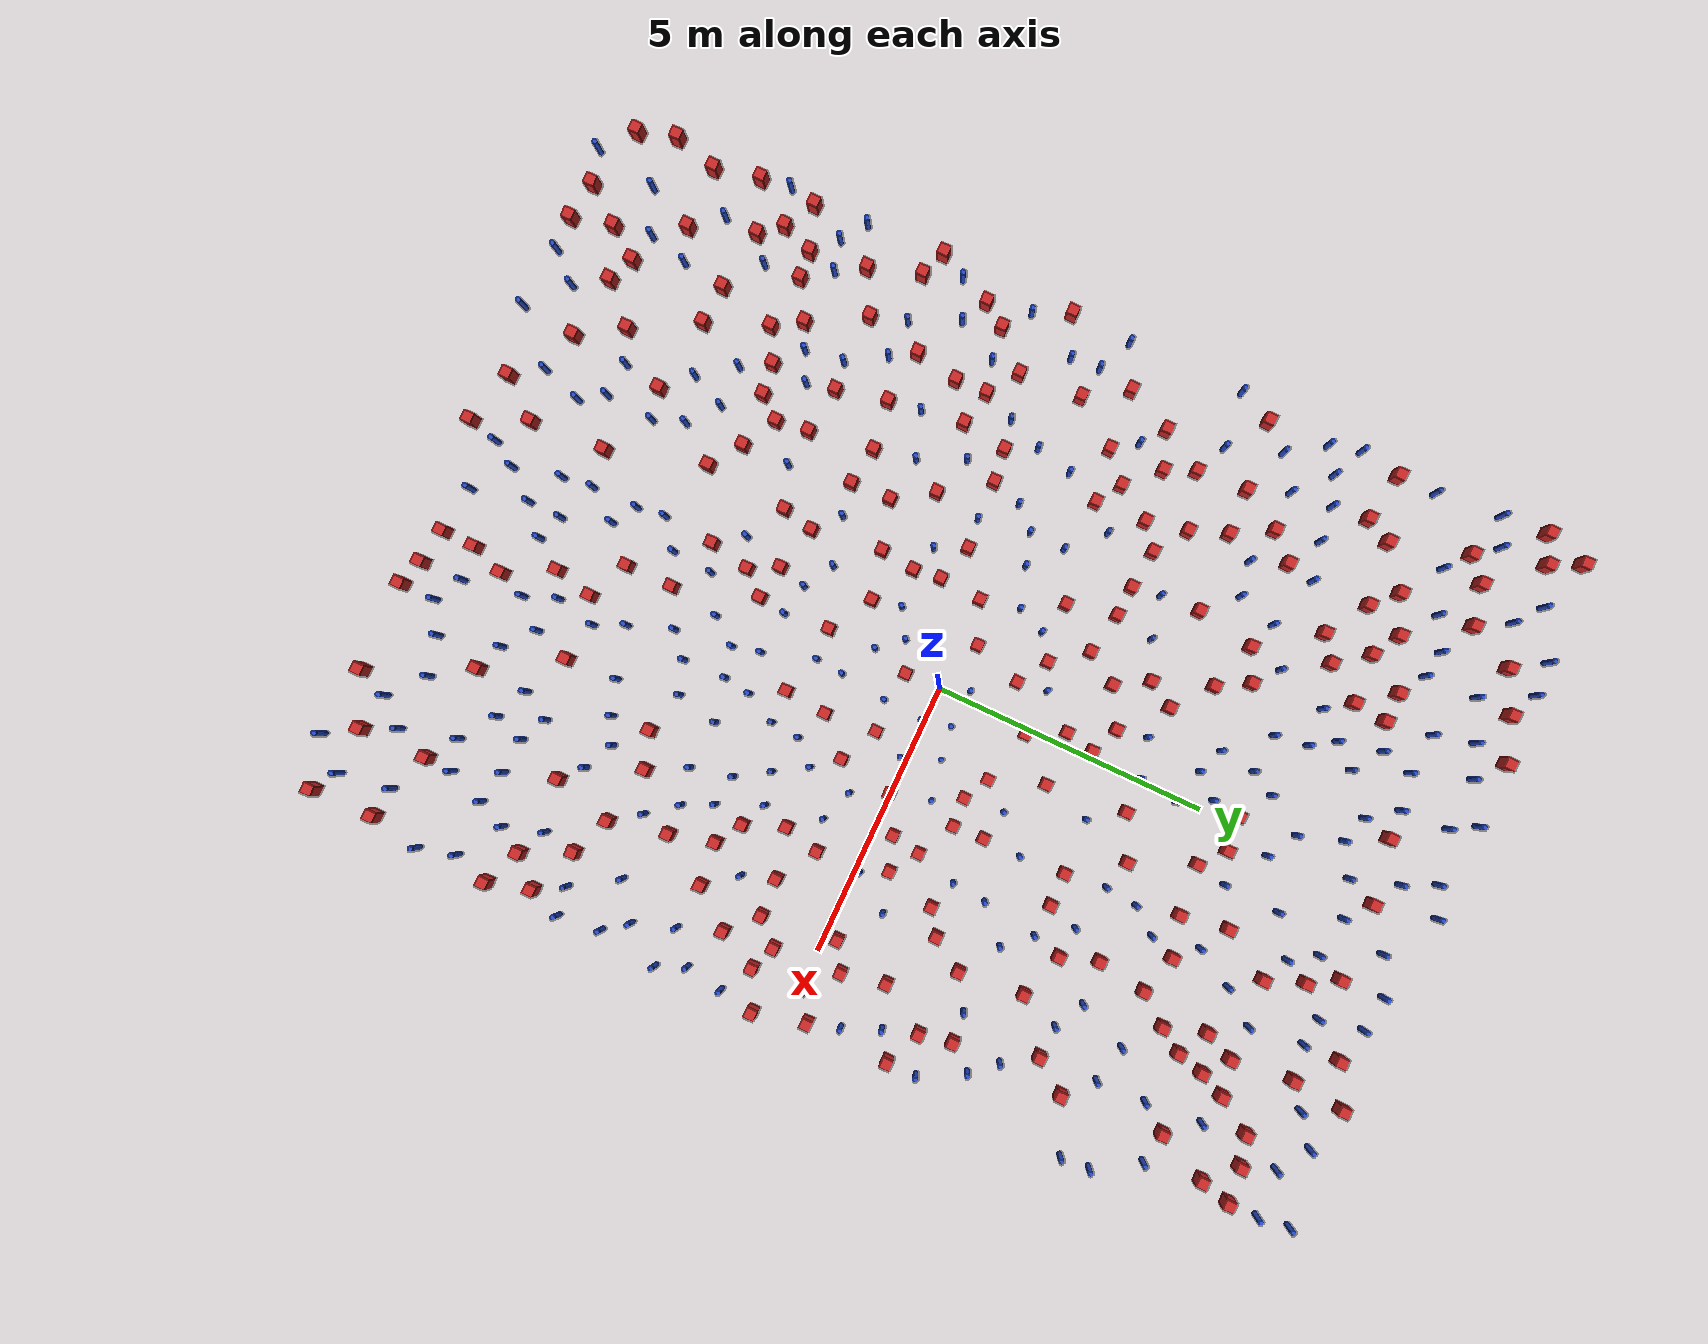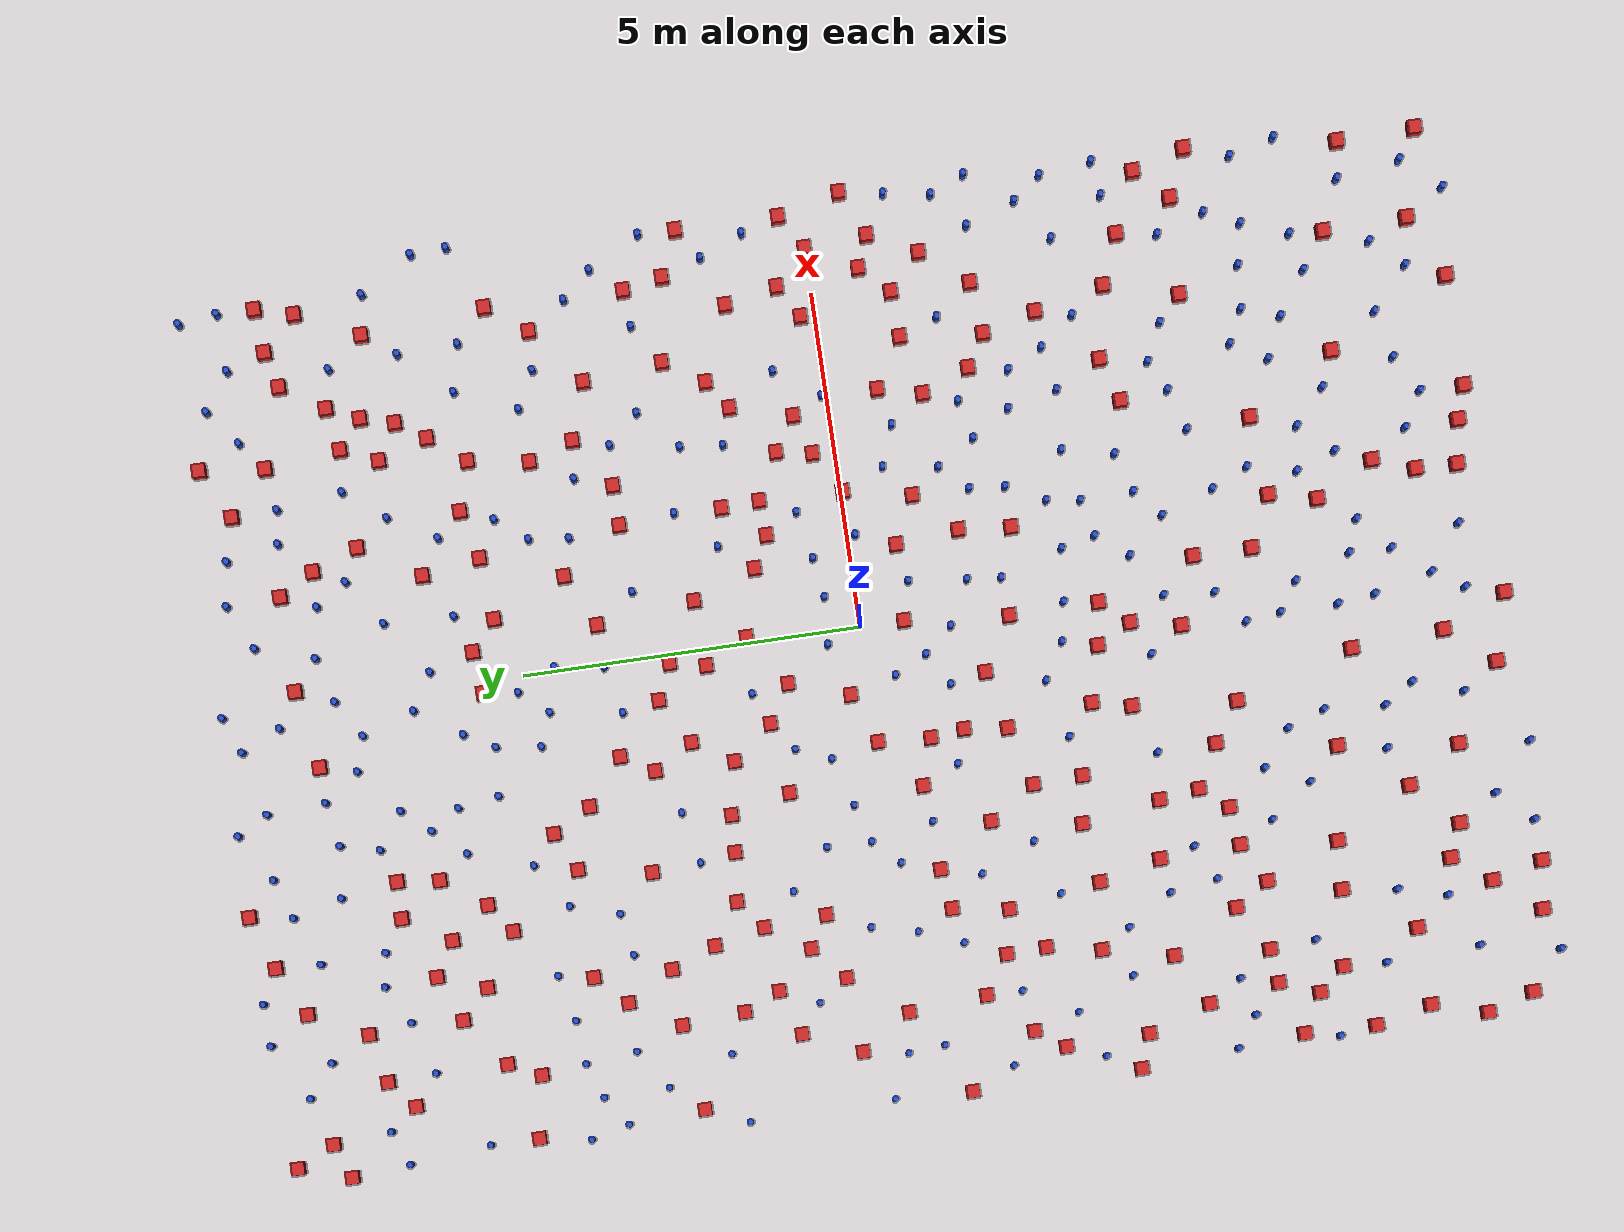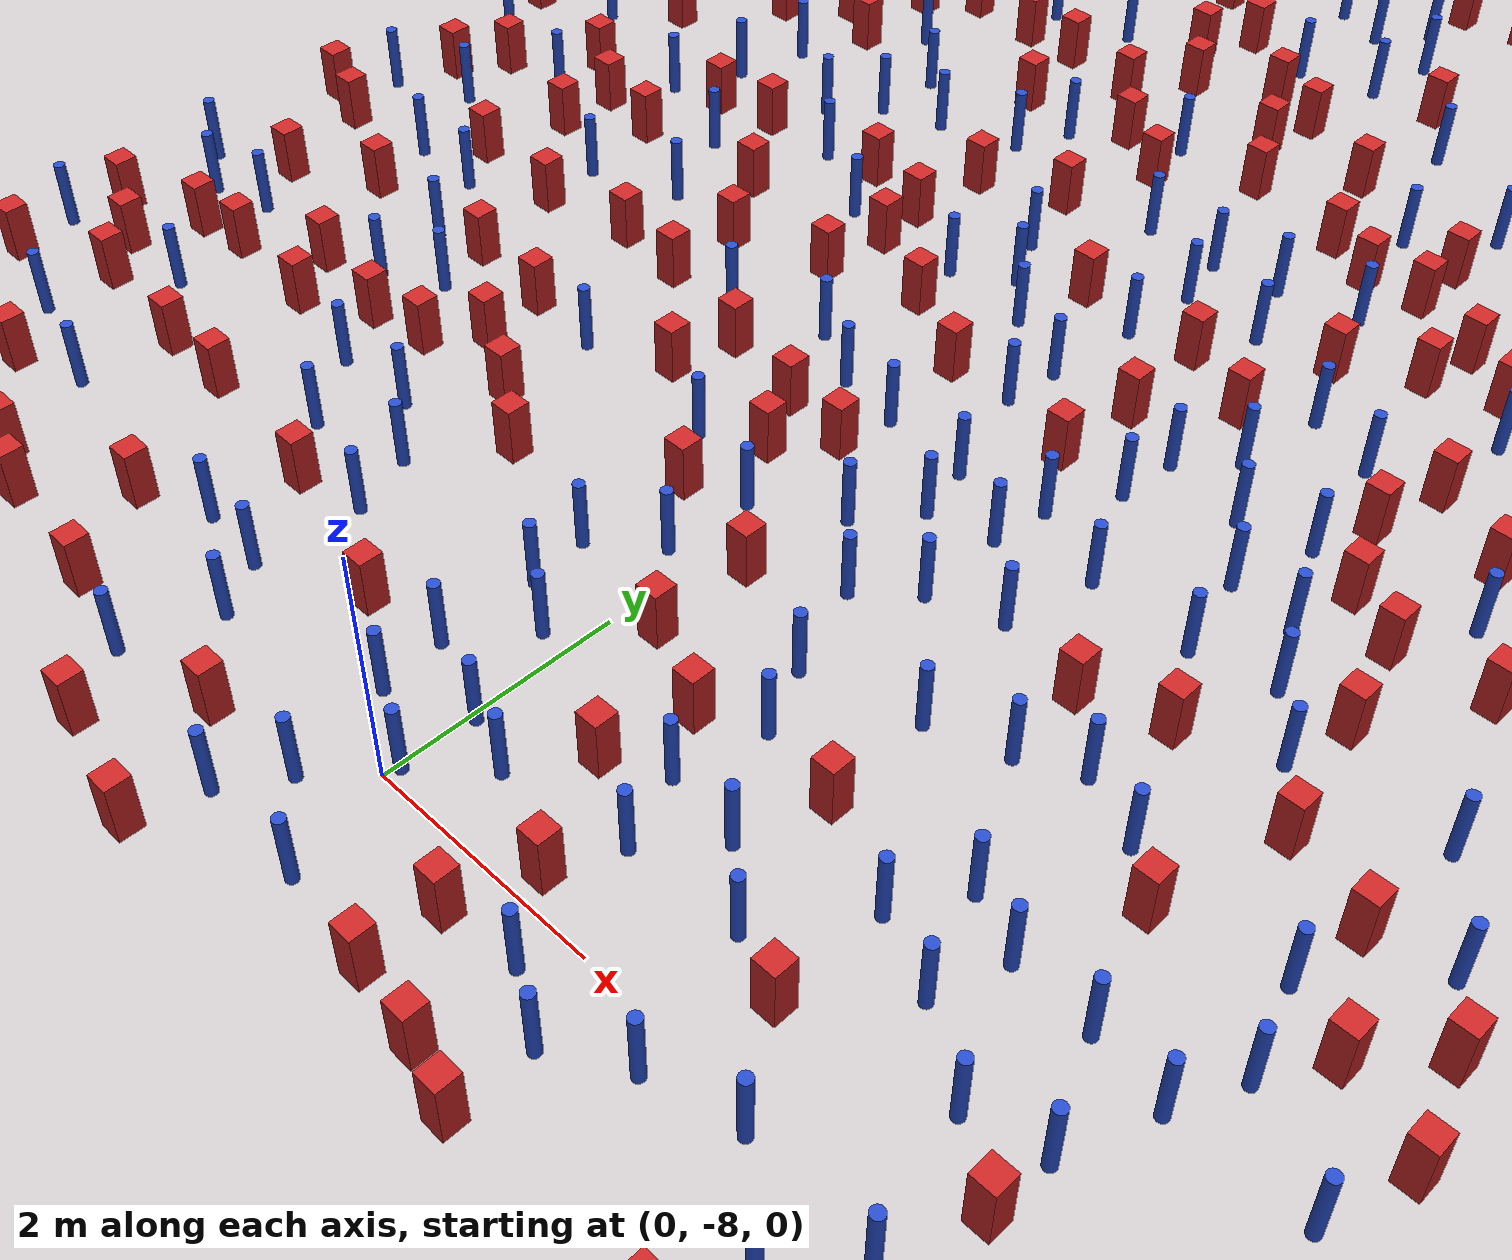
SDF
<sdf version="1.6">
  <model name="dense_64"><model name="pole_obstacle0">
  <static>true</static>
  <pose frame="">2.04700699149 2.47416205247 2.88873142074e-08 -9.9053669043e-09 4.60219948975e-07 -1.2096599497e-07</pose>
  <link name="link">
  <pose frame="">0 0 0.3 0 -0 0</pose>
    <inertial>
      <mass>1</mass>
      <inertia>
        <ixx>0.145833</ixx>
        <ixy>0</ixy>
        <ixz>0</ixz>
        <iyy>0.145833</iyy>
        <iyz>0</iyz>
        <izz>0.125</izz>
      </inertia>
    </inertial>
    <collision name="collision">
      <geometry>
        <cylinder>
          <radius>0.05</radius>
          <length>.6</length>
        </cylinder>
      </geometry>
      <max_contacts>10</max_contacts>
      <surface>
        <contact>
          <ode/>
        </contact>
        <bounce/>
        <friction>
          <torsional>
            <ode/>
          </torsional>
          <ode/>
        </friction>
      </surface>
    </collision>
    <visual name="visual">
      <geometry>
        <cylinder>
          <radius>0.05</radius>
          <length>.6</length>
        </cylinder>
      </geometry>
      <material>
        <script>
          <name>Gazebo/Blue</name>
          <uri>file://media/materials/scripts/gazebo.material</uri>
        </script>
      </material>
    </visual>
    <self_collide>0</self_collide>
    <kinematic>0</kinematic>
  </link>
</model>
<model name="pole_obstacle1">
  <static>true</static>
  <pose frame="">0.675258430934 7.98045626126 2.88873142074e-08 -9.90536690208e-09 4.6021994898e-07 -1.20965994966e-07</pose>
  <link name="link">
  <pose frame="">0 0 0.3 0 -0 0</pose>
    <inertial>
      <mass>1</mass>
      <inertia>
        <ixx>0.145833</ixx>
        <ixy>0</ixy>
        <ixz>0</ixz>
        <iyy>0.145833</iyy>
        <iyz>0</iyz>
        <izz>0.125</izz>
      </inertia>
    </inertial>
    <collision name="collision">
      <geometry>
        <cylinder>
          <radius>0.05</radius>
          <length>.6</length>
        </cylinder>
      </geometry>
      <max_contacts>10</max_contacts>
      <surface>
        <contact>
          <ode/>
        </contact>
        <bounce/>
        <friction>
          <torsional>
            <ode/>
          </torsional>
          <ode/>
        </friction>
      </surface>
    </collision>
    <visual name="visual">
      <geometry>
        <cylinder>
          <radius>0.05</radius>
          <length>.6</length>
        </cylinder>
      </geometry>
      <material>
        <script>
          <name>Gazebo/Blue</name>
          <uri>file://media/materials/scripts/gazebo.material</uri>
        </script>
      </material>
    </visual>
    <self_collide>0</self_collide>
    <kinematic>0</kinematic>
  </link>
</model>
<model name="square_post_obstacle0">
  <static>true</static>
  <pose frame="">-6.67981917974 9.26460042865 8.22691968438e-08 7.22125133819e-06 -7.54495500217e-07 2.29674213826e-05</pose>
  <link name="link">
    <pose frame="">0 0 0.25 0 -0 0</pose>
    <inertial>
      <mass>100</mass>
      <inertia>
        <ixx>0.166667</ixx>
        <ixy>0</ixy>
        <ixz>0</ixz>
        <iyy>0.166667</iyy>
        <iyz>0</iyz>
        <izz>0.166667</izz>
      </inertia>
    </inertial>
    <collision name="collision">
      <geometry>
        <box>
          <size>.2 .2 .5</size>
        </box>
      </geometry>
      <max_contacts>10</max_contacts>
      <surface>
        <contact>
          <ode/>
        </contact>
        <bounce/>
        <friction>
          <torsional>
            <ode/>
          </torsional>
          <ode/>
        </friction>
      </surface>
    </collision>
    <visual name="visual">
      <geometry>
        <box>
          <size>.2 .2 .5</size>
        </box>
      </geometry>
      <material>
        <script>
          <name>Gazebo/Red</name>
          <uri>file://media/materials/scripts/gazebo.material</uri>
        </script>
      </material>
    </visual>
    <self_collide>0</self_collide>
    <kinematic>0</kinematic>
  </link>
</model>
<model name="square_post_obstacle1">
  <static>true</static>
  <pose frame="">-4.19881178517 6.86529682707 8.22691968438e-08 7.2212513382e-06 -7.54495500217e-07 2.29674213826e-05</pose>
  <link name="link">
    <pose frame="">0 0 0.25 0 -0 0</pose>
    <inertial>
      <mass>100</mass>
      <inertia>
        <ixx>0.166667</ixx>
        <ixy>0</ixy>
        <ixz>0</ixz>
        <iyy>0.166667</iyy>
        <iyz>0</iyz>
        <izz>0.166667</izz>
      </inertia>
    </inertial>
    <collision name="collision">
      <geometry>
        <box>
          <size>.2 .2 .5</size>
        </box>
      </geometry>
      <max_contacts>10</max_contacts>
      <surface>
        <contact>
          <ode/>
        </contact>
        <bounce/>
        <friction>
          <torsional>
            <ode/>
          </torsional>
          <ode/>
        </friction>
      </surface>
    </collision>
    <visual name="visual">
      <geometry>
        <box>
          <size>.2 .2 .5</size>
        </box>
      </geometry>
      <material>
        <script>
          <name>Gazebo/Red</name>
          <uri>file://media/materials/scripts/gazebo.material</uri>
        </script>
      </material>
    </visual>
    <self_collide>0</self_collide>
    <kinematic>0</kinematic>
  </link>
</model>
<model name="pole_obstacle2">
  <static>true</static>
  <pose frame="">6.3781744433 5.77590479522 2.88873142074e-08 -9.90536690842e-09 4.60219948965e-07 -1.20965994976e-07</pose>
  <link name="link">
  <pose frame="">0 0 0.3 0 -0 0</pose>
    <inertial>
      <mass>1</mass>
      <inertia>
        <ixx>0.145833</ixx>
        <ixy>0</ixy>
        <ixz>0</ixz>
        <iyy>0.145833</iyy>
        <iyz>0</iyz>
        <izz>0.125</izz>
      </inertia>
    </inertial>
    <collision name="collision">
      <geometry>
        <cylinder>
          <radius>0.05</radius>
          <length>.6</length>
        </cylinder>
      </geometry>
      <max_contacts>10</max_contacts>
      <surface>
        <contact>
          <ode/>
        </contact>
        <bounce/>
        <friction>
          <torsional>
            <ode/>
          </torsional>
          <ode/>
        </friction>
      </surface>
    </collision>
    <visual name="visual">
      <geometry>
        <cylinder>
          <radius>0.05</radius>
          <length>.6</length>
        </cylinder>
      </geometry>
      <material>
        <script>
          <name>Gazebo/Blue</name>
          <uri>file://media/materials/scripts/gazebo.material</uri>
        </script>
      </material>
    </visual>
    <self_collide>0</self_collide>
    <kinematic>0</kinematic>
  </link>
</model>
<model name="pole_obstacle3">
  <static>true</static>
  <pose frame="">3.44390057278 -2.68241851468 2.88873142074e-08 -9.90536690232e-09 4.6021994898e-07 -1.20965994968e-07</pose>
  <link name="link">
  <pose frame="">0 0 0.3 0 -0 0</pose>
    <inertial>
      <mass>1</mass>
      <inertia>
        <ixx>0.145833</ixx>
        <ixy>0</ixy>
        <ixz>0</ixz>
        <iyy>0.145833</iyy>
        <iyz>0</iyz>
        <izz>0.125</izz>
      </inertia>
    </inertial>
    <collision name="collision">
      <geometry>
        <cylinder>
          <radius>0.05</radius>
          <length>.6</length>
        </cylinder>
      </geometry>
      <max_contacts>10</max_contacts>
      <surface>
        <contact>
          <ode/>
        </contact>
        <bounce/>
        <friction>
          <torsional>
            <ode/>
          </torsional>
          <ode/>
        </friction>
      </surface>
    </collision>
    <visual name="visual">
      <geometry>
        <cylinder>
          <radius>0.05</radius>
          <length>.6</length>
        </cylinder>
      </geometry>
      <material>
        <script>
          <name>Gazebo/Blue</name>
          <uri>file://media/materials/scripts/gazebo.material</uri>
        </script>
      </material>
    </visual>
    <self_collide>0</self_collide>
    <kinematic>0</kinematic>
  </link>
</model>
<model name="pole_obstacle4">
  <static>true</static>
  <pose frame="">-1.16663642655 -2.58017603443 2.88873142074e-08 -9.90536689791e-09 4.6021994899e-07 -1.20965994959e-07</pose>
  <link name="link">
  <pose frame="">0 0 0.3 0 -0 0</pose>
    <inertial>
      <mass>1</mass>
      <inertia>
        <ixx>0.145833</ixx>
        <ixy>0</ixy>
        <ixz>0</ixz>
        <iyy>0.145833</iyy>
        <iyz>0</iyz>
        <izz>0.125</izz>
      </inertia>
    </inertial>
    <collision name="collision">
      <geometry>
        <cylinder>
          <radius>0.05</radius>
          <length>.6</length>
        </cylinder>
      </geometry>
      <max_contacts>10</max_contacts>
      <surface>
        <contact>
          <ode/>
        </contact>
        <bounce/>
        <friction>
          <torsional>
            <ode/>
          </torsional>
          <ode/>
        </friction>
      </surface>
    </collision>
    <visual name="visual">
      <geometry>
        <cylinder>
          <radius>0.05</radius>
          <length>.6</length>
        </cylinder>
      </geometry>
      <material>
        <script>
          <name>Gazebo/Blue</name>
          <uri>file://media/materials/scripts/gazebo.material</uri>
        </script>
      </material>
    </visual>
    <self_collide>0</self_collide>
    <kinematic>0</kinematic>
  </link>
</model>
<model name="pole_obstacle5">
  <static>true</static>
  <pose frame="">3.81524435492 -4.99224262672 2.88873142074e-08 -9.90536689859e-09 4.60219948989e-07 -1.20965994961e-07</pose>
  <link name="link">
  <pose frame="">0 0 0.3 0 -0 0</pose>
    <inertial>
      <mass>1</mass>
      <inertia>
        <ixx>0.145833</ixx>
        <ixy>0</ixy>
        <ixz>0</ixz>
        <iyy>0.145833</iyy>
        <iyz>0</iyz>
        <izz>0.125</izz>
      </inertia>
    </inertial>
    <collision name="collision">
      <geometry>
        <cylinder>
          <radius>0.05</radius>
          <length>.6</length>
        </cylinder>
      </geometry>
      <max_contacts>10</max_contacts>
      <surface>
        <contact>
          <ode/>
        </contact>
        <bounce/>
        <friction>
          <torsional>
            <ode/>
          </torsional>
          <ode/>
        </friction>
      </surface>
    </collision>
    <visual name="visual">
      <geometry>
        <cylinder>
          <radius>0.05</radius>
          <length>.6</length>
        </cylinder>
      </geometry>
      <material>
        <script>
          <name>Gazebo/Blue</name>
          <uri>file://media/materials/scripts/gazebo.material</uri>
        </script>
      </material>
    </visual>
    <self_collide>0</self_collide>
    <kinematic>0</kinematic>
  </link>
</model>
<model name="pole_obstacle6">
  <static>true</static>
  <pose frame="">-2.10042866852 8.00277841982 2.88873142074e-08 -9.90536689889e-09 4.60219948988e-07 -1.2096599496e-07</pose>
  <link name="link">
  <pose frame="">0 0 0.3 0 -0 0</pose>
    <inertial>
      <mass>1</mass>
      <inertia>
        <ixx>0.145833</ixx>
        <ixy>0</ixy>
        <ixz>0</ixz>
        <iyy>0.145833</iyy>
        <iyz>0</iyz>
        <izz>0.125</izz>
      </inertia>
    </inertial>
    <collision name="collision">
      <geometry>
        <cylinder>
          <radius>0.05</radius>
          <length>.6</length>
        </cylinder>
      </geometry>
      <max_contacts>10</max_contacts>
      <surface>
        <contact>
          <ode/>
        </contact>
        <bounce/>
        <friction>
          <torsional>
            <ode/>
          </torsional>
          <ode/>
        </friction>
      </surface>
    </collision>
    <visual name="visual">
      <geometry>
        <cylinder>
          <radius>0.05</radius>
          <length>.6</length>
        </cylinder>
      </geometry>
      <material>
        <script>
          <name>Gazebo/Blue</name>
          <uri>file://media/materials/scripts/gazebo.material</uri>
        </script>
      </material>
    </visual>
    <self_collide>0</self_collide>
    <kinematic>0</kinematic>
  </link>
</model>
<model name="square_post_obstacle2">
  <static>true</static>
  <pose frame="">1.36068984229 4.20448335055 8.22691968438e-08 7.2212513382e-06 -7.54495500217e-07 2.29674213826e-05</pose>
  <link name="link">
    <pose frame="">0 0 0.25 0 -0 0</pose>
    <inertial>
      <mass>100</mass>
      <inertia>
        <ixx>0.166667</ixx>
        <ixy>0</ixy>
        <ixz>0</ixz>
        <iyy>0.166667</iyy>
        <iyz>0</iyz>
        <izz>0.166667</izz>
      </inertia>
    </inertial>
    <collision name="collision">
      <geometry>
        <box>
          <size>.2 .2 .5</size>
        </box>
      </geometry>
      <max_contacts>10</max_contacts>
      <surface>
        <contact>
          <ode/>
        </contact>
        <bounce/>
        <friction>
          <torsional>
            <ode/>
          </torsional>
          <ode/>
        </friction>
      </surface>
    </collision>
    <visual name="visual">
      <geometry>
        <box>
          <size>.2 .2 .5</size>
        </box>
      </geometry>
      <material>
        <script>
          <name>Gazebo/Red</name>
          <uri>file://media/materials/scripts/gazebo.material</uri>
        </script>
      </material>
    </visual>
    <self_collide>0</self_collide>
    <kinematic>0</kinematic>
  </link>
</model>
<model name="square_post_obstacle3">
  <static>true</static>
  <pose frame="">-5.41034767006 3.40983076827 8.22691968438e-08 7.2212513382e-06 -7.54495500217e-07 2.29674213826e-05</pose>
  <link name="link">
    <pose frame="">0 0 0.25 0 -0 0</pose>
    <inertial>
      <mass>100</mass>
      <inertia>
        <ixx>0.166667</ixx>
        <ixy>0</ixy>
        <ixz>0</ixz>
        <iyy>0.166667</iyy>
        <iyz>0</iyz>
        <izz>0.166667</izz>
      </inertia>
    </inertial>
    <collision name="collision">
      <geometry>
        <box>
          <size>.2 .2 .5</size>
        </box>
      </geometry>
      <max_contacts>10</max_contacts>
      <surface>
        <contact>
          <ode/>
        </contact>
        <bounce/>
        <friction>
          <torsional>
            <ode/>
          </torsional>
          <ode/>
        </friction>
      </surface>
    </collision>
    <visual name="visual">
      <geometry>
        <box>
          <size>.2 .2 .5</size>
        </box>
      </geometry>
      <material>
        <script>
          <name>Gazebo/Red</name>
          <uri>file://media/materials/scripts/gazebo.material</uri>
        </script>
      </material>
    </visual>
    <self_collide>0</self_collide>
    <kinematic>0</kinematic>
  </link>
</model>
<model name="square_post_obstacle4">
  <static>true</static>
  <pose frame="">-6.89847792682 -8.28726109435 8.22691968438e-08 7.2212513382e-06 -7.54495500217e-07 2.29674213826e-05</pose>
  <link name="link">
    <pose frame="">0 0 0.25 0 -0 0</pose>
    <inertial>
      <mass>100</mass>
      <inertia>
        <ixx>0.166667</ixx>
        <ixy>0</ixy>
        <ixz>0</ixz>
        <iyy>0.166667</iyy>
        <iyz>0</iyz>
        <izz>0.166667</izz>
      </inertia>
    </inertial>
    <collision name="collision">
      <geometry>
        <box>
          <size>.2 .2 .5</size>
        </box>
      </geometry>
      <max_contacts>10</max_contacts>
      <surface>
        <contact>
          <ode/>
        </contact>
        <bounce/>
        <friction>
          <torsional>
            <ode/>
          </torsional>
          <ode/>
        </friction>
      </surface>
    </collision>
    <visual name="visual">
      <geometry>
        <box>
          <size>.2 .2 .5</size>
        </box>
      </geometry>
      <material>
        <script>
          <name>Gazebo/Red</name>
          <uri>file://media/materials/scripts/gazebo.material</uri>
        </script>
      </material>
    </visual>
    <self_collide>0</self_collide>
    <kinematic>0</kinematic>
  </link>
</model>
<model name="pole_obstacle7">
  <static>true</static>
  <pose frame="">-1.79756553339 6.20950631164 2.88873142074e-08 -9.90536689852e-09 4.60219948989e-07 -1.2096599496e-07</pose>
  <link name="link">
  <pose frame="">0 0 0.3 0 -0 0</pose>
    <inertial>
      <mass>1</mass>
      <inertia>
        <ixx>0.145833</ixx>
        <ixy>0</ixy>
        <ixz>0</ixz>
        <iyy>0.145833</iyy>
        <iyz>0</iyz>
        <izz>0.125</izz>
      </inertia>
    </inertial>
    <collision name="collision">
      <geometry>
        <cylinder>
          <radius>0.05</radius>
          <length>.6</length>
        </cylinder>
      </geometry>
      <max_contacts>10</max_contacts>
      <surface>
        <contact>
          <ode/>
        </contact>
        <bounce/>
        <friction>
          <torsional>
            <ode/>
          </torsional>
          <ode/>
        </friction>
      </surface>
    </collision>
    <visual name="visual">
      <geometry>
        <cylinder>
          <radius>0.05</radius>
          <length>.6</length>
        </cylinder>
      </geometry>
      <material>
        <script>
          <name>Gazebo/Blue</name>
          <uri>file://media/materials/scripts/gazebo.material</uri>
        </script>
      </material>
    </visual>
    <self_collide>0</self_collide>
    <kinematic>0</kinematic>
  </link>
</model>
<model name="pole_obstacle8">
  <static>true</static>
  <pose frame="">-6.29015280869 4.68801422274 2.88873142074e-08 -9.90536690842e-09 4.60219948965e-07 -1.20965994976e-07</pose>
  <link name="link">
  <pose frame="">0 0 0.3 0 -0 0</pose>
    <inertial>
      <mass>1</mass>
      <inertia>
        <ixx>0.145833</ixx>
        <ixy>0</ixy>
        <ixz>0</ixz>
        <iyy>0.145833</iyy>
        <iyz>0</iyz>
        <izz>0.125</izz>
      </inertia>
    </inertial>
    <collision name="collision">
      <geometry>
        <cylinder>
          <radius>0.05</radius>
          <length>.6</length>
        </cylinder>
      </geometry>
      <max_contacts>10</max_contacts>
      <surface>
        <contact>
          <ode/>
        </contact>
        <bounce/>
        <friction>
          <torsional>
            <ode/>
          </torsional>
          <ode/>
        </friction>
      </surface>
    </collision>
    <visual name="visual">
      <geometry>
        <cylinder>
          <radius>0.05</radius>
          <length>.6</length>
        </cylinder>
      </geometry>
      <material>
        <script>
          <name>Gazebo/Blue</name>
          <uri>file://media/materials/scripts/gazebo.material</uri>
        </script>
      </material>
    </visual>
    <self_collide>0</self_collide>
    <kinematic>0</kinematic>
  </link>
</model>
<model name="square_post_obstacle5">
  <static>true</static>
  <pose frame="">-4.99715958889 -8.63131955037 8.22691968438e-08 7.22125133819e-06 -7.54495500217e-07 2.29674213826e-05</pose>
  <link name="link">
    <pose frame="">0 0 0.25 0 -0 0</pose>
    <inertial>
      <mass>100</mass>
      <inertia>
        <ixx>0.166667</ixx>
        <ixy>0</ixy>
        <ixz>0</ixz>
        <iyy>0.166667</iyy>
        <iyz>0</iyz>
        <izz>0.166667</izz>
      </inertia>
    </inertial>
    <collision name="collision">
      <geometry>
        <box>
          <size>.2 .2 .5</size>
        </box>
      </geometry>
      <max_contacts>10</max_contacts>
      <surface>
        <contact>
          <ode/>
        </contact>
        <bounce/>
        <friction>
          <torsional>
            <ode/>
          </torsional>
          <ode/>
        </friction>
      </surface>
    </collision>
    <visual name="visual">
      <geometry>
        <box>
          <size>.2 .2 .5</size>
        </box>
      </geometry>
      <material>
        <script>
          <name>Gazebo/Red</name>
          <uri>file://media/materials/scripts/gazebo.material</uri>
        </script>
      </material>
    </visual>
    <self_collide>0</self_collide>
    <kinematic>0</kinematic>
  </link>
</model>
<model name="square_post_obstacle6">
  <static>true</static>
  <pose frame="">4.18874064382 -5.33425178005 8.22691968438e-08 7.2212513382e-06 -7.54495500217e-07 2.29674213826e-05</pose>
  <link name="link">
    <pose frame="">0 0 0.25 0 -0 0</pose>
    <inertial>
      <mass>100</mass>
      <inertia>
        <ixx>0.166667</ixx>
        <ixy>0</ixy>
        <ixz>0</ixz>
        <iyy>0.166667</iyy>
        <iyz>0</iyz>
        <izz>0.166667</izz>
      </inertia>
    </inertial>
    <collision name="collision">
      <geometry>
        <box>
          <size>.2 .2 .5</size>
        </box>
      </geometry>
      <max_contacts>10</max_contacts>
      <surface>
        <contact>
          <ode/>
        </contact>
        <bounce/>
        <friction>
          <torsional>
            <ode/>
          </torsional>
          <ode/>
        </friction>
      </surface>
    </collision>
    <visual name="visual">
      <geometry>
        <box>
          <size>.2 .2 .5</size>
        </box>
      </geometry>
      <material>
        <script>
          <name>Gazebo/Red</name>
          <uri>file://media/materials/scripts/gazebo.material</uri>
        </script>
      </material>
    </visual>
    <self_collide>0</self_collide>
    <kinematic>0</kinematic>
  </link>
</model>
<model name="square_post_obstacle7">
  <static>true</static>
  <pose frame="">-3.26198819976 5.98409648104 8.22691968438e-08 7.2212513382e-06 -7.54495500217e-07 2.29674213826e-05</pose>
  <link name="link">
    <pose frame="">0 0 0.25 0 -0 0</pose>
    <inertial>
      <mass>100</mass>
      <inertia>
        <ixx>0.166667</ixx>
        <ixy>0</ixy>
        <ixz>0</ixz>
        <iyy>0.166667</iyy>
        <iyz>0</iyz>
        <izz>0.166667</izz>
      </inertia>
    </inertial>
    <collision name="collision">
      <geometry>
        <box>
          <size>.2 .2 .5</size>
        </box>
      </geometry>
      <max_contacts>10</max_contacts>
      <surface>
        <contact>
          <ode/>
        </contact>
        <bounce/>
        <friction>
          <torsional>
            <ode/>
          </torsional>
          <ode/>
        </friction>
      </surface>
    </collision>
    <visual name="visual">
      <geometry>
        <box>
          <size>.2 .2 .5</size>
        </box>
      </geometry>
      <material>
        <script>
          <name>Gazebo/Red</name>
          <uri>file://media/materials/scripts/gazebo.material</uri>
        </script>
      </material>
    </visual>
    <self_collide>0</self_collide>
    <kinematic>0</kinematic>
  </link>
</model>
<model name="pole_obstacle9">
  <static>true</static>
  <pose frame="">3.17217486479 3.26888968128 2.88873142074e-08 -9.90536690232e-09 4.6021994898e-07 -1.20965994968e-07</pose>
  <link name="link">
  <pose frame="">0 0 0.3 0 -0 0</pose>
    <inertial>
      <mass>1</mass>
      <inertia>
        <ixx>0.145833</ixx>
        <ixy>0</ixy>
        <ixz>0</ixz>
        <iyy>0.145833</iyy>
        <iyz>0</iyz>
        <izz>0.125</izz>
      </inertia>
    </inertial>
    <collision name="collision">
      <geometry>
        <cylinder>
          <radius>0.05</radius>
          <length>.6</length>
        </cylinder>
      </geometry>
      <max_contacts>10</max_contacts>
      <surface>
        <contact>
          <ode/>
        </contact>
        <bounce/>
        <friction>
          <torsional>
            <ode/>
          </torsional>
          <ode/>
        </friction>
      </surface>
    </collision>
    <visual name="visual">
      <geometry>
        <cylinder>
          <radius>0.05</radius>
          <length>.6</length>
        </cylinder>
      </geometry>
      <material>
        <script>
          <name>Gazebo/Blue</name>
          <uri>file://media/materials/scripts/gazebo.material</uri>
        </script>
      </material>
    </visual>
    <self_collide>0</self_collide>
    <kinematic>0</kinematic>
  </link>
</model>
<model name="pole_obstacle10">
  <static>true</static>
  <pose frame="">-4.92236656138 -3.26465906516 2.88873142074e-08 -9.90536690245e-09 4.6021994898e-07 -1.20965994966e-07</pose>
  <link name="link">
  <pose frame="">0 0 0.3 0 -0 0</pose>
    <inertial>
      <mass>1</mass>
      <inertia>
        <ixx>0.145833</ixx>
        <ixy>0</ixy>
        <ixz>0</ixz>
        <iyy>0.145833</iyy>
        <iyz>0</iyz>
        <izz>0.125</izz>
      </inertia>
    </inertial>
    <collision name="collision">
      <geometry>
        <cylinder>
          <radius>0.05</radius>
          <length>.6</length>
        </cylinder>
      </geometry>
      <max_contacts>10</max_contacts>
      <surface>
        <contact>
          <ode/>
        </contact>
        <bounce/>
        <friction>
          <torsional>
            <ode/>
          </torsional>
          <ode/>
        </friction>
      </surface>
    </collision>
    <visual name="visual">
      <geometry>
        <cylinder>
          <radius>0.05</radius>
          <length>.6</length>
        </cylinder>
      </geometry>
      <material>
        <script>
          <name>Gazebo/Blue</name>
          <uri>file://media/materials/scripts/gazebo.material</uri>
        </script>
      </material>
    </visual>
    <self_collide>0</self_collide>
    <kinematic>0</kinematic>
  </link>
</model>
<model name="pole_obstacle11">
  <static>true</static>
  <pose frame="">4.8431363912 -7.06583838688 2.88873142074e-08 -9.90536690842e-09 4.60219948965e-07 -1.20965994976e-07</pose>
  <link name="link">
  <pose frame="">0 0 0.3 0 -0 0</pose>
    <inertial>
      <mass>1</mass>
      <inertia>
        <ixx>0.145833</ixx>
        <ixy>0</ixy>
        <ixz>0</ixz>
        <iyy>0.145833</iyy>
        <iyz>0</iyz>
        <izz>0.125</izz>
      </inertia>
    </inertial>
    <collision name="collision">
      <geometry>
        <cylinder>
          <radius>0.05</radius>
          <length>.6</length>
        </cylinder>
      </geometry>
      <max_contacts>10</max_contacts>
      <surface>
        <contact>
          <ode/>
        </contact>
        <bounce/>
        <friction>
          <torsional>
            <ode/>
          </torsional>
          <ode/>
        </friction>
      </surface>
    </collision>
    <visual name="visual">
      <geometry>
        <cylinder>
          <radius>0.05</radius>
          <length>.6</length>
        </cylinder>
      </geometry>
      <material>
        <script>
          <name>Gazebo/Blue</name>
          <uri>file://media/materials/scripts/gazebo.material</uri>
        </script>
      </material>
    </visual>
    <self_collide>0</self_collide>
    <kinematic>0</kinematic>
  </link>
</model>
<model name="pole_obstacle12">
  <static>true</static>
  <pose frame="">0.424822566646 -2.14659219355 2.88873142074e-08 -9.90536689663e-09 4.60219948993e-07 -1.20965994959e-07</pose>
  <link name="link">
  <pose frame="">0 0 0.3 0 -0 0</pose>
    <inertial>
      <mass>1</mass>
      <inertia>
        <ixx>0.145833</ixx>
        <ixy>0</ixy>
        <ixz>0</ixz>
        <iyy>0.145833</iyy>
        <iyz>0</iyz>
        <izz>0.125</izz>
      </inertia>
    </inertial>
    <collision name="collision">
      <geometry>
        <cylinder>
          <radius>0.05</radius>
          <length>.6</length>
        </cylinder>
      </geometry>
      <max_contacts>10</max_contacts>
      <surface>
        <contact>
          <ode/>
        </contact>
        <bounce/>
        <friction>
          <torsional>
            <ode/>
          </torsional>
          <ode/>
        </friction>
      </surface>
    </collision>
    <visual name="visual">
      <geometry>
        <cylinder>
          <radius>0.05</radius>
          <length>.6</length>
        </cylinder>
      </geometry>
      <material>
        <script>
          <name>Gazebo/Blue</name>
          <uri>file://media/materials/scripts/gazebo.material</uri>
        </script>
      </material>
    </visual>
    <self_collide>0</self_collide>
    <kinematic>0</kinematic>
  </link>
</model>
<model name="square_post_obstacle8">
  <static>true</static>
  <pose frame="">-2.93860940635 4.60545427997 8.22691968438e-08 7.2212513382e-06 -7.54495500217e-07 2.29674213826e-05</pose>
  <link name="link">
    <pose frame="">0 0 0.25 0 -0 0</pose>
    <inertial>
      <mass>100</mass>
      <inertia>
        <ixx>0.166667</ixx>
        <ixy>0</ixy>
        <ixz>0</ixz>
        <iyy>0.166667</iyy>
        <iyz>0</iyz>
        <izz>0.166667</izz>
      </inertia>
    </inertial>
    <collision name="collision">
      <geometry>
        <box>
          <size>.2 .2 .5</size>
        </box>
      </geometry>
      <max_contacts>10</max_contacts>
      <surface>
        <contact>
          <ode/>
        </contact>
        <bounce/>
        <friction>
          <torsional>
            <ode/>
          </torsional>
          <ode/>
        </friction>
      </surface>
    </collision>
    <visual name="visual">
      <geometry>
        <box>
          <size>.2 .2 .5</size>
        </box>
      </geometry>
      <material>
        <script>
          <name>Gazebo/Red</name>
          <uri>file://media/materials/scripts/gazebo.material</uri>
        </script>
      </material>
    </visual>
    <self_collide>0</self_collide>
    <kinematic>0</kinematic>
  </link>
</model>
<model name="square_post_obstacle9">
  <static>true</static>
  <pose frame="">2.24763330998 -6.09969372147 8.22691968438e-08 7.2212513382e-06 -7.54495500217e-07 2.29674213826e-05</pose>
  <link name="link">
    <pose frame="">0 0 0.25 0 -0 0</pose>
    <inertial>
      <mass>100</mass>
      <inertia>
        <ixx>0.166667</ixx>
        <ixy>0</ixy>
        <ixz>0</ixz>
        <iyy>0.166667</iyy>
        <iyz>0</iyz>
        <izz>0.166667</izz>
      </inertia>
    </inertial>
    <collision name="collision">
      <geometry>
        <box>
          <size>.2 .2 .5</size>
        </box>
      </geometry>
      <max_contacts>10</max_contacts>
      <surface>
        <contact>
          <ode/>
        </contact>
        <bounce/>
        <friction>
          <torsional>
            <ode/>
          </torsional>
          <ode/>
        </friction>
      </surface>
    </collision>
    <visual name="visual">
      <geometry>
        <box>
          <size>.2 .2 .5</size>
        </box>
      </geometry>
      <material>
        <script>
          <name>Gazebo/Red</name>
          <uri>file://media/materials/scripts/gazebo.material</uri>
        </script>
      </material>
    </visual>
    <self_collide>0</self_collide>
    <kinematic>0</kinematic>
  </link>
</model>
<model name="pole_obstacle13">
  <static>true</static>
  <pose frame="">2.27692390279 -8.6323744666 2.88873142074e-08 -9.90536692318e-09 4.6021994893e-07 -1.20965994988e-07</pose>
  <link name="link">
  <pose frame="">0 0 0.3 0 -0 0</pose>
    <inertial>
      <mass>1</mass>
      <inertia>
        <ixx>0.145833</ixx>
        <ixy>0</ixy>
        <ixz>0</ixz>
        <iyy>0.145833</iyy>
        <iyz>0</iyz>
        <izz>0.125</izz>
      </inertia>
    </inertial>
    <collision name="collision">
      <geometry>
        <cylinder>
          <radius>0.05</radius>
          <length>.6</length>
        </cylinder>
      </geometry>
      <max_contacts>10</max_contacts>
      <surface>
        <contact>
          <ode/>
        </contact>
        <bounce/>
        <friction>
          <torsional>
            <ode/>
          </torsional>
          <ode/>
        </friction>
      </surface>
    </collision>
    <visual name="visual">
      <geometry>
        <cylinder>
          <radius>0.05</radius>
          <length>.6</length>
        </cylinder>
      </geometry>
      <material>
        <script>
          <name>Gazebo/Blue</name>
          <uri>file://media/materials/scripts/gazebo.material</uri>
        </script>
      </material>
    </visual>
    <self_collide>0</self_collide>
    <kinematic>0</kinematic>
  </link>
</model>
<model name="square_post_obstacle10">
  <static>true</static>
  <pose frame="">-6.96881998501 -0.65673575316 8.22691968438e-08 7.2212513382e-06 -7.54495500217e-07 2.29674213826e-05</pose>
  <link name="link">
    <pose frame="">0 0 0.25 0 -0 0</pose>
    <inertial>
      <mass>100</mass>
      <inertia>
        <ixx>0.166667</ixx>
        <ixy>0</ixy>
        <ixz>0</ixz>
        <iyy>0.166667</iyy>
        <iyz>0</iyz>
        <izz>0.166667</izz>
      </inertia>
    </inertial>
    <collision name="collision">
      <geometry>
        <box>
          <size>.2 .2 .5</size>
        </box>
      </geometry>
      <max_contacts>10</max_contacts>
      <surface>
        <contact>
          <ode/>
        </contact>
        <bounce/>
        <friction>
          <torsional>
            <ode/>
          </torsional>
          <ode/>
        </friction>
      </surface>
    </collision>
    <visual name="visual">
      <geometry>
        <box>
          <size>.2 .2 .5</size>
        </box>
      </geometry>
      <material>
        <script>
          <name>Gazebo/Red</name>
          <uri>file://media/materials/scripts/gazebo.material</uri>
        </script>
      </material>
    </visual>
    <self_collide>0</self_collide>
    <kinematic>0</kinematic>
  </link>
</model>
<model name="square_post_obstacle11">
  <static>true</static>
  <pose frame="">-2.94364998078 -8.43636471448 8.22691968438e-08 7.22125133819e-06 -7.54495500217e-07 2.29674213826e-05</pose>
  <link name="link">
    <pose frame="">0 0 0.25 0 -0 0</pose>
    <inertial>
      <mass>100</mass>
      <inertia>
        <ixx>0.166667</ixx>
        <ixy>0</ixy>
        <ixz>0</ixz>
        <iyy>0.166667</iyy>
        <iyz>0</iyz>
        <izz>0.166667</izz>
      </inertia>
    </inertial>
    <collision name="collision">
      <geometry>
        <box>
          <size>.2 .2 .5</size>
        </box>
      </geometry>
      <max_contacts>10</max_contacts>
      <surface>
        <contact>
          <ode/>
        </contact>
        <bounce/>
        <friction>
          <torsional>
            <ode/>
          </torsional>
          <ode/>
        </friction>
      </surface>
    </collision>
    <visual name="visual">
      <geometry>
        <box>
          <size>.2 .2 .5</size>
        </box>
      </geometry>
      <material>
        <script>
          <name>Gazebo/Red</name>
          <uri>file://media/materials/scripts/gazebo.material</uri>
        </script>
      </material>
    </visual>
    <self_collide>0</self_collide>
    <kinematic>0</kinematic>
  </link>
</model>
<model name="pole_obstacle14">
  <static>true</static>
  <pose frame="">4.49745571173 9.06635080468 2.88873142074e-08 -9.9053668967e-09 4.60219948993e-07 -1.20965994957e-07</pose>
  <link name="link">
  <pose frame="">0 0 0.3 0 -0 0</pose>
    <inertial>
      <mass>1</mass>
      <inertia>
        <ixx>0.145833</ixx>
        <ixy>0</ixy>
        <ixz>0</ixz>
        <iyy>0.145833</iyy>
        <iyz>0</iyz>
        <izz>0.125</izz>
      </inertia>
    </inertial>
    <collision name="collision">
      <geometry>
        <cylinder>
          <radius>0.05</radius>
          <length>.6</length>
        </cylinder>
      </geometry>
      <max_contacts>10</max_contacts>
      <surface>
        <contact>
          <ode/>
        </contact>
        <bounce/>
        <friction>
          <torsional>
            <ode/>
          </torsional>
          <ode/>
        </friction>
      </surface>
    </collision>
    <visual name="visual">
      <geometry>
        <cylinder>
          <radius>0.05</radius>
          <length>.6</length>
        </cylinder>
      </geometry>
      <material>
        <script>
          <name>Gazebo/Blue</name>
          <uri>file://media/materials/scripts/gazebo.material</uri>
        </script>
      </material>
    </visual>
    <self_collide>0</self_collide>
    <kinematic>0</kinematic>
  </link>
</model>
<model name="pole_obstacle15">
  <static>true</static>
  <pose frame="">4.36360542164 -1.75431057876 2.88873142074e-08 -9.90536689445e-09 4.60219948999e-07 -1.20965994956e-07</pose>
  <link name="link">
  <pose frame="">0 0 0.3 0 -0 0</pose>
    <inertial>
      <mass>1</mass>
      <inertia>
        <ixx>0.145833</ixx>
        <ixy>0</ixy>
        <ixz>0</ixz>
        <iyy>0.145833</iyy>
        <iyz>0</iyz>
        <izz>0.125</izz>
      </inertia>
    </inertial>
    <collision name="collision">
      <geometry>
        <cylinder>
          <radius>0.05</radius>
          <length>.6</length>
        </cylinder>
      </geometry>
      <max_contacts>10</max_contacts>
      <surface>
        <contact>
          <ode/>
        </contact>
        <bounce/>
        <friction>
          <torsional>
            <ode/>
          </torsional>
          <ode/>
        </friction>
      </surface>
    </collision>
    <visual name="visual">
      <geometry>
        <cylinder>
          <radius>0.05</radius>
          <length>.6</length>
        </cylinder>
      </geometry>
      <material>
        <script>
          <name>Gazebo/Blue</name>
          <uri>file://media/materials/scripts/gazebo.material</uri>
        </script>
      </material>
    </visual>
    <self_collide>0</self_collide>
    <kinematic>0</kinematic>
  </link>
</model>
<model name="square_post_obstacle12">
  <static>true</static>
  <pose frame="">-1.66555884848 3.28277384429 8.22691968438e-08 7.2212513382e-06 -7.54495500217e-07 2.29674213826e-05</pose>
  <link name="link">
    <pose frame="">0 0 0.25 0 -0 0</pose>
    <inertial>
      <mass>100</mass>
      <inertia>
        <ixx>0.166667</ixx>
        <ixy>0</ixy>
        <ixz>0</ixz>
        <iyy>0.166667</iyy>
        <iyz>0</iyz>
        <izz>0.166667</izz>
      </inertia>
    </inertial>
    <collision name="collision">
      <geometry>
        <box>
          <size>.2 .2 .5</size>
        </box>
      </geometry>
      <max_contacts>10</max_contacts>
      <surface>
        <contact>
          <ode/>
        </contact>
        <bounce/>
        <friction>
          <torsional>
            <ode/>
          </torsional>
          <ode/>
        </friction>
      </surface>
    </collision>
    <visual name="visual">
      <geometry>
        <box>
          <size>.2 .2 .5</size>
        </box>
      </geometry>
      <material>
        <script>
          <name>Gazebo/Red</name>
          <uri>file://media/materials/scripts/gazebo.material</uri>
        </script>
      </material>
    </visual>
    <self_collide>0</self_collide>
    <kinematic>0</kinematic>
  </link>
</model>
<model name="pole_obstacle16">
  <static>true</static>
  <pose frame="">-3.04756409129 -9.47227902637 2.88873142074e-08 -9.9053668994e-09 4.60219948987e-07 -1.20965994963e-07</pose>
  <link name="link">
  <pose frame="">0 0 0.3 0 -0 0</pose>
    <inertial>
      <mass>1</mass>
      <inertia>
        <ixx>0.145833</ixx>
        <ixy>0</ixy>
        <ixz>0</ixz>
        <iyy>0.145833</iyy>
        <iyz>0</iyz>
        <izz>0.125</izz>
      </inertia>
    </inertial>
    <collision name="collision">
      <geometry>
        <cylinder>
          <radius>0.05</radius>
          <length>.6</length>
        </cylinder>
      </geometry>
      <max_contacts>10</max_contacts>
      <surface>
        <contact>
          <ode/>
        </contact>
        <bounce/>
        <friction>
          <torsional>
            <ode/>
          </torsional>
          <ode/>
        </friction>
      </surface>
    </collision>
    <visual name="visual">
      <geometry>
        <cylinder>
          <radius>0.05</radius>
          <length>.6</length>
        </cylinder>
      </geometry>
      <material>
        <script>
          <name>Gazebo/Blue</name>
          <uri>file://media/materials/scripts/gazebo.material</uri>
        </script>
      </material>
    </visual>
    <self_collide>0</self_collide>
    <kinematic>0</kinematic>
  </link>
</model>
<model name="pole_obstacle17">
  <static>true</static>
  <pose frame="">-1.07389106534 4.87921992186 2.88873142074e-08 -9.90536689852e-09 4.60219948989e-07 -1.2096599496e-07</pose>
  <link name="link">
  <pose frame="">0 0 0.3 0 -0 0</pose>
    <inertial>
      <mass>1</mass>
      <inertia>
        <ixx>0.145833</ixx>
        <ixy>0</ixy>
        <ixz>0</ixz>
        <iyy>0.145833</iyy>
        <iyz>0</iyz>
        <izz>0.125</izz>
      </inertia>
    </inertial>
    <collision name="collision">
      <geometry>
        <cylinder>
          <radius>0.05</radius>
          <length>.6</length>
        </cylinder>
      </geometry>
      <max_contacts>10</max_contacts>
      <surface>
        <contact>
          <ode/>
        </contact>
        <bounce/>
        <friction>
          <torsional>
            <ode/>
          </torsional>
          <ode/>
        </friction>
      </surface>
    </collision>
    <visual name="visual">
      <geometry>
        <cylinder>
          <radius>0.05</radius>
          <length>.6</length>
        </cylinder>
      </geometry>
      <material>
        <script>
          <name>Gazebo/Blue</name>
          <uri>file://media/materials/scripts/gazebo.material</uri>
        </script>
      </material>
    </visual>
    <self_collide>0</self_collide>
    <kinematic>0</kinematic>
  </link>
</model>
<model name="square_post_obstacle13">
  <static>true</static>
  <pose frame="">-1.32582341424 2.69596367916 8.22691968438e-08 7.2212513382e-06 -7.54495500217e-07 2.29674213826e-05</pose>
  <link name="link">
    <pose frame="">0 0 0.25 0 -0 0</pose>
    <inertial>
      <mass>100</mass>
      <inertia>
        <ixx>0.166667</ixx>
        <ixy>0</ixy>
        <ixz>0</ixz>
        <iyy>0.166667</iyy>
        <iyz>0</iyz>
        <izz>0.166667</izz>
      </inertia>
    </inertial>
    <collision name="collision">
      <geometry>
        <box>
          <size>.2 .2 .5</size>
        </box>
      </geometry>
      <max_contacts>10</max_contacts>
      <surface>
        <contact>
          <ode/>
        </contact>
        <bounce/>
        <friction>
          <torsional>
            <ode/>
          </torsional>
          <ode/>
        </friction>
      </surface>
    </collision>
    <visual name="visual">
      <geometry>
        <box>
          <size>.2 .2 .5</size>
        </box>
      </geometry>
      <material>
        <script>
          <name>Gazebo/Red</name>
          <uri>file://media/materials/scripts/gazebo.material</uri>
        </script>
      </material>
    </visual>
    <self_collide>0</self_collide>
    <kinematic>0</kinematic>
  </link>
</model>
<model name="pole_obstacle18">
  <static>true</static>
  <pose frame="">-0.725370534913 -5.61228863178 2.88873142074e-08 -9.90536689661e-09 4.60219948993e-07 -1.20965994957e-07</pose>
  <link name="link">
  <pose frame="">0 0 0.3 0 -0 0</pose>
    <inertial>
      <mass>1</mass>
      <inertia>
        <ixx>0.145833</ixx>
        <ixy>0</ixy>
        <ixz>0</ixz>
        <iyy>0.145833</iyy>
        <iyz>0</iyz>
        <izz>0.125</izz>
      </inertia>
    </inertial>
    <collision name="collision">
      <geometry>
        <cylinder>
          <radius>0.05</radius>
          <length>.6</length>
        </cylinder>
      </geometry>
      <max_contacts>10</max_contacts>
      <surface>
        <contact>
          <ode/>
        </contact>
        <bounce/>
        <friction>
          <torsional>
            <ode/>
          </torsional>
          <ode/>
        </friction>
      </surface>
    </collision>
    <visual name="visual">
      <geometry>
        <cylinder>
          <radius>0.05</radius>
          <length>.6</length>
        </cylinder>
      </geometry>
      <material>
        <script>
          <name>Gazebo/Blue</name>
          <uri>file://media/materials/scripts/gazebo.material</uri>
        </script>
      </material>
    </visual>
    <self_collide>0</self_collide>
    <kinematic>0</kinematic>
  </link>
</model>
<model name="square_post_obstacle14">
  <static>true</static>
  <pose frame="">-1.33679753375 -7.08436974685 8.22691968438e-08 7.2212513382e-06 -7.54495500217e-07 2.29674213826e-05</pose>
  <link name="link">
    <pose frame="">0 0 0.25 0 -0 0</pose>
    <inertial>
      <mass>100</mass>
      <inertia>
        <ixx>0.166667</ixx>
        <ixy>0</ixy>
        <ixz>0</ixz>
        <iyy>0.166667</iyy>
        <iyz>0</iyz>
        <izz>0.166667</izz>
      </inertia>
    </inertial>
    <collision name="collision">
      <geometry>
        <box>
          <size>.2 .2 .5</size>
        </box>
      </geometry>
      <max_contacts>10</max_contacts>
      <surface>
        <contact>
          <ode/>
        </contact>
        <bounce/>
        <friction>
          <torsional>
            <ode/>
          </torsional>
          <ode/>
        </friction>
      </surface>
    </collision>
    <visual name="visual">
      <geometry>
        <box>
          <size>.2 .2 .5</size>
        </box>
      </geometry>
      <material>
        <script>
          <name>Gazebo/Red</name>
          <uri>file://media/materials/scripts/gazebo.material</uri>
        </script>
      </material>
    </visual>
    <self_collide>0</self_collide>
    <kinematic>0</kinematic>
  </link>
</model>
<model name="pole_obstacle19">
  <static>true</static>
  <pose frame="">-3.73403376019 -8.86174645035 2.88873142074e-08 -9.90536692318e-09 4.6021994893e-07 -1.20965994988e-07</pose>
  <link name="link">
  <pose frame="">0 0 0.3 0 -0 0</pose>
    <inertial>
      <mass>1</mass>
      <inertia>
        <ixx>0.145833</ixx>
        <ixy>0</ixy>
        <ixz>0</ixz>
        <iyy>0.145833</iyy>
        <iyz>0</iyz>
        <izz>0.125</izz>
      </inertia>
    </inertial>
    <collision name="collision">
      <geometry>
        <cylinder>
          <radius>0.05</radius>
          <length>.6</length>
        </cylinder>
      </geometry>
      <max_contacts>10</max_contacts>
      <surface>
        <contact>
          <ode/>
        </contact>
        <bounce/>
        <friction>
          <torsional>
            <ode/>
          </torsional>
          <ode/>
        </friction>
      </surface>
    </collision>
    <visual name="visual">
      <geometry>
        <cylinder>
          <radius>0.05</radius>
          <length>.6</length>
        </cylinder>
      </geometry>
      <material>
        <script>
          <name>Gazebo/Blue</name>
          <uri>file://media/materials/scripts/gazebo.material</uri>
        </script>
      </material>
    </visual>
    <self_collide>0</self_collide>
    <kinematic>0</kinematic>
  </link>
</model>
<model name="square_post_obstacle15">
  <static>true</static>
  <pose frame="">-4.89100459471 7.96523199938 8.22691968438e-08 7.22125133819e-06 -7.54495500217e-07 2.29674213826e-05</pose>
  <link name="link">
    <pose frame="">0 0 0.25 0 -0 0</pose>
    <inertial>
      <mass>100</mass>
      <inertia>
        <ixx>0.166667</ixx>
        <ixy>0</ixy>
        <ixz>0</ixz>
        <iyy>0.166667</iyy>
        <iyz>0</iyz>
        <izz>0.166667</izz>
      </inertia>
    </inertial>
    <collision name="collision">
      <geometry>
        <box>
          <size>.2 .2 .5</size>
        </box>
      </geometry>
      <max_contacts>10</max_contacts>
      <surface>
        <contact>
          <ode/>
        </contact>
        <bounce/>
        <friction>
          <torsional>
            <ode/>
          </torsional>
          <ode/>
        </friction>
      </surface>
    </collision>
    <visual name="visual">
      <geometry>
        <box>
          <size>.2 .2 .5</size>
        </box>
      </geometry>
      <material>
        <script>
          <name>Gazebo/Red</name>
          <uri>file://media/materials/scripts/gazebo.material</uri>
        </script>
      </material>
    </visual>
    <self_collide>0</self_collide>
    <kinematic>0</kinematic>
  </link>
</model>
<model name="square_post_obstacle16">
  <static>true</static>
  <pose frame="">-5.93300820682 -6.28503762178 8.22691968438e-08 7.2212513382e-06 -7.54495500217e-07 2.29674213826e-05</pose>
  <link name="link">
    <pose frame="">0 0 0.25 0 -0 0</pose>
    <inertial>
      <mass>100</mass>
      <inertia>
        <ixx>0.166667</ixx>
        <ixy>0</ixy>
        <ixz>0</ixz>
        <iyy>0.166667</iyy>
        <iyz>0</iyz>
        <izz>0.166667</izz>
      </inertia>
    </inertial>
    <collision name="collision">
      <geometry>
        <box>
          <size>.2 .2 .5</size>
        </box>
      </geometry>
      <max_contacts>10</max_contacts>
      <surface>
        <contact>
          <ode/>
        </contact>
        <bounce/>
        <friction>
          <torsional>
            <ode/>
          </torsional>
          <ode/>
        </friction>
      </surface>
    </collision>
    <visual name="visual">
      <geometry>
        <box>
          <size>.2 .2 .5</size>
        </box>
      </geometry>
      <material>
        <script>
          <name>Gazebo/Red</name>
          <uri>file://media/materials/scripts/gazebo.material</uri>
        </script>
      </material>
    </visual>
    <self_collide>0</self_collide>
    <kinematic>0</kinematic>
  </link>
</model>
<model name="square_post_obstacle17">
  <static>true</static>
  <pose frame="">-0.67113737275 1.17342062312 8.22691968438e-08 7.2212513382e-06 -7.54495500217e-07 2.29674213826e-05</pose>
  <link name="link">
    <pose frame="">0 0 0.25 0 -0 0</pose>
    <inertial>
      <mass>100</mass>
      <inertia>
        <ixx>0.166667</ixx>
        <ixy>0</ixy>
        <ixz>0</ixz>
        <iyy>0.166667</iyy>
        <iyz>0</iyz>
        <izz>0.166667</izz>
      </inertia>
    </inertial>
    <collision name="collision">
      <geometry>
        <box>
          <size>.2 .2 .5</size>
        </box>
      </geometry>
      <max_contacts>10</max_contacts>
      <surface>
        <contact>
          <ode/>
        </contact>
        <bounce/>
        <friction>
          <torsional>
            <ode/>
          </torsional>
          <ode/>
        </friction>
      </surface>
    </collision>
    <visual name="visual">
      <geometry>
        <box>
          <size>.2 .2 .5</size>
        </box>
      </geometry>
      <material>
        <script>
          <name>Gazebo/Red</name>
          <uri>file://media/materials/scripts/gazebo.material</uri>
        </script>
      </material>
    </visual>
    <self_collide>0</self_collide>
    <kinematic>0</kinematic>
  </link>
</model>
<model name="pole_obstacle20">
  <static>true</static>
  <pose frame="">5.09812605099 -6.37419591388 2.88873142074e-08 -9.90536690842e-09 4.60219948965e-07 -1.20965994976e-07</pose>
  <link name="link">
  <pose frame="">0 0 0.3 0 -0 0</pose>
    <inertial>
      <mass>1</mass>
      <inertia>
        <ixx>0.145833</ixx>
        <ixy>0</ixy>
        <ixz>0</ixz>
        <iyy>0.145833</iyy>
        <iyz>0</iyz>
        <izz>0.125</izz>
      </inertia>
    </inertial>
    <collision name="collision">
      <geometry>
        <cylinder>
          <radius>0.05</radius>
          <length>.6</length>
        </cylinder>
      </geometry>
      <max_contacts>10</max_contacts>
      <surface>
        <contact>
          <ode/>
        </contact>
        <bounce/>
        <friction>
          <torsional>
            <ode/>
          </torsional>
          <ode/>
        </friction>
      </surface>
    </collision>
    <visual name="visual">
      <geometry>
        <cylinder>
          <radius>0.05</radius>
          <length>.6</length>
        </cylinder>
      </geometry>
      <material>
        <script>
          <name>Gazebo/Blue</name>
          <uri>file://media/materials/scripts/gazebo.material</uri>
        </script>
      </material>
    </visual>
    <self_collide>0</self_collide>
    <kinematic>0</kinematic>
  </link>
</model>
<model name="pole_obstacle21">
  <static>true</static>
  <pose frame="">-1.49366905084 8.99650755007 2.88873142074e-08 -9.90536690474e-09 4.60219948974e-07 -1.2096599497e-07</pose>
  <link name="link">
  <pose frame="">0 0 0.3 0 -0 0</pose>
    <inertial>
      <mass>1</mass>
      <inertia>
        <ixx>0.145833</ixx>
        <ixy>0</ixy>
        <ixz>0</ixz>
        <iyy>0.145833</iyy>
        <iyz>0</iyz>
        <izz>0.125</izz>
      </inertia>
    </inertial>
    <collision name="collision">
      <geometry>
        <cylinder>
          <radius>0.05</radius>
          <length>.6</length>
        </cylinder>
      </geometry>
      <max_contacts>10</max_contacts>
      <surface>
        <contact>
          <ode/>
        </contact>
        <bounce/>
        <friction>
          <torsional>
            <ode/>
          </torsional>
          <ode/>
        </friction>
      </surface>
    </collision>
    <visual name="visual">
      <geometry>
        <cylinder>
          <radius>0.05</radius>
          <length>.6</length>
        </cylinder>
      </geometry>
      <material>
        <script>
          <name>Gazebo/Blue</name>
          <uri>file://media/materials/scripts/gazebo.material</uri>
        </script>
      </material>
    </visual>
    <self_collide>0</self_collide>
    <kinematic>0</kinematic>
  </link>
</model>
<model name="pole_obstacle22">
  <static>true</static>
  <pose frame="">1.00472966227 5.88352059625 2.88873142074e-08 -9.90536689905e-09 4.60219948988e-07 -1.20965994961e-07</pose>
  <link name="link">
  <pose frame="">0 0 0.3 0 -0 0</pose>
    <inertial>
      <mass>1</mass>
      <inertia>
        <ixx>0.145833</ixx>
        <ixy>0</ixy>
        <ixz>0</ixz>
        <iyy>0.145833</iyy>
        <iyz>0</iyz>
        <izz>0.125</izz>
      </inertia>
    </inertial>
    <collision name="collision">
      <geometry>
        <cylinder>
          <radius>0.05</radius>
          <length>.6</length>
        </cylinder>
      </geometry>
      <max_contacts>10</max_contacts>
      <surface>
        <contact>
          <ode/>
        </contact>
        <bounce/>
        <friction>
          <torsional>
            <ode/>
          </torsional>
          <ode/>
        </friction>
      </surface>
    </collision>
    <visual name="visual">
      <geometry>
        <cylinder>
          <radius>0.05</radius>
          <length>.6</length>
        </cylinder>
      </geometry>
      <material>
        <script>
          <name>Gazebo/Blue</name>
          <uri>file://media/materials/scripts/gazebo.material</uri>
        </script>
      </material>
    </visual>
    <self_collide>0</self_collide>
    <kinematic>0</kinematic>
  </link>
</model>
<model name="pole_obstacle23">
  <static>true</static>
  <pose frame="">-2.24320302553 7.42743738108 2.88873142074e-08 -9.90536689859e-09 4.60219948989e-07 -1.20965994961e-07</pose>
  <link name="link">
  <pose frame="">0 0 0.3 0 -0 0</pose>
    <inertial>
      <mass>1</mass>
      <inertia>
        <ixx>0.145833</ixx>
        <ixy>0</ixy>
        <ixz>0</ixz>
        <iyy>0.145833</iyy>
        <iyz>0</iyz>
        <izz>0.125</izz>
      </inertia>
    </inertial>
    <collision name="collision">
      <geometry>
        <cylinder>
          <radius>0.05</radius>
          <length>.6</length>
        </cylinder>
      </geometry>
      <max_contacts>10</max_contacts>
      <surface>
        <contact>
          <ode/>
        </contact>
        <bounce/>
        <friction>
          <torsional>
            <ode/>
          </torsional>
          <ode/>
        </friction>
      </surface>
    </collision>
    <visual name="visual">
      <geometry>
        <cylinder>
          <radius>0.05</radius>
          <length>.6</length>
        </cylinder>
      </geometry>
      <material>
        <script>
          <name>Gazebo/Blue</name>
          <uri>file://media/materials/scripts/gazebo.material</uri>
        </script>
      </material>
    </visual>
    <self_collide>0</self_collide>
    <kinematic>0</kinematic>
  </link>
</model>
<model name="square_post_obstacle18">
  <static>true</static>
  <pose frame="">1.98810374156 3.29738425178 8.22691968438e-08 7.2212513382e-06 -7.54495500217e-07 2.29674213826e-05</pose>
  <link name="link">
    <pose frame="">0 0 0.25 0 -0 0</pose>
    <inertial>
      <mass>100</mass>
      <inertia>
        <ixx>0.166667</ixx>
        <ixy>0</ixy>
        <ixz>0</ixz>
        <iyy>0.166667</iyy>
        <iyz>0</iyz>
        <izz>0.166667</izz>
      </inertia>
    </inertial>
    <collision name="collision">
      <geometry>
        <box>
          <size>.2 .2 .5</size>
        </box>
      </geometry>
      <max_contacts>10</max_contacts>
      <surface>
        <contact>
          <ode/>
        </contact>
        <bounce/>
        <friction>
          <torsional>
            <ode/>
          </torsional>
          <ode/>
        </friction>
      </surface>
    </collision>
    <visual name="visual">
      <geometry>
        <box>
          <size>.2 .2 .5</size>
        </box>
      </geometry>
      <material>
        <script>
          <name>Gazebo/Red</name>
          <uri>file://media/materials/scripts/gazebo.material</uri>
        </script>
      </material>
    </visual>
    <self_collide>0</self_collide>
    <kinematic>0</kinematic>
  </link>
</model>
<model name="pole_obstacle24">
  <static>true</static>
  <pose frame="">-5.61684106353 -1.58426653269 2.88873142074e-08 -9.90536689445e-09 4.60219948999e-07 -1.20965994956e-07</pose>
  <link name="link">
  <pose frame="">0 0 0.3 0 -0 0</pose>
    <inertial>
      <mass>1</mass>
      <inertia>
        <ixx>0.145833</ixx>
        <ixy>0</ixy>
        <ixz>0</ixz>
        <iyy>0.145833</iyy>
        <iyz>0</iyz>
        <izz>0.125</izz>
      </inertia>
    </inertial>
    <collision name="collision">
      <geometry>
        <cylinder>
          <radius>0.05</radius>
          <length>.6</length>
        </cylinder>
      </geometry>
      <max_contacts>10</max_contacts>
      <surface>
        <contact>
          <ode/>
        </contact>
        <bounce/>
        <friction>
          <torsional>
            <ode/>
          </torsional>
          <ode/>
        </friction>
      </surface>
    </collision>
    <visual name="visual">
      <geometry>
        <cylinder>
          <radius>0.05</radius>
          <length>.6</length>
        </cylinder>
      </geometry>
      <material>
        <script>
          <name>Gazebo/Blue</name>
          <uri>file://media/materials/scripts/gazebo.material</uri>
        </script>
      </material>
    </visual>
    <self_collide>0</self_collide>
    <kinematic>0</kinematic>
  </link>
</model>
<model name="pole_obstacle25">
  <static>true</static>
  <pose frame="">-6.28411898193 0.190046627765 2.88873142074e-08 -9.90536689378e-09 4.60219949e-07 -1.20965994955e-07</pose>
  <link name="link">
  <pose frame="">0 0 0.3 0 -0 0</pose>
    <inertial>
      <mass>1</mass>
      <inertia>
        <ixx>0.145833</ixx>
        <ixy>0</ixy>
        <ixz>0</ixz>
        <iyy>0.145833</iyy>
        <iyz>0</iyz>
        <izz>0.125</izz>
      </inertia>
    </inertial>
    <collision name="collision">
      <geometry>
        <cylinder>
          <radius>0.05</radius>
          <length>.6</length>
        </cylinder>
      </geometry>
      <max_contacts>10</max_contacts>
      <surface>
        <contact>
          <ode/>
        </contact>
        <bounce/>
        <friction>
          <torsional>
            <ode/>
          </torsional>
          <ode/>
        </friction>
      </surface>
    </collision>
    <visual name="visual">
      <geometry>
        <cylinder>
          <radius>0.05</radius>
          <length>.6</length>
        </cylinder>
      </geometry>
      <material>
        <script>
          <name>Gazebo/Blue</name>
          <uri>file://media/materials/scripts/gazebo.material</uri>
        </script>
      </material>
    </visual>
    <self_collide>0</self_collide>
    <kinematic>0</kinematic>
  </link>
</model>
<model name="pole_obstacle26">
  <static>true</static>
  <pose frame="">-4.2388018234 7.63322345365 2.88873142074e-08 -9.90536690842e-09 4.60219948965e-07 -1.20965994976e-07</pose>
  <link name="link">
  <pose frame="">0 0 0.3 0 -0 0</pose>
    <inertial>
      <mass>1</mass>
      <inertia>
        <ixx>0.145833</ixx>
        <ixy>0</ixy>
        <ixz>0</ixz>
        <iyy>0.145833</iyy>
        <iyz>0</iyz>
        <izz>0.125</izz>
      </inertia>
    </inertial>
    <collision name="collision">
      <geometry>
        <cylinder>
          <radius>0.05</radius>
          <length>.6</length>
        </cylinder>
      </geometry>
      <max_contacts>10</max_contacts>
      <surface>
        <contact>
          <ode/>
        </contact>
        <bounce/>
        <friction>
          <torsional>
            <ode/>
          </torsional>
          <ode/>
        </friction>
      </surface>
    </collision>
    <visual name="visual">
      <geometry>
        <cylinder>
          <radius>0.05</radius>
          <length>.6</length>
        </cylinder>
      </geometry>
      <material>
        <script>
          <name>Gazebo/Blue</name>
          <uri>file://media/materials/scripts/gazebo.material</uri>
        </script>
      </material>
    </visual>
    <self_collide>0</self_collide>
    <kinematic>0</kinematic>
  </link>
</model>
<model name="pole_obstacle27">
  <static>true</static>
  <pose frame="">-2.57740059116 0.464746625475 2.88873142074e-08 -9.90536689151e-09 4.60219949006e-07 -1.20965994951e-07</pose>
  <link name="link">
  <pose frame="">0 0 0.3 0 -0 0</pose>
    <inertial>
      <mass>1</mass>
      <inertia>
        <ixx>0.145833</ixx>
        <ixy>0</ixy>
        <ixz>0</ixz>
        <iyy>0.145833</iyy>
        <iyz>0</iyz>
        <izz>0.125</izz>
      </inertia>
    </inertial>
    <collision name="collision">
      <geometry>
        <cylinder>
          <radius>0.05</radius>
          <length>.6</length>
        </cylinder>
      </geometry>
      <max_contacts>10</max_contacts>
      <surface>
        <contact>
          <ode/>
        </contact>
        <bounce/>
        <friction>
          <torsional>
            <ode/>
          </torsional>
          <ode/>
        </friction>
      </surface>
    </collision>
    <visual name="visual">
      <geometry>
        <cylinder>
          <radius>0.05</radius>
          <length>.6</length>
        </cylinder>
      </geometry>
      <material>
        <script>
          <name>Gazebo/Blue</name>
          <uri>file://media/materials/scripts/gazebo.material</uri>
        </script>
      </material>
    </visual>
    <self_collide>0</self_collide>
    <kinematic>0</kinematic>
  </link>
</model>
<model name="pole_obstacle28">
  <static>true</static>
  <pose frame="">-2.33012726247 2.97920122646 2.88873142074e-08 -9.90536690232e-09 4.6021994898e-07 -1.20965994968e-07</pose>
  <link name="link">
  <pose frame="">0 0 0.3 0 -0 0</pose>
    <inertial>
      <mass>1</mass>
      <inertia>
        <ixx>0.145833</ixx>
        <ixy>0</ixy>
        <ixz>0</ixz>
        <iyy>0.145833</iyy>
        <iyz>0</iyz>
        <izz>0.125</izz>
      </inertia>
    </inertial>
    <collision name="collision">
      <geometry>
        <cylinder>
          <radius>0.05</radius>
          <length>.6</length>
        </cylinder>
      </geometry>
      <max_contacts>10</max_contacts>
      <surface>
        <contact>
          <ode/>
        </contact>
        <bounce/>
        <friction>
          <torsional>
            <ode/>
          </torsional>
          <ode/>
        </friction>
      </surface>
    </collision>
    <visual name="visual">
      <geometry>
        <cylinder>
          <radius>0.05</radius>
          <length>.6</length>
        </cylinder>
      </geometry>
      <material>
        <script>
          <name>Gazebo/Blue</name>
          <uri>file://media/materials/scripts/gazebo.material</uri>
        </script>
      </material>
    </visual>
    <self_collide>0</self_collide>
    <kinematic>0</kinematic>
  </link>
</model>
<model name="square_post_obstacle19">
  <static>true</static>
  <pose frame="">-0.964790340495 0.286050600379 8.22691968438e-08 7.2212513382e-06 -7.54495500217e-07 2.29674213826e-05</pose>
  <link name="link">
    <pose frame="">0 0 0.25 0 -0 0</pose>
    <inertial>
      <mass>100</mass>
      <inertia>
        <ixx>0.166667</ixx>
        <ixy>0</ixy>
        <ixz>0</ixz>
        <iyy>0.166667</iyy>
        <iyz>0</iyz>
        <izz>0.166667</izz>
      </inertia>
    </inertial>
    <collision name="collision">
      <geometry>
        <box>
          <size>.2 .2 .5</size>
        </box>
      </geometry>
      <max_contacts>10</max_contacts>
      <surface>
        <contact>
          <ode/>
        </contact>
        <bounce/>
        <friction>
          <torsional>
            <ode/>
          </torsional>
          <ode/>
        </friction>
      </surface>
    </collision>
    <visual name="visual">
      <geometry>
        <box>
          <size>.2 .2 .5</size>
        </box>
      </geometry>
      <material>
        <script>
          <name>Gazebo/Red</name>
          <uri>file://media/materials/scripts/gazebo.material</uri>
        </script>
      </material>
    </visual>
    <self_collide>0</self_collide>
    <kinematic>0</kinematic>
  </link>
</model>
<model name="square_post_obstacle20">
  <static>true</static>
  <pose frame="">-4.40795118688 -1.56538913831 8.22691968438e-08 7.2212513382e-06 -7.54495500217e-07 2.29674213826e-05</pose>
  <link name="link">
    <pose frame="">0 0 0.25 0 -0 0</pose>
    <inertial>
      <mass>100</mass>
      <inertia>
        <ixx>0.166667</ixx>
        <ixy>0</ixy>
        <ixz>0</ixz>
        <iyy>0.166667</iyy>
        <iyz>0</iyz>
        <izz>0.166667</izz>
      </inertia>
    </inertial>
    <collision name="collision">
      <geometry>
        <box>
          <size>.2 .2 .5</size>
        </box>
      </geometry>
      <max_contacts>10</max_contacts>
      <surface>
        <contact>
          <ode/>
        </contact>
        <bounce/>
        <friction>
          <torsional>
            <ode/>
          </torsional>
          <ode/>
        </friction>
      </surface>
    </collision>
    <visual name="visual">
      <geometry>
        <box>
          <size>.2 .2 .5</size>
        </box>
      </geometry>
      <material>
        <script>
          <name>Gazebo/Red</name>
          <uri>file://media/materials/scripts/gazebo.material</uri>
        </script>
      </material>
    </visual>
    <self_collide>0</self_collide>
    <kinematic>0</kinematic>
  </link>
</model>
<model name="pole_obstacle29">
  <static>true</static>
  <pose frame="">2.76001645663 3.85796387029 2.88873142074e-08 -9.90536690232e-09 4.6021994898e-07 -1.20965994968e-07</pose>
  <link name="link">
  <pose frame="">0 0 0.3 0 -0 0</pose>
    <inertial>
      <mass>1</mass>
      <inertia>
        <ixx>0.145833</ixx>
        <ixy>0</ixy>
        <ixz>0</ixz>
        <iyy>0.145833</iyy>
        <iyz>0</iyz>
        <izz>0.125</izz>
      </inertia>
    </inertial>
    <collision name="collision">
      <geometry>
        <cylinder>
          <radius>0.05</radius>
          <length>.6</length>
        </cylinder>
      </geometry>
      <max_contacts>10</max_contacts>
      <surface>
        <contact>
          <ode/>
        </contact>
        <bounce/>
        <friction>
          <torsional>
            <ode/>
          </torsional>
          <ode/>
        </friction>
      </surface>
    </collision>
    <visual name="visual">
      <geometry>
        <cylinder>
          <radius>0.05</radius>
          <length>.6</length>
        </cylinder>
      </geometry>
      <material>
        <script>
          <name>Gazebo/Blue</name>
          <uri>file://media/materials/scripts/gazebo.material</uri>
        </script>
      </material>
    </visual>
    <self_collide>0</self_collide>
    <kinematic>0</kinematic>
  </link>
</model>
<model name="square_post_obstacle21">
  <static>true</static>
  <pose frame="">5.90276596362 8.16624693689 8.22691968438e-08 7.22125133819e-06 -7.54495500217e-07 2.29674213826e-05</pose>
  <link name="link">
    <pose frame="">0 0 0.25 0 -0 0</pose>
    <inertial>
      <mass>100</mass>
      <inertia>
        <ixx>0.166667</ixx>
        <ixy>0</ixy>
        <ixz>0</ixz>
        <iyy>0.166667</iyy>
        <iyz>0</iyz>
        <izz>0.166667</izz>
      </inertia>
    </inertial>
    <collision name="collision">
      <geometry>
        <box>
          <size>.2 .2 .5</size>
        </box>
      </geometry>
      <max_contacts>10</max_contacts>
      <surface>
        <contact>
          <ode/>
        </contact>
        <bounce/>
        <friction>
          <torsional>
            <ode/>
          </torsional>
          <ode/>
        </friction>
      </surface>
    </collision>
    <visual name="visual">
      <geometry>
        <box>
          <size>.2 .2 .5</size>
        </box>
      </geometry>
      <material>
        <script>
          <name>Gazebo/Red</name>
          <uri>file://media/materials/scripts/gazebo.material</uri>
        </script>
      </material>
    </visual>
    <self_collide>0</self_collide>
    <kinematic>0</kinematic>
  </link>
</model>
<model name="pole_obstacle30">
  <static>true</static>
  <pose frame="">-3.84176617193 -1.24504539773 2.88873142074e-08 -9.90536689395e-09 4.60219949e-07 -1.20965994953e-07</pose>
  <link name="link">
  <pose frame="">0 0 0.3 0 -0 0</pose>
    <inertial>
      <mass>1</mass>
      <inertia>
        <ixx>0.145833</ixx>
        <ixy>0</ixy>
        <ixz>0</ixz>
        <iyy>0.145833</iyy>
        <iyz>0</iyz>
        <izz>0.125</izz>
      </inertia>
    </inertial>
    <collision name="collision">
      <geometry>
        <cylinder>
          <radius>0.05</radius>
          <length>.6</length>
        </cylinder>
      </geometry>
      <max_contacts>10</max_contacts>
      <surface>
        <contact>
          <ode/>
        </contact>
        <bounce/>
        <friction>
          <torsional>
            <ode/>
          </torsional>
          <ode/>
        </friction>
      </surface>
    </collision>
    <visual name="visual">
      <geometry>
        <cylinder>
          <radius>0.05</radius>
          <length>.6</length>
        </cylinder>
      </geometry>
      <material>
        <script>
          <name>Gazebo/Blue</name>
          <uri>file://media/materials/scripts/gazebo.material</uri>
        </script>
      </material>
    </visual>
    <self_collide>0</self_collide>
    <kinematic>0</kinematic>
  </link>
</model>
<model name="square_post_obstacle22">
  <static>true</static>
  <pose frame="">5.52658757177 2.16464236272 8.22691968438e-08 7.2212513382e-06 -7.54495500217e-07 2.29674213826e-05</pose>
  <link name="link">
    <pose frame="">0 0 0.25 0 -0 0</pose>
    <inertial>
      <mass>100</mass>
      <inertia>
        <ixx>0.166667</ixx>
        <ixy>0</ixy>
        <ixz>0</ixz>
        <iyy>0.166667</iyy>
        <iyz>0</iyz>
        <izz>0.166667</izz>
      </inertia>
    </inertial>
    <collision name="collision">
      <geometry>
        <box>
          <size>.2 .2 .5</size>
        </box>
      </geometry>
      <max_contacts>10</max_contacts>
      <surface>
        <contact>
          <ode/>
        </contact>
        <bounce/>
        <friction>
          <torsional>
            <ode/>
          </torsional>
          <ode/>
        </friction>
      </surface>
    </collision>
    <visual name="visual">
      <geometry>
        <box>
          <size>.2 .2 .5</size>
        </box>
      </geometry>
      <material>
        <script>
          <name>Gazebo/Red</name>
          <uri>file://media/materials/scripts/gazebo.material</uri>
        </script>
      </material>
    </visual>
    <self_collide>0</self_collide>
    <kinematic>0</kinematic>
  </link>
</model>
<model name="square_post_obstacle23">
  <static>true</static>
  <pose frame="">-3.73986535788 9.18537026486 8.22691968438e-08 7.22125133819e-06 -7.54495500217e-07 2.29674213826e-05</pose>
  <link name="link">
    <pose frame="">0 0 0.25 0 -0 0</pose>
    <inertial>
      <mass>100</mass>
      <inertia>
        <ixx>0.166667</ixx>
        <ixy>0</ixy>
        <ixz>0</ixz>
        <iyy>0.166667</iyy>
        <iyz>0</iyz>
        <izz>0.166667</izz>
      </inertia>
    </inertial>
    <collision name="collision">
      <geometry>
        <box>
          <size>.2 .2 .5</size>
        </box>
      </geometry>
      <max_contacts>10</max_contacts>
      <surface>
        <contact>
          <ode/>
        </contact>
        <bounce/>
        <friction>
          <torsional>
            <ode/>
          </torsional>
          <ode/>
        </friction>
      </surface>
    </collision>
    <visual name="visual">
      <geometry>
        <box>
          <size>.2 .2 .5</size>
        </box>
      </geometry>
      <material>
        <script>
          <name>Gazebo/Red</name>
          <uri>file://media/materials/scripts/gazebo.material</uri>
        </script>
      </material>
    </visual>
    <self_collide>0</self_collide>
    <kinematic>0</kinematic>
  </link>
</model>
<model name="pole_obstacle31">
  <static>true</static>
  <pose frame="">-5.91071230135 -8.3090513306 2.88873142074e-08 -9.9053668967e-09 4.60219948993e-07 -1.20965994957e-07</pose>
  <link name="link">
  <pose frame="">0 0 0.3 0 -0 0</pose>
    <inertial>
      <mass>1</mass>
      <inertia>
        <ixx>0.145833</ixx>
        <ixy>0</ixy>
        <ixz>0</ixz>
        <iyy>0.145833</iyy>
        <iyz>0</iyz>
        <izz>0.125</izz>
      </inertia>
    </inertial>
    <collision name="collision">
      <geometry>
        <cylinder>
          <radius>0.05</radius>
          <length>.6</length>
        </cylinder>
      </geometry>
      <max_contacts>10</max_contacts>
      <surface>
        <contact>
          <ode/>
        </contact>
        <bounce/>
        <friction>
          <torsional>
            <ode/>
          </torsional>
          <ode/>
        </friction>
      </surface>
    </collision>
    <visual name="visual">
      <geometry>
        <cylinder>
          <radius>0.05</radius>
          <length>.6</length>
        </cylinder>
      </geometry>
      <material>
        <script>
          <name>Gazebo/Blue</name>
          <uri>file://media/materials/scripts/gazebo.material</uri>
        </script>
      </material>
    </visual>
    <self_collide>0</self_collide>
    <kinematic>0</kinematic>
  </link>
</model>
<model name="square_post_obstacle24">
  <static>true</static>
  <pose frame="">2.05270713327 1.21254585501 8.22691968438e-08 7.2212513382e-06 -7.54495500217e-07 2.29674213826e-05</pose>
  <link name="link">
    <pose frame="">0 0 0.25 0 -0 0</pose>
    <inertial>
      <mass>100</mass>
      <inertia>
        <ixx>0.166667</ixx>
        <ixy>0</ixy>
        <ixz>0</ixz>
        <iyy>0.166667</iyy>
        <iyz>0</iyz>
        <izz>0.166667</izz>
      </inertia>
    </inertial>
    <collision name="collision">
      <geometry>
        <box>
          <size>.2 .2 .5</size>
        </box>
      </geometry>
      <max_contacts>10</max_contacts>
      <surface>
        <contact>
          <ode/>
        </contact>
        <bounce/>
        <friction>
          <torsional>
            <ode/>
          </torsional>
          <ode/>
        </friction>
      </surface>
    </collision>
    <visual name="visual">
      <geometry>
        <box>
          <size>.2 .2 .5</size>
        </box>
      </geometry>
      <material>
        <script>
          <name>Gazebo/Red</name>
          <uri>file://media/materials/scripts/gazebo.material</uri>
        </script>
      </material>
    </visual>
    <self_collide>0</self_collide>
    <kinematic>0</kinematic>
  </link>
</model>
<model name="square_post_obstacle25">
  <static>true</static>
  <pose frame="">-5.42691669318 -3.85780183142 8.22691968438e-08 7.2212513382e-06 -7.54495500217e-07 2.29674213826e-05</pose>
  <link name="link">
    <pose frame="">0 0 0.25 0 -0 0</pose>
    <inertial>
      <mass>100</mass>
      <inertia>
        <ixx>0.166667</ixx>
        <ixy>0</ixy>
        <ixz>0</ixz>
        <iyy>0.166667</iyy>
        <iyz>0</iyz>
        <izz>0.166667</izz>
      </inertia>
    </inertial>
    <collision name="collision">
      <geometry>
        <box>
          <size>.2 .2 .5</size>
        </box>
      </geometry>
      <max_contacts>10</max_contacts>
      <surface>
        <contact>
          <ode/>
        </contact>
        <bounce/>
        <friction>
          <torsional>
            <ode/>
          </torsional>
          <ode/>
        </friction>
      </surface>
    </collision>
    <visual name="visual">
      <geometry>
        <box>
          <size>.2 .2 .5</size>
        </box>
      </geometry>
      <material>
        <script>
          <name>Gazebo/Red</name>
          <uri>file://media/materials/scripts/gazebo.material</uri>
        </script>
      </material>
    </visual>
    <self_collide>0</self_collide>
    <kinematic>0</kinematic>
  </link>
</model>
<model name="square_post_obstacle26">
  <static>true</static>
  <pose frame="">-0.128524485465 2.85255286279 8.22691968438e-08 7.22125133819e-06 -7.54495500217e-07 2.29674213826e-05</pose>
  <link name="link">
    <pose frame="">0 0 0.25 0 -0 0</pose>
    <inertial>
      <mass>100</mass>
      <inertia>
        <ixx>0.166667</ixx>
        <ixy>0</ixy>
        <ixz>0</ixz>
        <iyy>0.166667</iyy>
        <iyz>0</iyz>
        <izz>0.166667</izz>
      </inertia>
    </inertial>
    <collision name="collision">
      <geometry>
        <box>
          <size>.2 .2 .5</size>
        </box>
      </geometry>
      <max_contacts>10</max_contacts>
      <surface>
        <contact>
          <ode/>
        </contact>
        <bounce/>
        <friction>
          <torsional>
            <ode/>
          </torsional>
          <ode/>
        </friction>
      </surface>
    </collision>
    <visual name="visual">
      <geometry>
        <box>
          <size>.2 .2 .5</size>
        </box>
      </geometry>
      <material>
        <script>
          <name>Gazebo/Red</name>
          <uri>file://media/materials/scripts/gazebo.material</uri>
        </script>
      </material>
    </visual>
    <self_collide>0</self_collide>
    <kinematic>0</kinematic>
  </link>
</model>
<model name="pole_obstacle32">
  <static>true</static>
  <pose frame="">-1.70606971213 5.60189419661 2.88873142074e-08 -9.90536689852e-09 4.60219948989e-07 -1.2096599496e-07</pose>
  <link name="link">
  <pose frame="">0 0 0.3 0 -0 0</pose>
    <inertial>
      <mass>1</mass>
      <inertia>
        <ixx>0.145833</ixx>
        <ixy>0</ixy>
        <ixz>0</ixz>
        <iyy>0.145833</iyy>
        <iyz>0</iyz>
        <izz>0.125</izz>
      </inertia>
    </inertial>
    <collision name="collision">
      <geometry>
        <cylinder>
          <radius>0.05</radius>
          <length>.6</length>
        </cylinder>
      </geometry>
      <max_contacts>10</max_contacts>
      <surface>
        <contact>
          <ode/>
        </contact>
        <bounce/>
        <friction>
          <torsional>
            <ode/>
          </torsional>
          <ode/>
        </friction>
      </surface>
    </collision>
    <visual name="visual">
      <geometry>
        <cylinder>
          <radius>0.05</radius>
          <length>.6</length>
        </cylinder>
      </geometry>
      <material>
        <script>
          <name>Gazebo/Blue</name>
          <uri>file://media/materials/scripts/gazebo.material</uri>
        </script>
      </material>
    </visual>
    <self_collide>0</self_collide>
    <kinematic>0</kinematic>
  </link>
</model>
<model name="square_post_obstacle27">
  <static>true</static>
  <pose frame="">-4.8171348968 -6.42629901897 8.22691968438e-08 7.2212513382e-06 -7.54495500217e-07 2.29674213826e-05</pose>
  <link name="link">
    <pose frame="">0 0 0.25 0 -0 0</pose>
    <inertial>
      <mass>100</mass>
      <inertia>
        <ixx>0.166667</ixx>
        <ixy>0</ixy>
        <ixz>0</ixz>
        <iyy>0.166667</iyy>
        <iyz>0</iyz>
        <izz>0.166667</izz>
      </inertia>
    </inertial>
    <collision name="collision">
      <geometry>
        <box>
          <size>.2 .2 .5</size>
        </box>
      </geometry>
      <max_contacts>10</max_contacts>
      <surface>
        <contact>
          <ode/>
        </contact>
        <bounce/>
        <friction>
          <torsional>
            <ode/>
          </torsional>
          <ode/>
        </friction>
      </surface>
    </collision>
    <visual name="visual">
      <geometry>
        <box>
          <size>.2 .2 .5</size>
        </box>
      </geometry>
      <material>
        <script>
          <name>Gazebo/Red</name>
          <uri>file://media/materials/scripts/gazebo.material</uri>
        </script>
      </material>
    </visual>
    <self_collide>0</self_collide>
    <kinematic>0</kinematic>
  </link>
</model>
<model name="square_post_obstacle28">
  <static>true</static>
  <pose frame="">-2.72420011936 -6.67131819097 8.22691968438e-08 7.22125133819e-06 -7.54495500217e-07 2.29674213826e-05</pose>
  <link name="link">
    <pose frame="">0 0 0.25 0 -0 0</pose>
    <inertial>
      <mass>100</mass>
      <inertia>
        <ixx>0.166667</ixx>
        <ixy>0</ixy>
        <ixz>0</ixz>
        <iyy>0.166667</iyy>
        <iyz>0</iyz>
        <izz>0.166667</izz>
      </inertia>
    </inertial>
    <collision name="collision">
      <geometry>
        <box>
          <size>.2 .2 .5</size>
        </box>
      </geometry>
      <max_contacts>10</max_contacts>
      <surface>
        <contact>
          <ode/>
        </contact>
        <bounce/>
        <friction>
          <torsional>
            <ode/>
          </torsional>
          <ode/>
        </friction>
      </surface>
    </collision>
    <visual name="visual">
      <geometry>
        <box>
          <size>.2 .2 .5</size>
        </box>
      </geometry>
      <material>
        <script>
          <name>Gazebo/Red</name>
          <uri>file://media/materials/scripts/gazebo.material</uri>
        </script>
      </material>
    </visual>
    <self_collide>0</self_collide>
    <kinematic>0</kinematic>
  </link>
</model>
<model name="pole_obstacle33">
  <static>true</static>
  <pose frame="">-3.51331519799 -0.095749818379 2.88873142074e-08 -9.90536689633e-09 4.60219948994e-07 -1.20965994959e-07</pose>
  <link name="link">
  <pose frame="">0 0 0.3 0 -0 0</pose>
    <inertial>
      <mass>1</mass>
      <inertia>
        <ixx>0.145833</ixx>
        <ixy>0</ixy>
        <ixz>0</ixz>
        <iyy>0.145833</iyy>
        <iyz>0</iyz>
        <izz>0.125</izz>
      </inertia>
    </inertial>
    <collision name="collision">
      <geometry>
        <cylinder>
          <radius>0.05</radius>
          <length>.6</length>
        </cylinder>
      </geometry>
      <max_contacts>10</max_contacts>
      <surface>
        <contact>
          <ode/>
        </contact>
        <bounce/>
        <friction>
          <torsional>
            <ode/>
          </torsional>
          <ode/>
        </friction>
      </surface>
    </collision>
    <visual name="visual">
      <geometry>
        <cylinder>
          <radius>0.05</radius>
          <length>.6</length>
        </cylinder>
      </geometry>
      <material>
        <script>
          <name>Gazebo/Blue</name>
          <uri>file://media/materials/scripts/gazebo.material</uri>
        </script>
      </material>
    </visual>
    <self_collide>0</self_collide>
    <kinematic>0</kinematic>
  </link>
</model>
<model name="pole_obstacle34">
  <static>true</static>
  <pose frame="">3.0510316653 -3.34758337727 2.88873142074e-08 -9.90536690232e-09 4.6021994898e-07 -1.20965994968e-07</pose>
  <link name="link">
  <pose frame="">0 0 0.3 0 -0 0</pose>
    <inertial>
      <mass>1</mass>
      <inertia>
        <ixx>0.145833</ixx>
        <ixy>0</ixy>
        <ixz>0</ixz>
        <iyy>0.145833</iyy>
        <iyz>0</iyz>
        <izz>0.125</izz>
      </inertia>
    </inertial>
    <collision name="collision">
      <geometry>
        <cylinder>
          <radius>0.05</radius>
          <length>.6</length>
        </cylinder>
      </geometry>
      <max_contacts>10</max_contacts>
      <surface>
        <contact>
          <ode/>
        </contact>
        <bounce/>
        <friction>
          <torsional>
            <ode/>
          </torsional>
          <ode/>
        </friction>
      </surface>
    </collision>
    <visual name="visual">
      <geometry>
        <cylinder>
          <radius>0.05</radius>
          <length>.6</length>
        </cylinder>
      </geometry>
      <material>
        <script>
          <name>Gazebo/Blue</name>
          <uri>file://media/materials/scripts/gazebo.material</uri>
        </script>
      </material>
    </visual>
    <self_collide>0</self_collide>
    <kinematic>0</kinematic>
  </link>
</model>
<model name="square_post_obstacle29">
  <static>true</static>
  <pose frame="">-3.09550825912 -1.48532517315 8.22691968438e-08 7.2212513382e-06 -7.54495500217e-07 2.29674213826e-05</pose>
  <link name="link">
    <pose frame="">0 0 0.25 0 -0 0</pose>
    <inertial>
      <mass>100</mass>
      <inertia>
        <ixx>0.166667</ixx>
        <ixy>0</ixy>
        <ixz>0</ixz>
        <iyy>0.166667</iyy>
        <iyz>0</iyz>
        <izz>0.166667</izz>
      </inertia>
    </inertial>
    <collision name="collision">
      <geometry>
        <box>
          <size>.2 .2 .5</size>
        </box>
      </geometry>
      <max_contacts>10</max_contacts>
      <surface>
        <contact>
          <ode/>
        </contact>
        <bounce/>
        <friction>
          <torsional>
            <ode/>
          </torsional>
          <ode/>
        </friction>
      </surface>
    </collision>
    <visual name="visual">
      <geometry>
        <box>
          <size>.2 .2 .5</size>
        </box>
      </geometry>
      <material>
        <script>
          <name>Gazebo/Red</name>
          <uri>file://media/materials/scripts/gazebo.material</uri>
        </script>
      </material>
    </visual>
    <self_collide>0</self_collide>
    <kinematic>0</kinematic>
  </link>
</model>
<model name="pole_obstacle35">
  <static>true</static>
  <pose frame="">4.86786611903 7.20192818853 2.88873142074e-08 -9.90536690842e-09 4.60219948965e-07 -1.20965994976e-07</pose>
  <link name="link">
  <pose frame="">0 0 0.3 0 -0 0</pose>
    <inertial>
      <mass>1</mass>
      <inertia>
        <ixx>0.145833</ixx>
        <ixy>0</ixy>
        <ixz>0</ixz>
        <iyy>0.145833</iyy>
        <iyz>0</iyz>
        <izz>0.125</izz>
      </inertia>
    </inertial>
    <collision name="collision">
      <geometry>
        <cylinder>
          <radius>0.05</radius>
          <length>.6</length>
        </cylinder>
      </geometry>
      <max_contacts>10</max_contacts>
      <surface>
        <contact>
          <ode/>
        </contact>
        <bounce/>
        <friction>
          <torsional>
            <ode/>
          </torsional>
          <ode/>
        </friction>
      </surface>
    </collision>
    <visual name="visual">
      <geometry>
        <cylinder>
          <radius>0.05</radius>
          <length>.6</length>
        </cylinder>
      </geometry>
      <material>
        <script>
          <name>Gazebo/Blue</name>
          <uri>file://media/materials/scripts/gazebo.material</uri>
        </script>
      </material>
    </visual>
    <self_collide>0</self_collide>
    <kinematic>0</kinematic>
  </link>
</model>
<model name="square_post_obstacle30">
  <static>true</static>
  <pose frame="">1.95060733607 7.8471107572 8.22691968438e-08 7.2212513382e-06 -7.54495500217e-07 2.29674213826e-05</pose>
  <link name="link">
    <pose frame="">0 0 0.25 0 -0 0</pose>
    <inertial>
      <mass>100</mass>
      <inertia>
        <ixx>0.166667</ixx>
        <ixy>0</ixy>
        <ixz>0</ixz>
        <iyy>0.166667</iyy>
        <iyz>0</iyz>
        <izz>0.166667</izz>
      </inertia>
    </inertial>
    <collision name="collision">
      <geometry>
        <box>
          <size>.2 .2 .5</size>
        </box>
      </geometry>
      <max_contacts>10</max_contacts>
      <surface>
        <contact>
          <ode/>
        </contact>
        <bounce/>
        <friction>
          <torsional>
            <ode/>
          </torsional>
          <ode/>
        </friction>
      </surface>
    </collision>
    <visual name="visual">
      <geometry>
        <box>
          <size>.2 .2 .5</size>
        </box>
      </geometry>
      <material>
        <script>
          <name>Gazebo/Red</name>
          <uri>file://media/materials/scripts/gazebo.material</uri>
        </script>
      </material>
    </visual>
    <self_collide>0</self_collide>
    <kinematic>0</kinematic>
  </link>
</model>
<model name="pole_obstacle36">
  <static>true</static>
  <pose frame="">1.61754868161 9.16432957372 2.88873142074e-08 -9.90536690474e-09 4.60219948974e-07 -1.2096599497e-07</pose>
  <link name="link">
  <pose frame="">0 0 0.3 0 -0 0</pose>
    <inertial>
      <mass>1</mass>
      <inertia>
        <ixx>0.145833</ixx>
        <ixy>0</ixy>
        <ixz>0</ixz>
        <iyy>0.145833</iyy>
        <iyz>0</iyz>
        <izz>0.125</izz>
      </inertia>
    </inertial>
    <collision name="collision">
      <geometry>
        <cylinder>
          <radius>0.05</radius>
          <length>.6</length>
        </cylinder>
      </geometry>
      <max_contacts>10</max_contacts>
      <surface>
        <contact>
          <ode/>
        </contact>
        <bounce/>
        <friction>
          <torsional>
            <ode/>
          </torsional>
          <ode/>
        </friction>
      </surface>
    </collision>
    <visual name="visual">
      <geometry>
        <cylinder>
          <radius>0.05</radius>
          <length>.6</length>
        </cylinder>
      </geometry>
      <material>
        <script>
          <name>Gazebo/Blue</name>
          <uri>file://media/materials/scripts/gazebo.material</uri>
        </script>
      </material>
    </visual>
    <self_collide>0</self_collide>
    <kinematic>0</kinematic>
  </link>
</model>
<model name="pole_obstacle37">
  <static>true</static>
  <pose frame="">4.43301625124 4.24000492616 2.88873142074e-08 -9.90536690842e-09 4.60219948965e-07 -1.20965994976e-07</pose>
  <link name="link">
  <pose frame="">0 0 0.3 0 -0 0</pose>
    <inertial>
      <mass>1</mass>
      <inertia>
        <ixx>0.145833</ixx>
        <ixy>0</ixy>
        <ixz>0</ixz>
        <iyy>0.145833</iyy>
        <iyz>0</iyz>
        <izz>0.125</izz>
      </inertia>
    </inertial>
    <collision name="collision">
      <geometry>
        <cylinder>
          <radius>0.05</radius>
          <length>.6</length>
        </cylinder>
      </geometry>
      <max_contacts>10</max_contacts>
      <surface>
        <contact>
          <ode/>
        </contact>
        <bounce/>
        <friction>
          <torsional>
            <ode/>
          </torsional>
          <ode/>
        </friction>
      </surface>
    </collision>
    <visual name="visual">
      <geometry>
        <cylinder>
          <radius>0.05</radius>
          <length>.6</length>
        </cylinder>
      </geometry>
      <material>
        <script>
          <name>Gazebo/Blue</name>
          <uri>file://media/materials/scripts/gazebo.material</uri>
        </script>
      </material>
    </visual>
    <self_collide>0</self_collide>
    <kinematic>0</kinematic>
  </link>
</model>
<model name="pole_obstacle38">
  <static>true</static>
  <pose frame="">-6.93254812859 -6.09302967998 2.88873142074e-08 -9.90536690842e-09 4.60219948965e-07 -1.20965994976e-07</pose>
  <link name="link">
  <pose frame="">0 0 0.3 0 -0 0</pose>
    <inertial>
      <mass>1</mass>
      <inertia>
        <ixx>0.145833</ixx>
        <ixy>0</ixy>
        <ixz>0</ixz>
        <iyy>0.145833</iyy>
        <iyz>0</iyz>
        <izz>0.125</izz>
      </inertia>
    </inertial>
    <collision name="collision">
      <geometry>
        <cylinder>
          <radius>0.05</radius>
          <length>.6</length>
        </cylinder>
      </geometry>
      <max_contacts>10</max_contacts>
      <surface>
        <contact>
          <ode/>
        </contact>
        <bounce/>
        <friction>
          <torsional>
            <ode/>
          </torsional>
          <ode/>
        </friction>
      </surface>
    </collision>
    <visual name="visual">
      <geometry>
        <cylinder>
          <radius>0.05</radius>
          <length>.6</length>
        </cylinder>
      </geometry>
      <material>
        <script>
          <name>Gazebo/Blue</name>
          <uri>file://media/materials/scripts/gazebo.material</uri>
        </script>
      </material>
    </visual>
    <self_collide>0</self_collide>
    <kinematic>0</kinematic>
  </link>
</model>
<model name="pole_obstacle39">
  <static>true</static>
  <pose frame="">3.97261036472 8.65589827745 2.88873142074e-08 -9.90536692324e-09 4.6021994893e-07 -1.20965994987e-07</pose>
  <link name="link">
  <pose frame="">0 0 0.3 0 -0 0</pose>
    <inertial>
      <mass>1</mass>
      <inertia>
        <ixx>0.145833</ixx>
        <ixy>0</ixy>
        <ixz>0</ixz>
        <iyy>0.145833</iyy>
        <iyz>0</iyz>
        <izz>0.125</izz>
      </inertia>
    </inertial>
    <collision name="collision">
      <geometry>
        <cylinder>
          <radius>0.05</radius>
          <length>.6</length>
        </cylinder>
      </geometry>
      <max_contacts>10</max_contacts>
      <surface>
        <contact>
          <ode/>
        </contact>
        <bounce/>
        <friction>
          <torsional>
            <ode/>
          </torsional>
          <ode/>
        </friction>
      </surface>
    </collision>
    <visual name="visual">
      <geometry>
        <cylinder>
          <radius>0.05</radius>
          <length>.6</length>
        </cylinder>
      </geometry>
      <material>
        <script>
          <name>Gazebo/Blue</name>
          <uri>file://media/materials/scripts/gazebo.material</uri>
        </script>
      </material>
    </visual>
    <self_collide>0</self_collide>
    <kinematic>0</kinematic>
  </link>
</model>
<model name="pole_obstacle40">
  <static>true</static>
  <pose frame="">2.33162260529 5.10362424694 2.88873142074e-08 -9.90536689859e-09 4.60219948989e-07 -1.20965994961e-07</pose>
  <link name="link">
  <pose frame="">0 0 0.3 0 -0 0</pose>
    <inertial>
      <mass>1</mass>
      <inertia>
        <ixx>0.145833</ixx>
        <ixy>0</ixy>
        <ixz>0</ixz>
        <iyy>0.145833</iyy>
        <iyz>0</iyz>
        <izz>0.125</izz>
      </inertia>
    </inertial>
    <collision name="collision">
      <geometry>
        <cylinder>
          <radius>0.05</radius>
          <length>.6</length>
        </cylinder>
      </geometry>
      <max_contacts>10</max_contacts>
      <surface>
        <contact>
          <ode/>
        </contact>
        <bounce/>
        <friction>
          <torsional>
            <ode/>
          </torsional>
          <ode/>
        </friction>
      </surface>
    </collision>
    <visual name="visual">
      <geometry>
        <cylinder>
          <radius>0.05</radius>
          <length>.6</length>
        </cylinder>
      </geometry>
      <material>
        <script>
          <name>Gazebo/Blue</name>
          <uri>file://media/materials/scripts/gazebo.material</uri>
        </script>
      </material>
    </visual>
    <self_collide>0</self_collide>
    <kinematic>0</kinematic>
  </link>
</model>
<model name="pole_obstacle41">
  <static>true</static>
  <pose frame="">0.0548721989412 4.52824444589 2.88873142074e-08 -9.90536689796e-09 4.6021994899e-07 -1.20965994961e-07</pose>
  <link name="link">
  <pose frame="">0 0 0.3 0 -0 0</pose>
    <inertial>
      <mass>1</mass>
      <inertia>
        <ixx>0.145833</ixx>
        <ixy>0</ixy>
        <ixz>0</ixz>
        <iyy>0.145833</iyy>
        <iyz>0</iyz>
        <izz>0.125</izz>
      </inertia>
    </inertial>
    <collision name="collision">
      <geometry>
        <cylinder>
          <radius>0.05</radius>
          <length>.6</length>
        </cylinder>
      </geometry>
      <max_contacts>10</max_contacts>
      <surface>
        <contact>
          <ode/>
        </contact>
        <bounce/>
        <friction>
          <torsional>
            <ode/>
          </torsional>
          <ode/>
        </friction>
      </surface>
    </collision>
    <visual name="visual">
      <geometry>
        <cylinder>
          <radius>0.05</radius>
          <length>.6</length>
        </cylinder>
      </geometry>
      <material>
        <script>
          <name>Gazebo/Blue</name>
          <uri>file://media/materials/scripts/gazebo.material</uri>
        </script>
      </material>
    </visual>
    <self_collide>0</self_collide>
    <kinematic>0</kinematic>
  </link>
</model>
<model name="pole_obstacle42">
  <static>true</static>
  <pose frame="">-2.86360765119 8.08487156467 2.88873142074e-08 -9.90536692318e-09 4.6021994893e-07 -1.20965994988e-07</pose>
  <link name="link">
  <pose frame="">0 0 0.3 0 -0 0</pose>
    <inertial>
      <mass>1</mass>
      <inertia>
        <ixx>0.145833</ixx>
        <ixy>0</ixy>
        <ixz>0</ixz>
        <iyy>0.145833</iyy>
        <iyz>0</iyz>
        <izz>0.125</izz>
      </inertia>
    </inertial>
    <collision name="collision">
      <geometry>
        <cylinder>
          <radius>0.05</radius>
          <length>.6</length>
        </cylinder>
      </geometry>
      <max_contacts>10</max_contacts>
      <surface>
        <contact>
          <ode/>
        </contact>
        <bounce/>
        <friction>
          <torsional>
            <ode/>
          </torsional>
          <ode/>
        </friction>
      </surface>
    </collision>
    <visual name="visual">
      <geometry>
        <cylinder>
          <radius>0.05</radius>
          <length>.6</length>
        </cylinder>
      </geometry>
      <material>
        <script>
          <name>Gazebo/Blue</name>
          <uri>file://media/materials/scripts/gazebo.material</uri>
        </script>
      </material>
    </visual>
    <self_collide>0</self_collide>
    <kinematic>0</kinematic>
  </link>
</model>
<model name="square_post_obstacle31">
  <static>true</static>
  <pose frame="">2.75952951863 -4.25308734683 8.22691968438e-08 7.22125133819e-06 -7.54495500217e-07 2.29674213826e-05</pose>
  <link name="link">
    <pose frame="">0 0 0.25 0 -0 0</pose>
    <inertial>
      <mass>100</mass>
      <inertia>
        <ixx>0.166667</ixx>
        <ixy>0</ixy>
        <ixz>0</ixz>
        <iyy>0.166667</iyy>
        <iyz>0</iyz>
        <izz>0.166667</izz>
      </inertia>
    </inertial>
    <collision name="collision">
      <geometry>
        <box>
          <size>.2 .2 .5</size>
        </box>
      </geometry>
      <max_contacts>10</max_contacts>
      <surface>
        <contact>
          <ode/>
        </contact>
        <bounce/>
        <friction>
          <torsional>
            <ode/>
          </torsional>
          <ode/>
        </friction>
      </surface>
    </collision>
    <visual name="visual">
      <geometry>
        <box>
          <size>.2 .2 .5</size>
        </box>
      </geometry>
      <material>
        <script>
          <name>Gazebo/Red</name>
          <uri>file://media/materials/scripts/gazebo.material</uri>
        </script>
      </material>
    </visual>
    <self_collide>0</self_collide>
    <kinematic>0</kinematic>
  </link>
</model>
<model name="square_post_obstacle32">
  <static>true</static>
  <pose frame="">1.66562303262 6.26044313688 8.22691968438e-08 7.2212513382e-06 -7.54495500217e-07 2.29674213826e-05</pose>
  <link name="link">
    <pose frame="">0 0 0.25 0 -0 0</pose>
    <inertial>
      <mass>100</mass>
      <inertia>
        <ixx>0.166667</ixx>
        <ixy>0</ixy>
        <ixz>0</ixz>
        <iyy>0.166667</iyy>
        <iyz>0</iyz>
        <izz>0.166667</izz>
      </inertia>
    </inertial>
    <collision name="collision">
      <geometry>
        <box>
          <size>.2 .2 .5</size>
        </box>
      </geometry>
      <max_contacts>10</max_contacts>
      <surface>
        <contact>
          <ode/>
        </contact>
        <bounce/>
        <friction>
          <torsional>
            <ode/>
          </torsional>
          <ode/>
        </friction>
      </surface>
    </collision>
    <visual name="visual">
      <geometry>
        <box>
          <size>.2 .2 .5</size>
        </box>
      </geometry>
      <material>
        <script>
          <name>Gazebo/Red</name>
          <uri>file://media/materials/scripts/gazebo.material</uri>
        </script>
      </material>
    </visual>
    <self_collide>0</self_collide>
    <kinematic>0</kinematic>
  </link>
</model>
<model name="square_post_obstacle33">
  <static>true</static>
  <pose frame="">-3.0570038275 -4.56616719485 8.22691968438e-08 7.2212513382e-06 -7.54495500217e-07 2.29674213826e-05</pose>
  <link name="link">
    <pose frame="">0 0 0.25 0 -0 0</pose>
    <inertial>
      <mass>100</mass>
      <inertia>
        <ixx>0.166667</ixx>
        <ixy>0</ixy>
        <ixz>0</ixz>
        <iyy>0.166667</iyy>
        <iyz>0</iyz>
        <izz>0.166667</izz>
      </inertia>
    </inertial>
    <collision name="collision">
      <geometry>
        <box>
          <size>.2 .2 .5</size>
        </box>
      </geometry>
      <max_contacts>10</max_contacts>
      <surface>
        <contact>
          <ode/>
        </contact>
        <bounce/>
        <friction>
          <torsional>
            <ode/>
          </torsional>
          <ode/>
        </friction>
      </surface>
    </collision>
    <visual name="visual">
      <geometry>
        <box>
          <size>.2 .2 .5</size>
        </box>
      </geometry>
      <material>
        <script>
          <name>Gazebo/Red</name>
          <uri>file://media/materials/scripts/gazebo.material</uri>
        </script>
      </material>
    </visual>
    <self_collide>0</self_collide>
    <kinematic>0</kinematic>
  </link>
</model>
<model name="square_post_obstacle34">
  <static>true</static>
  <pose frame="">4.24290436011 -3.19817687436 8.22691968438e-08 7.2212513382e-06 -7.54495500217e-07 2.29674213826e-05</pose>
  <link name="link">
    <pose frame="">0 0 0.25 0 -0 0</pose>
    <inertial>
      <mass>100</mass>
      <inertia>
        <ixx>0.166667</ixx>
        <ixy>0</ixy>
        <ixz>0</ixz>
        <iyy>0.166667</iyy>
        <iyz>0</iyz>
        <izz>0.166667</izz>
      </inertia>
    </inertial>
    <collision name="collision">
      <geometry>
        <box>
          <size>.2 .2 .5</size>
        </box>
      </geometry>
      <max_contacts>10</max_contacts>
      <surface>
        <contact>
          <ode/>
        </contact>
        <bounce/>
        <friction>
          <torsional>
            <ode/>
          </torsional>
          <ode/>
        </friction>
      </surface>
    </collision>
    <visual name="visual">
      <geometry>
        <box>
          <size>.2 .2 .5</size>
        </box>
      </geometry>
      <material>
        <script>
          <name>Gazebo/Red</name>
          <uri>file://media/materials/scripts/gazebo.material</uri>
        </script>
      </material>
    </visual>
    <self_collide>0</self_collide>
    <kinematic>0</kinematic>
  </link>
</model>
<model name="pole_obstacle43">
  <static>true</static>
  <pose frame="">0.264639694983 -8.90641489468 2.88873142074e-08 -9.90536691191e-09 4.60219948957e-07 -1.20965994982e-07</pose>
  <link name="link">
  <pose frame="">0 0 0.3 0 -0 0</pose>
    <inertial>
      <mass>1</mass>
      <inertia>
        <ixx>0.145833</ixx>
        <ixy>0</ixy>
        <ixz>0</ixz>
        <iyy>0.145833</iyy>
        <iyz>0</iyz>
        <izz>0.125</izz>
      </inertia>
    </inertial>
    <collision name="collision">
      <geometry>
        <cylinder>
          <radius>0.05</radius>
          <length>.6</length>
        </cylinder>
      </geometry>
      <max_contacts>10</max_contacts>
      <surface>
        <contact>
          <ode/>
        </contact>
        <bounce/>
        <friction>
          <torsional>
            <ode/>
          </torsional>
          <ode/>
        </friction>
      </surface>
    </collision>
    <visual name="visual">
      <geometry>
        <cylinder>
          <radius>0.05</radius>
          <length>.6</length>
        </cylinder>
      </geometry>
      <material>
        <script>
          <name>Gazebo/Blue</name>
          <uri>file://media/materials/scripts/gazebo.material</uri>
        </script>
      </material>
    </visual>
    <self_collide>0</self_collide>
    <kinematic>0</kinematic>
  </link>
</model>
<model name="pole_obstacle44">
  <static>true</static>
  <pose frame="">3.09346758125 -1.89148213356 2.88873142074e-08 -9.90536689395e-09 4.60219949e-07 -1.20965994953e-07</pose>
  <link name="link">
  <pose frame="">0 0 0.3 0 -0 0</pose>
    <inertial>
      <mass>1</mass>
      <inertia>
        <ixx>0.145833</ixx>
        <ixy>0</ixy>
        <ixz>0</ixz>
        <iyy>0.145833</iyy>
        <iyz>0</iyz>
        <izz>0.125</izz>
      </inertia>
    </inertial>
    <collision name="collision">
      <geometry>
        <cylinder>
          <radius>0.05</radius>
          <length>.6</length>
        </cylinder>
      </geometry>
      <max_contacts>10</max_contacts>
      <surface>
        <contact>
          <ode/>
        </contact>
        <bounce/>
        <friction>
          <torsional>
            <ode/>
          </torsional>
          <ode/>
        </friction>
      </surface>
    </collision>
    <visual name="visual">
      <geometry>
        <cylinder>
          <radius>0.05</radius>
          <length>.6</length>
        </cylinder>
      </geometry>
      <material>
        <script>
          <name>Gazebo/Blue</name>
          <uri>file://media/materials/scripts/gazebo.material</uri>
        </script>
      </material>
    </visual>
    <self_collide>0</self_collide>
    <kinematic>0</kinematic>
  </link>
</model>
<model name="pole_obstacle45">
  <static>true</static>
  <pose frame="">2.16204232761 -3.28787041678 2.88873142074e-08 -9.90536690232e-09 4.6021994898e-07 -1.20965994968e-07</pose>
  <link name="link">
  <pose frame="">0 0 0.3 0 -0 0</pose>
    <inertial>
      <mass>1</mass>
      <inertia>
        <ixx>0.145833</ixx>
        <ixy>0</ixy>
        <ixz>0</ixz>
        <iyy>0.145833</iyy>
        <iyz>0</iyz>
        <izz>0.125</izz>
      </inertia>
    </inertial>
    <collision name="collision">
      <geometry>
        <cylinder>
          <radius>0.05</radius>
          <length>.6</length>
        </cylinder>
      </geometry>
      <max_contacts>10</max_contacts>
      <surface>
        <contact>
          <ode/>
        </contact>
        <bounce/>
        <friction>
          <torsional>
            <ode/>
          </torsional>
          <ode/>
        </friction>
      </surface>
    </collision>
    <visual name="visual">
      <geometry>
        <cylinder>
          <radius>0.05</radius>
          <length>.6</length>
        </cylinder>
      </geometry>
      <material>
        <script>
          <name>Gazebo/Blue</name>
          <uri>file://media/materials/scripts/gazebo.material</uri>
        </script>
      </material>
    </visual>
    <self_collide>0</self_collide>
    <kinematic>0</kinematic>
  </link>
</model>
<model name="square_post_obstacle35">
  <static>true</static>
  <pose frame="">5.45315975968 4.81456576775 8.22691968438e-08 7.2212513382e-06 -7.54495500217e-07 2.29674213826e-05</pose>
  <link name="link">
    <pose frame="">0 0 0.25 0 -0 0</pose>
    <inertial>
      <mass>100</mass>
      <inertia>
        <ixx>0.166667</ixx>
        <ixy>0</ixy>
        <ixz>0</ixz>
        <iyy>0.166667</iyy>
        <iyz>0</iyz>
        <izz>0.166667</izz>
      </inertia>
    </inertial>
    <collision name="collision">
      <geometry>
        <box>
          <size>.2 .2 .5</size>
        </box>
      </geometry>
      <max_contacts>10</max_contacts>
      <surface>
        <contact>
          <ode/>
        </contact>
        <bounce/>
        <friction>
          <torsional>
            <ode/>
          </torsional>
          <ode/>
        </friction>
      </surface>
    </collision>
    <visual name="visual">
      <geometry>
        <box>
          <size>.2 .2 .5</size>
        </box>
      </geometry>
      <material>
        <script>
          <name>Gazebo/Red</name>
          <uri>file://media/materials/scripts/gazebo.material</uri>
        </script>
      </material>
    </visual>
    <self_collide>0</self_collide>
    <kinematic>0</kinematic>
  </link>
</model>
<model name="pole_obstacle46">
  <static>true</static>
  <pose frame="">1.76827469784 -8.339376097 2.88873142074e-08 -9.90536690474e-09 4.60219948974e-07 -1.2096599497e-07</pose>
  <link name="link">
  <pose frame="">0 0 0.3 0 -0 0</pose>
    <inertial>
      <mass>1</mass>
      <inertia>
        <ixx>0.145833</ixx>
        <ixy>0</ixy>
        <ixz>0</ixz>
        <iyy>0.145833</iyy>
        <iyz>0</iyz>
        <izz>0.125</izz>
      </inertia>
    </inertial>
    <collision name="collision">
      <geometry>
        <cylinder>
          <radius>0.05</radius>
          <length>.6</length>
        </cylinder>
      </geometry>
      <max_contacts>10</max_contacts>
      <surface>
        <contact>
          <ode/>
        </contact>
        <bounce/>
        <friction>
          <torsional>
            <ode/>
          </torsional>
          <ode/>
        </friction>
      </surface>
    </collision>
    <visual name="visual">
      <geometry>
        <cylinder>
          <radius>0.05</radius>
          <length>.6</length>
        </cylinder>
      </geometry>
      <material>
        <script>
          <name>Gazebo/Blue</name>
          <uri>file://media/materials/scripts/gazebo.material</uri>
        </script>
      </material>
    </visual>
    <self_collide>0</self_collide>
    <kinematic>0</kinematic>
  </link>
</model>
<model name="pole_obstacle47">
  <static>true</static>
  <pose frame="">-5.92987150498 2.74907113179 2.88873142074e-08 -9.90536690245e-09 4.6021994898e-07 -1.20965994966e-07</pose>
  <link name="link">
  <pose frame="">0 0 0.3 0 -0 0</pose>
    <inertial>
      <mass>1</mass>
      <inertia>
        <ixx>0.145833</ixx>
        <ixy>0</ixy>
        <ixz>0</ixz>
        <iyy>0.145833</iyy>
        <iyz>0</iyz>
        <izz>0.125</izz>
      </inertia>
    </inertial>
    <collision name="collision">
      <geometry>
        <cylinder>
          <radius>0.05</radius>
          <length>.6</length>
        </cylinder>
      </geometry>
      <max_contacts>10</max_contacts>
      <surface>
        <contact>
          <ode/>
        </contact>
        <bounce/>
        <friction>
          <torsional>
            <ode/>
          </torsional>
          <ode/>
        </friction>
      </surface>
    </collision>
    <visual name="visual">
      <geometry>
        <cylinder>
          <radius>0.05</radius>
          <length>.6</length>
        </cylinder>
      </geometry>
      <material>
        <script>
          <name>Gazebo/Blue</name>
          <uri>file://media/materials/scripts/gazebo.material</uri>
        </script>
      </material>
    </visual>
    <self_collide>0</self_collide>
    <kinematic>0</kinematic>
  </link>
</model>
<model name="square_post_obstacle36">
  <static>true</static>
  <pose frame="">3.56225931045 -2.10574706929 8.22691968438e-08 7.2212513382e-06 -7.54495500217e-07 2.29674213826e-05</pose>
  <link name="link">
    <pose frame="">0 0 0.25 0 -0 0</pose>
    <inertial>
      <mass>100</mass>
      <inertia>
        <ixx>0.166667</ixx>
        <ixy>0</ixy>
        <ixz>0</ixz>
        <iyy>0.166667</iyy>
        <iyz>0</iyz>
        <izz>0.166667</izz>
      </inertia>
    </inertial>
    <collision name="collision">
      <geometry>
        <box>
          <size>.2 .2 .5</size>
        </box>
      </geometry>
      <max_contacts>10</max_contacts>
      <surface>
        <contact>
          <ode/>
        </contact>
        <bounce/>
        <friction>
          <torsional>
            <ode/>
          </torsional>
          <ode/>
        </friction>
      </surface>
    </collision>
    <visual name="visual">
      <geometry>
        <box>
          <size>.2 .2 .5</size>
        </box>
      </geometry>
      <material>
        <script>
          <name>Gazebo/Red</name>
          <uri>file://media/materials/scripts/gazebo.material</uri>
        </script>
      </material>
    </visual>
    <self_collide>0</self_collide>
    <kinematic>0</kinematic>
  </link>
</model>
<model name="square_post_obstacle37">
  <static>true</static>
  <pose frame="">1.81397004332 -1.02523224052 8.22691968438e-08 7.2212513382e-06 -7.54495500217e-07 2.29674213826e-05</pose>
  <link name="link">
    <pose frame="">0 0 0.25 0 -0 0</pose>
    <inertial>
      <mass>100</mass>
      <inertia>
        <ixx>0.166667</ixx>
        <ixy>0</ixy>
        <ixz>0</ixz>
        <iyy>0.166667</iyy>
        <iyz>0</iyz>
        <izz>0.166667</izz>
      </inertia>
    </inertial>
    <collision name="collision">
      <geometry>
        <box>
          <size>.2 .2 .5</size>
        </box>
      </geometry>
      <max_contacts>10</max_contacts>
      <surface>
        <contact>
          <ode/>
        </contact>
        <bounce/>
        <friction>
          <torsional>
            <ode/>
          </torsional>
          <ode/>
        </friction>
      </surface>
    </collision>
    <visual name="visual">
      <geometry>
        <box>
          <size>.2 .2 .5</size>
        </box>
      </geometry>
      <material>
        <script>
          <name>Gazebo/Red</name>
          <uri>file://media/materials/scripts/gazebo.material</uri>
        </script>
      </material>
    </visual>
    <self_collide>0</self_collide>
    <kinematic>0</kinematic>
  </link>
</model>
<model name="pole_obstacle48">
  <static>true</static>
  <pose frame="">2.26872943974 9.07308084585 2.88873142074e-08 -9.90536692318e-09 4.6021994893e-07 -1.20965994988e-07</pose>
  <link name="link">
  <pose frame="">0 0 0.3 0 -0 0</pose>
    <inertial>
      <mass>1</mass>
      <inertia>
        <ixx>0.145833</ixx>
        <ixy>0</ixy>
        <ixz>0</ixz>
        <iyy>0.145833</iyy>
        <iyz>0</iyz>
        <izz>0.125</izz>
      </inertia>
    </inertial>
    <collision name="collision">
      <geometry>
        <cylinder>
          <radius>0.05</radius>
          <length>.6</length>
        </cylinder>
      </geometry>
      <max_contacts>10</max_contacts>
      <surface>
        <contact>
          <ode/>
        </contact>
        <bounce/>
        <friction>
          <torsional>
            <ode/>
          </torsional>
          <ode/>
        </friction>
      </surface>
    </collision>
    <visual name="visual">
      <geometry>
        <cylinder>
          <radius>0.05</radius>
          <length>.6</length>
        </cylinder>
      </geometry>
      <material>
        <script>
          <name>Gazebo/Blue</name>
          <uri>file://media/materials/scripts/gazebo.material</uri>
        </script>
      </material>
    </visual>
    <self_collide>0</self_collide>
    <kinematic>0</kinematic>
  </link>
</model>
<model name="square_post_obstacle38">
  <static>true</static>
  <pose frame="">-6.51784502403 -2.10433393995 8.22691968438e-08 7.2212513382e-06 -7.54495500217e-07 2.29674213826e-05</pose>
  <link name="link">
    <pose frame="">0 0 0.25 0 -0 0</pose>
    <inertial>
      <mass>100</mass>
      <inertia>
        <ixx>0.166667</ixx>
        <ixy>0</ixy>
        <ixz>0</ixz>
        <iyy>0.166667</iyy>
        <iyz>0</iyz>
        <izz>0.166667</izz>
      </inertia>
    </inertial>
    <collision name="collision">
      <geometry>
        <box>
          <size>.2 .2 .5</size>
        </box>
      </geometry>
      <max_contacts>10</max_contacts>
      <surface>
        <contact>
          <ode/>
        </contact>
        <bounce/>
        <friction>
          <torsional>
            <ode/>
          </torsional>
          <ode/>
        </friction>
      </surface>
    </collision>
    <visual name="visual">
      <geometry>
        <box>
          <size>.2 .2 .5</size>
        </box>
      </geometry>
      <material>
        <script>
          <name>Gazebo/Red</name>
          <uri>file://media/materials/scripts/gazebo.material</uri>
        </script>
      </material>
    </visual>
    <self_collide>0</self_collide>
    <kinematic>0</kinematic>
  </link>
</model>
<model name="square_post_obstacle39">
  <static>true</static>
  <pose frame="">-6.82182330717 -5.58379455638 8.22691968438e-08 7.2212513382e-06 -7.54495500217e-07 2.29674213826e-05</pose>
  <link name="link">
    <pose frame="">0 0 0.25 0 -0 0</pose>
    <inertial>
      <mass>100</mass>
      <inertia>
        <ixx>0.166667</ixx>
        <ixy>0</ixy>
        <ixz>0</ixz>
        <iyy>0.166667</iyy>
        <iyz>0</iyz>
        <izz>0.166667</izz>
      </inertia>
    </inertial>
    <collision name="collision">
      <geometry>
        <box>
          <size>.2 .2 .5</size>
        </box>
      </geometry>
      <max_contacts>10</max_contacts>
      <surface>
        <contact>
          <ode/>
        </contact>
        <bounce/>
        <friction>
          <torsional>
            <ode/>
          </torsional>
          <ode/>
        </friction>
      </surface>
    </collision>
    <visual name="visual">
      <geometry>
        <box>
          <size>.2 .2 .5</size>
        </box>
      </geometry>
      <material>
        <script>
          <name>Gazebo/Red</name>
          <uri>file://media/materials/scripts/gazebo.material</uri>
        </script>
      </material>
    </visual>
    <self_collide>0</self_collide>
    <kinematic>0</kinematic>
  </link>
</model>
<model name="pole_obstacle49">
  <static>true</static>
  <pose frame="">5.84050831255 9.29224790626 2.88873142074e-08 -9.9053668967e-09 4.60219948993e-07 -1.20965994957e-07</pose>
  <link name="link">
  <pose frame="">0 0 0.3 0 -0 0</pose>
    <inertial>
      <mass>1</mass>
      <inertia>
        <ixx>0.145833</ixx>
        <ixy>0</ixy>
        <ixz>0</ixz>
        <iyy>0.145833</iyy>
        <iyz>0</iyz>
        <izz>0.125</izz>
      </inertia>
    </inertial>
    <collision name="collision">
      <geometry>
        <cylinder>
          <radius>0.05</radius>
          <length>.6</length>
        </cylinder>
      </geometry>
      <max_contacts>10</max_contacts>
      <surface>
        <contact>
          <ode/>
        </contact>
        <bounce/>
        <friction>
          <torsional>
            <ode/>
          </torsional>
          <ode/>
        </friction>
      </surface>
    </collision>
    <visual name="visual">
      <geometry>
        <cylinder>
          <radius>0.05</radius>
          <length>.6</length>
        </cylinder>
      </geometry>
      <material>
        <script>
          <name>Gazebo/Blue</name>
          <uri>file://media/materials/scripts/gazebo.material</uri>
        </script>
      </material>
    </visual>
    <self_collide>0</self_collide>
    <kinematic>0</kinematic>
  </link>
</model>
<model name="pole_obstacle50">
  <static>true</static>
  <pose frame="">-1.74978518469 9.45721656947 2.88873142074e-08 -9.90536690474e-09 4.60219948974e-07 -1.2096599497e-07</pose>
  <link name="link">
  <pose frame="">0 0 0.3 0 -0 0</pose>
    <inertial>
      <mass>1</mass>
      <inertia>
        <ixx>0.145833</ixx>
        <ixy>0</ixy>
        <ixz>0</ixz>
        <iyy>0.145833</iyy>
        <iyz>0</iyz>
        <izz>0.125</izz>
      </inertia>
    </inertial>
    <collision name="collision">
      <geometry>
        <cylinder>
          <radius>0.05</radius>
          <length>.6</length>
        </cylinder>
      </geometry>
      <max_contacts>10</max_contacts>
      <surface>
        <contact>
          <ode/>
        </contact>
        <bounce/>
        <friction>
          <torsional>
            <ode/>
          </torsional>
          <ode/>
        </friction>
      </surface>
    </collision>
    <visual name="visual">
      <geometry>
        <cylinder>
          <radius>0.05</radius>
          <length>.6</length>
        </cylinder>
      </geometry>
      <material>
        <script>
          <name>Gazebo/Blue</name>
          <uri>file://media/materials/scripts/gazebo.material</uri>
        </script>
      </material>
    </visual>
    <self_collide>0</self_collide>
    <kinematic>0</kinematic>
  </link>
</model>
<model name="pole_obstacle51">
  <static>true</static>
  <pose frame="">5.99897427531 0.909110615569 2.88873142074e-08 -9.90536689837e-09 4.60219948989e-07 -1.2096599496e-07</pose>
  <link name="link">
  <pose frame="">0 0 0.3 0 -0 0</pose>
    <inertial>
      <mass>1</mass>
      <inertia>
        <ixx>0.145833</ixx>
        <ixy>0</ixy>
        <ixz>0</ixz>
        <iyy>0.145833</iyy>
        <iyz>0</iyz>
        <izz>0.125</izz>
      </inertia>
    </inertial>
    <collision name="collision">
      <geometry>
        <cylinder>
          <radius>0.05</radius>
          <length>.6</length>
        </cylinder>
      </geometry>
      <max_contacts>10</max_contacts>
      <surface>
        <contact>
          <ode/>
        </contact>
        <bounce/>
        <friction>
          <torsional>
            <ode/>
          </torsional>
          <ode/>
        </friction>
      </surface>
    </collision>
    <visual name="visual">
      <geometry>
        <cylinder>
          <radius>0.05</radius>
          <length>.6</length>
        </cylinder>
      </geometry>
      <material>
        <script>
          <name>Gazebo/Blue</name>
          <uri>file://media/materials/scripts/gazebo.material</uri>
        </script>
      </material>
    </visual>
    <self_collide>0</self_collide>
    <kinematic>0</kinematic>
  </link>
</model>
<model name="pole_obstacle52">
  <static>true</static>
  <pose frame="">0.726385324433 -3.08385752263 2.88873142074e-08 -9.90536689636e-09 4.60219948994e-07 -1.20965994958e-07</pose>
  <link name="link">
  <pose frame="">0 0 0.3 0 -0 0</pose>
    <inertial>
      <mass>1</mass>
      <inertia>
        <ixx>0.145833</ixx>
        <ixy>0</ixy>
        <ixz>0</ixz>
        <iyy>0.145833</iyy>
        <iyz>0</iyz>
        <izz>0.125</izz>
      </inertia>
    </inertial>
    <collision name="collision">
      <geometry>
        <cylinder>
          <radius>0.05</radius>
          <length>.6</length>
        </cylinder>
      </geometry>
      <max_contacts>10</max_contacts>
      <surface>
        <contact>
          <ode/>
        </contact>
        <bounce/>
        <friction>
          <torsional>
            <ode/>
          </torsional>
          <ode/>
        </friction>
      </surface>
    </collision>
    <visual name="visual">
      <geometry>
        <cylinder>
          <radius>0.05</radius>
          <length>.6</length>
        </cylinder>
      </geometry>
      <material>
        <script>
          <name>Gazebo/Blue</name>
          <uri>file://media/materials/scripts/gazebo.material</uri>
        </script>
      </material>
    </visual>
    <self_collide>0</self_collide>
    <kinematic>0</kinematic>
  </link>
</model>
<model name="pole_obstacle53">
  <static>true</static>
  <pose frame="">-0.753272186393 3.62875989723 2.88873142074e-08 -9.90536689636e-09 4.60219948994e-07 -1.20965994958e-07</pose>
  <link name="link">
  <pose frame="">0 0 0.3 0 -0 0</pose>
    <inertial>
      <mass>1</mass>
      <inertia>
        <ixx>0.145833</ixx>
        <ixy>0</ixy>
        <ixz>0</ixz>
        <iyy>0.145833</iyy>
        <iyz>0</iyz>
        <izz>0.125</izz>
      </inertia>
    </inertial>
    <collision name="collision">
      <geometry>
        <cylinder>
          <radius>0.05</radius>
          <length>.6</length>
        </cylinder>
      </geometry>
      <max_contacts>10</max_contacts>
      <surface>
        <contact>
          <ode/>
        </contact>
        <bounce/>
        <friction>
          <torsional>
            <ode/>
          </torsional>
          <ode/>
        </friction>
      </surface>
    </collision>
    <visual name="visual">
      <geometry>
        <cylinder>
          <radius>0.05</radius>
          <length>.6</length>
        </cylinder>
      </geometry>
      <material>
        <script>
          <name>Gazebo/Blue</name>
          <uri>file://media/materials/scripts/gazebo.material</uri>
        </script>
      </material>
    </visual>
    <self_collide>0</self_collide>
    <kinematic>0</kinematic>
  </link>
</model>
<model name="square_post_obstacle40">
  <static>true</static>
  <pose frame="">0.339728241094 -4.977939211 8.22691968438e-08 7.22125133819e-06 -7.54495500217e-07 2.29674213826e-05</pose>
  <link name="link">
    <pose frame="">0 0 0.25 0 -0 0</pose>
    <inertial>
      <mass>100</mass>
      <inertia>
        <ixx>0.166667</ixx>
        <ixy>0</ixy>
        <ixz>0</ixz>
        <iyy>0.166667</iyy>
        <iyz>0</iyz>
        <izz>0.166667</izz>
      </inertia>
    </inertial>
    <collision name="collision">
      <geometry>
        <box>
          <size>.2 .2 .5</size>
        </box>
      </geometry>
      <max_contacts>10</max_contacts>
      <surface>
        <contact>
          <ode/>
        </contact>
        <bounce/>
        <friction>
          <torsional>
            <ode/>
          </torsional>
          <ode/>
        </friction>
      </surface>
    </collision>
    <visual name="visual">
      <geometry>
        <box>
          <size>.2 .2 .5</size>
        </box>
      </geometry>
      <material>
        <script>
          <name>Gazebo/Red</name>
          <uri>file://media/materials/scripts/gazebo.material</uri>
        </script>
      </material>
    </visual>
    <self_collide>0</self_collide>
    <kinematic>0</kinematic>
  </link>
</model>
<model name="pole_obstacle54">
  <static>true</static>
  <pose frame="">0.241742720108 6.3462624011 2.88873142074e-08 -9.90536689491e-09 4.60219948997e-07 -1.20965994955e-07</pose>
  <link name="link">
  <pose frame="">0 0 0.3 0 -0 0</pose>
    <inertial>
      <mass>1</mass>
      <inertia>
        <ixx>0.145833</ixx>
        <ixy>0</ixy>
        <ixz>0</ixz>
        <iyy>0.145833</iyy>
        <iyz>0</iyz>
        <izz>0.125</izz>
      </inertia>
    </inertial>
    <collision name="collision">
      <geometry>
        <cylinder>
          <radius>0.05</radius>
          <length>.6</length>
        </cylinder>
      </geometry>
      <max_contacts>10</max_contacts>
      <surface>
        <contact>
          <ode/>
        </contact>
        <bounce/>
        <friction>
          <torsional>
            <ode/>
          </torsional>
          <ode/>
        </friction>
      </surface>
    </collision>
    <visual name="visual">
      <geometry>
        <cylinder>
          <radius>0.05</radius>
          <length>.6</length>
        </cylinder>
      </geometry>
      <material>
        <script>
          <name>Gazebo/Blue</name>
          <uri>file://media/materials/scripts/gazebo.material</uri>
        </script>
      </material>
    </visual>
    <self_collide>0</self_collide>
    <kinematic>0</kinematic>
  </link>
</model>
<model name="square_post_obstacle41">
  <static>true</static>
  <pose frame="">-4.53339916982 4.59518225345 8.22691968438e-08 7.22125133819e-06 -7.54495500217e-07 2.29674213826e-05</pose>
  <link name="link">
    <pose frame="">0 0 0.25 0 -0 0</pose>
    <inertial>
      <mass>100</mass>
      <inertia>
        <ixx>0.166667</ixx>
        <ixy>0</ixy>
        <ixz>0</ixz>
        <iyy>0.166667</iyy>
        <iyz>0</iyz>
        <izz>0.166667</izz>
      </inertia>
    </inertial>
    <collision name="collision">
      <geometry>
        <box>
          <size>.2 .2 .5</size>
        </box>
      </geometry>
      <max_contacts>10</max_contacts>
      <surface>
        <contact>
          <ode/>
        </contact>
        <bounce/>
        <friction>
          <torsional>
            <ode/>
          </torsional>
          <ode/>
        </friction>
      </surface>
    </collision>
    <visual name="visual">
      <geometry>
        <box>
          <size>.2 .2 .5</size>
        </box>
      </geometry>
      <material>
        <script>
          <name>Gazebo/Red</name>
          <uri>file://media/materials/scripts/gazebo.material</uri>
        </script>
      </material>
    </visual>
    <self_collide>0</self_collide>
    <kinematic>0</kinematic>
  </link>
</model>
<model name="pole_obstacle55">
  <static>true</static>
  <pose frame="">-0.530656938765 -0.892288822377 2.88873142074e-08 -9.90536689626e-09 4.60219948994e-07 -1.20965994957e-07</pose>
  <link name="link">
  <pose frame="">0 0 0.3 0 -0 0</pose>
    <inertial>
      <mass>1</mass>
      <inertia>
        <ixx>0.145833</ixx>
        <ixy>0</ixy>
        <ixz>0</ixz>
        <iyy>0.145833</iyy>
        <iyz>0</iyz>
        <izz>0.125</izz>
      </inertia>
    </inertial>
    <collision name="collision">
      <geometry>
        <cylinder>
          <radius>0.05</radius>
          <length>.6</length>
        </cylinder>
      </geometry>
      <max_contacts>10</max_contacts>
      <surface>
        <contact>
          <ode/>
        </contact>
        <bounce/>
        <friction>
          <torsional>
            <ode/>
          </torsional>
          <ode/>
        </friction>
      </surface>
    </collision>
    <visual name="visual">
      <geometry>
        <cylinder>
          <radius>0.05</radius>
          <length>.6</length>
        </cylinder>
      </geometry>
      <material>
        <script>
          <name>Gazebo/Blue</name>
          <uri>file://media/materials/scripts/gazebo.material</uri>
        </script>
      </material>
    </visual>
    <self_collide>0</self_collide>
    <kinematic>0</kinematic>
  </link>
</model>
<model name="square_post_obstacle42">
  <static>true</static>
  <pose frame="">-5.52902615149 -7.43978765106 8.22691968438e-08 7.2212513382e-06 -7.54495500217e-07 2.29674213826e-05</pose>
  <link name="link">
    <pose frame="">0 0 0.25 0 -0 0</pose>
    <inertial>
      <mass>100</mass>
      <inertia>
        <ixx>0.166667</ixx>
        <ixy>0</ixy>
        <ixz>0</ixz>
        <iyy>0.166667</iyy>
        <iyz>0</iyz>
        <izz>0.166667</izz>
      </inertia>
    </inertial>
    <collision name="collision">
      <geometry>
        <box>
          <size>.2 .2 .5</size>
        </box>
      </geometry>
      <max_contacts>10</max_contacts>
      <surface>
        <contact>
          <ode/>
        </contact>
        <bounce/>
        <friction>
          <torsional>
            <ode/>
          </torsional>
          <ode/>
        </friction>
      </surface>
    </collision>
    <visual name="visual">
      <geometry>
        <box>
          <size>.2 .2 .5</size>
        </box>
      </geometry>
      <material>
        <script>
          <name>Gazebo/Red</name>
          <uri>file://media/materials/scripts/gazebo.material</uri>
        </script>
      </material>
    </visual>
    <self_collide>0</self_collide>
    <kinematic>0</kinematic>
  </link>
</model>
<model name="square_post_obstacle43">
  <static>true</static>
  <pose frame="">-6.69458406648 -8.98083696813 8.22691968438e-08 7.22125133819e-06 -7.54495500217e-07 2.29674213826e-05</pose>
  <link name="link">
    <pose frame="">0 0 0.25 0 -0 0</pose>
    <inertial>
      <mass>100</mass>
      <inertia>
        <ixx>0.166667</ixx>
        <ixy>0</ixy>
        <ixz>0</ixz>
        <iyy>0.166667</iyy>
        <iyz>0</iyz>
        <izz>0.166667</izz>
      </inertia>
    </inertial>
    <collision name="collision">
      <geometry>
        <box>
          <size>.2 .2 .5</size>
        </box>
      </geometry>
      <max_contacts>10</max_contacts>
      <surface>
        <contact>
          <ode/>
        </contact>
        <bounce/>
        <friction>
          <torsional>
            <ode/>
          </torsional>
          <ode/>
        </friction>
      </surface>
    </collision>
    <visual name="visual">
      <geometry>
        <box>
          <size>.2 .2 .5</size>
        </box>
      </geometry>
      <material>
        <script>
          <name>Gazebo/Red</name>
          <uri>file://media/materials/scripts/gazebo.material</uri>
        </script>
      </material>
    </visual>
    <self_collide>0</self_collide>
    <kinematic>0</kinematic>
  </link>
</model>
<model name="pole_obstacle56">
  <static>true</static>
  <pose frame="">-0.0502757166644 3.80982067164 2.88873142074e-08 -9.90536692535e-09 4.60219948925e-07 -1.2096599499e-07</pose>
  <link name="link">
  <pose frame="">0 0 0.3 0 -0 0</pose>
    <inertial>
      <mass>1</mass>
      <inertia>
        <ixx>0.145833</ixx>
        <ixy>0</ixy>
        <ixz>0</ixz>
        <iyy>0.145833</iyy>
        <iyz>0</iyz>
        <izz>0.125</izz>
      </inertia>
    </inertial>
    <collision name="collision">
      <geometry>
        <cylinder>
          <radius>0.05</radius>
          <length>.6</length>
        </cylinder>
      </geometry>
      <max_contacts>10</max_contacts>
      <surface>
        <contact>
          <ode/>
        </contact>
        <bounce/>
        <friction>
          <torsional>
            <ode/>
          </torsional>
          <ode/>
        </friction>
      </surface>
    </collision>
    <visual name="visual">
      <geometry>
        <cylinder>
          <radius>0.05</radius>
          <length>.6</length>
        </cylinder>
      </geometry>
      <material>
        <script>
          <name>Gazebo/Blue</name>
          <uri>file://media/materials/scripts/gazebo.material</uri>
        </script>
      </material>
    </visual>
    <self_collide>0</self_collide>
    <kinematic>0</kinematic>
  </link>
</model>
<model name="pole_obstacle57">
  <static>true</static>
  <pose frame="">-0.390171452556 -8.41027305759 2.88873142074e-08 -9.90536691079e-09 4.6021994896e-07 -1.2096599498e-07</pose>
  <link name="link">
  <pose frame="">0 0 0.3 0 -0 0</pose>
    <inertial>
      <mass>1</mass>
      <inertia>
        <ixx>0.145833</ixx>
        <ixy>0</ixy>
        <ixz>0</ixz>
        <iyy>0.145833</iyy>
        <iyz>0</iyz>
        <izz>0.125</izz>
      </inertia>
    </inertial>
    <collision name="collision">
      <geometry>
        <cylinder>
          <radius>0.05</radius>
          <length>.6</length>
        </cylinder>
      </geometry>
      <max_contacts>10</max_contacts>
      <surface>
        <contact>
          <ode/>
        </contact>
        <bounce/>
        <friction>
          <torsional>
            <ode/>
          </torsional>
          <ode/>
        </friction>
      </surface>
    </collision>
    <visual name="visual">
      <geometry>
        <cylinder>
          <radius>0.05</radius>
          <length>.6</length>
        </cylinder>
      </geometry>
      <material>
        <script>
          <name>Gazebo/Blue</name>
          <uri>file://media/materials/scripts/gazebo.material</uri>
        </script>
      </material>
    </visual>
    <self_collide>0</self_collide>
    <kinematic>0</kinematic>
  </link>
</model>
<model name="pole_obstacle58">
  <static>true</static>
  <pose frame="">2.01731111533 -6.76396159729 2.88873142074e-08 -9.90536689932e-09 4.60219948987e-07 -1.20965994962e-07</pose>
  <link name="link">
  <pose frame="">0 0 0.3 0 -0 0</pose>
    <inertial>
      <mass>1</mass>
      <inertia>
        <ixx>0.145833</ixx>
        <ixy>0</ixy>
        <ixz>0</ixz>
        <iyy>0.145833</iyy>
        <iyz>0</iyz>
        <izz>0.125</izz>
      </inertia>
    </inertial>
    <collision name="collision">
      <geometry>
        <cylinder>
          <radius>0.05</radius>
          <length>.6</length>
        </cylinder>
      </geometry>
      <max_contacts>10</max_contacts>
      <surface>
        <contact>
          <ode/>
        </contact>
        <bounce/>
        <friction>
          <torsional>
            <ode/>
          </torsional>
          <ode/>
        </friction>
      </surface>
    </collision>
    <visual name="visual">
      <geometry>
        <cylinder>
          <radius>0.05</radius>
          <length>.6</length>
        </cylinder>
      </geometry>
      <material>
        <script>
          <name>Gazebo/Blue</name>
          <uri>file://media/materials/scripts/gazebo.material</uri>
        </script>
      </material>
    </visual>
    <self_collide>0</self_collide>
    <kinematic>0</kinematic>
  </link>
</model>
<model name="square_post_obstacle44">
  <static>true</static>
  <pose frame="">-4.57899490688 3.44497203389 8.22691968438e-08 7.2212513382e-06 -7.54495500217e-07 2.29674213826e-05</pose>
  <link name="link">
    <pose frame="">0 0 0.25 0 -0 0</pose>
    <inertial>
      <mass>100</mass>
      <inertia>
        <ixx>0.166667</ixx>
        <ixy>0</ixy>
        <ixz>0</ixz>
        <iyy>0.166667</iyy>
        <iyz>0</iyz>
        <izz>0.166667</izz>
      </inertia>
    </inertial>
    <collision name="collision">
      <geometry>
        <box>
          <size>.2 .2 .5</size>
        </box>
      </geometry>
      <max_contacts>10</max_contacts>
      <surface>
        <contact>
          <ode/>
        </contact>
        <bounce/>
        <friction>
          <torsional>
            <ode/>
          </torsional>
          <ode/>
        </friction>
      </surface>
    </collision>
    <visual name="visual">
      <geometry>
        <box>
          <size>.2 .2 .5</size>
        </box>
      </geometry>
      <material>
        <script>
          <name>Gazebo/Red</name>
          <uri>file://media/materials/scripts/gazebo.material</uri>
        </script>
      </material>
    </visual>
    <self_collide>0</self_collide>
    <kinematic>0</kinematic>
  </link>
</model>
<model name="pole_obstacle59">
  <static>true</static>
  <pose frame="">-1.7176271614 7.0541179668 2.88873142074e-08 -9.90536689852e-09 4.60219948989e-07 -1.2096599496e-07</pose>
  <link name="link">
  <pose frame="">0 0 0.3 0 -0 0</pose>
    <inertial>
      <mass>1</mass>
      <inertia>
        <ixx>0.145833</ixx>
        <ixy>0</ixy>
        <ixz>0</ixz>
        <iyy>0.145833</iyy>
        <iyz>0</iyz>
        <izz>0.125</izz>
      </inertia>
    </inertial>
    <collision name="collision">
      <geometry>
        <cylinder>
          <radius>0.05</radius>
          <length>.6</length>
        </cylinder>
      </geometry>
      <max_contacts>10</max_contacts>
      <surface>
        <contact>
          <ode/>
        </contact>
        <bounce/>
        <friction>
          <torsional>
            <ode/>
          </torsional>
          <ode/>
        </friction>
      </surface>
    </collision>
    <visual name="visual">
      <geometry>
        <cylinder>
          <radius>0.05</radius>
          <length>.6</length>
        </cylinder>
      </geometry>
      <material>
        <script>
          <name>Gazebo/Blue</name>
          <uri>file://media/materials/scripts/gazebo.material</uri>
        </script>
      </material>
    </visual>
    <self_collide>0</self_collide>
    <kinematic>0</kinematic>
  </link>
</model>
<model name="square_post_obstacle45">
  <static>true</static>
  <pose frame="">4.80310020649 -2.31193990285 8.22691968438e-08 7.2212513382e-06 -7.54495500217e-07 2.29674213826e-05</pose>
  <link name="link">
    <pose frame="">0 0 0.25 0 -0 0</pose>
    <inertial>
      <mass>100</mass>
      <inertia>
        <ixx>0.166667</ixx>
        <ixy>0</ixy>
        <ixz>0</ixz>
        <iyy>0.166667</iyy>
        <iyz>0</iyz>
        <izz>0.166667</izz>
      </inertia>
    </inertial>
    <collision name="collision">
      <geometry>
        <box>
          <size>.2 .2 .5</size>
        </box>
      </geometry>
      <max_contacts>10</max_contacts>
      <surface>
        <contact>
          <ode/>
        </contact>
        <bounce/>
        <friction>
          <torsional>
            <ode/>
          </torsional>
          <ode/>
        </friction>
      </surface>
    </collision>
    <visual name="visual">
      <geometry>
        <box>
          <size>.2 .2 .5</size>
        </box>
      </geometry>
      <material>
        <script>
          <name>Gazebo/Red</name>
          <uri>file://media/materials/scripts/gazebo.material</uri>
        </script>
      </material>
    </visual>
    <self_collide>0</self_collide>
    <kinematic>0</kinematic>
  </link>
</model>
<model name="pole_obstacle60">
  <static>true</static>
  <pose frame="">2.42109691815 8.29334462986 2.88873142074e-08 -9.90536692318e-09 4.6021994893e-07 -1.20965994988e-07</pose>
  <link name="link">
  <pose frame="">0 0 0.3 0 -0 0</pose>
    <inertial>
      <mass>1</mass>
      <inertia>
        <ixx>0.145833</ixx>
        <ixy>0</ixy>
        <ixz>0</ixz>
        <iyy>0.145833</iyy>
        <iyz>0</iyz>
        <izz>0.125</izz>
      </inertia>
    </inertial>
    <collision name="collision">
      <geometry>
        <cylinder>
          <radius>0.05</radius>
          <length>.6</length>
        </cylinder>
      </geometry>
      <max_contacts>10</max_contacts>
      <surface>
        <contact>
          <ode/>
        </contact>
        <bounce/>
        <friction>
          <torsional>
            <ode/>
          </torsional>
          <ode/>
        </friction>
      </surface>
    </collision>
    <visual name="visual">
      <geometry>
        <cylinder>
          <radius>0.05</radius>
          <length>.6</length>
        </cylinder>
      </geometry>
      <material>
        <script>
          <name>Gazebo/Blue</name>
          <uri>file://media/materials/scripts/gazebo.material</uri>
        </script>
      </material>
    </visual>
    <self_collide>0</self_collide>
    <kinematic>0</kinematic>
  </link>
</model>
<model name="square_post_obstacle46">
  <static>true</static>
  <pose frame="">1.0769217529 -6.20205790344 8.22691968438e-08 7.2212513382e-06 -7.54495500217e-07 2.29674213826e-05</pose>
  <link name="link">
    <pose frame="">0 0 0.25 0 -0 0</pose>
    <inertial>
      <mass>100</mass>
      <inertia>
        <ixx>0.166667</ixx>
        <ixy>0</ixy>
        <ixz>0</ixz>
        <iyy>0.166667</iyy>
        <iyz>0</iyz>
        <izz>0.166667</izz>
      </inertia>
    </inertial>
    <collision name="collision">
      <geometry>
        <box>
          <size>.2 .2 .5</size>
        </box>
      </geometry>
      <max_contacts>10</max_contacts>
      <surface>
        <contact>
          <ode/>
        </contact>
        <bounce/>
        <friction>
          <torsional>
            <ode/>
          </torsional>
          <ode/>
        </friction>
      </surface>
    </collision>
    <visual name="visual">
      <geometry>
        <box>
          <size>.2 .2 .5</size>
        </box>
      </geometry>
      <material>
        <script>
          <name>Gazebo/Red</name>
          <uri>file://media/materials/scripts/gazebo.material</uri>
        </script>
      </material>
    </visual>
    <self_collide>0</self_collide>
    <kinematic>0</kinematic>
  </link>
</model>
<model name="pole_obstacle61">
  <static>true</static>
  <pose frame="">2.51964629609 -2.02960181023 2.88873142074e-08 -9.9053668955e-09 4.60219948996e-07 -1.20965994957e-07</pose>
  <link name="link">
  <pose frame="">0 0 0.3 0 -0 0</pose>
    <inertial>
      <mass>1</mass>
      <inertia>
        <ixx>0.145833</ixx>
        <ixy>0</ixy>
        <ixz>0</ixz>
        <iyy>0.145833</iyy>
        <iyz>0</iyz>
        <izz>0.125</izz>
      </inertia>
    </inertial>
    <collision name="collision">
      <geometry>
        <cylinder>
          <radius>0.05</radius>
          <length>.6</length>
        </cylinder>
      </geometry>
      <max_contacts>10</max_contacts>
      <surface>
        <contact>
          <ode/>
        </contact>
        <bounce/>
        <friction>
          <torsional>
            <ode/>
          </torsional>
          <ode/>
        </friction>
      </surface>
    </collision>
    <visual name="visual">
      <geometry>
        <cylinder>
          <radius>0.05</radius>
          <length>.6</length>
        </cylinder>
      </geometry>
      <material>
        <script>
          <name>Gazebo/Blue</name>
          <uri>file://media/materials/scripts/gazebo.material</uri>
        </script>
      </material>
    </visual>
    <self_collide>0</self_collide>
    <kinematic>0</kinematic>
  </link>
</model>
<model name="square_post_obstacle47">
  <static>true</static>
  <pose frame="">-5.60874423874 6.0205584881 8.22691968438e-08 7.22125133819e-06 -7.54495500217e-07 2.29674213826e-05</pose>
  <link name="link">
    <pose frame="">0 0 0.25 0 -0 0</pose>
    <inertial>
      <mass>100</mass>
      <inertia>
        <ixx>0.166667</ixx>
        <ixy>0</ixy>
        <ixz>0</ixz>
        <iyy>0.166667</iyy>
        <iyz>0</iyz>
        <izz>0.166667</izz>
      </inertia>
    </inertial>
    <collision name="collision">
      <geometry>
        <box>
          <size>.2 .2 .5</size>
        </box>
      </geometry>
      <max_contacts>10</max_contacts>
      <surface>
        <contact>
          <ode/>
        </contact>
        <bounce/>
        <friction>
          <torsional>
            <ode/>
          </torsional>
          <ode/>
        </friction>
      </surface>
    </collision>
    <visual name="visual">
      <geometry>
        <box>
          <size>.2 .2 .5</size>
        </box>
      </geometry>
      <material>
        <script>
          <name>Gazebo/Red</name>
          <uri>file://media/materials/scripts/gazebo.material</uri>
        </script>
      </material>
    </visual>
    <self_collide>0</self_collide>
    <kinematic>0</kinematic>
  </link>
</model>
<model name="pole_obstacle62">
  <static>true</static>
  <pose frame="">3.84203933356 -6.19958246371 2.88873142074e-08 -9.90536689859e-09 4.60219948989e-07 -1.20965994961e-07</pose>
  <link name="link">
  <pose frame="">0 0 0.3 0 -0 0</pose>
    <inertial>
      <mass>1</mass>
      <inertia>
        <ixx>0.145833</ixx>
        <ixy>0</ixy>
        <ixz>0</ixz>
        <iyy>0.145833</iyy>
        <iyz>0</iyz>
        <izz>0.125</izz>
      </inertia>
    </inertial>
    <collision name="collision">
      <geometry>
        <cylinder>
          <radius>0.05</radius>
          <length>.6</length>
        </cylinder>
      </geometry>
      <max_contacts>10</max_contacts>
      <surface>
        <contact>
          <ode/>
        </contact>
        <bounce/>
        <friction>
          <torsional>
            <ode/>
          </torsional>
          <ode/>
        </friction>
      </surface>
    </collision>
    <visual name="visual">
      <geometry>
        <cylinder>
          <radius>0.05</radius>
          <length>.6</length>
        </cylinder>
      </geometry>
      <material>
        <script>
          <name>Gazebo/Blue</name>
          <uri>file://media/materials/scripts/gazebo.material</uri>
        </script>
      </material>
    </visual>
    <self_collide>0</self_collide>
    <kinematic>0</kinematic>
  </link>
</model>
<model name="square_post_obstacle48">
  <static>true</static>
  <pose frame="">2.01360972355 -0.0227876225214 8.22691968438e-08 7.2212513382e-06 -7.54495500217e-07 2.29674213826e-05</pose>
  <link name="link">
    <pose frame="">0 0 0.25 0 -0 0</pose>
    <inertial>
      <mass>100</mass>
      <inertia>
        <ixx>0.166667</ixx>
        <ixy>0</ixy>
        <ixz>0</ixz>
        <iyy>0.166667</iyy>
        <iyz>0</iyz>
        <izz>0.166667</izz>
      </inertia>
    </inertial>
    <collision name="collision">
      <geometry>
        <box>
          <size>.2 .2 .5</size>
        </box>
      </geometry>
      <max_contacts>10</max_contacts>
      <surface>
        <contact>
          <ode/>
        </contact>
        <bounce/>
        <friction>
          <torsional>
            <ode/>
          </torsional>
          <ode/>
        </friction>
      </surface>
    </collision>
    <visual name="visual">
      <geometry>
        <box>
          <size>.2 .2 .5</size>
        </box>
      </geometry>
      <material>
        <script>
          <name>Gazebo/Red</name>
          <uri>file://media/materials/scripts/gazebo.material</uri>
        </script>
      </material>
    </visual>
    <self_collide>0</self_collide>
    <kinematic>0</kinematic>
  </link>
</model>
<model name="square_post_obstacle49">
  <static>true</static>
  <pose frame="">-6.16802656901 0.849499675967 8.22691968438e-08 7.2212513382e-06 -7.54495500217e-07 2.29674213826e-05</pose>
  <link name="link">
    <pose frame="">0 0 0.25 0 -0 0</pose>
    <inertial>
      <mass>100</mass>
      <inertia>
        <ixx>0.166667</ixx>
        <ixy>0</ixy>
        <ixz>0</ixz>
        <iyy>0.166667</iyy>
        <iyz>0</iyz>
        <izz>0.166667</izz>
      </inertia>
    </inertial>
    <collision name="collision">
      <geometry>
        <box>
          <size>.2 .2 .5</size>
        </box>
      </geometry>
      <max_contacts>10</max_contacts>
      <surface>
        <contact>
          <ode/>
        </contact>
        <bounce/>
        <friction>
          <torsional>
            <ode/>
          </torsional>
          <ode/>
        </friction>
      </surface>
    </collision>
    <visual name="visual">
      <geometry>
        <box>
          <size>.2 .2 .5</size>
        </box>
      </geometry>
      <material>
        <script>
          <name>Gazebo/Red</name>
          <uri>file://media/materials/scripts/gazebo.material</uri>
        </script>
      </material>
    </visual>
    <self_collide>0</self_collide>
    <kinematic>0</kinematic>
  </link>
</model>
<model name="pole_obstacle63">
  <static>true</static>
  <pose frame="">-4.81017805617 7.32575918591 2.88873142074e-08 -9.90536690842e-09 4.60219948965e-07 -1.20965994976e-07</pose>
  <link name="link">
  <pose frame="">0 0 0.3 0 -0 0</pose>
    <inertial>
      <mass>1</mass>
      <inertia>
        <ixx>0.145833</ixx>
        <ixy>0</ixy>
        <ixz>0</ixz>
        <iyy>0.145833</iyy>
        <iyz>0</iyz>
        <izz>0.125</izz>
      </inertia>
    </inertial>
    <collision name="collision">
      <geometry>
        <cylinder>
          <radius>0.05</radius>
          <length>.6</length>
        </cylinder>
      </geometry>
      <max_contacts>10</max_contacts>
      <surface>
        <contact>
          <ode/>
        </contact>
        <bounce/>
        <friction>
          <torsional>
            <ode/>
          </torsional>
          <ode/>
        </friction>
      </surface>
    </collision>
    <visual name="visual">
      <geometry>
        <cylinder>
          <radius>0.05</radius>
          <length>.6</length>
        </cylinder>
      </geometry>
      <material>
        <script>
          <name>Gazebo/Blue</name>
          <uri>file://media/materials/scripts/gazebo.material</uri>
        </script>
      </material>
    </visual>
    <self_collide>0</self_collide>
    <kinematic>0</kinematic>
  </link>
</model>
<model name="pole_obstacle64">
  <static>true</static>
  <pose frame="">-0.237626377473 5.10594518628 2.88873142074e-08 -9.90536689703e-09 4.60219948992e-07 -1.20965994959e-07</pose>
  <link name="link">
  <pose frame="">0 0 0.3 0 -0 0</pose>
    <inertial>
      <mass>1</mass>
      <inertia>
        <ixx>0.145833</ixx>
        <ixy>0</ixy>
        <ixz>0</ixz>
        <iyy>0.145833</iyy>
        <iyz>0</iyz>
        <izz>0.125</izz>
      </inertia>
    </inertial>
    <collision name="collision">
      <geometry>
        <cylinder>
          <radius>0.05</radius>
          <length>.6</length>
        </cylinder>
      </geometry>
      <max_contacts>10</max_contacts>
      <surface>
        <contact>
          <ode/>
        </contact>
        <bounce/>
        <friction>
          <torsional>
            <ode/>
          </torsional>
          <ode/>
        </friction>
      </surface>
    </collision>
    <visual name="visual">
      <geometry>
        <cylinder>
          <radius>0.05</radius>
          <length>.6</length>
        </cylinder>
      </geometry>
      <material>
        <script>
          <name>Gazebo/Blue</name>
          <uri>file://media/materials/scripts/gazebo.material</uri>
        </script>
      </material>
    </visual>
    <self_collide>0</self_collide>
    <kinematic>0</kinematic>
  </link>
</model>
<model name="pole_obstacle65">
  <static>true</static>
  <pose frame="">5.79967173309 -4.39939911104 2.88873142074e-08 -9.90536690842e-09 4.60219948965e-07 -1.20965994976e-07</pose>
  <link name="link">
  <pose frame="">0 0 0.3 0 -0 0</pose>
    <inertial>
      <mass>1</mass>
      <inertia>
        <ixx>0.145833</ixx>
        <ixy>0</ixy>
        <ixz>0</ixz>
        <iyy>0.145833</iyy>
        <iyz>0</iyz>
        <izz>0.125</izz>
      </inertia>
    </inertial>
    <collision name="collision">
      <geometry>
        <cylinder>
          <radius>0.05</radius>
          <length>.6</length>
        </cylinder>
      </geometry>
      <max_contacts>10</max_contacts>
      <surface>
        <contact>
          <ode/>
        </contact>
        <bounce/>
        <friction>
          <torsional>
            <ode/>
          </torsional>
          <ode/>
        </friction>
      </surface>
    </collision>
    <visual name="visual">
      <geometry>
        <cylinder>
          <radius>0.05</radius>
          <length>.6</length>
        </cylinder>
      </geometry>
      <material>
        <script>
          <name>Gazebo/Blue</name>
          <uri>file://media/materials/scripts/gazebo.material</uri>
        </script>
      </material>
    </visual>
    <self_collide>0</self_collide>
    <kinematic>0</kinematic>
  </link>
</model>
<model name="pole_obstacle66">
  <static>true</static>
  <pose frame="">6.17075399183 -1.92445890788 2.88873142074e-08 -9.90536689445e-09 4.60219948999e-07 -1.20965994956e-07</pose>
  <link name="link">
  <pose frame="">0 0 0.3 0 -0 0</pose>
    <inertial>
      <mass>1</mass>
      <inertia>
        <ixx>0.145833</ixx>
        <ixy>0</ixy>
        <ixz>0</ixz>
        <iyy>0.145833</iyy>
        <iyz>0</iyz>
        <izz>0.125</izz>
      </inertia>
    </inertial>
    <collision name="collision">
      <geometry>
        <cylinder>
          <radius>0.05</radius>
          <length>.6</length>
        </cylinder>
      </geometry>
      <max_contacts>10</max_contacts>
      <surface>
        <contact>
          <ode/>
        </contact>
        <bounce/>
        <friction>
          <torsional>
            <ode/>
          </torsional>
          <ode/>
        </friction>
      </surface>
    </collision>
    <visual name="visual">
      <geometry>
        <cylinder>
          <radius>0.05</radius>
          <length>.6</length>
        </cylinder>
      </geometry>
      <material>
        <script>
          <name>Gazebo/Blue</name>
          <uri>file://media/materials/scripts/gazebo.material</uri>
        </script>
      </material>
    </visual>
    <self_collide>0</self_collide>
    <kinematic>0</kinematic>
  </link>
</model>
<model name="square_post_obstacle50">
  <static>true</static>
  <pose frame="">-6.50109970489 -3.33422519101 8.22691968438e-08 7.2212513382e-06 -7.54495500217e-07 2.29674213826e-05</pose>
  <link name="link">
    <pose frame="">0 0 0.25 0 -0 0</pose>
    <inertial>
      <mass>100</mass>
      <inertia>
        <ixx>0.166667</ixx>
        <ixy>0</ixy>
        <ixz>0</ixz>
        <iyy>0.166667</iyy>
        <iyz>0</iyz>
        <izz>0.166667</izz>
      </inertia>
    </inertial>
    <collision name="collision">
      <geometry>
        <box>
          <size>.2 .2 .5</size>
        </box>
      </geometry>
      <max_contacts>10</max_contacts>
      <surface>
        <contact>
          <ode/>
        </contact>
        <bounce/>
        <friction>
          <torsional>
            <ode/>
          </torsional>
          <ode/>
        </friction>
      </surface>
    </collision>
    <visual name="visual">
      <geometry>
        <box>
          <size>.2 .2 .5</size>
        </box>
      </geometry>
      <material>
        <script>
          <name>Gazebo/Red</name>
          <uri>file://media/materials/scripts/gazebo.material</uri>
        </script>
      </material>
    </visual>
    <self_collide>0</self_collide>
    <kinematic>0</kinematic>
  </link>
</model>
<model name="pole_obstacle67">
  <static>true</static>
  <pose frame="">3.88883415241 4.51918012956 2.88873142074e-08 -9.90536689859e-09 4.60219948989e-07 -1.20965994961e-07</pose>
  <link name="link">
  <pose frame="">0 0 0.3 0 -0 0</pose>
    <inertial>
      <mass>1</mass>
      <inertia>
        <ixx>0.145833</ixx>
        <ixy>0</ixy>
        <ixz>0</ixz>
        <iyy>0.145833</iyy>
        <iyz>0</iyz>
        <izz>0.125</izz>
      </inertia>
    </inertial>
    <collision name="collision">
      <geometry>
        <cylinder>
          <radius>0.05</radius>
          <length>.6</length>
        </cylinder>
      </geometry>
      <max_contacts>10</max_contacts>
      <surface>
        <contact>
          <ode/>
        </contact>
        <bounce/>
        <friction>
          <torsional>
            <ode/>
          </torsional>
          <ode/>
        </friction>
      </surface>
    </collision>
    <visual name="visual">
      <geometry>
        <cylinder>
          <radius>0.05</radius>
          <length>.6</length>
        </cylinder>
      </geometry>
      <material>
        <script>
          <name>Gazebo/Blue</name>
          <uri>file://media/materials/scripts/gazebo.material</uri>
        </script>
      </material>
    </visual>
    <self_collide>0</self_collide>
    <kinematic>0</kinematic>
  </link>
</model>
<model name="pole_obstacle68">
  <static>true</static>
  <pose frame="">-4.92867841864 -7.23289748465 2.88873142074e-08 -9.90536690842e-09 4.60219948965e-07 -1.20965994976e-07</pose>
  <link name="link">
  <pose frame="">0 0 0.3 0 -0 0</pose>
    <inertial>
      <mass>1</mass>
      <inertia>
        <ixx>0.145833</ixx>
        <ixy>0</ixy>
        <ixz>0</ixz>
        <iyy>0.145833</iyy>
        <iyz>0</iyz>
        <izz>0.125</izz>
      </inertia>
    </inertial>
    <collision name="collision">
      <geometry>
        <cylinder>
          <radius>0.05</radius>
          <length>.6</length>
        </cylinder>
      </geometry>
      <max_contacts>10</max_contacts>
      <surface>
        <contact>
          <ode/>
        </contact>
        <bounce/>
        <friction>
          <torsional>
            <ode/>
          </torsional>
          <ode/>
        </friction>
      </surface>
    </collision>
    <visual name="visual">
      <geometry>
        <cylinder>
          <radius>0.05</radius>
          <length>.6</length>
        </cylinder>
      </geometry>
      <material>
        <script>
          <name>Gazebo/Blue</name>
          <uri>file://media/materials/scripts/gazebo.material</uri>
        </script>
      </material>
    </visual>
    <self_collide>0</self_collide>
    <kinematic>0</kinematic>
  </link>
</model>
<model name="square_post_obstacle51">
  <static>true</static>
  <pose frame="">-4.54083356304 -5.36353903543 8.22691968438e-08 7.22125133819e-06 -7.54495500217e-07 2.29674213826e-05</pose>
  <link name="link">
    <pose frame="">0 0 0.25 0 -0 0</pose>
    <inertial>
      <mass>100</mass>
      <inertia>
        <ixx>0.166667</ixx>
        <ixy>0</ixy>
        <ixz>0</ixz>
        <iyy>0.166667</iyy>
        <iyz>0</iyz>
        <izz>0.166667</izz>
      </inertia>
    </inertial>
    <collision name="collision">
      <geometry>
        <box>
          <size>.2 .2 .5</size>
        </box>
      </geometry>
      <max_contacts>10</max_contacts>
      <surface>
        <contact>
          <ode/>
        </contact>
        <bounce/>
        <friction>
          <torsional>
            <ode/>
          </torsional>
          <ode/>
        </friction>
      </surface>
    </collision>
    <visual name="visual">
      <geometry>
        <box>
          <size>.2 .2 .5</size>
        </box>
      </geometry>
      <material>
        <script>
          <name>Gazebo/Red</name>
          <uri>file://media/materials/scripts/gazebo.material</uri>
        </script>
      </material>
    </visual>
    <self_collide>0</self_collide>
    <kinematic>0</kinematic>
  </link>
</model>
<model name="square_post_obstacle52">
  <static>true</static>
  <pose frame="">5.20889299281 -4.54300262199 8.22691968438e-08 7.2212513382e-06 -7.54495500217e-07 2.29674213826e-05</pose>
  <link name="link">
    <pose frame="">0 0 0.25 0 -0 0</pose>
    <inertial>
      <mass>100</mass>
      <inertia>
        <ixx>0.166667</ixx>
        <ixy>0</ixy>
        <ixz>0</ixz>
        <iyy>0.166667</iyy>
        <iyz>0</iyz>
        <izz>0.166667</izz>
      </inertia>
    </inertial>
    <collision name="collision">
      <geometry>
        <box>
          <size>.2 .2 .5</size>
        </box>
      </geometry>
      <max_contacts>10</max_contacts>
      <surface>
        <contact>
          <ode/>
        </contact>
        <bounce/>
        <friction>
          <torsional>
            <ode/>
          </torsional>
          <ode/>
        </friction>
      </surface>
    </collision>
    <visual name="visual">
      <geometry>
        <box>
          <size>.2 .2 .5</size>
        </box>
      </geometry>
      <material>
        <script>
          <name>Gazebo/Red</name>
          <uri>file://media/materials/scripts/gazebo.material</uri>
        </script>
      </material>
    </visual>
    <self_collide>0</self_collide>
    <kinematic>0</kinematic>
  </link>
</model>
<model name="square_post_obstacle53">
  <static>true</static>
  <pose frame="">1.21595934458 -1.6210169275 8.22691968438e-08 7.2212513382e-06 -7.54495500217e-07 2.29674213826e-05</pose>
  <link name="link">
    <pose frame="">0 0 0.25 0 -0 0</pose>
    <inertial>
      <mass>100</mass>
      <inertia>
        <ixx>0.166667</ixx>
        <ixy>0</ixy>
        <ixz>0</ixz>
        <iyy>0.166667</iyy>
        <iyz>0</iyz>
        <izz>0.166667</izz>
      </inertia>
    </inertial>
    <collision name="collision">
      <geometry>
        <box>
          <size>.2 .2 .5</size>
        </box>
      </geometry>
      <max_contacts>10</max_contacts>
      <surface>
        <contact>
          <ode/>
        </contact>
        <bounce/>
        <friction>
          <torsional>
            <ode/>
          </torsional>
          <ode/>
        </friction>
      </surface>
    </collision>
    <visual name="visual">
      <geometry>
        <box>
          <size>.2 .2 .5</size>
        </box>
      </geometry>
      <material>
        <script>
          <name>Gazebo/Red</name>
          <uri>file://media/materials/scripts/gazebo.material</uri>
        </script>
      </material>
    </visual>
    <self_collide>0</self_collide>
    <kinematic>0</kinematic>
  </link>
</model>
<model name="square_post_obstacle54">
  <static>true</static>
  <pose frame="">-4.20372957103 -2.93609565165 8.22691968438e-08 7.2212513382e-06 -7.54495500217e-07 2.29674213826e-05</pose>
  <link name="link">
    <pose frame="">0 0 0.25 0 -0 0</pose>
    <inertial>
      <mass>100</mass>
      <inertia>
        <ixx>0.166667</ixx>
        <ixy>0</ixy>
        <ixz>0</ixz>
        <iyy>0.166667</iyy>
        <iyz>0</iyz>
        <izz>0.166667</izz>
      </inertia>
    </inertial>
    <collision name="collision">
      <geometry>
        <box>
          <size>.2 .2 .5</size>
        </box>
      </geometry>
      <max_contacts>10</max_contacts>
      <surface>
        <contact>
          <ode/>
        </contact>
        <bounce/>
        <friction>
          <torsional>
            <ode/>
          </torsional>
          <ode/>
        </friction>
      </surface>
    </collision>
    <visual name="visual">
      <geometry>
        <box>
          <size>.2 .2 .5</size>
        </box>
      </geometry>
      <material>
        <script>
          <name>Gazebo/Red</name>
          <uri>file://media/materials/scripts/gazebo.material</uri>
        </script>
      </material>
    </visual>
    <self_collide>0</self_collide>
    <kinematic>0</kinematic>
  </link>
</model>
<model name="square_post_obstacle55">
  <static>true</static>
  <pose frame="">2.91324055113 8.91293718976 8.22691968438e-08 7.22125133819e-06 -7.54495500217e-07 2.29674213826e-05</pose>
  <link name="link">
    <pose frame="">0 0 0.25 0 -0 0</pose>
    <inertial>
      <mass>100</mass>
      <inertia>
        <ixx>0.166667</ixx>
        <ixy>0</ixy>
        <ixz>0</ixz>
        <iyy>0.166667</iyy>
        <iyz>0</iyz>
        <izz>0.166667</izz>
      </inertia>
    </inertial>
    <collision name="collision">
      <geometry>
        <box>
          <size>.2 .2 .5</size>
        </box>
      </geometry>
      <max_contacts>10</max_contacts>
      <surface>
        <contact>
          <ode/>
        </contact>
        <bounce/>
        <friction>
          <torsional>
            <ode/>
          </torsional>
          <ode/>
        </friction>
      </surface>
    </collision>
    <visual name="visual">
      <geometry>
        <box>
          <size>.2 .2 .5</size>
        </box>
      </geometry>
      <material>
        <script>
          <name>Gazebo/Red</name>
          <uri>file://media/materials/scripts/gazebo.material</uri>
        </script>
      </material>
    </visual>
    <self_collide>0</self_collide>
    <kinematic>0</kinematic>
  </link>
</model>
<model name="square_post_obstacle56">
  <static>true</static>
  <pose frame="">-2.26331277555 1.37835318998 8.22691968438e-08 7.2212513382e-06 -7.54495500217e-07 2.29674213826e-05</pose>
  <link name="link">
    <pose frame="">0 0 0.25 0 -0 0</pose>
    <inertial>
      <mass>100</mass>
      <inertia>
        <ixx>0.166667</ixx>
        <ixy>0</ixy>
        <ixz>0</ixz>
        <iyy>0.166667</iyy>
        <iyz>0</iyz>
        <izz>0.166667</izz>
      </inertia>
    </inertial>
    <collision name="collision">
      <geometry>
        <box>
          <size>.2 .2 .5</size>
        </box>
      </geometry>
      <max_contacts>10</max_contacts>
      <surface>
        <contact>
          <ode/>
        </contact>
        <bounce/>
        <friction>
          <torsional>
            <ode/>
          </torsional>
          <ode/>
        </friction>
      </surface>
    </collision>
    <visual name="visual">
      <geometry>
        <box>
          <size>.2 .2 .5</size>
        </box>
      </geometry>
      <material>
        <script>
          <name>Gazebo/Red</name>
          <uri>file://media/materials/scripts/gazebo.material</uri>
        </script>
      </material>
    </visual>
    <self_collide>0</self_collide>
    <kinematic>0</kinematic>
  </link>
</model>
<model name="square_post_obstacle57">
  <static>true</static>
  <pose frame="">1.36781638755 -7.78040220193 8.22691968438e-08 7.2212513382e-06 -7.54495500217e-07 2.29674213826e-05</pose>
  <link name="link">
    <pose frame="">0 0 0.25 0 -0 0</pose>
    <inertial>
      <mass>100</mass>
      <inertia>
        <ixx>0.166667</ixx>
        <ixy>0</ixy>
        <ixz>0</ixz>
        <iyy>0.166667</iyy>
        <iyz>0</iyz>
        <izz>0.166667</izz>
      </inertia>
    </inertial>
    <collision name="collision">
      <geometry>
        <box>
          <size>.2 .2 .5</size>
        </box>
      </geometry>
      <max_contacts>10</max_contacts>
      <surface>
        <contact>
          <ode/>
        </contact>
        <bounce/>
        <friction>
          <torsional>
            <ode/>
          </torsional>
          <ode/>
        </friction>
      </surface>
    </collision>
    <visual name="visual">
      <geometry>
        <box>
          <size>.2 .2 .5</size>
        </box>
      </geometry>
      <material>
        <script>
          <name>Gazebo/Red</name>
          <uri>file://media/materials/scripts/gazebo.material</uri>
        </script>
      </material>
    </visual>
    <self_collide>0</self_collide>
    <kinematic>0</kinematic>
  </link>
</model>
<model name="square_post_obstacle58">
  <static>true</static>
  <pose frame="">-6.66805850769 -7.47391446001 8.22691968438e-08 7.22125133819e-06 -7.54495500217e-07 2.29674213826e-05</pose>
  <link name="link">
    <pose frame="">0 0 0.25 0 -0 0</pose>
    <inertial>
      <mass>100</mass>
      <inertia>
        <ixx>0.166667</ixx>
        <ixy>0</ixy>
        <ixz>0</ixz>
        <iyy>0.166667</iyy>
        <iyz>0</iyz>
        <izz>0.166667</izz>
      </inertia>
    </inertial>
    <collision name="collision">
      <geometry>
        <box>
          <size>.2 .2 .5</size>
        </box>
      </geometry>
      <max_contacts>10</max_contacts>
      <surface>
        <contact>
          <ode/>
        </contact>
        <bounce/>
        <friction>
          <torsional>
            <ode/>
          </torsional>
          <ode/>
        </friction>
      </surface>
    </collision>
    <visual name="visual">
      <geometry>
        <box>
          <size>.2 .2 .5</size>
        </box>
      </geometry>
      <material>
        <script>
          <name>Gazebo/Red</name>
          <uri>file://media/materials/scripts/gazebo.material</uri>
        </script>
      </material>
    </visual>
    <self_collide>0</self_collide>
    <kinematic>0</kinematic>
  </link>
</model>
<model name="pole_obstacle69">
  <static>true</static>
  <pose frame="">-5.69435839213 4.12223642992 2.88873142074e-08 -9.90536690842e-09 4.60219948965e-07 -1.20965994976e-07</pose>
  <link name="link">
  <pose frame="">0 0 0.3 0 -0 0</pose>
    <inertial>
      <mass>1</mass>
      <inertia>
        <ixx>0.145833</ixx>
        <ixy>0</ixy>
        <ixz>0</ixz>
        <iyy>0.145833</iyy>
        <iyz>0</iyz>
        <izz>0.125</izz>
      </inertia>
    </inertial>
    <collision name="collision">
      <geometry>
        <cylinder>
          <radius>0.05</radius>
          <length>.6</length>
        </cylinder>
      </geometry>
      <max_contacts>10</max_contacts>
      <surface>
        <contact>
          <ode/>
        </contact>
        <bounce/>
        <friction>
          <torsional>
            <ode/>
          </torsional>
          <ode/>
        </friction>
      </surface>
    </collision>
    <visual name="visual">
      <geometry>
        <cylinder>
          <radius>0.05</radius>
          <length>.6</length>
        </cylinder>
      </geometry>
      <material>
        <script>
          <name>Gazebo/Blue</name>
          <uri>file://media/materials/scripts/gazebo.material</uri>
        </script>
      </material>
    </visual>
    <self_collide>0</self_collide>
    <kinematic>0</kinematic>
  </link>
</model>
<model name="pole_obstacle70">
  <static>true</static>
  <pose frame="">1.58026823043 -7.26249361867 2.88873142074e-08 -9.90536689852e-09 4.60219948989e-07 -1.2096599496e-07</pose>
  <link name="link">
  <pose frame="">0 0 0.3 0 -0 0</pose>
    <inertial>
      <mass>1</mass>
      <inertia>
        <ixx>0.145833</ixx>
        <ixy>0</ixy>
        <ixz>0</ixz>
        <iyy>0.145833</iyy>
        <iyz>0</iyz>
        <izz>0.125</izz>
      </inertia>
    </inertial>
    <collision name="collision">
      <geometry>
        <cylinder>
          <radius>0.05</radius>
          <length>.6</length>
        </cylinder>
      </geometry>
      <max_contacts>10</max_contacts>
      <surface>
        <contact>
          <ode/>
        </contact>
        <bounce/>
        <friction>
          <torsional>
            <ode/>
          </torsional>
          <ode/>
        </friction>
      </surface>
    </collision>
    <visual name="visual">
      <geometry>
        <cylinder>
          <radius>0.05</radius>
          <length>.6</length>
        </cylinder>
      </geometry>
      <material>
        <script>
          <name>Gazebo/Blue</name>
          <uri>file://media/materials/scripts/gazebo.material</uri>
        </script>
      </material>
    </visual>
    <self_collide>0</self_collide>
    <kinematic>0</kinematic>
  </link>
</model>
<model name="square_post_obstacle59">
  <static>true</static>
  <pose frame="">3.5505788134 8.33010943817 8.22691968438e-08 7.22125133819e-06 -7.54495500217e-07 2.29674213826e-05</pose>
  <link name="link">
    <pose frame="">0 0 0.25 0 -0 0</pose>
    <inertial>
      <mass>100</mass>
      <inertia>
        <ixx>0.166667</ixx>
        <ixy>0</ixy>
        <ixz>0</ixz>
        <iyy>0.166667</iyy>
        <iyz>0</iyz>
        <izz>0.166667</izz>
      </inertia>
    </inertial>
    <collision name="collision">
      <geometry>
        <box>
          <size>.2 .2 .5</size>
        </box>
      </geometry>
      <max_contacts>10</max_contacts>
      <surface>
        <contact>
          <ode/>
        </contact>
        <bounce/>
        <friction>
          <torsional>
            <ode/>
          </torsional>
          <ode/>
        </friction>
      </surface>
    </collision>
    <visual name="visual">
      <geometry>
        <box>
          <size>.2 .2 .5</size>
        </box>
      </geometry>
      <material>
        <script>
          <name>Gazebo/Red</name>
          <uri>file://media/materials/scripts/gazebo.material</uri>
        </script>
      </material>
    </visual>
    <self_collide>0</self_collide>
    <kinematic>0</kinematic>
  </link>
</model>
<model name="square_post_obstacle60">
  <static>true</static>
  <pose frame="">2.20803721954 7.15400324248 8.22691968438e-08 7.2212513382e-06 -7.54495500217e-07 2.29674213826e-05</pose>
  <link name="link">
    <pose frame="">0 0 0.25 0 -0 0</pose>
    <inertial>
      <mass>100</mass>
      <inertia>
        <ixx>0.166667</ixx>
        <ixy>0</ixy>
        <ixz>0</ixz>
        <iyy>0.166667</iyy>
        <iyz>0</iyz>
        <izz>0.166667</izz>
      </inertia>
    </inertial>
    <collision name="collision">
      <geometry>
        <box>
          <size>.2 .2 .5</size>
        </box>
      </geometry>
      <max_contacts>10</max_contacts>
      <surface>
        <contact>
          <ode/>
        </contact>
        <bounce/>
        <friction>
          <torsional>
            <ode/>
          </torsional>
          <ode/>
        </friction>
      </surface>
    </collision>
    <visual name="visual">
      <geometry>
        <box>
          <size>.2 .2 .5</size>
        </box>
      </geometry>
      <material>
        <script>
          <name>Gazebo/Red</name>
          <uri>file://media/materials/scripts/gazebo.material</uri>
        </script>
      </material>
    </visual>
    <self_collide>0</self_collide>
    <kinematic>0</kinematic>
  </link>
</model>
<model name="square_post_obstacle61">
  <static>true</static>
  <pose frame="">3.10391664014 4.47095767798 8.22691968438e-08 7.2212513382e-06 -7.54495500217e-07 2.29674213826e-05</pose>
  <link name="link">
    <pose frame="">0 0 0.25 0 -0 0</pose>
    <inertial>
      <mass>100</mass>
      <inertia>
        <ixx>0.166667</ixx>
        <ixy>0</ixy>
        <ixz>0</ixz>
        <iyy>0.166667</iyy>
        <iyz>0</iyz>
        <izz>0.166667</izz>
      </inertia>
    </inertial>
    <collision name="collision">
      <geometry>
        <box>
          <size>.2 .2 .5</size>
        </box>
      </geometry>
      <max_contacts>10</max_contacts>
      <surface>
        <contact>
          <ode/>
        </contact>
        <bounce/>
        <friction>
          <torsional>
            <ode/>
          </torsional>
          <ode/>
        </friction>
      </surface>
    </collision>
    <visual name="visual">
      <geometry>
        <box>
          <size>.2 .2 .5</size>
        </box>
      </geometry>
      <material>
        <script>
          <name>Gazebo/Red</name>
          <uri>file://media/materials/scripts/gazebo.material</uri>
        </script>
      </material>
    </visual>
    <self_collide>0</self_collide>
    <kinematic>0</kinematic>
  </link>
</model>
<model name="pole_obstacle71">
  <static>true</static>
  <pose frame="">-6.90318449231 -4.59337825016 2.88873142074e-08 -9.90536690842e-09 4.60219948965e-07 -1.20965994976e-07</pose>
  <link name="link">
  <pose frame="">0 0 0.3 0 -0 0</pose>
    <inertial>
      <mass>1</mass>
      <inertia>
        <ixx>0.145833</ixx>
        <ixy>0</ixy>
        <ixz>0</ixz>
        <iyy>0.145833</iyy>
        <iyz>0</iyz>
        <izz>0.125</izz>
      </inertia>
    </inertial>
    <collision name="collision">
      <geometry>
        <cylinder>
          <radius>0.05</radius>
          <length>.6</length>
        </cylinder>
      </geometry>
      <max_contacts>10</max_contacts>
      <surface>
        <contact>
          <ode/>
        </contact>
        <bounce/>
        <friction>
          <torsional>
            <ode/>
          </torsional>
          <ode/>
        </friction>
      </surface>
    </collision>
    <visual name="visual">
      <geometry>
        <cylinder>
          <radius>0.05</radius>
          <length>.6</length>
        </cylinder>
      </geometry>
      <material>
        <script>
          <name>Gazebo/Blue</name>
          <uri>file://media/materials/scripts/gazebo.material</uri>
        </script>
      </material>
    </visual>
    <self_collide>0</self_collide>
    <kinematic>0</kinematic>
  </link>
</model>
<model name="pole_obstacle72">
  <static>true</static>
  <pose frame="">3.7025279139 -3.21415235285 2.88873142074e-08 -9.90536690232e-09 4.6021994898e-07 -1.20965994968e-07</pose>
  <link name="link">
  <pose frame="">0 0 0.3 0 -0 0</pose>
    <inertial>
      <mass>1</mass>
      <inertia>
        <ixx>0.145833</ixx>
        <ixy>0</ixy>
        <ixz>0</ixz>
        <iyy>0.145833</iyy>
        <iyz>0</iyz>
        <izz>0.125</izz>
      </inertia>
    </inertial>
    <collision name="collision">
      <geometry>
        <cylinder>
          <radius>0.05</radius>
          <length>.6</length>
        </cylinder>
      </geometry>
      <max_contacts>10</max_contacts>
      <surface>
        <contact>
          <ode/>
        </contact>
        <bounce/>
        <friction>
          <torsional>
            <ode/>
          </torsional>
          <ode/>
        </friction>
      </surface>
    </collision>
    <visual name="visual">
      <geometry>
        <cylinder>
          <radius>0.05</radius>
          <length>.6</length>
        </cylinder>
      </geometry>
      <material>
        <script>
          <name>Gazebo/Blue</name>
          <uri>file://media/materials/scripts/gazebo.material</uri>
        </script>
      </material>
    </visual>
    <self_collide>0</self_collide>
    <kinematic>0</kinematic>
  </link>
</model>
<model name="square_post_obstacle62">
  <static>true</static>
  <pose frame="">1.53595217497 1.17966994749 8.22691968438e-08 7.2212513382e-06 -7.54495500217e-07 2.29674213826e-05</pose>
  <link name="link">
    <pose frame="">0 0 0.25 0 -0 0</pose>
    <inertial>
      <mass>100</mass>
      <inertia>
        <ixx>0.166667</ixx>
        <ixy>0</ixy>
        <ixz>0</ixz>
        <iyy>0.166667</iyy>
        <iyz>0</iyz>
        <izz>0.166667</izz>
      </inertia>
    </inertial>
    <collision name="collision">
      <geometry>
        <box>
          <size>.2 .2 .5</size>
        </box>
      </geometry>
      <max_contacts>10</max_contacts>
      <surface>
        <contact>
          <ode/>
        </contact>
        <bounce/>
        <friction>
          <torsional>
            <ode/>
          </torsional>
          <ode/>
        </friction>
      </surface>
    </collision>
    <visual name="visual">
      <geometry>
        <box>
          <size>.2 .2 .5</size>
        </box>
      </geometry>
      <material>
        <script>
          <name>Gazebo/Red</name>
          <uri>file://media/materials/scripts/gazebo.material</uri>
        </script>
      </material>
    </visual>
    <self_collide>0</self_collide>
    <kinematic>0</kinematic>
  </link>
</model>
<model name="square_post_obstacle63">
  <static>true</static>
  <pose frame="">-0.645468593069 3.08179479339 8.22691968438e-08 7.2212513382e-06 -7.54495500217e-07 2.29674213826e-05</pose>
  <link name="link">
    <pose frame="">0 0 0.25 0 -0 0</pose>
    <inertial>
      <mass>100</mass>
      <inertia>
        <ixx>0.166667</ixx>
        <ixy>0</ixy>
        <ixz>0</ixz>
        <iyy>0.166667</iyy>
        <iyz>0</iyz>
        <izz>0.166667</izz>
      </inertia>
    </inertial>
    <collision name="collision">
      <geometry>
        <box>
          <size>.2 .2 .5</size>
        </box>
      </geometry>
      <max_contacts>10</max_contacts>
      <surface>
        <contact>
          <ode/>
        </contact>
        <bounce/>
        <friction>
          <torsional>
            <ode/>
          </torsional>
          <ode/>
        </friction>
      </surface>
    </collision>
    <visual name="visual">
      <geometry>
        <box>
          <size>.2 .2 .5</size>
        </box>
      </geometry>
      <material>
        <script>
          <name>Gazebo/Red</name>
          <uri>file://media/materials/scripts/gazebo.material</uri>
        </script>
      </material>
    </visual>
    <self_collide>0</self_collide>
    <kinematic>0</kinematic>
  </link>
</model>
<model name="pole_obstacle73">
  <static>true</static>
  <pose frame="">5.5492631859 -7.87879161012 2.88873142074e-08 -9.90536690842e-09 4.60219948965e-07 -1.20965994976e-07</pose>
  <link name="link">
  <pose frame="">0 0 0.3 0 -0 0</pose>
    <inertial>
      <mass>1</mass>
      <inertia>
        <ixx>0.145833</ixx>
        <ixy>0</ixy>
        <ixz>0</ixz>
        <iyy>0.145833</iyy>
        <iyz>0</iyz>
        <izz>0.125</izz>
      </inertia>
    </inertial>
    <collision name="collision">
      <geometry>
        <cylinder>
          <radius>0.05</radius>
          <length>.6</length>
        </cylinder>
      </geometry>
      <max_contacts>10</max_contacts>
      <surface>
        <contact>
          <ode/>
        </contact>
        <bounce/>
        <friction>
          <torsional>
            <ode/>
          </torsional>
          <ode/>
        </friction>
      </surface>
    </collision>
    <visual name="visual">
      <geometry>
        <cylinder>
          <radius>0.05</radius>
          <length>.6</length>
        </cylinder>
      </geometry>
      <material>
        <script>
          <name>Gazebo/Blue</name>
          <uri>file://media/materials/scripts/gazebo.material</uri>
        </script>
      </material>
    </visual>
    <self_collide>0</self_collide>
    <kinematic>0</kinematic>
  </link>
</model>
<model name="pole_obstacle74">
  <static>true</static>
  <pose frame="">6.19955153348 2.42457569844 2.88873142074e-08 -9.90536690245e-09 4.6021994898e-07 -1.20965994966e-07</pose>
  <link name="link">
  <pose frame="">0 0 0.3 0 -0 0</pose>
    <inertial>
      <mass>1</mass>
      <inertia>
        <ixx>0.145833</ixx>
        <ixy>0</ixy>
        <ixz>0</ixz>
        <iyy>0.145833</iyy>
        <iyz>0</iyz>
        <izz>0.125</izz>
      </inertia>
    </inertial>
    <collision name="collision">
      <geometry>
        <cylinder>
          <radius>0.05</radius>
          <length>.6</length>
        </cylinder>
      </geometry>
      <max_contacts>10</max_contacts>
      <surface>
        <contact>
          <ode/>
        </contact>
        <bounce/>
        <friction>
          <torsional>
            <ode/>
          </torsional>
          <ode/>
        </friction>
      </surface>
    </collision>
    <visual name="visual">
      <geometry>
        <cylinder>
          <radius>0.05</radius>
          <length>.6</length>
        </cylinder>
      </geometry>
      <material>
        <script>
          <name>Gazebo/Blue</name>
          <uri>file://media/materials/scripts/gazebo.material</uri>
        </script>
      </material>
    </visual>
    <self_collide>0</self_collide>
    <kinematic>0</kinematic>
  </link>
</model>
<model name="square_post_obstacle64">
  <static>true</static>
  <pose frame="">-4.10152325743 -6.47074619593 8.22691968438e-08 7.22125133819e-06 -7.54495500217e-07 2.29674213826e-05</pose>
  <link name="link">
    <pose frame="">0 0 0.25 0 -0 0</pose>
    <inertial>
      <mass>100</mass>
      <inertia>
        <ixx>0.166667</ixx>
        <ixy>0</ixy>
        <ixz>0</ixz>
        <iyy>0.166667</iyy>
        <iyz>0</iyz>
        <izz>0.166667</izz>
      </inertia>
    </inertial>
    <collision name="collision">
      <geometry>
        <box>
          <size>.2 .2 .5</size>
        </box>
      </geometry>
      <max_contacts>10</max_contacts>
      <surface>
        <contact>
          <ode/>
        </contact>
        <bounce/>
        <friction>
          <torsional>
            <ode/>
          </torsional>
          <ode/>
        </friction>
      </surface>
    </collision>
    <visual name="visual">
      <geometry>
        <box>
          <size>.2 .2 .5</size>
        </box>
      </geometry>
      <material>
        <script>
          <name>Gazebo/Red</name>
          <uri>file://media/materials/scripts/gazebo.material</uri>
        </script>
      </material>
    </visual>
    <self_collide>0</self_collide>
    <kinematic>0</kinematic>
  </link>
</model>
<model name="pole_obstacle75">
  <static>true</static>
  <pose frame="">5.77782669383 3.20611365357 2.88873142074e-08 -9.90536690245e-09 4.6021994898e-07 -1.20965994966e-07</pose>
  <link name="link">
  <pose frame="">0 0 0.3 0 -0 0</pose>
    <inertial>
      <mass>1</mass>
      <inertia>
        <ixx>0.145833</ixx>
        <ixy>0</ixy>
        <ixz>0</ixz>
        <iyy>0.145833</iyy>
        <iyz>0</iyz>
        <izz>0.125</izz>
      </inertia>
    </inertial>
    <collision name="collision">
      <geometry>
        <cylinder>
          <radius>0.05</radius>
          <length>.6</length>
        </cylinder>
      </geometry>
      <max_contacts>10</max_contacts>
      <surface>
        <contact>
          <ode/>
        </contact>
        <bounce/>
        <friction>
          <torsional>
            <ode/>
          </torsional>
          <ode/>
        </friction>
      </surface>
    </collision>
    <visual name="visual">
      <geometry>
        <cylinder>
          <radius>0.05</radius>
          <length>.6</length>
        </cylinder>
      </geometry>
      <material>
        <script>
          <name>Gazebo/Blue</name>
          <uri>file://media/materials/scripts/gazebo.material</uri>
        </script>
      </material>
    </visual>
    <self_collide>0</self_collide>
    <kinematic>0</kinematic>
  </link>
</model>
<model name="pole_obstacle76">
  <static>true</static>
  <pose frame="">0.538769032406 -7.43225004174 2.88873142074e-08 -9.90536689714e-09 4.60219948992e-07 -1.20965994957e-07</pose>
  <link name="link">
  <pose frame="">0 0 0.3 0 -0 0</pose>
    <inertial>
      <mass>1</mass>
      <inertia>
        <ixx>0.145833</ixx>
        <ixy>0</ixy>
        <ixz>0</ixz>
        <iyy>0.145833</iyy>
        <iyz>0</iyz>
        <izz>0.125</izz>
      </inertia>
    </inertial>
    <collision name="collision">
      <geometry>
        <cylinder>
          <radius>0.05</radius>
          <length>.6</length>
        </cylinder>
      </geometry>
      <max_contacts>10</max_contacts>
      <surface>
        <contact>
          <ode/>
        </contact>
        <bounce/>
        <friction>
          <torsional>
            <ode/>
          </torsional>
          <ode/>
        </friction>
      </surface>
    </collision>
    <visual name="visual">
      <geometry>
        <cylinder>
          <radius>0.05</radius>
          <length>.6</length>
        </cylinder>
      </geometry>
      <material>
        <script>
          <name>Gazebo/Blue</name>
          <uri>file://media/materials/scripts/gazebo.material</uri>
        </script>
      </material>
    </visual>
    <self_collide>0</self_collide>
    <kinematic>0</kinematic>
  </link>
</model>
<model name="square_post_obstacle65">
  <static>true</static>
  <pose frame="">4.83509331147 -8.81427664572 8.22691968438e-08 7.22125133819e-06 -7.54495500217e-07 2.29674213826e-05</pose>
  <link name="link">
    <pose frame="">0 0 0.25 0 -0 0</pose>
    <inertial>
      <mass>100</mass>
      <inertia>
        <ixx>0.166667</ixx>
        <ixy>0</ixy>
        <ixz>0</ixz>
        <iyy>0.166667</iyy>
        <iyz>0</iyz>
        <izz>0.166667</izz>
      </inertia>
    </inertial>
    <collision name="collision">
      <geometry>
        <box>
          <size>.2 .2 .5</size>
        </box>
      </geometry>
      <max_contacts>10</max_contacts>
      <surface>
        <contact>
          <ode/>
        </contact>
        <bounce/>
        <friction>
          <torsional>
            <ode/>
          </torsional>
          <ode/>
        </friction>
      </surface>
    </collision>
    <visual name="visual">
      <geometry>
        <box>
          <size>.2 .2 .5</size>
        </box>
      </geometry>
      <material>
        <script>
          <name>Gazebo/Red</name>
          <uri>file://media/materials/scripts/gazebo.material</uri>
        </script>
      </material>
    </visual>
    <self_collide>0</self_collide>
    <kinematic>0</kinematic>
  </link>
</model>
<model name="pole_obstacle77">
  <static>true</static>
  <pose frame="">-0.592898677398 -7.53756572075 2.88873142074e-08 -9.90536689661e-09 4.60219948993e-07 -1.20965994957e-07</pose>
  <link name="link">
  <pose frame="">0 0 0.3 0 -0 0</pose>
    <inertial>
      <mass>1</mass>
      <inertia>
        <ixx>0.145833</ixx>
        <ixy>0</ixy>
        <ixz>0</ixz>
        <iyy>0.145833</iyy>
        <iyz>0</iyz>
        <izz>0.125</izz>
      </inertia>
    </inertial>
    <collision name="collision">
      <geometry>
        <cylinder>
          <radius>0.05</radius>
          <length>.6</length>
        </cylinder>
      </geometry>
      <max_contacts>10</max_contacts>
      <surface>
        <contact>
          <ode/>
        </contact>
        <bounce/>
        <friction>
          <torsional>
            <ode/>
          </torsional>
          <ode/>
        </friction>
      </surface>
    </collision>
    <visual name="visual">
      <geometry>
        <cylinder>
          <radius>0.05</radius>
          <length>.6</length>
        </cylinder>
      </geometry>
      <material>
        <script>
          <name>Gazebo/Blue</name>
          <uri>file://media/materials/scripts/gazebo.material</uri>
        </script>
      </material>
    </visual>
    <self_collide>0</self_collide>
    <kinematic>0</kinematic>
  </link>
</model>
<model name="square_post_obstacle66">
  <static>true</static>
  <pose frame="">3.32431469081 3.80321081166 8.22691968438e-08 7.2212513382e-06 -7.54495500217e-07 2.29674213826e-05</pose>
  <link name="link">
    <pose frame="">0 0 0.25 0 -0 0</pose>
    <inertial>
      <mass>100</mass>
      <inertia>
        <ixx>0.166667</ixx>
        <ixy>0</ixy>
        <ixz>0</ixz>
        <iyy>0.166667</iyy>
        <iyz>0</iyz>
        <izz>0.166667</izz>
      </inertia>
    </inertial>
    <collision name="collision">
      <geometry>
        <box>
          <size>.2 .2 .5</size>
        </box>
      </geometry>
      <max_contacts>10</max_contacts>
      <surface>
        <contact>
          <ode/>
        </contact>
        <bounce/>
        <friction>
          <torsional>
            <ode/>
          </torsional>
          <ode/>
        </friction>
      </surface>
    </collision>
    <visual name="visual">
      <geometry>
        <box>
          <size>.2 .2 .5</size>
        </box>
      </geometry>
      <material>
        <script>
          <name>Gazebo/Red</name>
          <uri>file://media/materials/scripts/gazebo.material</uri>
        </script>
      </material>
    </visual>
    <self_collide>0</self_collide>
    <kinematic>0</kinematic>
  </link>
</model>
<model name="pole_obstacle78">
  <static>true</static>
  <pose frame="">-3.66704878114 4.07977726612 2.88873142074e-08 -9.90536692062e-09 4.60219948937e-07 -1.20965994985e-07</pose>
  <link name="link">
  <pose frame="">0 0 0.3 0 -0 0</pose>
    <inertial>
      <mass>1</mass>
      <inertia>
        <ixx>0.145833</ixx>
        <ixy>0</ixy>
        <ixz>0</ixz>
        <iyy>0.145833</iyy>
        <iyz>0</iyz>
        <izz>0.125</izz>
      </inertia>
    </inertial>
    <collision name="collision">
      <geometry>
        <cylinder>
          <radius>0.05</radius>
          <length>.6</length>
        </cylinder>
      </geometry>
      <max_contacts>10</max_contacts>
      <surface>
        <contact>
          <ode/>
        </contact>
        <bounce/>
        <friction>
          <torsional>
            <ode/>
          </torsional>
          <ode/>
        </friction>
      </surface>
    </collision>
    <visual name="visual">
      <geometry>
        <cylinder>
          <radius>0.05</radius>
          <length>.6</length>
        </cylinder>
      </geometry>
      <material>
        <script>
          <name>Gazebo/Blue</name>
          <uri>file://media/materials/scripts/gazebo.material</uri>
        </script>
      </material>
    </visual>
    <self_collide>0</self_collide>
    <kinematic>0</kinematic>
  </link>
</model>
<model name="pole_obstacle79">
  <static>true</static>
  <pose frame="">-3.88040402192 -4.37501513922 2.88873142074e-08 -9.90536689859e-09 4.60219948989e-07 -1.20965994961e-07</pose>
  <link name="link">
  <pose frame="">0 0 0.3 0 -0 0</pose>
    <inertial>
      <mass>1</mass>
      <inertia>
        <ixx>0.145833</ixx>
        <ixy>0</ixy>
        <ixz>0</ixz>
        <iyy>0.145833</iyy>
        <iyz>0</iyz>
        <izz>0.125</izz>
      </inertia>
    </inertial>
    <collision name="collision">
      <geometry>
        <cylinder>
          <radius>0.05</radius>
          <length>.6</length>
        </cylinder>
      </geometry>
      <max_contacts>10</max_contacts>
      <surface>
        <contact>
          <ode/>
        </contact>
        <bounce/>
        <friction>
          <torsional>
            <ode/>
          </torsional>
          <ode/>
        </friction>
      </surface>
    </collision>
    <visual name="visual">
      <geometry>
        <cylinder>
          <radius>0.05</radius>
          <length>.6</length>
        </cylinder>
      </geometry>
      <material>
        <script>
          <name>Gazebo/Blue</name>
          <uri>file://media/materials/scripts/gazebo.material</uri>
        </script>
      </material>
    </visual>
    <self_collide>0</self_collide>
    <kinematic>0</kinematic>
  </link>
</model>
<model name="square_post_obstacle67">
  <static>true</static>
  <pose frame="">1.14408556625 -2.39514566028 8.22691968438e-08 7.2212513382e-06 -7.54495500217e-07 2.29674213826e-05</pose>
  <link name="link">
    <pose frame="">0 0 0.25 0 -0 0</pose>
    <inertial>
      <mass>100</mass>
      <inertia>
        <ixx>0.166667</ixx>
        <ixy>0</ixy>
        <ixz>0</ixz>
        <iyy>0.166667</iyy>
        <iyz>0</iyz>
        <izz>0.166667</izz>
      </inertia>
    </inertial>
    <collision name="collision">
      <geometry>
        <box>
          <size>.2 .2 .5</size>
        </box>
      </geometry>
      <max_contacts>10</max_contacts>
      <surface>
        <contact>
          <ode/>
        </contact>
        <bounce/>
        <friction>
          <torsional>
            <ode/>
          </torsional>
          <ode/>
        </friction>
      </surface>
    </collision>
    <visual name="visual">
      <geometry>
        <box>
          <size>.2 .2 .5</size>
        </box>
      </geometry>
      <material>
        <script>
          <name>Gazebo/Red</name>
          <uri>file://media/materials/scripts/gazebo.material</uri>
        </script>
      </material>
    </visual>
    <self_collide>0</self_collide>
    <kinematic>0</kinematic>
  </link>
</model>
<model name="square_post_obstacle68">
  <static>true</static>
  <pose frame="">-3.27885702081 7.25955403216 8.22691968438e-08 7.2212513382e-06 -7.54495500217e-07 2.29674213826e-05</pose>
  <link name="link">
    <pose frame="">0 0 0.25 0 -0 0</pose>
    <inertial>
      <mass>100</mass>
      <inertia>
        <ixx>0.166667</ixx>
        <ixy>0</ixy>
        <ixz>0</ixz>
        <iyy>0.166667</iyy>
        <iyz>0</iyz>
        <izz>0.166667</izz>
      </inertia>
    </inertial>
    <collision name="collision">
      <geometry>
        <box>
          <size>.2 .2 .5</size>
        </box>
      </geometry>
      <max_contacts>10</max_contacts>
      <surface>
        <contact>
          <ode/>
        </contact>
        <bounce/>
        <friction>
          <torsional>
            <ode/>
          </torsional>
          <ode/>
        </friction>
      </surface>
    </collision>
    <visual name="visual">
      <geometry>
        <box>
          <size>.2 .2 .5</size>
        </box>
      </geometry>
      <material>
        <script>
          <name>Gazebo/Red</name>
          <uri>file://media/materials/scripts/gazebo.material</uri>
        </script>
      </material>
    </visual>
    <self_collide>0</self_collide>
    <kinematic>0</kinematic>
  </link>
</model>
<model name="pole_obstacle80">
  <static>true</static>
  <pose frame="">-6.68194379249 -1.30589174306 2.88873142074e-08 -9.90536689445e-09 4.60219948999e-07 -1.20965994956e-07</pose>
  <link name="link">
  <pose frame="">0 0 0.3 0 -0 0</pose>
    <inertial>
      <mass>1</mass>
      <inertia>
        <ixx>0.145833</ixx>
        <ixy>0</ixy>
        <ixz>0</ixz>
        <iyy>0.145833</iyy>
        <iyz>0</iyz>
        <izz>0.125</izz>
      </inertia>
    </inertial>
    <collision name="collision">
      <geometry>
        <cylinder>
          <radius>0.05</radius>
          <length>.6</length>
        </cylinder>
      </geometry>
      <max_contacts>10</max_contacts>
      <surface>
        <contact>
          <ode/>
        </contact>
        <bounce/>
        <friction>
          <torsional>
            <ode/>
          </torsional>
          <ode/>
        </friction>
      </surface>
    </collision>
    <visual name="visual">
      <geometry>
        <cylinder>
          <radius>0.05</radius>
          <length>.6</length>
        </cylinder>
      </geometry>
      <material>
        <script>
          <name>Gazebo/Blue</name>
          <uri>file://media/materials/scripts/gazebo.material</uri>
        </script>
      </material>
    </visual>
    <self_collide>0</self_collide>
    <kinematic>0</kinematic>
  </link>
</model>
<model name="square_post_obstacle69">
  <static>true</static>
  <pose frame="">-3.68719439955 -0.652360961696 8.22691968438e-08 7.2212513382e-06 -7.54495500217e-07 2.29674213826e-05</pose>
  <link name="link">
    <pose frame="">0 0 0.25 0 -0 0</pose>
    <inertial>
      <mass>100</mass>
      <inertia>
        <ixx>0.166667</ixx>
        <ixy>0</ixy>
        <ixz>0</ixz>
        <iyy>0.166667</iyy>
        <iyz>0</iyz>
        <izz>0.166667</izz>
      </inertia>
    </inertial>
    <collision name="collision">
      <geometry>
        <box>
          <size>.2 .2 .5</size>
        </box>
      </geometry>
      <max_contacts>10</max_contacts>
      <surface>
        <contact>
          <ode/>
        </contact>
        <bounce/>
        <friction>
          <torsional>
            <ode/>
          </torsional>
          <ode/>
        </friction>
      </surface>
    </collision>
    <visual name="visual">
      <geometry>
        <box>
          <size>.2 .2 .5</size>
        </box>
      </geometry>
      <material>
        <script>
          <name>Gazebo/Red</name>
          <uri>file://media/materials/scripts/gazebo.material</uri>
        </script>
      </material>
    </visual>
    <self_collide>0</self_collide>
    <kinematic>0</kinematic>
  </link>
</model>
<model name="pole_obstacle81">
  <static>true</static>
  <pose frame="">-4.43607950062 5.10359029411 2.88873142074e-08 -9.90536690842e-09 4.60219948965e-07 -1.20965994976e-07</pose>
  <link name="link">
  <pose frame="">0 0 0.3 0 -0 0</pose>
    <inertial>
      <mass>1</mass>
      <inertia>
        <ixx>0.145833</ixx>
        <ixy>0</ixy>
        <ixz>0</ixz>
        <iyy>0.145833</iyy>
        <iyz>0</iyz>
        <izz>0.125</izz>
      </inertia>
    </inertial>
    <collision name="collision">
      <geometry>
        <cylinder>
          <radius>0.05</radius>
          <length>.6</length>
        </cylinder>
      </geometry>
      <max_contacts>10</max_contacts>
      <surface>
        <contact>
          <ode/>
        </contact>
        <bounce/>
        <friction>
          <torsional>
            <ode/>
          </torsional>
          <ode/>
        </friction>
      </surface>
    </collision>
    <visual name="visual">
      <geometry>
        <cylinder>
          <radius>0.05</radius>
          <length>.6</length>
        </cylinder>
      </geometry>
      <material>
        <script>
          <name>Gazebo/Blue</name>
          <uri>file://media/materials/scripts/gazebo.material</uri>
        </script>
      </material>
    </visual>
    <self_collide>0</self_collide>
    <kinematic>0</kinematic>
  </link>
</model>
<model name="square_post_obstacle70">
  <static>true</static>
  <pose frame="">-6.19221580819 -4.2697845086 8.22691968438e-08 7.22125133819e-06 -7.54495500217e-07 2.29674213826e-05</pose>
  <link name="link">
    <pose frame="">0 0 0.25 0 -0 0</pose>
    <inertial>
      <mass>100</mass>
      <inertia>
        <ixx>0.166667</ixx>
        <ixy>0</ixy>
        <ixz>0</ixz>
        <iyy>0.166667</iyy>
        <iyz>0</iyz>
        <izz>0.166667</izz>
      </inertia>
    </inertial>
    <collision name="collision">
      <geometry>
        <box>
          <size>.2 .2 .5</size>
        </box>
      </geometry>
      <max_contacts>10</max_contacts>
      <surface>
        <contact>
          <ode/>
        </contact>
        <bounce/>
        <friction>
          <torsional>
            <ode/>
          </torsional>
          <ode/>
        </friction>
      </surface>
    </collision>
    <visual name="visual">
      <geometry>
        <box>
          <size>.2 .2 .5</size>
        </box>
      </geometry>
      <material>
        <script>
          <name>Gazebo/Red</name>
          <uri>file://media/materials/scripts/gazebo.material</uri>
        </script>
      </material>
    </visual>
    <self_collide>0</self_collide>
    <kinematic>0</kinematic>
  </link>
</model>
<model name="pole_obstacle82">
  <static>true</static>
  <pose frame="">-3.13059219794 0.948747031617 2.88873142074e-08 -9.90536689285e-09 4.60219949002e-07 -1.20965994953e-07</pose>
  <link name="link">
  <pose frame="">0 0 0.3 0 -0 0</pose>
    <inertial>
      <mass>1</mass>
      <inertia>
        <ixx>0.145833</ixx>
        <ixy>0</ixy>
        <ixz>0</ixz>
        <iyy>0.145833</iyy>
        <iyz>0</iyz>
        <izz>0.125</izz>
      </inertia>
    </inertial>
    <collision name="collision">
      <geometry>
        <cylinder>
          <radius>0.05</radius>
          <length>.6</length>
        </cylinder>
      </geometry>
      <max_contacts>10</max_contacts>
      <surface>
        <contact>
          <ode/>
        </contact>
        <bounce/>
        <friction>
          <torsional>
            <ode/>
          </torsional>
          <ode/>
        </friction>
      </surface>
    </collision>
    <visual name="visual">
      <geometry>
        <cylinder>
          <radius>0.05</radius>
          <length>.6</length>
        </cylinder>
      </geometry>
      <material>
        <script>
          <name>Gazebo/Blue</name>
          <uri>file://media/materials/scripts/gazebo.material</uri>
        </script>
      </material>
    </visual>
    <self_collide>0</self_collide>
    <kinematic>0</kinematic>
  </link>
</model>
<model name="square_post_obstacle71">
  <static>true</static>
  <pose frame="">4.71896731993 7.96380385074 8.22691968438e-08 7.22125133819e-06 -7.54495500217e-07 2.29674213826e-05</pose>
  <link name="link">
    <pose frame="">0 0 0.25 0 -0 0</pose>
    <inertial>
      <mass>100</mass>
      <inertia>
        <ixx>0.166667</ixx>
        <ixy>0</ixy>
        <ixz>0</ixz>
        <iyy>0.166667</iyy>
        <iyz>0</iyz>
        <izz>0.166667</izz>
      </inertia>
    </inertial>
    <collision name="collision">
      <geometry>
        <box>
          <size>.2 .2 .5</size>
        </box>
      </geometry>
      <max_contacts>10</max_contacts>
      <surface>
        <contact>
          <ode/>
        </contact>
        <bounce/>
        <friction>
          <torsional>
            <ode/>
          </torsional>
          <ode/>
        </friction>
      </surface>
    </collision>
    <visual name="visual">
      <geometry>
        <box>
          <size>.2 .2 .5</size>
        </box>
      </geometry>
      <material>
        <script>
          <name>Gazebo/Red</name>
          <uri>file://media/materials/scripts/gazebo.material</uri>
        </script>
      </material>
    </visual>
    <self_collide>0</self_collide>
    <kinematic>0</kinematic>
  </link>
</model>
<model name="square_post_obstacle72">
  <static>true</static>
  <pose frame="">4.66032250065 0.225684437883 8.22691968438e-08 7.2212513382e-06 -7.54495500217e-07 2.29674213826e-05</pose>
  <link name="link">
    <pose frame="">0 0 0.25 0 -0 0</pose>
    <inertial>
      <mass>100</mass>
      <inertia>
        <ixx>0.166667</ixx>
        <ixy>0</ixy>
        <ixz>0</ixz>
        <iyy>0.166667</iyy>
        <iyz>0</iyz>
        <izz>0.166667</izz>
      </inertia>
    </inertial>
    <collision name="collision">
      <geometry>
        <box>
          <size>.2 .2 .5</size>
        </box>
      </geometry>
      <max_contacts>10</max_contacts>
      <surface>
        <contact>
          <ode/>
        </contact>
        <bounce/>
        <friction>
          <torsional>
            <ode/>
          </torsional>
          <ode/>
        </friction>
      </surface>
    </collision>
    <visual name="visual">
      <geometry>
        <box>
          <size>.2 .2 .5</size>
        </box>
      </geometry>
      <material>
        <script>
          <name>Gazebo/Red</name>
          <uri>file://media/materials/scripts/gazebo.material</uri>
        </script>
      </material>
    </visual>
    <self_collide>0</self_collide>
    <kinematic>0</kinematic>
  </link>
</model>
<model name="pole_obstacle83">
  <static>true</static>
  <pose frame="">-4.80191894359 -0.843159100988 2.88873142074e-08 -9.90536689837e-09 4.60219948989e-07 -1.2096599496e-07</pose>
  <link name="link">
  <pose frame="">0 0 0.3 0 -0 0</pose>
    <inertial>
      <mass>1</mass>
      <inertia>
        <ixx>0.145833</ixx>
        <ixy>0</ixy>
        <ixz>0</ixz>
        <iyy>0.145833</iyy>
        <iyz>0</iyz>
        <izz>0.125</izz>
      </inertia>
    </inertial>
    <collision name="collision">
      <geometry>
        <cylinder>
          <radius>0.05</radius>
          <length>.6</length>
        </cylinder>
      </geometry>
      <max_contacts>10</max_contacts>
      <surface>
        <contact>
          <ode/>
        </contact>
        <bounce/>
        <friction>
          <torsional>
            <ode/>
          </torsional>
          <ode/>
        </friction>
      </surface>
    </collision>
    <visual name="visual">
      <geometry>
        <cylinder>
          <radius>0.05</radius>
          <length>.6</length>
        </cylinder>
      </geometry>
      <material>
        <script>
          <name>Gazebo/Blue</name>
          <uri>file://media/materials/scripts/gazebo.material</uri>
        </script>
      </material>
    </visual>
    <self_collide>0</self_collide>
    <kinematic>0</kinematic>
  </link>
</model>
<model name="pole_obstacle84">
  <static>true</static>
  <pose frame="">1.04494433747 6.91920983482 2.88873142074e-08 -9.90536689905e-09 4.60219948988e-07 -1.20965994961e-07</pose>
  <link name="link">
  <pose frame="">0 0 0.3 0 -0 0</pose>
    <inertial>
      <mass>1</mass>
      <inertia>
        <ixx>0.145833</ixx>
        <ixy>0</ixy>
        <ixz>0</ixz>
        <iyy>0.145833</iyy>
        <iyz>0</iyz>
        <izz>0.125</izz>
      </inertia>
    </inertial>
    <collision name="collision">
      <geometry>
        <cylinder>
          <radius>0.05</radius>
          <length>.6</length>
        </cylinder>
      </geometry>
      <max_contacts>10</max_contacts>
      <surface>
        <contact>
          <ode/>
        </contact>
        <bounce/>
        <friction>
          <torsional>
            <ode/>
          </torsional>
          <ode/>
        </friction>
      </surface>
    </collision>
    <visual name="visual">
      <geometry>
        <cylinder>
          <radius>0.05</radius>
          <length>.6</length>
        </cylinder>
      </geometry>
      <material>
        <script>
          <name>Gazebo/Blue</name>
          <uri>file://media/materials/scripts/gazebo.material</uri>
        </script>
      </material>
    </visual>
    <self_collide>0</self_collide>
    <kinematic>0</kinematic>
  </link>
</model>
<model name="pole_obstacle85">
  <static>true</static>
  <pose frame="">5.72441869837 1.56464164884 2.88873142074e-08 -9.90536689445e-09 4.60219948999e-07 -1.20965994956e-07</pose>
  <link name="link">
  <pose frame="">0 0 0.3 0 -0 0</pose>
    <inertial>
      <mass>1</mass>
      <inertia>
        <ixx>0.145833</ixx>
        <ixy>0</ixy>
        <ixz>0</ixz>
        <iyy>0.145833</iyy>
        <iyz>0</iyz>
        <izz>0.125</izz>
      </inertia>
    </inertial>
    <collision name="collision">
      <geometry>
        <cylinder>
          <radius>0.05</radius>
          <length>.6</length>
        </cylinder>
      </geometry>
      <max_contacts>10</max_contacts>
      <surface>
        <contact>
          <ode/>
        </contact>
        <bounce/>
        <friction>
          <torsional>
            <ode/>
          </torsional>
          <ode/>
        </friction>
      </surface>
    </collision>
    <visual name="visual">
      <geometry>
        <cylinder>
          <radius>0.05</radius>
          <length>.6</length>
        </cylinder>
      </geometry>
      <material>
        <script>
          <name>Gazebo/Blue</name>
          <uri>file://media/materials/scripts/gazebo.material</uri>
        </script>
      </material>
    </visual>
    <self_collide>0</self_collide>
    <kinematic>0</kinematic>
  </link>
</model>
<model name="square_post_obstacle73">
  <static>true</static>
  <pose frame="">-4.88146126372 6.57398813843 8.22691968438e-08 7.22125133819e-06 -7.54495500217e-07 2.29674213826e-05</pose>
  <link name="link">
    <pose frame="">0 0 0.25 0 -0 0</pose>
    <inertial>
      <mass>100</mass>
      <inertia>
        <ixx>0.166667</ixx>
        <ixy>0</ixy>
        <ixz>0</ixz>
        <iyy>0.166667</iyy>
        <iyz>0</iyz>
        <izz>0.166667</izz>
      </inertia>
    </inertial>
    <collision name="collision">
      <geometry>
        <box>
          <size>.2 .2 .5</size>
        </box>
      </geometry>
      <max_contacts>10</max_contacts>
      <surface>
        <contact>
          <ode/>
        </contact>
        <bounce/>
        <friction>
          <torsional>
            <ode/>
          </torsional>
          <ode/>
        </friction>
      </surface>
    </collision>
    <visual name="visual">
      <geometry>
        <box>
          <size>.2 .2 .5</size>
        </box>
      </geometry>
      <material>
        <script>
          <name>Gazebo/Red</name>
          <uri>file://media/materials/scripts/gazebo.material</uri>
        </script>
      </material>
    </visual>
    <self_collide>0</self_collide>
    <kinematic>0</kinematic>
  </link>
</model>
<model name="pole_obstacle86">
  <static>true</static>
  <pose frame="">-0.660240607228 -6.12908045797 2.88873142074e-08 -9.90536689661e-09 4.60219948993e-07 -1.20965994957e-07</pose>
  <link name="link">
  <pose frame="">0 0 0.3 0 -0 0</pose>
    <inertial>
      <mass>1</mass>
      <inertia>
        <ixx>0.145833</ixx>
        <ixy>0</ixy>
        <ixz>0</ixz>
        <iyy>0.145833</iyy>
        <iyz>0</iyz>
        <izz>0.125</izz>
      </inertia>
    </inertial>
    <collision name="collision">
      <geometry>
        <cylinder>
          <radius>0.05</radius>
          <length>.6</length>
        </cylinder>
      </geometry>
      <max_contacts>10</max_contacts>
      <surface>
        <contact>
          <ode/>
        </contact>
        <bounce/>
        <friction>
          <torsional>
            <ode/>
          </torsional>
          <ode/>
        </friction>
      </surface>
    </collision>
    <visual name="visual">
      <geometry>
        <cylinder>
          <radius>0.05</radius>
          <length>.6</length>
        </cylinder>
      </geometry>
      <material>
        <script>
          <name>Gazebo/Blue</name>
          <uri>file://media/materials/scripts/gazebo.material</uri>
        </script>
      </material>
    </visual>
    <self_collide>0</self_collide>
    <kinematic>0</kinematic>
  </link>
</model>
<model name="square_post_obstacle74">
  <static>true</static>
  <pose frame="">3.22321845449 0.540519343599 8.22691968438e-08 7.2212513382e-06 -7.54495500217e-07 2.29674213826e-05</pose>
  <link name="link">
    <pose frame="">0 0 0.25 0 -0 0</pose>
    <inertial>
      <mass>100</mass>
      <inertia>
        <ixx>0.166667</ixx>
        <ixy>0</ixy>
        <ixz>0</ixz>
        <iyy>0.166667</iyy>
        <iyz>0</iyz>
        <izz>0.166667</izz>
      </inertia>
    </inertial>
    <collision name="collision">
      <geometry>
        <box>
          <size>.2 .2 .5</size>
        </box>
      </geometry>
      <max_contacts>10</max_contacts>
      <surface>
        <contact>
          <ode/>
        </contact>
        <bounce/>
        <friction>
          <torsional>
            <ode/>
          </torsional>
          <ode/>
        </friction>
      </surface>
    </collision>
    <visual name="visual">
      <geometry>
        <box>
          <size>.2 .2 .5</size>
        </box>
      </geometry>
      <material>
        <script>
          <name>Gazebo/Red</name>
          <uri>file://media/materials/scripts/gazebo.material</uri>
        </script>
      </material>
    </visual>
    <self_collide>0</self_collide>
    <kinematic>0</kinematic>
  </link>
</model>
<model name="pole_obstacle87">
  <static>true</static>
  <pose frame="">5.89129792472 6.56987014284 2.88873142074e-08 -9.90536690842e-09 4.60219948965e-07 -1.20965994976e-07</pose>
  <link name="link">
  <pose frame="">0 0 0.3 0 -0 0</pose>
    <inertial>
      <mass>1</mass>
      <inertia>
        <ixx>0.145833</ixx>
        <ixy>0</ixy>
        <ixz>0</ixz>
        <iyy>0.145833</iyy>
        <iyz>0</iyz>
        <izz>0.125</izz>
      </inertia>
    </inertial>
    <collision name="collision">
      <geometry>
        <cylinder>
          <radius>0.05</radius>
          <length>.6</length>
        </cylinder>
      </geometry>
      <max_contacts>10</max_contacts>
      <surface>
        <contact>
          <ode/>
        </contact>
        <bounce/>
        <friction>
          <torsional>
            <ode/>
          </torsional>
          <ode/>
        </friction>
      </surface>
    </collision>
    <visual name="visual">
      <geometry>
        <cylinder>
          <radius>0.05</radius>
          <length>.6</length>
        </cylinder>
      </geometry>
      <material>
        <script>
          <name>Gazebo/Blue</name>
          <uri>file://media/materials/scripts/gazebo.material</uri>
        </script>
      </material>
    </visual>
    <self_collide>0</self_collide>
    <kinematic>0</kinematic>
  </link>
</model>
<model name="pole_obstacle88">
  <static>true</static>
  <pose frame="">3.58993427599 2.8113896839 2.88873142074e-08 -9.90536690232e-09 4.6021994898e-07 -1.20965994968e-07</pose>
  <link name="link">
  <pose frame="">0 0 0.3 0 -0 0</pose>
    <inertial>
      <mass>1</mass>
      <inertia>
        <ixx>0.145833</ixx>
        <ixy>0</ixy>
        <ixz>0</ixz>
        <iyy>0.145833</iyy>
        <iyz>0</iyz>
        <izz>0.125</izz>
      </inertia>
    </inertial>
    <collision name="collision">
      <geometry>
        <cylinder>
          <radius>0.05</radius>
          <length>.6</length>
        </cylinder>
      </geometry>
      <max_contacts>10</max_contacts>
      <surface>
        <contact>
          <ode/>
        </contact>
        <bounce/>
        <friction>
          <torsional>
            <ode/>
          </torsional>
          <ode/>
        </friction>
      </surface>
    </collision>
    <visual name="visual">
      <geometry>
        <cylinder>
          <radius>0.05</radius>
          <length>.6</length>
        </cylinder>
      </geometry>
      <material>
        <script>
          <name>Gazebo/Blue</name>
          <uri>file://media/materials/scripts/gazebo.material</uri>
        </script>
      </material>
    </visual>
    <self_collide>0</self_collide>
    <kinematic>0</kinematic>
  </link>
</model>
<model name="square_post_obstacle75">
  <static>true</static>
  <pose frame="">5.01402339134 4.21396589467 8.22691968438e-08 7.2212513382e-06 -7.54495500217e-07 2.29674213826e-05</pose>
  <link name="link">
    <pose frame="">0 0 0.25 0 -0 0</pose>
    <inertial>
      <mass>100</mass>
      <inertia>
        <ixx>0.166667</ixx>
        <ixy>0</ixy>
        <ixz>0</ixz>
        <iyy>0.166667</iyy>
        <iyz>0</iyz>
        <izz>0.166667</izz>
      </inertia>
    </inertial>
    <collision name="collision">
      <geometry>
        <box>
          <size>.2 .2 .5</size>
        </box>
      </geometry>
      <max_contacts>10</max_contacts>
      <surface>
        <contact>
          <ode/>
        </contact>
        <bounce/>
        <friction>
          <torsional>
            <ode/>
          </torsional>
          <ode/>
        </friction>
      </surface>
    </collision>
    <visual name="visual">
      <geometry>
        <box>
          <size>.2 .2 .5</size>
        </box>
      </geometry>
      <material>
        <script>
          <name>Gazebo/Red</name>
          <uri>file://media/materials/scripts/gazebo.material</uri>
        </script>
      </material>
    </visual>
    <self_collide>0</self_collide>
    <kinematic>0</kinematic>
  </link>
</model>
<model name="square_post_obstacle76">
  <static>true</static>
  <pose frame="">5.24852123912 -0.716517219625 8.22691968438e-08 7.2212513382e-06 -7.54495500217e-07 2.29674213826e-05</pose>
  <link name="link">
    <pose frame="">0 0 0.25 0 -0 0</pose>
    <inertial>
      <mass>100</mass>
      <inertia>
        <ixx>0.166667</ixx>
        <ixy>0</ixy>
        <ixz>0</ixz>
        <iyy>0.166667</iyy>
        <iyz>0</iyz>
        <izz>0.166667</izz>
      </inertia>
    </inertial>
    <collision name="collision">
      <geometry>
        <box>
          <size>.2 .2 .5</size>
        </box>
      </geometry>
      <max_contacts>10</max_contacts>
      <surface>
        <contact>
          <ode/>
        </contact>
        <bounce/>
        <friction>
          <torsional>
            <ode/>
          </torsional>
          <ode/>
        </friction>
      </surface>
    </collision>
    <visual name="visual">
      <geometry>
        <box>
          <size>.2 .2 .5</size>
        </box>
      </geometry>
      <material>
        <script>
          <name>Gazebo/Red</name>
          <uri>file://media/materials/scripts/gazebo.material</uri>
        </script>
      </material>
    </visual>
    <self_collide>0</self_collide>
    <kinematic>0</kinematic>
  </link>
</model>
<model name="square_post_obstacle77">
  <static>true</static>
  <pose frame="">0.730202555262 2.36754736703 8.22691968438e-08 7.2212513382e-06 -7.54495500217e-07 2.29674213826e-05</pose>
  <link name="link">
    <pose frame="">0 0 0.25 0 -0 0</pose>
    <inertial>
      <mass>100</mass>
      <inertia>
        <ixx>0.166667</ixx>
        <ixy>0</ixy>
        <ixz>0</ixz>
        <iyy>0.166667</iyy>
        <iyz>0</iyz>
        <izz>0.166667</izz>
      </inertia>
    </inertial>
    <collision name="collision">
      <geometry>
        <box>
          <size>.2 .2 .5</size>
        </box>
      </geometry>
      <max_contacts>10</max_contacts>
      <surface>
        <contact>
          <ode/>
        </contact>
        <bounce/>
        <friction>
          <torsional>
            <ode/>
          </torsional>
          <ode/>
        </friction>
      </surface>
    </collision>
    <visual name="visual">
      <geometry>
        <box>
          <size>.2 .2 .5</size>
        </box>
      </geometry>
      <material>
        <script>
          <name>Gazebo/Red</name>
          <uri>file://media/materials/scripts/gazebo.material</uri>
        </script>
      </material>
    </visual>
    <self_collide>0</self_collide>
    <kinematic>0</kinematic>
  </link>
</model>
<model name="square_post_obstacle78">
  <static>true</static>
  <pose frame="">4.28103848278 2.34072129161 8.22691968438e-08 7.2212513382e-06 -7.54495500217e-07 2.29674213826e-05</pose>
  <link name="link">
    <pose frame="">0 0 0.25 0 -0 0</pose>
    <inertial>
      <mass>100</mass>
      <inertia>
        <ixx>0.166667</ixx>
        <ixy>0</ixy>
        <ixz>0</ixz>
        <iyy>0.166667</iyy>
        <iyz>0</iyz>
        <izz>0.166667</izz>
      </inertia>
    </inertial>
    <collision name="collision">
      <geometry>
        <box>
          <size>.2 .2 .5</size>
        </box>
      </geometry>
      <max_contacts>10</max_contacts>
      <surface>
        <contact>
          <ode/>
        </contact>
        <bounce/>
        <friction>
          <torsional>
            <ode/>
          </torsional>
          <ode/>
        </friction>
      </surface>
    </collision>
    <visual name="visual">
      <geometry>
        <box>
          <size>.2 .2 .5</size>
        </box>
      </geometry>
      <material>
        <script>
          <name>Gazebo/Red</name>
          <uri>file://media/materials/scripts/gazebo.material</uri>
        </script>
      </material>
    </visual>
    <self_collide>0</self_collide>
    <kinematic>0</kinematic>
  </link>
</model>
<model name="pole_obstacle89">
  <static>true</static>
  <pose frame="">-1.94730726459 -7.88725564603 2.88873142074e-08 -9.90536689852e-09 4.60219948989e-07 -1.2096599496e-07</pose>
  <link name="link">
  <pose frame="">0 0 0.3 0 -0 0</pose>
    <inertial>
      <mass>1</mass>
      <inertia>
        <ixx>0.145833</ixx>
        <ixy>0</ixy>
        <ixz>0</ixz>
        <iyy>0.145833</iyy>
        <iyz>0</iyz>
        <izz>0.125</izz>
      </inertia>
    </inertial>
    <collision name="collision">
      <geometry>
        <cylinder>
          <radius>0.05</radius>
          <length>.6</length>
        </cylinder>
      </geometry>
      <max_contacts>10</max_contacts>
      <surface>
        <contact>
          <ode/>
        </contact>
        <bounce/>
        <friction>
          <torsional>
            <ode/>
          </torsional>
          <ode/>
        </friction>
      </surface>
    </collision>
    <visual name="visual">
      <geometry>
        <cylinder>
          <radius>0.05</radius>
          <length>.6</length>
        </cylinder>
      </geometry>
      <material>
        <script>
          <name>Gazebo/Blue</name>
          <uri>file://media/materials/scripts/gazebo.material</uri>
        </script>
      </material>
    </visual>
    <self_collide>0</self_collide>
    <kinematic>0</kinematic>
  </link>
</model>
<model name="square_post_obstacle79">
  <static>true</static>
  <pose frame="">-3.44797224578 -7.63409735773 8.22691968438e-08 7.2212513382e-06 -7.54495500217e-07 2.29674213826e-05</pose>
  <link name="link">
    <pose frame="">0 0 0.25 0 -0 0</pose>
    <inertial>
      <mass>100</mass>
      <inertia>
        <ixx>0.166667</ixx>
        <ixy>0</ixy>
        <ixz>0</ixz>
        <iyy>0.166667</iyy>
        <iyz>0</iyz>
        <izz>0.166667</izz>
      </inertia>
    </inertial>
    <collision name="collision">
      <geometry>
        <box>
          <size>.2 .2 .5</size>
        </box>
      </geometry>
      <max_contacts>10</max_contacts>
      <surface>
        <contact>
          <ode/>
        </contact>
        <bounce/>
        <friction>
          <torsional>
            <ode/>
          </torsional>
          <ode/>
        </friction>
      </surface>
    </collision>
    <visual name="visual">
      <geometry>
        <box>
          <size>.2 .2 .5</size>
        </box>
      </geometry>
      <material>
        <script>
          <name>Gazebo/Red</name>
          <uri>file://media/materials/scripts/gazebo.material</uri>
        </script>
      </material>
    </visual>
    <self_collide>0</self_collide>
    <kinematic>0</kinematic>
  </link>
</model>
<model name="square_post_obstacle80">
  <static>true</static>
  <pose frame="">-3.39131519977 -4.97092265114 8.22691968438e-08 7.22125133819e-06 -7.54495500217e-07 2.29674213826e-05</pose>
  <link name="link">
    <pose frame="">0 0 0.25 0 -0 0</pose>
    <inertial>
      <mass>100</mass>
      <inertia>
        <ixx>0.166667</ixx>
        <ixy>0</ixy>
        <ixz>0</ixz>
        <iyy>0.166667</iyy>
        <iyz>0</iyz>
        <izz>0.166667</izz>
      </inertia>
    </inertial>
    <collision name="collision">
      <geometry>
        <box>
          <size>.2 .2 .5</size>
        </box>
      </geometry>
      <max_contacts>10</max_contacts>
      <surface>
        <contact>
          <ode/>
        </contact>
        <bounce/>
        <friction>
          <torsional>
            <ode/>
          </torsional>
          <ode/>
        </friction>
      </surface>
    </collision>
    <visual name="visual">
      <geometry>
        <box>
          <size>.2 .2 .5</size>
        </box>
      </geometry>
      <material>
        <script>
          <name>Gazebo/Red</name>
          <uri>file://media/materials/scripts/gazebo.material</uri>
        </script>
      </material>
    </visual>
    <self_collide>0</self_collide>
    <kinematic>0</kinematic>
  </link>
</model>
<model name="square_post_obstacle81">
  <static>true</static>
  <pose frame="">-4.32471397852 2.77546284357 8.22691968438e-08 7.2212513382e-06 -7.54495500217e-07 2.29674213826e-05</pose>
  <link name="link">
    <pose frame="">0 0 0.25 0 -0 0</pose>
    <inertial>
      <mass>100</mass>
      <inertia>
        <ixx>0.166667</ixx>
        <ixy>0</ixy>
        <ixz>0</ixz>
        <iyy>0.166667</iyy>
        <iyz>0</iyz>
        <izz>0.166667</izz>
      </inertia>
    </inertial>
    <collision name="collision">
      <geometry>
        <box>
          <size>.2 .2 .5</size>
        </box>
      </geometry>
      <max_contacts>10</max_contacts>
      <surface>
        <contact>
          <ode/>
        </contact>
        <bounce/>
        <friction>
          <torsional>
            <ode/>
          </torsional>
          <ode/>
        </friction>
      </surface>
    </collision>
    <visual name="visual">
      <geometry>
        <box>
          <size>.2 .2 .5</size>
        </box>
      </geometry>
      <material>
        <script>
          <name>Gazebo/Red</name>
          <uri>file://media/materials/scripts/gazebo.material</uri>
        </script>
      </material>
    </visual>
    <self_collide>0</self_collide>
    <kinematic>0</kinematic>
  </link>
</model>
<model name="pole_obstacle90">
  <static>true</static>
  <pose frame="">-6.34456863487 7.83845731355 2.88873142074e-08 -9.90536690842e-09 4.60219948965e-07 -1.20965994976e-07</pose>
  <link name="link">
  <pose frame="">0 0 0.3 0 -0 0</pose>
    <inertial>
      <mass>1</mass>
      <inertia>
        <ixx>0.145833</ixx>
        <ixy>0</ixy>
        <ixz>0</ixz>
        <iyy>0.145833</iyy>
        <iyz>0</iyz>
        <izz>0.125</izz>
      </inertia>
    </inertial>
    <collision name="collision">
      <geometry>
        <cylinder>
          <radius>0.05</radius>
          <length>.6</length>
        </cylinder>
      </geometry>
      <max_contacts>10</max_contacts>
      <surface>
        <contact>
          <ode/>
        </contact>
        <bounce/>
        <friction>
          <torsional>
            <ode/>
          </torsional>
          <ode/>
        </friction>
      </surface>
    </collision>
    <visual name="visual">
      <geometry>
        <cylinder>
          <radius>0.05</radius>
          <length>.6</length>
        </cylinder>
      </geometry>
      <material>
        <script>
          <name>Gazebo/Blue</name>
          <uri>file://media/materials/scripts/gazebo.material</uri>
        </script>
      </material>
    </visual>
    <self_collide>0</self_collide>
    <kinematic>0</kinematic>
  </link>
</model>
<model name="square_post_obstacle82">
  <static>true</static>
  <pose frame="">-1.75753726139 -0.787840217617 8.22691968438e-08 7.2212513382e-06 -7.54495500217e-07 2.29674213826e-05</pose>
  <link name="link">
    <pose frame="">0 0 0.25 0 -0 0</pose>
    <inertial>
      <mass>100</mass>
      <inertia>
        <ixx>0.166667</ixx>
        <ixy>0</ixy>
        <ixz>0</ixz>
        <iyy>0.166667</iyy>
        <iyz>0</iyz>
        <izz>0.166667</izz>
      </inertia>
    </inertial>
    <collision name="collision">
      <geometry>
        <box>
          <size>.2 .2 .5</size>
        </box>
      </geometry>
      <max_contacts>10</max_contacts>
      <surface>
        <contact>
          <ode/>
        </contact>
        <bounce/>
        <friction>
          <torsional>
            <ode/>
          </torsional>
          <ode/>
        </friction>
      </surface>
    </collision>
    <visual name="visual">
      <geometry>
        <box>
          <size>.2 .2 .5</size>
        </box>
      </geometry>
      <material>
        <script>
          <name>Gazebo/Red</name>
          <uri>file://media/materials/scripts/gazebo.material</uri>
        </script>
      </material>
    </visual>
    <self_collide>0</self_collide>
    <kinematic>0</kinematic>
  </link>
</model>
<model name="square_post_obstacle83">
  <static>true</static>
  <pose frame="">-4.16226019898 2.02490785461 8.22691968438e-08 7.2212513382e-06 -7.54495500217e-07 2.29674213826e-05</pose>
  <link name="link">
    <pose frame="">0 0 0.25 0 -0 0</pose>
    <inertial>
      <mass>100</mass>
      <inertia>
        <ixx>0.166667</ixx>
        <ixy>0</ixy>
        <ixz>0</ixz>
        <iyy>0.166667</iyy>
        <iyz>0</iyz>
        <izz>0.166667</izz>
      </inertia>
    </inertial>
    <collision name="collision">
      <geometry>
        <box>
          <size>.2 .2 .5</size>
        </box>
      </geometry>
      <max_contacts>10</max_contacts>
      <surface>
        <contact>
          <ode/>
        </contact>
        <bounce/>
        <friction>
          <torsional>
            <ode/>
          </torsional>
          <ode/>
        </friction>
      </surface>
    </collision>
    <visual name="visual">
      <geometry>
        <box>
          <size>.2 .2 .5</size>
        </box>
      </geometry>
      <material>
        <script>
          <name>Gazebo/Red</name>
          <uri>file://media/materials/scripts/gazebo.material</uri>
        </script>
      </material>
    </visual>
    <self_collide>0</self_collide>
    <kinematic>0</kinematic>
  </link>
</model>
<model name="square_post_obstacle84">
  <static>true</static>
  <pose frame="">4.08916466946 6.84941141794 8.22691968438e-08 7.2212513382e-06 -7.54495500217e-07 2.29674213826e-05</pose>
  <link name="link">
    <pose frame="">0 0 0.25 0 -0 0</pose>
    <inertial>
      <mass>100</mass>
      <inertia>
        <ixx>0.166667</ixx>
        <ixy>0</ixy>
        <ixz>0</ixz>
        <iyy>0.166667</iyy>
        <iyz>0</iyz>
        <izz>0.166667</izz>
      </inertia>
    </inertial>
    <collision name="collision">
      <geometry>
        <box>
          <size>.2 .2 .5</size>
        </box>
      </geometry>
      <max_contacts>10</max_contacts>
      <surface>
        <contact>
          <ode/>
        </contact>
        <bounce/>
        <friction>
          <torsional>
            <ode/>
          </torsional>
          <ode/>
        </friction>
      </surface>
    </collision>
    <visual name="visual">
      <geometry>
        <box>
          <size>.2 .2 .5</size>
        </box>
      </geometry>
      <material>
        <script>
          <name>Gazebo/Red</name>
          <uri>file://media/materials/scripts/gazebo.material</uri>
        </script>
      </material>
    </visual>
    <self_collide>0</self_collide>
    <kinematic>0</kinematic>
  </link>
</model>
<model name="pole_obstacle91">
  <static>true</static>
  <pose frame="">0.946216989264 8.84394046631 2.88873142074e-08 -9.90536690779e-09 4.60219948967e-07 -1.20965994975e-07</pose>
  <link name="link">
  <pose frame="">0 0 0.3 0 -0 0</pose>
    <inertial>
      <mass>1</mass>
      <inertia>
        <ixx>0.145833</ixx>
        <ixy>0</ixy>
        <ixz>0</ixz>
        <iyy>0.145833</iyy>
        <iyz>0</iyz>
        <izz>0.125</izz>
      </inertia>
    </inertial>
    <collision name="collision">
      <geometry>
        <cylinder>
          <radius>0.05</radius>
          <length>.6</length>
        </cylinder>
      </geometry>
      <max_contacts>10</max_contacts>
      <surface>
        <contact>
          <ode/>
        </contact>
        <bounce/>
        <friction>
          <torsional>
            <ode/>
          </torsional>
          <ode/>
        </friction>
      </surface>
    </collision>
    <visual name="visual">
      <geometry>
        <cylinder>
          <radius>0.05</radius>
          <length>.6</length>
        </cylinder>
      </geometry>
      <material>
        <script>
          <name>Gazebo/Blue</name>
          <uri>file://media/materials/scripts/gazebo.material</uri>
        </script>
      </material>
    </visual>
    <self_collide>0</self_collide>
    <kinematic>0</kinematic>
  </link>
</model>
<model name="square_post_obstacle85">
  <static>true</static>
  <pose frame="">-6.74583127834 5.71014274825 8.22691968438e-08 7.2212513382e-06 -7.54495500217e-07 2.29674213826e-05</pose>
  <link name="link">
    <pose frame="">0 0 0.25 0 -0 0</pose>
    <inertial>
      <mass>100</mass>
      <inertia>
        <ixx>0.166667</ixx>
        <ixy>0</ixy>
        <ixz>0</ixz>
        <iyy>0.166667</iyy>
        <iyz>0</iyz>
        <izz>0.166667</izz>
      </inertia>
    </inertial>
    <collision name="collision">
      <geometry>
        <box>
          <size>.2 .2 .5</size>
        </box>
      </geometry>
      <max_contacts>10</max_contacts>
      <surface>
        <contact>
          <ode/>
        </contact>
        <bounce/>
        <friction>
          <torsional>
            <ode/>
          </torsional>
          <ode/>
        </friction>
      </surface>
    </collision>
    <visual name="visual">
      <geometry>
        <box>
          <size>.2 .2 .5</size>
        </box>
      </geometry>
      <material>
        <script>
          <name>Gazebo/Red</name>
          <uri>file://media/materials/scripts/gazebo.material</uri>
        </script>
      </material>
    </visual>
    <self_collide>0</self_collide>
    <kinematic>0</kinematic>
  </link>
</model>
<model name="pole_obstacle92">
  <static>true</static>
  <pose frame="">5.69736549006 -8.83003891529 2.88873142074e-08 -9.9053668967e-09 4.60219948993e-07 -1.20965994957e-07</pose>
  <link name="link">
  <pose frame="">0 0 0.3 0 -0 0</pose>
    <inertial>
      <mass>1</mass>
      <inertia>
        <ixx>0.145833</ixx>
        <ixy>0</ixy>
        <ixz>0</ixz>
        <iyy>0.145833</iyy>
        <iyz>0</iyz>
        <izz>0.125</izz>
      </inertia>
    </inertial>
    <collision name="collision">
      <geometry>
        <cylinder>
          <radius>0.05</radius>
          <length>.6</length>
        </cylinder>
      </geometry>
      <max_contacts>10</max_contacts>
      <surface>
        <contact>
          <ode/>
        </contact>
        <bounce/>
        <friction>
          <torsional>
            <ode/>
          </torsional>
          <ode/>
        </friction>
      </surface>
    </collision>
    <visual name="visual">
      <geometry>
        <cylinder>
          <radius>0.05</radius>
          <length>.6</length>
        </cylinder>
      </geometry>
      <material>
        <script>
          <name>Gazebo/Blue</name>
          <uri>file://media/materials/scripts/gazebo.material</uri>
        </script>
      </material>
    </visual>
    <self_collide>0</self_collide>
    <kinematic>0</kinematic>
  </link>
</model>
<model name="pole_obstacle93">
  <static>true</static>
  <pose frame="">-4.385149861 0.474955158862 2.88873142074e-08 -9.90536689483e-09 4.60219948998e-07 -1.20965994956e-07</pose>
  <link name="link">
  <pose frame="">0 0 0.3 0 -0 0</pose>
    <inertial>
      <mass>1</mass>
      <inertia>
        <ixx>0.145833</ixx>
        <ixy>0</ixy>
        <ixz>0</ixz>
        <iyy>0.145833</iyy>
        <iyz>0</iyz>
        <izz>0.125</izz>
      </inertia>
    </inertial>
    <collision name="collision">
      <geometry>
        <cylinder>
          <radius>0.05</radius>
          <length>.6</length>
        </cylinder>
      </geometry>
      <max_contacts>10</max_contacts>
      <surface>
        <contact>
          <ode/>
        </contact>
        <bounce/>
        <friction>
          <torsional>
            <ode/>
          </torsional>
          <ode/>
        </friction>
      </surface>
    </collision>
    <visual name="visual">
      <geometry>
        <cylinder>
          <radius>0.05</radius>
          <length>.6</length>
        </cylinder>
      </geometry>
      <material>
        <script>
          <name>Gazebo/Blue</name>
          <uri>file://media/materials/scripts/gazebo.material</uri>
        </script>
      </material>
    </visual>
    <self_collide>0</self_collide>
    <kinematic>0</kinematic>
  </link>
</model>
<model name="square_post_obstacle86">
  <static>true</static>
  <pose frame="">-5.3454951539 2.47973736498 8.22691968438e-08 7.2212513382e-06 -7.54495500217e-07 2.29674213826e-05</pose>
  <link name="link">
    <pose frame="">0 0 0.25 0 -0 0</pose>
    <inertial>
      <mass>100</mass>
      <inertia>
        <ixx>0.166667</ixx>
        <ixy>0</ixy>
        <ixz>0</ixz>
        <iyy>0.166667</iyy>
        <iyz>0</iyz>
        <izz>0.166667</izz>
      </inertia>
    </inertial>
    <collision name="collision">
      <geometry>
        <box>
          <size>.2 .2 .5</size>
        </box>
      </geometry>
      <max_contacts>10</max_contacts>
      <surface>
        <contact>
          <ode/>
        </contact>
        <bounce/>
        <friction>
          <torsional>
            <ode/>
          </torsional>
          <ode/>
        </friction>
      </surface>
    </collision>
    <visual name="visual">
      <geometry>
        <box>
          <size>.2 .2 .5</size>
        </box>
      </geometry>
      <material>
        <script>
          <name>Gazebo/Red</name>
          <uri>file://media/materials/scripts/gazebo.material</uri>
        </script>
      </material>
    </visual>
    <self_collide>0</self_collide>
    <kinematic>0</kinematic>
  </link>
</model>
<model name="pole_obstacle94">
  <static>true</static>
  <pose frame="">-6.74281036302 6.42496846042 2.88873142074e-08 -9.90536690842e-09 4.60219948965e-07 -1.20965994976e-07</pose>
  <link name="link">
  <pose frame="">0 0 0.3 0 -0 0</pose>
    <inertial>
      <mass>1</mass>
      <inertia>
        <ixx>0.145833</ixx>
        <ixy>0</ixy>
        <ixz>0</ixz>
        <iyy>0.145833</iyy>
        <iyz>0</iyz>
        <izz>0.125</izz>
      </inertia>
    </inertial>
    <collision name="collision">
      <geometry>
        <cylinder>
          <radius>0.05</radius>
          <length>.6</length>
        </cylinder>
      </geometry>
      <max_contacts>10</max_contacts>
      <surface>
        <contact>
          <ode/>
        </contact>
        <bounce/>
        <friction>
          <torsional>
            <ode/>
          </torsional>
          <ode/>
        </friction>
      </surface>
    </collision>
    <visual name="visual">
      <geometry>
        <cylinder>
          <radius>0.05</radius>
          <length>.6</length>
        </cylinder>
      </geometry>
      <material>
        <script>
          <name>Gazebo/Blue</name>
          <uri>file://media/materials/scripts/gazebo.material</uri>
        </script>
      </material>
    </visual>
    <self_collide>0</self_collide>
    <kinematic>0</kinematic>
  </link>
</model>
<model name="square_post_obstacle87">
  <static>true</static>
  <pose frame="">5.6533069034 0.025624023455 8.22691968438e-08 7.2212513382e-06 -7.54495500217e-07 2.29674213826e-05</pose>
  <link name="link">
    <pose frame="">0 0 0.25 0 -0 0</pose>
    <inertial>
      <mass>100</mass>
      <inertia>
        <ixx>0.166667</ixx>
        <ixy>0</ixy>
        <ixz>0</ixz>
        <iyy>0.166667</iyy>
        <iyz>0</iyz>
        <izz>0.166667</izz>
      </inertia>
    </inertial>
    <collision name="collision">
      <geometry>
        <box>
          <size>.2 .2 .5</size>
        </box>
      </geometry>
      <max_contacts>10</max_contacts>
      <surface>
        <contact>
          <ode/>
        </contact>
        <bounce/>
        <friction>
          <torsional>
            <ode/>
          </torsional>
          <ode/>
        </friction>
      </surface>
    </collision>
    <visual name="visual">
      <geometry>
        <box>
          <size>.2 .2 .5</size>
        </box>
      </geometry>
      <material>
        <script>
          <name>Gazebo/Red</name>
          <uri>file://media/materials/scripts/gazebo.material</uri>
        </script>
      </material>
    </visual>
    <self_collide>0</self_collide>
    <kinematic>0</kinematic>
  </link>
</model>
<model name="pole_obstacle95">
  <static>true</static>
  <pose frame="">-0.73805103596 5.98754089654 2.88873142074e-08 -9.90536689661e-09 4.60219948993e-07 -1.20965994957e-07</pose>
  <link name="link">
  <pose frame="">0 0 0.3 0 -0 0</pose>
    <inertial>
      <mass>1</mass>
      <inertia>
        <ixx>0.145833</ixx>
        <ixy>0</ixy>
        <ixz>0</ixz>
        <iyy>0.145833</iyy>
        <iyz>0</iyz>
        <izz>0.125</izz>
      </inertia>
    </inertial>
    <collision name="collision">
      <geometry>
        <cylinder>
          <radius>0.05</radius>
          <length>.6</length>
        </cylinder>
      </geometry>
      <max_contacts>10</max_contacts>
      <surface>
        <contact>
          <ode/>
        </contact>
        <bounce/>
        <friction>
          <torsional>
            <ode/>
          </torsional>
          <ode/>
        </friction>
      </surface>
    </collision>
    <visual name="visual">
      <geometry>
        <cylinder>
          <radius>0.05</radius>
          <length>.6</length>
        </cylinder>
      </geometry>
      <material>
        <script>
          <name>Gazebo/Blue</name>
          <uri>file://media/materials/scripts/gazebo.material</uri>
        </script>
      </material>
    </visual>
    <self_collide>0</self_collide>
    <kinematic>0</kinematic>
  </link>
</model>
<model name="square_post_obstacle88">
  <static>true</static>
  <pose frame="">0.240256242812 8.34523621806 8.22691968438e-08 7.22125133819e-06 -7.54495500217e-07 2.29674213826e-05</pose>
  <link name="link">
    <pose frame="">0 0 0.25 0 -0 0</pose>
    <inertial>
      <mass>100</mass>
      <inertia>
        <ixx>0.166667</ixx>
        <ixy>0</ixy>
        <ixz>0</ixz>
        <iyy>0.166667</iyy>
        <iyz>0</iyz>
        <izz>0.166667</izz>
      </inertia>
    </inertial>
    <collision name="collision">
      <geometry>
        <box>
          <size>.2 .2 .5</size>
        </box>
      </geometry>
      <max_contacts>10</max_contacts>
      <surface>
        <contact>
          <ode/>
        </contact>
        <bounce/>
        <friction>
          <torsional>
            <ode/>
          </torsional>
          <ode/>
        </friction>
      </surface>
    </collision>
    <visual name="visual">
      <geometry>
        <box>
          <size>.2 .2 .5</size>
        </box>
      </geometry>
      <material>
        <script>
          <name>Gazebo/Red</name>
          <uri>file://media/materials/scripts/gazebo.material</uri>
        </script>
      </material>
    </visual>
    <self_collide>0</self_collide>
    <kinematic>0</kinematic>
  </link>
</model>
<model name="pole_obstacle96">
  <static>true</static>
  <pose frame="">0.000752274173946 9.45489385386 2.88873142074e-08 -9.90536690698e-09 4.60219948969e-07 -1.20965994974e-07</pose>
  <link name="link">
  <pose frame="">0 0 0.3 0 -0 0</pose>
    <inertial>
      <mass>1</mass>
      <inertia>
        <ixx>0.145833</ixx>
        <ixy>0</ixy>
        <ixz>0</ixz>
        <iyy>0.145833</iyy>
        <iyz>0</iyz>
        <izz>0.125</izz>
      </inertia>
    </inertial>
    <collision name="collision">
      <geometry>
        <cylinder>
          <radius>0.05</radius>
          <length>.6</length>
        </cylinder>
      </geometry>
      <max_contacts>10</max_contacts>
      <surface>
        <contact>
          <ode/>
        </contact>
        <bounce/>
        <friction>
          <torsional>
            <ode/>
          </torsional>
          <ode/>
        </friction>
      </surface>
    </collision>
    <visual name="visual">
      <geometry>
        <cylinder>
          <radius>0.05</radius>
          <length>.6</length>
        </cylinder>
      </geometry>
      <material>
        <script>
          <name>Gazebo/Blue</name>
          <uri>file://media/materials/scripts/gazebo.material</uri>
        </script>
      </material>
    </visual>
    <self_collide>0</self_collide>
    <kinematic>0</kinematic>
  </link>
</model>
<model name="pole_obstacle97">
  <static>true</static>
  <pose frame="">-2.86139601334 -7.38526172102 2.88873142074e-08 -9.90536689859e-09 4.60219948989e-07 -1.20965994961e-07</pose>
  <link name="link">
  <pose frame="">0 0 0.3 0 -0 0</pose>
    <inertial>
      <mass>1</mass>
      <inertia>
        <ixx>0.145833</ixx>
        <ixy>0</ixy>
        <ixz>0</ixz>
        <iyy>0.145833</iyy>
        <iyz>0</iyz>
        <izz>0.125</izz>
      </inertia>
    </inertial>
    <collision name="collision">
      <geometry>
        <cylinder>
          <radius>0.05</radius>
          <length>.6</length>
        </cylinder>
      </geometry>
      <max_contacts>10</max_contacts>
      <surface>
        <contact>
          <ode/>
        </contact>
        <bounce/>
        <friction>
          <torsional>
            <ode/>
          </torsional>
          <ode/>
        </friction>
      </surface>
    </collision>
    <visual name="visual">
      <geometry>
        <cylinder>
          <radius>0.05</radius>
          <length>.6</length>
        </cylinder>
      </geometry>
      <material>
        <script>
          <name>Gazebo/Blue</name>
          <uri>file://media/materials/scripts/gazebo.material</uri>
        </script>
      </material>
    </visual>
    <self_collide>0</self_collide>
    <kinematic>0</kinematic>
  </link>
</model>
<model name="square_post_obstacle89">
  <static>true</static>
  <pose frame="">3.43317992388 6.65973969693 8.22691968438e-08 7.2212513382e-06 -7.54495500217e-07 2.29674213826e-05</pose>
  <link name="link">
    <pose frame="">0 0 0.25 0 -0 0</pose>
    <inertial>
      <mass>100</mass>
      <inertia>
        <ixx>0.166667</ixx>
        <ixy>0</ixy>
        <ixz>0</ixz>
        <iyy>0.166667</iyy>
        <iyz>0</iyz>
        <izz>0.166667</izz>
      </inertia>
    </inertial>
    <collision name="collision">
      <geometry>
        <box>
          <size>.2 .2 .5</size>
        </box>
      </geometry>
      <max_contacts>10</max_contacts>
      <surface>
        <contact>
          <ode/>
        </contact>
        <bounce/>
        <friction>
          <torsional>
            <ode/>
          </torsional>
          <ode/>
        </friction>
      </surface>
    </collision>
    <visual name="visual">
      <geometry>
        <box>
          <size>.2 .2 .5</size>
        </box>
      </geometry>
      <material>
        <script>
          <name>Gazebo/Red</name>
          <uri>file://media/materials/scripts/gazebo.material</uri>
        </script>
      </material>
    </visual>
    <self_collide>0</self_collide>
    <kinematic>0</kinematic>
  </link>
</model>
<model name="pole_obstacle98">
  <static>true</static>
  <pose frame="">-3.77718086879 8.51673157976 2.88873142074e-08 -9.90536692318e-09 4.6021994893e-07 -1.20965994988e-07</pose>
  <link name="link">
  <pose frame="">0 0 0.3 0 -0 0</pose>
    <inertial>
      <mass>1</mass>
      <inertia>
        <ixx>0.145833</ixx>
        <ixy>0</ixy>
        <ixz>0</ixz>
        <iyy>0.145833</iyy>
        <iyz>0</iyz>
        <izz>0.125</izz>
      </inertia>
    </inertial>
    <collision name="collision">
      <geometry>
        <cylinder>
          <radius>0.05</radius>
          <length>.6</length>
        </cylinder>
      </geometry>
      <max_contacts>10</max_contacts>
      <surface>
        <contact>
          <ode/>
        </contact>
        <bounce/>
        <friction>
          <torsional>
            <ode/>
          </torsional>
          <ode/>
        </friction>
      </surface>
    </collision>
    <visual name="visual">
      <geometry>
        <cylinder>
          <radius>0.05</radius>
          <length>.6</length>
        </cylinder>
      </geometry>
      <material>
        <script>
          <name>Gazebo/Blue</name>
          <uri>file://media/materials/scripts/gazebo.material</uri>
        </script>
      </material>
    </visual>
    <self_collide>0</self_collide>
    <kinematic>0</kinematic>
  </link>
</model>
<model name="pole_obstacle99">
  <static>true</static>
  <pose frame="">-3.45203311318 4.79588887908 2.88873142074e-08 -9.90536692062e-09 4.60219948937e-07 -1.20965994985e-07</pose>
  <link name="link">
  <pose frame="">0 0 0.3 0 -0 0</pose>
    <inertial>
      <mass>1</mass>
      <inertia>
        <ixx>0.145833</ixx>
        <ixy>0</ixy>
        <ixz>0</ixz>
        <iyy>0.145833</iyy>
        <iyz>0</iyz>
        <izz>0.125</izz>
      </inertia>
    </inertial>
    <collision name="collision">
      <geometry>
        <cylinder>
          <radius>0.05</radius>
          <length>.6</length>
        </cylinder>
      </geometry>
      <max_contacts>10</max_contacts>
      <surface>
        <contact>
          <ode/>
        </contact>
        <bounce/>
        <friction>
          <torsional>
            <ode/>
          </torsional>
          <ode/>
        </friction>
      </surface>
    </collision>
    <visual name="visual">
      <geometry>
        <cylinder>
          <radius>0.05</radius>
          <length>.6</length>
        </cylinder>
      </geometry>
      <material>
        <script>
          <name>Gazebo/Blue</name>
          <uri>file://media/materials/scripts/gazebo.material</uri>
        </script>
      </material>
    </visual>
    <self_collide>0</self_collide>
    <kinematic>0</kinematic>
  </link>
</model>
<model name="square_post_obstacle90">
  <static>true</static>
  <pose frame="">-1.71524015748 -3.77076345288 8.22691968438e-08 7.2212513382e-06 -7.54495500217e-07 2.29674213826e-05</pose>
  <link name="link">
    <pose frame="">0 0 0.25 0 -0 0</pose>
    <inertial>
      <mass>100</mass>
      <inertia>
        <ixx>0.166667</ixx>
        <ixy>0</ixy>
        <ixz>0</ixz>
        <iyy>0.166667</iyy>
        <iyz>0</iyz>
        <izz>0.166667</izz>
      </inertia>
    </inertial>
    <collision name="collision">
      <geometry>
        <box>
          <size>.2 .2 .5</size>
        </box>
      </geometry>
      <max_contacts>10</max_contacts>
      <surface>
        <contact>
          <ode/>
        </contact>
        <bounce/>
        <friction>
          <torsional>
            <ode/>
          </torsional>
          <ode/>
        </friction>
      </surface>
    </collision>
    <visual name="visual">
      <geometry>
        <box>
          <size>.2 .2 .5</size>
        </box>
      </geometry>
      <material>
        <script>
          <name>Gazebo/Red</name>
          <uri>file://media/materials/scripts/gazebo.material</uri>
        </script>
      </material>
    </visual>
    <self_collide>0</self_collide>
    <kinematic>0</kinematic>
  </link>
</model>
<model name="square_post_obstacle91">
  <static>true</static>
  <pose frame="">-5.05463059027 -1.43405411549 8.22691968438e-08 7.2212513382e-06 -7.54495500217e-07 2.29674213826e-05</pose>
  <link name="link">
    <pose frame="">0 0 0.25 0 -0 0</pose>
    <inertial>
      <mass>100</mass>
      <inertia>
        <ixx>0.166667</ixx>
        <ixy>0</ixy>
        <ixz>0</ixz>
        <iyy>0.166667</iyy>
        <iyz>0</iyz>
        <izz>0.166667</izz>
      </inertia>
    </inertial>
    <collision name="collision">
      <geometry>
        <box>
          <size>.2 .2 .5</size>
        </box>
      </geometry>
      <max_contacts>10</max_contacts>
      <surface>
        <contact>
          <ode/>
        </contact>
        <bounce/>
        <friction>
          <torsional>
            <ode/>
          </torsional>
          <ode/>
        </friction>
      </surface>
    </collision>
    <visual name="visual">
      <geometry>
        <box>
          <size>.2 .2 .5</size>
        </box>
      </geometry>
      <material>
        <script>
          <name>Gazebo/Red</name>
          <uri>file://media/materials/scripts/gazebo.material</uri>
        </script>
      </material>
    </visual>
    <self_collide>0</self_collide>
    <kinematic>0</kinematic>
  </link>
</model>
<model name="pole_obstacle100">
  <static>true</static>
  <pose frame="">-2.22927015639 -7.4533081408 2.88873142074e-08 -9.90536689859e-09 4.60219948989e-07 -1.20965994961e-07</pose>
  <link name="link">
  <pose frame="">0 0 0.3 0 -0 0</pose>
    <inertial>
      <mass>1</mass>
      <inertia>
        <ixx>0.145833</ixx>
        <ixy>0</ixy>
        <ixz>0</ixz>
        <iyy>0.145833</iyy>
        <iyz>0</iyz>
        <izz>0.125</izz>
      </inertia>
    </inertial>
    <collision name="collision">
      <geometry>
        <cylinder>
          <radius>0.05</radius>
          <length>.6</length>
        </cylinder>
      </geometry>
      <max_contacts>10</max_contacts>
      <surface>
        <contact>
          <ode/>
        </contact>
        <bounce/>
        <friction>
          <torsional>
            <ode/>
          </torsional>
          <ode/>
        </friction>
      </surface>
    </collision>
    <visual name="visual">
      <geometry>
        <cylinder>
          <radius>0.05</radius>
          <length>.6</length>
        </cylinder>
      </geometry>
      <material>
        <script>
          <name>Gazebo/Blue</name>
          <uri>file://media/materials/scripts/gazebo.material</uri>
        </script>
      </material>
    </visual>
    <self_collide>0</self_collide>
    <kinematic>0</kinematic>
  </link>
</model>
<model name="square_post_obstacle92">
  <static>true</static>
  <pose frame="">3.47308781892 1.4529752627 8.22691968438e-08 7.2212513382e-06 -7.54495500217e-07 2.29674213826e-05</pose>
  <link name="link">
    <pose frame="">0 0 0.25 0 -0 0</pose>
    <inertial>
      <mass>100</mass>
      <inertia>
        <ixx>0.166667</ixx>
        <ixy>0</ixy>
        <ixz>0</ixz>
        <iyy>0.166667</iyy>
        <iyz>0</iyz>
        <izz>0.166667</izz>
      </inertia>
    </inertial>
    <collision name="collision">
      <geometry>
        <box>
          <size>.2 .2 .5</size>
        </box>
      </geometry>
      <max_contacts>10</max_contacts>
      <surface>
        <contact>
          <ode/>
        </contact>
        <bounce/>
        <friction>
          <torsional>
            <ode/>
          </torsional>
          <ode/>
        </friction>
      </surface>
    </collision>
    <visual name="visual">
      <geometry>
        <box>
          <size>.2 .2 .5</size>
        </box>
      </geometry>
      <material>
        <script>
          <name>Gazebo/Red</name>
          <uri>file://media/materials/scripts/gazebo.material</uri>
        </script>
      </material>
    </visual>
    <self_collide>0</self_collide>
    <kinematic>0</kinematic>
  </link>
</model>
<model name="pole_obstacle101">
  <static>true</static>
  <pose frame="">0.478650169329 -4.06065488228 2.88873142074e-08 -9.90536689616e-09 4.60219948994e-07 -1.20965994955e-07</pose>
  <link name="link">
  <pose frame="">0 0 0.3 0 -0 0</pose>
    <inertial>
      <mass>1</mass>
      <inertia>
        <ixx>0.145833</ixx>
        <ixy>0</ixy>
        <ixz>0</ixz>
        <iyy>0.145833</iyy>
        <iyz>0</iyz>
        <izz>0.125</izz>
      </inertia>
    </inertial>
    <collision name="collision">
      <geometry>
        <cylinder>
          <radius>0.05</radius>
          <length>.6</length>
        </cylinder>
      </geometry>
      <max_contacts>10</max_contacts>
      <surface>
        <contact>
          <ode/>
        </contact>
        <bounce/>
        <friction>
          <torsional>
            <ode/>
          </torsional>
          <ode/>
        </friction>
      </surface>
    </collision>
    <visual name="visual">
      <geometry>
        <cylinder>
          <radius>0.05</radius>
          <length>.6</length>
        </cylinder>
      </geometry>
      <material>
        <script>
          <name>Gazebo/Blue</name>
          <uri>file://media/materials/scripts/gazebo.material</uri>
        </script>
      </material>
    </visual>
    <self_collide>0</self_collide>
    <kinematic>0</kinematic>
  </link>
</model>
<model name="square_post_obstacle93">
  <static>true</static>
  <pose frame="">4.16055816285 3.52481038271 8.22691968438e-08 7.2212513382e-06 -7.54495500217e-07 2.29674213826e-05</pose>
  <link name="link">
    <pose frame="">0 0 0.25 0 -0 0</pose>
    <inertial>
      <mass>100</mass>
      <inertia>
        <ixx>0.166667</ixx>
        <ixy>0</ixy>
        <ixz>0</ixz>
        <iyy>0.166667</iyy>
        <iyz>0</iyz>
        <izz>0.166667</izz>
      </inertia>
    </inertial>
    <collision name="collision">
      <geometry>
        <box>
          <size>.2 .2 .5</size>
        </box>
      </geometry>
      <max_contacts>10</max_contacts>
      <surface>
        <contact>
          <ode/>
        </contact>
        <bounce/>
        <friction>
          <torsional>
            <ode/>
          </torsional>
          <ode/>
        </friction>
      </surface>
    </collision>
    <visual name="visual">
      <geometry>
        <box>
          <size>.2 .2 .5</size>
        </box>
      </geometry>
      <material>
        <script>
          <name>Gazebo/Red</name>
          <uri>file://media/materials/scripts/gazebo.material</uri>
        </script>
      </material>
    </visual>
    <self_collide>0</self_collide>
    <kinematic>0</kinematic>
  </link>
</model>
<model name="square_post_obstacle94">
  <static>true</static>
  <pose frame="">-3.6944621741 5.66760927233 8.22691968438e-08 7.2212513382e-06 -7.54495500217e-07 2.29674213826e-05</pose>
  <link name="link">
    <pose frame="">0 0 0.25 0 -0 0</pose>
    <inertial>
      <mass>100</mass>
      <inertia>
        <ixx>0.166667</ixx>
        <ixy>0</ixy>
        <ixz>0</ixz>
        <iyy>0.166667</iyy>
        <iyz>0</iyz>
        <izz>0.166667</izz>
      </inertia>
    </inertial>
    <collision name="collision">
      <geometry>
        <box>
          <size>.2 .2 .5</size>
        </box>
      </geometry>
      <max_contacts>10</max_contacts>
      <surface>
        <contact>
          <ode/>
        </contact>
        <bounce/>
        <friction>
          <torsional>
            <ode/>
          </torsional>
          <ode/>
        </friction>
      </surface>
    </collision>
    <visual name="visual">
      <geometry>
        <box>
          <size>.2 .2 .5</size>
        </box>
      </geometry>
      <material>
        <script>
          <name>Gazebo/Red</name>
          <uri>file://media/materials/scripts/gazebo.material</uri>
        </script>
      </material>
    </visual>
    <self_collide>0</self_collide>
    <kinematic>0</kinematic>
  </link>
</model>
<model name="square_post_obstacle95">
  <static>true</static>
  <pose frame="">-5.69072771992 0.0996127824381 8.22691968438e-08 7.2212513382e-06 -7.54495500217e-07 2.29674213826e-05</pose>
  <link name="link">
    <pose frame="">0 0 0.25 0 -0 0</pose>
    <inertial>
      <mass>100</mass>
      <inertia>
        <ixx>0.166667</ixx>
        <ixy>0</ixy>
        <ixz>0</ixz>
        <iyy>0.166667</iyy>
        <iyz>0</iyz>
        <izz>0.166667</izz>
      </inertia>
    </inertial>
    <collision name="collision">
      <geometry>
        <box>
          <size>.2 .2 .5</size>
        </box>
      </geometry>
      <max_contacts>10</max_contacts>
      <surface>
        <contact>
          <ode/>
        </contact>
        <bounce/>
        <friction>
          <torsional>
            <ode/>
          </torsional>
          <ode/>
        </friction>
      </surface>
    </collision>
    <visual name="visual">
      <geometry>
        <box>
          <size>.2 .2 .5</size>
        </box>
      </geometry>
      <material>
        <script>
          <name>Gazebo/Red</name>
          <uri>file://media/materials/scripts/gazebo.material</uri>
        </script>
      </material>
    </visual>
    <self_collide>0</self_collide>
    <kinematic>0</kinematic>
  </link>
</model>
<model name="square_post_obstacle96">
  <static>true</static>
  <pose frame="">-1.6894994267 2.11117003275 8.22691968438e-08 7.2212513382e-06 -7.54495500217e-07 2.29674213826e-05</pose>
  <link name="link">
    <pose frame="">0 0 0.25 0 -0 0</pose>
    <inertial>
      <mass>100</mass>
      <inertia>
        <ixx>0.166667</ixx>
        <ixy>0</ixy>
        <ixz>0</ixz>
        <iyy>0.166667</iyy>
        <iyz>0</iyz>
        <izz>0.166667</izz>
      </inertia>
    </inertial>
    <collision name="collision">
      <geometry>
        <box>
          <size>.2 .2 .5</size>
        </box>
      </geometry>
      <max_contacts>10</max_contacts>
      <surface>
        <contact>
          <ode/>
        </contact>
        <bounce/>
        <friction>
          <torsional>
            <ode/>
          </torsional>
          <ode/>
        </friction>
      </surface>
    </collision>
    <visual name="visual">
      <geometry>
        <box>
          <size>.2 .2 .5</size>
        </box>
      </geometry>
      <material>
        <script>
          <name>Gazebo/Red</name>
          <uri>file://media/materials/scripts/gazebo.material</uri>
        </script>
      </material>
    </visual>
    <self_collide>0</self_collide>
    <kinematic>0</kinematic>
  </link>
</model>
<model name="square_post_obstacle97">
  <static>true</static>
  <pose frame="">4.98667365181 1.29990823488 8.22691968438e-08 7.2212513382e-06 -7.54495500217e-07 2.29674213826e-05</pose>
  <link name="link">
    <pose frame="">0 0 0.25 0 -0 0</pose>
    <inertial>
      <mass>100</mass>
      <inertia>
        <ixx>0.166667</ixx>
        <ixy>0</ixy>
        <ixz>0</ixz>
        <iyy>0.166667</iyy>
        <iyz>0</iyz>
        <izz>0.166667</izz>
      </inertia>
    </inertial>
    <collision name="collision">
      <geometry>
        <box>
          <size>.2 .2 .5</size>
        </box>
      </geometry>
      <max_contacts>10</max_contacts>
      <surface>
        <contact>
          <ode/>
        </contact>
        <bounce/>
        <friction>
          <torsional>
            <ode/>
          </torsional>
          <ode/>
        </friction>
      </surface>
    </collision>
    <visual name="visual">
      <geometry>
        <box>
          <size>.2 .2 .5</size>
        </box>
      </geometry>
      <material>
        <script>
          <name>Gazebo/Red</name>
          <uri>file://media/materials/scripts/gazebo.material</uri>
        </script>
      </material>
    </visual>
    <self_collide>0</self_collide>
    <kinematic>0</kinematic>
  </link>
</model>
<model name="pole_obstacle102">
  <static>true</static>
  <pose frame="">1.80795532922 0.692106188163 2.88873142074e-08 -9.90536689692e-09 4.60219948993e-07 -1.20965994958e-07</pose>
  <link name="link">
  <pose frame="">0 0 0.3 0 -0 0</pose>
    <inertial>
      <mass>1</mass>
      <inertia>
        <ixx>0.145833</ixx>
        <ixy>0</ixy>
        <ixz>0</ixz>
        <iyy>0.145833</iyy>
        <iyz>0</iyz>
        <izz>0.125</izz>
      </inertia>
    </inertial>
    <collision name="collision">
      <geometry>
        <cylinder>
          <radius>0.05</radius>
          <length>.6</length>
        </cylinder>
      </geometry>
      <max_contacts>10</max_contacts>
      <surface>
        <contact>
          <ode/>
        </contact>
        <bounce/>
        <friction>
          <torsional>
            <ode/>
          </torsional>
          <ode/>
        </friction>
      </surface>
    </collision>
    <visual name="visual">
      <geometry>
        <cylinder>
          <radius>0.05</radius>
          <length>.6</length>
        </cylinder>
      </geometry>
      <material>
        <script>
          <name>Gazebo/Blue</name>
          <uri>file://media/materials/scripts/gazebo.material</uri>
        </script>
      </material>
    </visual>
    <self_collide>0</self_collide>
    <kinematic>0</kinematic>
  </link>
</model>
<model name="pole_obstacle103">
  <static>true</static>
  <pose frame="">1.28098076329 -5.40270818801 2.88873142074e-08 -9.90536689852e-09 4.60219948989e-07 -1.2096599496e-07</pose>
  <link name="link">
  <pose frame="">0 0 0.3 0 -0 0</pose>
    <inertial>
      <mass>1</mass>
      <inertia>
        <ixx>0.145833</ixx>
        <ixy>0</ixy>
        <ixz>0</ixz>
        <iyy>0.145833</iyy>
        <iyz>0</iyz>
        <izz>0.125</izz>
      </inertia>
    </inertial>
    <collision name="collision">
      <geometry>
        <cylinder>
          <radius>0.05</radius>
          <length>.6</length>
        </cylinder>
      </geometry>
      <max_contacts>10</max_contacts>
      <surface>
        <contact>
          <ode/>
        </contact>
        <bounce/>
        <friction>
          <torsional>
            <ode/>
          </torsional>
          <ode/>
        </friction>
      </surface>
    </collision>
    <visual name="visual">
      <geometry>
        <cylinder>
          <radius>0.05</radius>
          <length>.6</length>
        </cylinder>
      </geometry>
      <material>
        <script>
          <name>Gazebo/Blue</name>
          <uri>file://media/materials/scripts/gazebo.material</uri>
        </script>
      </material>
    </visual>
    <self_collide>0</self_collide>
    <kinematic>0</kinematic>
  </link>
</model>
<model name="square_post_obstacle98">
  <static>true</static>
  <pose frame="">0.00567447583688 -0.642046307654 8.22691968438e-08 7.2212513382e-06 -7.54495500217e-07 2.29674213826e-05</pose>
  <link name="link">
    <pose frame="">0 0 0.25 0 -0 0</pose>
    <inertial>
      <mass>100</mass>
      <inertia>
        <ixx>0.166667</ixx>
        <ixy>0</ixy>
        <ixz>0</ixz>
        <iyy>0.166667</iyy>
        <iyz>0</iyz>
        <izz>0.166667</izz>
      </inertia>
    </inertial>
    <collision name="collision">
      <geometry>
        <box>
          <size>.2 .2 .5</size>
        </box>
      </geometry>
      <max_contacts>10</max_contacts>
      <surface>
        <contact>
          <ode/>
        </contact>
        <bounce/>
        <friction>
          <torsional>
            <ode/>
          </torsional>
          <ode/>
        </friction>
      </surface>
    </collision>
    <visual name="visual">
      <geometry>
        <box>
          <size>.2 .2 .5</size>
        </box>
      </geometry>
      <material>
        <script>
          <name>Gazebo/Red</name>
          <uri>file://media/materials/scripts/gazebo.material</uri>
        </script>
      </material>
    </visual>
    <self_collide>0</self_collide>
    <kinematic>0</kinematic>
  </link>
</model>
<model name="square_post_obstacle99">
  <static>true</static>
  <pose frame="">-2.43279941911 -4.90987903191 8.22691968438e-08 7.22125133819e-06 -7.54495500217e-07 2.29674213826e-05</pose>
  <link name="link">
    <pose frame="">0 0 0.25 0 -0 0</pose>
    <inertial>
      <mass>100</mass>
      <inertia>
        <ixx>0.166667</ixx>
        <ixy>0</ixy>
        <ixz>0</ixz>
        <iyy>0.166667</iyy>
        <iyz>0</iyz>
        <izz>0.166667</izz>
      </inertia>
    </inertial>
    <collision name="collision">
      <geometry>
        <box>
          <size>.2 .2 .5</size>
        </box>
      </geometry>
      <max_contacts>10</max_contacts>
      <surface>
        <contact>
          <ode/>
        </contact>
        <bounce/>
        <friction>
          <torsional>
            <ode/>
          </torsional>
          <ode/>
        </friction>
      </surface>
    </collision>
    <visual name="visual">
      <geometry>
        <box>
          <size>.2 .2 .5</size>
        </box>
      </geometry>
      <material>
        <script>
          <name>Gazebo/Red</name>
          <uri>file://media/materials/scripts/gazebo.material</uri>
        </script>
      </material>
    </visual>
    <self_collide>0</self_collide>
    <kinematic>0</kinematic>
  </link>
</model>
<model name="pole_obstacle104">
  <static>true</static>
  <pose frame="">-6.13169709679 -9.47226870257 2.88873142074e-08 -9.9053668967e-09 4.60219948993e-07 -1.20965994957e-07</pose>
  <link name="link">
  <pose frame="">0 0 0.3 0 -0 0</pose>
    <inertial>
      <mass>1</mass>
      <inertia>
        <ixx>0.145833</ixx>
        <ixy>0</ixy>
        <ixz>0</ixz>
        <iyy>0.145833</iyy>
        <iyz>0</iyz>
        <izz>0.125</izz>
      </inertia>
    </inertial>
    <collision name="collision">
      <geometry>
        <cylinder>
          <radius>0.05</radius>
          <length>.6</length>
        </cylinder>
      </geometry>
      <max_contacts>10</max_contacts>
      <surface>
        <contact>
          <ode/>
        </contact>
        <bounce/>
        <friction>
          <torsional>
            <ode/>
          </torsional>
          <ode/>
        </friction>
      </surface>
    </collision>
    <visual name="visual">
      <geometry>
        <cylinder>
          <radius>0.05</radius>
          <length>.6</length>
        </cylinder>
      </geometry>
      <material>
        <script>
          <name>Gazebo/Blue</name>
          <uri>file://media/materials/scripts/gazebo.material</uri>
        </script>
      </material>
    </visual>
    <self_collide>0</self_collide>
    <kinematic>0</kinematic>
  </link>
</model>
<model name="pole_obstacle105">
  <static>true</static>
  <pose frame="">5.39432647153 3.64181544365 2.88873142074e-08 -9.90536690245e-09 4.6021994898e-07 -1.20965994966e-07</pose>
  <link name="link">
  <pose frame="">0 0 0.3 0 -0 0</pose>
    <inertial>
      <mass>1</mass>
      <inertia>
        <ixx>0.145833</ixx>
        <ixy>0</ixy>
        <ixz>0</ixz>
        <iyy>0.145833</iyy>
        <iyz>0</iyz>
        <izz>0.125</izz>
      </inertia>
    </inertial>
    <collision name="collision">
      <geometry>
        <cylinder>
          <radius>0.05</radius>
          <length>.6</length>
        </cylinder>
      </geometry>
      <max_contacts>10</max_contacts>
      <surface>
        <contact>
          <ode/>
        </contact>
        <bounce/>
        <friction>
          <torsional>
            <ode/>
          </torsional>
          <ode/>
        </friction>
      </surface>
    </collision>
    <visual name="visual">
      <geometry>
        <cylinder>
          <radius>0.05</radius>
          <length>.6</length>
        </cylinder>
      </geometry>
      <material>
        <script>
          <name>Gazebo/Blue</name>
          <uri>file://media/materials/scripts/gazebo.material</uri>
        </script>
      </material>
    </visual>
    <self_collide>0</self_collide>
    <kinematic>0</kinematic>
  </link>
</model>
<model name="square_post_obstacle100">
  <static>true</static>
  <pose frame="">4.30543132908 7.32407578975 8.22691968438e-08 7.2212513382e-06 -7.54495500217e-07 2.29674213826e-05</pose>
  <link name="link">
    <pose frame="">0 0 0.25 0 -0 0</pose>
    <inertial>
      <mass>100</mass>
      <inertia>
        <ixx>0.166667</ixx>
        <ixy>0</ixy>
        <ixz>0</ixz>
        <iyy>0.166667</iyy>
        <iyz>0</iyz>
        <izz>0.166667</izz>
      </inertia>
    </inertial>
    <collision name="collision">
      <geometry>
        <box>
          <size>.2 .2 .5</size>
        </box>
      </geometry>
      <max_contacts>10</max_contacts>
      <surface>
        <contact>
          <ode/>
        </contact>
        <bounce/>
        <friction>
          <torsional>
            <ode/>
          </torsional>
          <ode/>
        </friction>
      </surface>
    </collision>
    <visual name="visual">
      <geometry>
        <box>
          <size>.2 .2 .5</size>
        </box>
      </geometry>
      <material>
        <script>
          <name>Gazebo/Red</name>
          <uri>file://media/materials/scripts/gazebo.material</uri>
        </script>
      </material>
    </visual>
    <self_collide>0</self_collide>
    <kinematic>0</kinematic>
  </link>
</model>
<model name="pole_obstacle106">
  <static>true</static>
  <pose frame="">-2.02990933846 -2.8007991814 2.88873142074e-08 -9.90536692171e-09 4.60219948934e-07 -1.20965994985e-07</pose>
  <link name="link">
  <pose frame="">0 0 0.3 0 -0 0</pose>
    <inertial>
      <mass>1</mass>
      <inertia>
        <ixx>0.145833</ixx>
        <ixy>0</ixy>
        <ixz>0</ixz>
        <iyy>0.145833</iyy>
        <iyz>0</iyz>
        <izz>0.125</izz>
      </inertia>
    </inertial>
    <collision name="collision">
      <geometry>
        <cylinder>
          <radius>0.05</radius>
          <length>.6</length>
        </cylinder>
      </geometry>
      <max_contacts>10</max_contacts>
      <surface>
        <contact>
          <ode/>
        </contact>
        <bounce/>
        <friction>
          <torsional>
            <ode/>
          </torsional>
          <ode/>
        </friction>
      </surface>
    </collision>
    <visual name="visual">
      <geometry>
        <cylinder>
          <radius>0.05</radius>
          <length>.6</length>
        </cylinder>
      </geometry>
      <material>
        <script>
          <name>Gazebo/Blue</name>
          <uri>file://media/materials/scripts/gazebo.material</uri>
        </script>
      </material>
    </visual>
    <self_collide>0</self_collide>
    <kinematic>0</kinematic>
  </link>
</model>
<model name="square_post_obstacle101">
  <static>true</static>
  <pose frame="">6.10281968561 -7.96135425645 8.22691968438e-08 7.2212513382e-06 -7.54495500217e-07 2.29674213826e-05</pose>
  <link name="link">
    <pose frame="">0 0 0.25 0 -0 0</pose>
    <inertial>
      <mass>100</mass>
      <inertia>
        <ixx>0.166667</ixx>
        <ixy>0</ixy>
        <ixz>0</ixz>
        <iyy>0.166667</iyy>
        <iyz>0</iyz>
        <izz>0.166667</izz>
      </inertia>
    </inertial>
    <collision name="collision">
      <geometry>
        <box>
          <size>.2 .2 .5</size>
        </box>
      </geometry>
      <max_contacts>10</max_contacts>
      <surface>
        <contact>
          <ode/>
        </contact>
        <bounce/>
        <friction>
          <torsional>
            <ode/>
          </torsional>
          <ode/>
        </friction>
      </surface>
    </collision>
    <visual name="visual">
      <geometry>
        <box>
          <size>.2 .2 .5</size>
        </box>
      </geometry>
      <material>
        <script>
          <name>Gazebo/Red</name>
          <uri>file://media/materials/scripts/gazebo.material</uri>
        </script>
      </material>
    </visual>
    <self_collide>0</self_collide>
    <kinematic>0</kinematic>
  </link>
</model>
<model name="square_post_obstacle102">
  <static>true</static>
  <pose frame="">1.64674141202 8.37029351003 8.22691968438e-08 7.22125133819e-06 -7.54495500217e-07 2.29674213826e-05</pose>
  <link name="link">
    <pose frame="">0 0 0.25 0 -0 0</pose>
    <inertial>
      <mass>100</mass>
      <inertia>
        <ixx>0.166667</ixx>
        <ixy>0</ixy>
        <ixz>0</ixz>
        <iyy>0.166667</iyy>
        <iyz>0</iyz>
        <izz>0.166667</izz>
      </inertia>
    </inertial>
    <collision name="collision">
      <geometry>
        <box>
          <size>.2 .2 .5</size>
        </box>
      </geometry>
      <max_contacts>10</max_contacts>
      <surface>
        <contact>
          <ode/>
        </contact>
        <bounce/>
        <friction>
          <torsional>
            <ode/>
          </torsional>
          <ode/>
        </friction>
      </surface>
    </collision>
    <visual name="visual">
      <geometry>
        <box>
          <size>.2 .2 .5</size>
        </box>
      </geometry>
      <material>
        <script>
          <name>Gazebo/Red</name>
          <uri>file://media/materials/scripts/gazebo.material</uri>
        </script>
      </material>
    </visual>
    <self_collide>0</self_collide>
    <kinematic>0</kinematic>
  </link>
</model>
<model name="pole_obstacle107">
  <static>true</static>
  <pose frame="">-4.29246524523 -2.34553854923 2.88873142074e-08 -9.90536690245e-09 4.6021994898e-07 -1.20965994966e-07</pose>
  <link name="link">
  <pose frame="">0 0 0.3 0 -0 0</pose>
    <inertial>
      <mass>1</mass>
      <inertia>
        <ixx>0.145833</ixx>
        <ixy>0</ixy>
        <ixz>0</ixz>
        <iyy>0.145833</iyy>
        <iyz>0</iyz>
        <izz>0.125</izz>
      </inertia>
    </inertial>
    <collision name="collision">
      <geometry>
        <cylinder>
          <radius>0.05</radius>
          <length>.6</length>
        </cylinder>
      </geometry>
      <max_contacts>10</max_contacts>
      <surface>
        <contact>
          <ode/>
        </contact>
        <bounce/>
        <friction>
          <torsional>
            <ode/>
          </torsional>
          <ode/>
        </friction>
      </surface>
    </collision>
    <visual name="visual">
      <geometry>
        <cylinder>
          <radius>0.05</radius>
          <length>.6</length>
        </cylinder>
      </geometry>
      <material>
        <script>
          <name>Gazebo/Blue</name>
          <uri>file://media/materials/scripts/gazebo.material</uri>
        </script>
      </material>
    </visual>
    <self_collide>0</self_collide>
    <kinematic>0</kinematic>
  </link>
</model>
<model name="pole_obstacle108">
  <static>true</static>
  <pose frame="">1.38805032513 -3.45853373213 2.88873142074e-08 -9.90536689791e-09 4.6021994899e-07 -1.20965994959e-07</pose>
  <link name="link">
  <pose frame="">0 0 0.3 0 -0 0</pose>
    <inertial>
      <mass>1</mass>
      <inertia>
        <ixx>0.145833</ixx>
        <ixy>0</ixy>
        <ixz>0</ixz>
        <iyy>0.145833</iyy>
        <iyz>0</iyz>
        <izz>0.125</izz>
      </inertia>
    </inertial>
    <collision name="collision">
      <geometry>
        <cylinder>
          <radius>0.05</radius>
          <length>.6</length>
        </cylinder>
      </geometry>
      <max_contacts>10</max_contacts>
      <surface>
        <contact>
          <ode/>
        </contact>
        <bounce/>
        <friction>
          <torsional>
            <ode/>
          </torsional>
          <ode/>
        </friction>
      </surface>
    </collision>
    <visual name="visual">
      <geometry>
        <cylinder>
          <radius>0.05</radius>
          <length>.6</length>
        </cylinder>
      </geometry>
      <material>
        <script>
          <name>Gazebo/Blue</name>
          <uri>file://media/materials/scripts/gazebo.material</uri>
        </script>
      </material>
    </visual>
    <self_collide>0</self_collide>
    <kinematic>0</kinematic>
  </link>
</model>
<model name="pole_obstacle109">
  <static>true</static>
  <pose frame="">-0.230915823604 -5.21363662847 2.88873142074e-08 -9.90536689703e-09 4.60219948992e-07 -1.20965994959e-07</pose>
  <link name="link">
  <pose frame="">0 0 0.3 0 -0 0</pose>
    <inertial>
      <mass>1</mass>
      <inertia>
        <ixx>0.145833</ixx>
        <ixy>0</ixy>
        <ixz>0</ixz>
        <iyy>0.145833</iyy>
        <iyz>0</iyz>
        <izz>0.125</izz>
      </inertia>
    </inertial>
    <collision name="collision">
      <geometry>
        <cylinder>
          <radius>0.05</radius>
          <length>.6</length>
        </cylinder>
      </geometry>
      <max_contacts>10</max_contacts>
      <surface>
        <contact>
          <ode/>
        </contact>
        <bounce/>
        <friction>
          <torsional>
            <ode/>
          </torsional>
          <ode/>
        </friction>
      </surface>
    </collision>
    <visual name="visual">
      <geometry>
        <cylinder>
          <radius>0.05</radius>
          <length>.6</length>
        </cylinder>
      </geometry>
      <material>
        <script>
          <name>Gazebo/Blue</name>
          <uri>file://media/materials/scripts/gazebo.material</uri>
        </script>
      </material>
    </visual>
    <self_collide>0</self_collide>
    <kinematic>0</kinematic>
  </link>
</model>
<model name="pole_obstacle110">
  <static>true</static>
  <pose frame="">3.00503588919 2.25406335023 2.88873142074e-08 -9.90536690232e-09 4.6021994898e-07 -1.20965994968e-07</pose>
  <link name="link">
  <pose frame="">0 0 0.3 0 -0 0</pose>
    <inertial>
      <mass>1</mass>
      <inertia>
        <ixx>0.145833</ixx>
        <ixy>0</ixy>
        <ixz>0</ixz>
        <iyy>0.145833</iyy>
        <iyz>0</iyz>
        <izz>0.125</izz>
      </inertia>
    </inertial>
    <collision name="collision">
      <geometry>
        <cylinder>
          <radius>0.05</radius>
          <length>.6</length>
        </cylinder>
      </geometry>
      <max_contacts>10</max_contacts>
      <surface>
        <contact>
          <ode/>
        </contact>
        <bounce/>
        <friction>
          <torsional>
            <ode/>
          </torsional>
          <ode/>
        </friction>
      </surface>
    </collision>
    <visual name="visual">
      <geometry>
        <cylinder>
          <radius>0.05</radius>
          <length>.6</length>
        </cylinder>
      </geometry>
      <material>
        <script>
          <name>Gazebo/Blue</name>
          <uri>file://media/materials/scripts/gazebo.material</uri>
        </script>
      </material>
    </visual>
    <self_collide>0</self_collide>
    <kinematic>0</kinematic>
  </link>
</model>
<model name="square_post_obstacle103">
  <static>true</static>
  <pose frame="">-1.21625938325 1.51157805497 8.22691968438e-08 7.2212513382e-06 -7.54495500217e-07 2.29674213826e-05</pose>
  <link name="link">
    <pose frame="">0 0 0.25 0 -0 0</pose>
    <inertial>
      <mass>100</mass>
      <inertia>
        <ixx>0.166667</ixx>
        <ixy>0</ixy>
        <ixz>0</ixz>
        <iyy>0.166667</iyy>
        <iyz>0</iyz>
        <izz>0.166667</izz>
      </inertia>
    </inertial>
    <collision name="collision">
      <geometry>
        <box>
          <size>.2 .2 .5</size>
        </box>
      </geometry>
      <max_contacts>10</max_contacts>
      <surface>
        <contact>
          <ode/>
        </contact>
        <bounce/>
        <friction>
          <torsional>
            <ode/>
          </torsional>
          <ode/>
        </friction>
      </surface>
    </collision>
    <visual name="visual">
      <geometry>
        <box>
          <size>.2 .2 .5</size>
        </box>
      </geometry>
      <material>
        <script>
          <name>Gazebo/Red</name>
          <uri>file://media/materials/scripts/gazebo.material</uri>
        </script>
      </material>
    </visual>
    <self_collide>0</self_collide>
    <kinematic>0</kinematic>
  </link>
</model>
<model name="square_post_obstacle104">
  <static>true</static>
  <pose frame="">-5.61728617556 7.78923323309 8.22691968438e-08 7.22125133819e-06 -7.54495500217e-07 2.29674213826e-05</pose>
  <link name="link">
    <pose frame="">0 0 0.25 0 -0 0</pose>
    <inertial>
      <mass>100</mass>
      <inertia>
        <ixx>0.166667</ixx>
        <ixy>0</ixy>
        <ixz>0</ixz>
        <iyy>0.166667</iyy>
        <iyz>0</iyz>
        <izz>0.166667</izz>
      </inertia>
    </inertial>
    <collision name="collision">
      <geometry>
        <box>
          <size>.2 .2 .5</size>
        </box>
      </geometry>
      <max_contacts>10</max_contacts>
      <surface>
        <contact>
          <ode/>
        </contact>
        <bounce/>
        <friction>
          <torsional>
            <ode/>
          </torsional>
          <ode/>
        </friction>
      </surface>
    </collision>
    <visual name="visual">
      <geometry>
        <box>
          <size>.2 .2 .5</size>
        </box>
      </geometry>
      <material>
        <script>
          <name>Gazebo/Red</name>
          <uri>file://media/materials/scripts/gazebo.material</uri>
        </script>
      </material>
    </visual>
    <self_collide>0</self_collide>
    <kinematic>0</kinematic>
  </link>
</model>
<model name="square_post_obstacle105">
  <static>true</static>
  <pose frame="">1.07665702237 1.42231649695 8.22691968438e-08 7.2212513382e-06 -7.54495500217e-07 2.29674213826e-05</pose>
  <link name="link">
    <pose frame="">0 0 0.25 0 -0 0</pose>
    <inertial>
      <mass>100</mass>
      <inertia>
        <ixx>0.166667</ixx>
        <ixy>0</ixy>
        <ixz>0</ixz>
        <iyy>0.166667</iyy>
        <iyz>0</iyz>
        <izz>0.166667</izz>
      </inertia>
    </inertial>
    <collision name="collision">
      <geometry>
        <box>
          <size>.2 .2 .5</size>
        </box>
      </geometry>
      <max_contacts>10</max_contacts>
      <surface>
        <contact>
          <ode/>
        </contact>
        <bounce/>
        <friction>
          <torsional>
            <ode/>
          </torsional>
          <ode/>
        </friction>
      </surface>
    </collision>
    <visual name="visual">
      <geometry>
        <box>
          <size>.2 .2 .5</size>
        </box>
      </geometry>
      <material>
        <script>
          <name>Gazebo/Red</name>
          <uri>file://media/materials/scripts/gazebo.material</uri>
        </script>
      </material>
    </visual>
    <self_collide>0</self_collide>
    <kinematic>0</kinematic>
  </link>
</model>
<model name="pole_obstacle111">
  <static>true</static>
  <pose frame="">2.28952541221 -0.654954358884 2.88873142074e-08 -9.90536689285e-09 4.60219949002e-07 -1.20965994953e-07</pose>
  <link name="link">
  <pose frame="">0 0 0.3 0 -0 0</pose>
    <inertial>
      <mass>1</mass>
      <inertia>
        <ixx>0.145833</ixx>
        <ixy>0</ixy>
        <ixz>0</ixz>
        <iyy>0.145833</iyy>
        <iyz>0</iyz>
        <izz>0.125</izz>
      </inertia>
    </inertial>
    <collision name="collision">
      <geometry>
        <cylinder>
          <radius>0.05</radius>
          <length>.6</length>
        </cylinder>
      </geometry>
      <max_contacts>10</max_contacts>
      <surface>
        <contact>
          <ode/>
        </contact>
        <bounce/>
        <friction>
          <torsional>
            <ode/>
          </torsional>
          <ode/>
        </friction>
      </surface>
    </collision>
    <visual name="visual">
      <geometry>
        <cylinder>
          <radius>0.05</radius>
          <length>.6</length>
        </cylinder>
      </geometry>
      <material>
        <script>
          <name>Gazebo/Blue</name>
          <uri>file://media/materials/scripts/gazebo.material</uri>
        </script>
      </material>
    </visual>
    <self_collide>0</self_collide>
    <kinematic>0</kinematic>
  </link>
</model>
<model name="square_post_obstacle106">
  <static>true</static>
  <pose frame="">5.41259375243 2.75678490365 8.22691968438e-08 7.2212513382e-06 -7.54495500217e-07 2.29674213826e-05</pose>
  <link name="link">
    <pose frame="">0 0 0.25 0 -0 0</pose>
    <inertial>
      <mass>100</mass>
      <inertia>
        <ixx>0.166667</ixx>
        <ixy>0</ixy>
        <ixz>0</ixz>
        <iyy>0.166667</iyy>
        <iyz>0</iyz>
        <izz>0.166667</izz>
      </inertia>
    </inertial>
    <collision name="collision">
      <geometry>
        <box>
          <size>.2 .2 .5</size>
        </box>
      </geometry>
      <max_contacts>10</max_contacts>
      <surface>
        <contact>
          <ode/>
        </contact>
        <bounce/>
        <friction>
          <torsional>
            <ode/>
          </torsional>
          <ode/>
        </friction>
      </surface>
    </collision>
    <visual name="visual">
      <geometry>
        <box>
          <size>.2 .2 .5</size>
        </box>
      </geometry>
      <material>
        <script>
          <name>Gazebo/Red</name>
          <uri>file://media/materials/scripts/gazebo.material</uri>
        </script>
      </material>
    </visual>
    <self_collide>0</self_collide>
    <kinematic>0</kinematic>
  </link>
</model>
<model name="square_post_obstacle107">
  <static>true</static>
  <pose frame="">-2.04757939076 4.30649116073 8.22691968438e-08 7.22125133819e-06 -7.54495500217e-07 2.29674213826e-05</pose>
  <link name="link">
    <pose frame="">0 0 0.25 0 -0 0</pose>
    <inertial>
      <mass>100</mass>
      <inertia>
        <ixx>0.166667</ixx>
        <ixy>0</ixy>
        <ixz>0</ixz>
        <iyy>0.166667</iyy>
        <iyz>0</iyz>
        <izz>0.166667</izz>
      </inertia>
    </inertial>
    <collision name="collision">
      <geometry>
        <box>
          <size>.2 .2 .5</size>
        </box>
      </geometry>
      <max_contacts>10</max_contacts>
      <surface>
        <contact>
          <ode/>
        </contact>
        <bounce/>
        <friction>
          <torsional>
            <ode/>
          </torsional>
          <ode/>
        </friction>
      </surface>
    </collision>
    <visual name="visual">
      <geometry>
        <box>
          <size>.2 .2 .5</size>
        </box>
      </geometry>
      <material>
        <script>
          <name>Gazebo/Red</name>
          <uri>file://media/materials/scripts/gazebo.material</uri>
        </script>
      </material>
    </visual>
    <self_collide>0</self_collide>
    <kinematic>0</kinematic>
  </link>
</model>
<model name="square_post_obstacle108">
  <static>true</static>
  <pose frame="">-0.836702543547 -9.42551951914 8.22691968438e-08 7.22125133819e-06 -7.54495500217e-07 2.29674213826e-05</pose>
  <link name="link">
    <pose frame="">0 0 0.25 0 -0 0</pose>
    <inertial>
      <mass>100</mass>
      <inertia>
        <ixx>0.166667</ixx>
        <ixy>0</ixy>
        <ixz>0</ixz>
        <iyy>0.166667</iyy>
        <iyz>0</iyz>
        <izz>0.166667</izz>
      </inertia>
    </inertial>
    <collision name="collision">
      <geometry>
        <box>
          <size>.2 .2 .5</size>
        </box>
      </geometry>
      <max_contacts>10</max_contacts>
      <surface>
        <contact>
          <ode/>
        </contact>
        <bounce/>
        <friction>
          <torsional>
            <ode/>
          </torsional>
          <ode/>
        </friction>
      </surface>
    </collision>
    <visual name="visual">
      <geometry>
        <box>
          <size>.2 .2 .5</size>
        </box>
      </geometry>
      <material>
        <script>
          <name>Gazebo/Red</name>
          <uri>file://media/materials/scripts/gazebo.material</uri>
        </script>
      </material>
    </visual>
    <self_collide>0</self_collide>
    <kinematic>0</kinematic>
  </link>
</model>
<model name="pole_obstacle112">
  <static>true</static>
  <pose frame="">1.72887843947 7.38879575173 2.88873142074e-08 -9.90536689852e-09 4.60219948989e-07 -1.2096599496e-07</pose>
  <link name="link">
  <pose frame="">0 0 0.3 0 -0 0</pose>
    <inertial>
      <mass>1</mass>
      <inertia>
        <ixx>0.145833</ixx>
        <ixy>0</ixy>
        <ixz>0</ixz>
        <iyy>0.145833</iyy>
        <iyz>0</iyz>
        <izz>0.125</izz>
      </inertia>
    </inertial>
    <collision name="collision">
      <geometry>
        <cylinder>
          <radius>0.05</radius>
          <length>.6</length>
        </cylinder>
      </geometry>
      <max_contacts>10</max_contacts>
      <surface>
        <contact>
          <ode/>
        </contact>
        <bounce/>
        <friction>
          <torsional>
            <ode/>
          </torsional>
          <ode/>
        </friction>
      </surface>
    </collision>
    <visual name="visual">
      <geometry>
        <cylinder>
          <radius>0.05</radius>
          <length>.6</length>
        </cylinder>
      </geometry>
      <material>
        <script>
          <name>Gazebo/Blue</name>
          <uri>file://media/materials/scripts/gazebo.material</uri>
        </script>
      </material>
    </visual>
    <self_collide>0</self_collide>
    <kinematic>0</kinematic>
  </link>
</model>
<model name="square_post_obstacle109">
  <static>true</static>
  <pose frame="">-4.56706109933 1.3876063591 8.22691968438e-08 7.2212513382e-06 -7.54495500217e-07 2.29674213826e-05</pose>
  <link name="link">
    <pose frame="">0 0 0.25 0 -0 0</pose>
    <inertial>
      <mass>100</mass>
      <inertia>
        <ixx>0.166667</ixx>
        <ixy>0</ixy>
        <ixz>0</ixz>
        <iyy>0.166667</iyy>
        <iyz>0</iyz>
        <izz>0.166667</izz>
      </inertia>
    </inertial>
    <collision name="collision">
      <geometry>
        <box>
          <size>.2 .2 .5</size>
        </box>
      </geometry>
      <max_contacts>10</max_contacts>
      <surface>
        <contact>
          <ode/>
        </contact>
        <bounce/>
        <friction>
          <torsional>
            <ode/>
          </torsional>
          <ode/>
        </friction>
      </surface>
    </collision>
    <visual name="visual">
      <geometry>
        <box>
          <size>.2 .2 .5</size>
        </box>
      </geometry>
      <material>
        <script>
          <name>Gazebo/Red</name>
          <uri>file://media/materials/scripts/gazebo.material</uri>
        </script>
      </material>
    </visual>
    <self_collide>0</self_collide>
    <kinematic>0</kinematic>
  </link>
</model>
<model name="square_post_obstacle110">
  <static>true</static>
  <pose frame="">-6.0286290084 7.43046755484 8.22691968438e-08 7.22125133819e-06 -7.54495500217e-07 2.29674213826e-05</pose>
  <link name="link">
    <pose frame="">0 0 0.25 0 -0 0</pose>
    <inertial>
      <mass>100</mass>
      <inertia>
        <ixx>0.166667</ixx>
        <ixy>0</ixy>
        <ixz>0</ixz>
        <iyy>0.166667</iyy>
        <iyz>0</iyz>
        <izz>0.166667</izz>
      </inertia>
    </inertial>
    <collision name="collision">
      <geometry>
        <box>
          <size>.2 .2 .5</size>
        </box>
      </geometry>
      <max_contacts>10</max_contacts>
      <surface>
        <contact>
          <ode/>
        </contact>
        <bounce/>
        <friction>
          <torsional>
            <ode/>
          </torsional>
          <ode/>
        </friction>
      </surface>
    </collision>
    <visual name="visual">
      <geometry>
        <box>
          <size>.2 .2 .5</size>
        </box>
      </geometry>
      <material>
        <script>
          <name>Gazebo/Red</name>
          <uri>file://media/materials/scripts/gazebo.material</uri>
        </script>
      </material>
    </visual>
    <self_collide>0</self_collide>
    <kinematic>0</kinematic>
  </link>
</model>
<model name="pole_obstacle113">
  <static>true</static>
  <pose frame="">-5.48943360602 -5.93772221229 2.88873142074e-08 -9.90536690842e-09 4.60219948965e-07 -1.20965994976e-07</pose>
  <link name="link">
  <pose frame="">0 0 0.3 0 -0 0</pose>
    <inertial>
      <mass>1</mass>
      <inertia>
        <ixx>0.145833</ixx>
        <ixy>0</ixy>
        <ixz>0</ixz>
        <iyy>0.145833</iyy>
        <iyz>0</iyz>
        <izz>0.125</izz>
      </inertia>
    </inertial>
    <collision name="collision">
      <geometry>
        <cylinder>
          <radius>0.05</radius>
          <length>.6</length>
        </cylinder>
      </geometry>
      <max_contacts>10</max_contacts>
      <surface>
        <contact>
          <ode/>
        </contact>
        <bounce/>
        <friction>
          <torsional>
            <ode/>
          </torsional>
          <ode/>
        </friction>
      </surface>
    </collision>
    <visual name="visual">
      <geometry>
        <cylinder>
          <radius>0.05</radius>
          <length>.6</length>
        </cylinder>
      </geometry>
      <material>
        <script>
          <name>Gazebo/Blue</name>
          <uri>file://media/materials/scripts/gazebo.material</uri>
        </script>
      </material>
    </visual>
    <self_collide>0</self_collide>
    <kinematic>0</kinematic>
  </link>
</model>
<model name="pole_obstacle114">
  <static>true</static>
  <pose frame="">-0.268147037343 8.64037561908 2.88873142074e-08 -9.90536690955e-09 4.60219948963e-07 -1.20965994979e-07</pose>
  <link name="link">
  <pose frame="">0 0 0.3 0 -0 0</pose>
    <inertial>
      <mass>1</mass>
      <inertia>
        <ixx>0.145833</ixx>
        <ixy>0</ixy>
        <ixz>0</ixz>
        <iyy>0.145833</iyy>
        <iyz>0</iyz>
        <izz>0.125</izz>
      </inertia>
    </inertial>
    <collision name="collision">
      <geometry>
        <cylinder>
          <radius>0.05</radius>
          <length>.6</length>
        </cylinder>
      </geometry>
      <max_contacts>10</max_contacts>
      <surface>
        <contact>
          <ode/>
        </contact>
        <bounce/>
        <friction>
          <torsional>
            <ode/>
          </torsional>
          <ode/>
        </friction>
      </surface>
    </collision>
    <visual name="visual">
      <geometry>
        <cylinder>
          <radius>0.05</radius>
          <length>.6</length>
        </cylinder>
      </geometry>
      <material>
        <script>
          <name>Gazebo/Blue</name>
          <uri>file://media/materials/scripts/gazebo.material</uri>
        </script>
      </material>
    </visual>
    <self_collide>0</self_collide>
    <kinematic>0</kinematic>
  </link>
</model>
<model name="square_post_obstacle111">
  <static>true</static>
  <pose frame="">-6.22324336756 -1.67517569527 8.22691968438e-08 7.2212513382e-06 -7.54495500217e-07 2.29674213826e-05</pose>
  <link name="link">
    <pose frame="">0 0 0.25 0 -0 0</pose>
    <inertial>
      <mass>100</mass>
      <inertia>
        <ixx>0.166667</ixx>
        <ixy>0</ixy>
        <ixz>0</ixz>
        <iyy>0.166667</iyy>
        <iyz>0</iyz>
        <izz>0.166667</izz>
      </inertia>
    </inertial>
    <collision name="collision">
      <geometry>
        <box>
          <size>.2 .2 .5</size>
        </box>
      </geometry>
      <max_contacts>10</max_contacts>
      <surface>
        <contact>
          <ode/>
        </contact>
        <bounce/>
        <friction>
          <torsional>
            <ode/>
          </torsional>
          <ode/>
        </friction>
      </surface>
    </collision>
    <visual name="visual">
      <geometry>
        <box>
          <size>.2 .2 .5</size>
        </box>
      </geometry>
      <material>
        <script>
          <name>Gazebo/Red</name>
          <uri>file://media/materials/scripts/gazebo.material</uri>
        </script>
      </material>
    </visual>
    <self_collide>0</self_collide>
    <kinematic>0</kinematic>
  </link>
</model>
<model name="pole_obstacle115">
  <static>true</static>
  <pose frame="">3.65606419109 -6.76330860936 2.88873142074e-08 -9.90536689859e-09 4.60219948989e-07 -1.20965994961e-07</pose>
  <link name="link">
  <pose frame="">0 0 0.3 0 -0 0</pose>
    <inertial>
      <mass>1</mass>
      <inertia>
        <ixx>0.145833</ixx>
        <ixy>0</ixy>
        <ixz>0</ixz>
        <iyy>0.145833</iyy>
        <iyz>0</iyz>
        <izz>0.125</izz>
      </inertia>
    </inertial>
    <collision name="collision">
      <geometry>
        <cylinder>
          <radius>0.05</radius>
          <length>.6</length>
        </cylinder>
      </geometry>
      <max_contacts>10</max_contacts>
      <surface>
        <contact>
          <ode/>
        </contact>
        <bounce/>
        <friction>
          <torsional>
            <ode/>
          </torsional>
          <ode/>
        </friction>
      </surface>
    </collision>
    <visual name="visual">
      <geometry>
        <cylinder>
          <radius>0.05</radius>
          <length>.6</length>
        </cylinder>
      </geometry>
      <material>
        <script>
          <name>Gazebo/Blue</name>
          <uri>file://media/materials/scripts/gazebo.material</uri>
        </script>
      </material>
    </visual>
    <self_collide>0</self_collide>
    <kinematic>0</kinematic>
  </link>
</model>
<model name="square_post_obstacle112">
  <static>true</static>
  <pose frame="">-5.11368219756 1.93700551667 8.22691968438e-08 7.2212513382e-06 -7.54495500217e-07 2.29674213826e-05</pose>
  <link name="link">
    <pose frame="">0 0 0.25 0 -0 0</pose>
    <inertial>
      <mass>100</mass>
      <inertia>
        <ixx>0.166667</ixx>
        <ixy>0</ixy>
        <ixz>0</ixz>
        <iyy>0.166667</iyy>
        <iyz>0</iyz>
        <izz>0.166667</izz>
      </inertia>
    </inertial>
    <collision name="collision">
      <geometry>
        <box>
          <size>.2 .2 .5</size>
        </box>
      </geometry>
      <max_contacts>10</max_contacts>
      <surface>
        <contact>
          <ode/>
        </contact>
        <bounce/>
        <friction>
          <torsional>
            <ode/>
          </torsional>
          <ode/>
        </friction>
      </surface>
    </collision>
    <visual name="visual">
      <geometry>
        <box>
          <size>.2 .2 .5</size>
        </box>
      </geometry>
      <material>
        <script>
          <name>Gazebo/Red</name>
          <uri>file://media/materials/scripts/gazebo.material</uri>
        </script>
      </material>
    </visual>
    <self_collide>0</self_collide>
    <kinematic>0</kinematic>
  </link>
</model>
<model name="square_post_obstacle113">
  <static>true</static>
  <pose frame="">1.77558061902 -9.1251898653 8.22691968438e-08 7.22125133819e-06 -7.54495500217e-07 2.29674213826e-05</pose>
  <link name="link">
    <pose frame="">0 0 0.25 0 -0 0</pose>
    <inertial>
      <mass>100</mass>
      <inertia>
        <ixx>0.166667</ixx>
        <ixy>0</ixy>
        <ixz>0</ixz>
        <iyy>0.166667</iyy>
        <iyz>0</iyz>
        <izz>0.166667</izz>
      </inertia>
    </inertial>
    <collision name="collision">
      <geometry>
        <box>
          <size>.2 .2 .5</size>
        </box>
      </geometry>
      <max_contacts>10</max_contacts>
      <surface>
        <contact>
          <ode/>
        </contact>
        <bounce/>
        <friction>
          <torsional>
            <ode/>
          </torsional>
          <ode/>
        </friction>
      </surface>
    </collision>
    <visual name="visual">
      <geometry>
        <box>
          <size>.2 .2 .5</size>
        </box>
      </geometry>
      <material>
        <script>
          <name>Gazebo/Red</name>
          <uri>file://media/materials/scripts/gazebo.material</uri>
        </script>
      </material>
    </visual>
    <self_collide>0</self_collide>
    <kinematic>0</kinematic>
  </link>
</model>
<model name="square_post_obstacle114">
  <static>true</static>
  <pose frame="">-0.761712458081 -3.40460222311 8.22691968438e-08 7.2212513382e-06 -7.54495500217e-07 2.29674213826e-05</pose>
  <link name="link">
    <pose frame="">0 0 0.25 0 -0 0</pose>
    <inertial>
      <mass>100</mass>
      <inertia>
        <ixx>0.166667</ixx>
        <ixy>0</ixy>
        <ixz>0</ixz>
        <iyy>0.166667</iyy>
        <iyz>0</iyz>
        <izz>0.166667</izz>
      </inertia>
    </inertial>
    <collision name="collision">
      <geometry>
        <box>
          <size>.2 .2 .5</size>
        </box>
      </geometry>
      <max_contacts>10</max_contacts>
      <surface>
        <contact>
          <ode/>
        </contact>
        <bounce/>
        <friction>
          <torsional>
            <ode/>
          </torsional>
          <ode/>
        </friction>
      </surface>
    </collision>
    <visual name="visual">
      <geometry>
        <box>
          <size>.2 .2 .5</size>
        </box>
      </geometry>
      <material>
        <script>
          <name>Gazebo/Red</name>
          <uri>file://media/materials/scripts/gazebo.material</uri>
        </script>
      </material>
    </visual>
    <self_collide>0</self_collide>
    <kinematic>0</kinematic>
  </link>
</model>
<model name="square_post_obstacle115">
  <static>true</static>
  <pose frame="">-5.78587589671 1.69714121579 8.22691968438e-08 7.2212513382e-06 -7.54495500217e-07 2.29674213826e-05</pose>
  <link name="link">
    <pose frame="">0 0 0.25 0 -0 0</pose>
    <inertial>
      <mass>100</mass>
      <inertia>
        <ixx>0.166667</ixx>
        <ixy>0</ixy>
        <ixz>0</ixz>
        <iyy>0.166667</iyy>
        <iyz>0</iyz>
        <izz>0.166667</izz>
      </inertia>
    </inertial>
    <collision name="collision">
      <geometry>
        <box>
          <size>.2 .2 .5</size>
        </box>
      </geometry>
      <max_contacts>10</max_contacts>
      <surface>
        <contact>
          <ode/>
        </contact>
        <bounce/>
        <friction>
          <torsional>
            <ode/>
          </torsional>
          <ode/>
        </friction>
      </surface>
    </collision>
    <visual name="visual">
      <geometry>
        <box>
          <size>.2 .2 .5</size>
        </box>
      </geometry>
      <material>
        <script>
          <name>Gazebo/Red</name>
          <uri>file://media/materials/scripts/gazebo.material</uri>
        </script>
      </material>
    </visual>
    <self_collide>0</self_collide>
    <kinematic>0</kinematic>
  </link>
</model>
<model name="pole_obstacle116">
  <static>true</static>
  <pose frame="">-1.00162326107 -4.16505022232 2.88873142074e-08 -9.90536689792e-09 4.6021994899e-07 -1.2096599496e-07</pose>
  <link name="link">
  <pose frame="">0 0 0.3 0 -0 0</pose>
    <inertial>
      <mass>1</mass>
      <inertia>
        <ixx>0.145833</ixx>
        <ixy>0</ixy>
        <ixz>0</ixz>
        <iyy>0.145833</iyy>
        <iyz>0</iyz>
        <izz>0.125</izz>
      </inertia>
    </inertial>
    <collision name="collision">
      <geometry>
        <cylinder>
          <radius>0.05</radius>
          <length>.6</length>
        </cylinder>
      </geometry>
      <max_contacts>10</max_contacts>
      <surface>
        <contact>
          <ode/>
        </contact>
        <bounce/>
        <friction>
          <torsional>
            <ode/>
          </torsional>
          <ode/>
        </friction>
      </surface>
    </collision>
    <visual name="visual">
      <geometry>
        <cylinder>
          <radius>0.05</radius>
          <length>.6</length>
        </cylinder>
      </geometry>
      <material>
        <script>
          <name>Gazebo/Blue</name>
          <uri>file://media/materials/scripts/gazebo.material</uri>
        </script>
      </material>
    </visual>
    <self_collide>0</self_collide>
    <kinematic>0</kinematic>
  </link>
</model>
<model name="pole_obstacle117">
  <static>true</static>
  <pose frame="">-3.47391530844 -2.06127785062 2.88873142074e-08 -9.90536690232e-09 4.6021994898e-07 -1.20965994968e-07</pose>
  <link name="link">
  <pose frame="">0 0 0.3 0 -0 0</pose>
    <inertial>
      <mass>1</mass>
      <inertia>
        <ixx>0.145833</ixx>
        <ixy>0</ixy>
        <ixz>0</ixz>
        <iyy>0.145833</iyy>
        <iyz>0</iyz>
        <izz>0.125</izz>
      </inertia>
    </inertial>
    <collision name="collision">
      <geometry>
        <cylinder>
          <radius>0.05</radius>
          <length>.6</length>
        </cylinder>
      </geometry>
      <max_contacts>10</max_contacts>
      <surface>
        <contact>
          <ode/>
        </contact>
        <bounce/>
        <friction>
          <torsional>
            <ode/>
          </torsional>
          <ode/>
        </friction>
      </surface>
    </collision>
    <visual name="visual">
      <geometry>
        <cylinder>
          <radius>0.05</radius>
          <length>.6</length>
        </cylinder>
      </geometry>
      <material>
        <script>
          <name>Gazebo/Blue</name>
          <uri>file://media/materials/scripts/gazebo.material</uri>
        </script>
      </material>
    </visual>
    <self_collide>0</self_collide>
    <kinematic>0</kinematic>
  </link>
</model>
<model name="square_post_obstacle116">
  <static>true</static>
  <pose frame="">-2.6486870793 -2.17399005947 8.22691968438e-08 7.2212513382e-06 -7.54495500217e-07 2.29674213826e-05</pose>
  <link name="link">
    <pose frame="">0 0 0.25 0 -0 0</pose>
    <inertial>
      <mass>100</mass>
      <inertia>
        <ixx>0.166667</ixx>
        <ixy>0</ixy>
        <ixz>0</ixz>
        <iyy>0.166667</iyy>
        <iyz>0</iyz>
        <izz>0.166667</izz>
      </inertia>
    </inertial>
    <collision name="collision">
      <geometry>
        <box>
          <size>.2 .2 .5</size>
        </box>
      </geometry>
      <max_contacts>10</max_contacts>
      <surface>
        <contact>
          <ode/>
        </contact>
        <bounce/>
        <friction>
          <torsional>
            <ode/>
          </torsional>
          <ode/>
        </friction>
      </surface>
    </collision>
    <visual name="visual">
      <geometry>
        <box>
          <size>.2 .2 .5</size>
        </box>
      </geometry>
      <material>
        <script>
          <name>Gazebo/Red</name>
          <uri>file://media/materials/scripts/gazebo.material</uri>
        </script>
      </material>
    </visual>
    <self_collide>0</self_collide>
    <kinematic>0</kinematic>
  </link>
</model>
<model name="square_post_obstacle117">
  <static>true</static>
  <pose frame="">-5.51898376412 -9.29542575051 8.22691968438e-08 7.22125133819e-06 -7.54495500217e-07 2.29674213826e-05</pose>
  <link name="link">
    <pose frame="">0 0 0.25 0 -0 0</pose>
    <inertial>
      <mass>100</mass>
      <inertia>
        <ixx>0.166667</ixx>
        <ixy>0</ixy>
        <ixz>0</ixz>
        <iyy>0.166667</iyy>
        <iyz>0</iyz>
        <izz>0.166667</izz>
      </inertia>
    </inertial>
    <collision name="collision">
      <geometry>
        <box>
          <size>.2 .2 .5</size>
        </box>
      </geometry>
      <max_contacts>10</max_contacts>
      <surface>
        <contact>
          <ode/>
        </contact>
        <bounce/>
        <friction>
          <torsional>
            <ode/>
          </torsional>
          <ode/>
        </friction>
      </surface>
    </collision>
    <visual name="visual">
      <geometry>
        <box>
          <size>.2 .2 .5</size>
        </box>
      </geometry>
      <material>
        <script>
          <name>Gazebo/Red</name>
          <uri>file://media/materials/scripts/gazebo.material</uri>
        </script>
      </material>
    </visual>
    <self_collide>0</self_collide>
    <kinematic>0</kinematic>
  </link>
</model>
<model name="square_post_obstacle118">
  <static>true</static>
  <pose frame="">-4.45799584196 6.15802493152 8.22691968438e-08 7.22125133819e-06 -7.54495500217e-07 2.29674213826e-05</pose>
  <link name="link">
    <pose frame="">0 0 0.25 0 -0 0</pose>
    <inertial>
      <mass>100</mass>
      <inertia>
        <ixx>0.166667</ixx>
        <ixy>0</ixy>
        <ixz>0</ixz>
        <iyy>0.166667</iyy>
        <iyz>0</iyz>
        <izz>0.166667</izz>
      </inertia>
    </inertial>
    <collision name="collision">
      <geometry>
        <box>
          <size>.2 .2 .5</size>
        </box>
      </geometry>
      <max_contacts>10</max_contacts>
      <surface>
        <contact>
          <ode/>
        </contact>
        <bounce/>
        <friction>
          <torsional>
            <ode/>
          </torsional>
          <ode/>
        </friction>
      </surface>
    </collision>
    <visual name="visual">
      <geometry>
        <box>
          <size>.2 .2 .5</size>
        </box>
      </geometry>
      <material>
        <script>
          <name>Gazebo/Red</name>
          <uri>file://media/materials/scripts/gazebo.material</uri>
        </script>
      </material>
    </visual>
    <self_collide>0</self_collide>
    <kinematic>0</kinematic>
  </link>
</model>
<model name="pole_obstacle118">
  <static>true</static>
  <pose frame="">-3.05082719184 8.8229324649 2.88873142074e-08 -9.90536692318e-09 4.6021994893e-07 -1.20965994988e-07</pose>
  <link name="link">
  <pose frame="">0 0 0.3 0 -0 0</pose>
    <inertial>
      <mass>1</mass>
      <inertia>
        <ixx>0.145833</ixx>
        <ixy>0</ixy>
        <ixz>0</ixz>
        <iyy>0.145833</iyy>
        <iyz>0</iyz>
        <izz>0.125</izz>
      </inertia>
    </inertial>
    <collision name="collision">
      <geometry>
        <cylinder>
          <radius>0.05</radius>
          <length>.6</length>
        </cylinder>
      </geometry>
      <max_contacts>10</max_contacts>
      <surface>
        <contact>
          <ode/>
        </contact>
        <bounce/>
        <friction>
          <torsional>
            <ode/>
          </torsional>
          <ode/>
        </friction>
      </surface>
    </collision>
    <visual name="visual">
      <geometry>
        <cylinder>
          <radius>0.05</radius>
          <length>.6</length>
        </cylinder>
      </geometry>
      <material>
        <script>
          <name>Gazebo/Blue</name>
          <uri>file://media/materials/scripts/gazebo.material</uri>
        </script>
      </material>
    </visual>
    <self_collide>0</self_collide>
    <kinematic>0</kinematic>
  </link>
</model>
<model name="square_post_obstacle119">
  <static>true</static>
  <pose frame="">-0.238910838458 2.32340931517 8.22691968438e-08 7.2212513382e-06 -7.54495500217e-07 2.29674213826e-05</pose>
  <link name="link">
    <pose frame="">0 0 0.25 0 -0 0</pose>
    <inertial>
      <mass>100</mass>
      <inertia>
        <ixx>0.166667</ixx>
        <ixy>0</ixy>
        <ixz>0</ixz>
        <iyy>0.166667</iyy>
        <iyz>0</iyz>
        <izz>0.166667</izz>
      </inertia>
    </inertial>
    <collision name="collision">
      <geometry>
        <box>
          <size>.2 .2 .5</size>
        </box>
      </geometry>
      <max_contacts>10</max_contacts>
      <surface>
        <contact>
          <ode/>
        </contact>
        <bounce/>
        <friction>
          <torsional>
            <ode/>
          </torsional>
          <ode/>
        </friction>
      </surface>
    </collision>
    <visual name="visual">
      <geometry>
        <box>
          <size>.2 .2 .5</size>
        </box>
      </geometry>
      <material>
        <script>
          <name>Gazebo/Red</name>
          <uri>file://media/materials/scripts/gazebo.material</uri>
        </script>
      </material>
    </visual>
    <self_collide>0</self_collide>
    <kinematic>0</kinematic>
  </link>
</model>
<model name="square_post_obstacle120">
  <static>true</static>
  <pose frame="">-5.83935906088 5.5463359316 8.22691968438e-08 7.2212513382e-06 -7.54495500217e-07 2.29674213826e-05</pose>
  <link name="link">
    <pose frame="">0 0 0.25 0 -0 0</pose>
    <inertial>
      <mass>100</mass>
      <inertia>
        <ixx>0.166667</ixx>
        <ixy>0</ixy>
        <ixz>0</ixz>
        <iyy>0.166667</iyy>
        <iyz>0</iyz>
        <izz>0.166667</izz>
      </inertia>
    </inertial>
    <collision name="collision">
      <geometry>
        <box>
          <size>.2 .2 .5</size>
        </box>
      </geometry>
      <max_contacts>10</max_contacts>
      <surface>
        <contact>
          <ode/>
        </contact>
        <bounce/>
        <friction>
          <torsional>
            <ode/>
          </torsional>
          <ode/>
        </friction>
      </surface>
    </collision>
    <visual name="visual">
      <geometry>
        <box>
          <size>.2 .2 .5</size>
        </box>
      </geometry>
      <material>
        <script>
          <name>Gazebo/Red</name>
          <uri>file://media/materials/scripts/gazebo.material</uri>
        </script>
      </material>
    </visual>
    <self_collide>0</self_collide>
    <kinematic>0</kinematic>
  </link>
</model>
<model name="pole_obstacle119">
  <static>true</static>
  <pose frame="">-0.168450261486 -4.46731600663 2.88873142074e-08 -9.90536689816e-09 4.6021994899e-07 -1.20965994961e-07</pose>
  <link name="link">
  <pose frame="">0 0 0.3 0 -0 0</pose>
    <inertial>
      <mass>1</mass>
      <inertia>
        <ixx>0.145833</ixx>
        <ixy>0</ixy>
        <ixz>0</ixz>
        <iyy>0.145833</iyy>
        <iyz>0</iyz>
        <izz>0.125</izz>
      </inertia>
    </inertial>
    <collision name="collision">
      <geometry>
        <cylinder>
          <radius>0.05</radius>
          <length>.6</length>
        </cylinder>
      </geometry>
      <max_contacts>10</max_contacts>
      <surface>
        <contact>
          <ode/>
        </contact>
        <bounce/>
        <friction>
          <torsional>
            <ode/>
          </torsional>
          <ode/>
        </friction>
      </surface>
    </collision>
    <visual name="visual">
      <geometry>
        <cylinder>
          <radius>0.05</radius>
          <length>.6</length>
        </cylinder>
      </geometry>
      <material>
        <script>
          <name>Gazebo/Blue</name>
          <uri>file://media/materials/scripts/gazebo.material</uri>
        </script>
      </material>
    </visual>
    <self_collide>0</self_collide>
    <kinematic>0</kinematic>
  </link>
</model>
<model name="pole_obstacle120">
  <static>true</static>
  <pose frame="">4.86792853058 2.71442543391 2.88873142074e-08 -9.90536690245e-09 4.6021994898e-07 -1.20965994966e-07</pose>
  <link name="link">
  <pose frame="">0 0 0.3 0 -0 0</pose>
    <inertial>
      <mass>1</mass>
      <inertia>
        <ixx>0.145833</ixx>
        <ixy>0</ixy>
        <ixz>0</ixz>
        <iyy>0.145833</iyy>
        <iyz>0</iyz>
        <izz>0.125</izz>
      </inertia>
    </inertial>
    <collision name="collision">
      <geometry>
        <cylinder>
          <radius>0.05</radius>
          <length>.6</length>
        </cylinder>
      </geometry>
      <max_contacts>10</max_contacts>
      <surface>
        <contact>
          <ode/>
        </contact>
        <bounce/>
        <friction>
          <torsional>
            <ode/>
          </torsional>
          <ode/>
        </friction>
      </surface>
    </collision>
    <visual name="visual">
      <geometry>
        <cylinder>
          <radius>0.05</radius>
          <length>.6</length>
        </cylinder>
      </geometry>
      <material>
        <script>
          <name>Gazebo/Blue</name>
          <uri>file://media/materials/scripts/gazebo.material</uri>
        </script>
      </material>
    </visual>
    <self_collide>0</self_collide>
    <kinematic>0</kinematic>
  </link>
</model>
<model name="pole_obstacle121">
  <static>true</static>
  <pose frame="">-6.24059979822 -0.349005802847 2.88873142074e-08 -9.90536689981e-09 4.60219948986e-07 -1.20965994962e-07</pose>
  <link name="link">
  <pose frame="">0 0 0.3 0 -0 0</pose>
    <inertial>
      <mass>1</mass>
      <inertia>
        <ixx>0.145833</ixx>
        <ixy>0</ixy>
        <ixz>0</ixz>
        <iyy>0.145833</iyy>
        <iyz>0</iyz>
        <izz>0.125</izz>
      </inertia>
    </inertial>
    <collision name="collision">
      <geometry>
        <cylinder>
          <radius>0.05</radius>
          <length>.6</length>
        </cylinder>
      </geometry>
      <max_contacts>10</max_contacts>
      <surface>
        <contact>
          <ode/>
        </contact>
        <bounce/>
        <friction>
          <torsional>
            <ode/>
          </torsional>
          <ode/>
        </friction>
      </surface>
    </collision>
    <visual name="visual">
      <geometry>
        <cylinder>
          <radius>0.05</radius>
          <length>.6</length>
        </cylinder>
      </geometry>
      <material>
        <script>
          <name>Gazebo/Blue</name>
          <uri>file://media/materials/scripts/gazebo.material</uri>
        </script>
      </material>
    </visual>
    <self_collide>0</self_collide>
    <kinematic>0</kinematic>
  </link>
</model>
<model name="square_post_obstacle121">
  <static>true</static>
  <pose frame="">-3.13533512477 -3.97251407063 8.22691968438e-08 7.2212513382e-06 -7.54495500217e-07 2.29674213826e-05</pose>
  <link name="link">
    <pose frame="">0 0 0.25 0 -0 0</pose>
    <inertial>
      <mass>100</mass>
      <inertia>
        <ixx>0.166667</ixx>
        <ixy>0</ixy>
        <ixz>0</ixz>
        <iyy>0.166667</iyy>
        <iyz>0</iyz>
        <izz>0.166667</izz>
      </inertia>
    </inertial>
    <collision name="collision">
      <geometry>
        <box>
          <size>.2 .2 .5</size>
        </box>
      </geometry>
      <max_contacts>10</max_contacts>
      <surface>
        <contact>
          <ode/>
        </contact>
        <bounce/>
        <friction>
          <torsional>
            <ode/>
          </torsional>
          <ode/>
        </friction>
      </surface>
    </collision>
    <visual name="visual">
      <geometry>
        <box>
          <size>.2 .2 .5</size>
        </box>
      </geometry>
      <material>
        <script>
          <name>Gazebo/Red</name>
          <uri>file://media/materials/scripts/gazebo.material</uri>
        </script>
      </material>
    </visual>
    <self_collide>0</self_collide>
    <kinematic>0</kinematic>
  </link>
</model>
<model name="pole_obstacle122">
  <static>true</static>
  <pose frame="">-5.58905925405 7.07097811996 2.88873142074e-08 -9.90536690842e-09 4.60219948965e-07 -1.20965994976e-07</pose>
  <link name="link">
  <pose frame="">0 0 0.3 0 -0 0</pose>
    <inertial>
      <mass>1</mass>
      <inertia>
        <ixx>0.145833</ixx>
        <ixy>0</ixy>
        <ixz>0</ixz>
        <iyy>0.145833</iyy>
        <iyz>0</iyz>
        <izz>0.125</izz>
      </inertia>
    </inertial>
    <collision name="collision">
      <geometry>
        <cylinder>
          <radius>0.05</radius>
          <length>.6</length>
        </cylinder>
      </geometry>
      <max_contacts>10</max_contacts>
      <surface>
        <contact>
          <ode/>
        </contact>
        <bounce/>
        <friction>
          <torsional>
            <ode/>
          </torsional>
          <ode/>
        </friction>
      </surface>
    </collision>
    <visual name="visual">
      <geometry>
        <cylinder>
          <radius>0.05</radius>
          <length>.6</length>
        </cylinder>
      </geometry>
      <material>
        <script>
          <name>Gazebo/Blue</name>
          <uri>file://media/materials/scripts/gazebo.material</uri>
        </script>
      </material>
    </visual>
    <self_collide>0</self_collide>
    <kinematic>0</kinematic>
  </link>
</model>
<model name="pole_obstacle123">
  <static>true</static>
  <pose frame="">-1.05472062454 7.59962242424 2.88873142074e-08 -9.90536689852e-09 4.60219948989e-07 -1.2096599496e-07</pose>
  <link name="link">
  <pose frame="">0 0 0.3 0 -0 0</pose>
    <inertial>
      <mass>1</mass>
      <inertia>
        <ixx>0.145833</ixx>
        <ixy>0</ixy>
        <ixz>0</ixz>
        <iyy>0.145833</iyy>
        <iyz>0</iyz>
        <izz>0.125</izz>
      </inertia>
    </inertial>
    <collision name="collision">
      <geometry>
        <cylinder>
          <radius>0.05</radius>
          <length>.6</length>
        </cylinder>
      </geometry>
      <max_contacts>10</max_contacts>
      <surface>
        <contact>
          <ode/>
        </contact>
        <bounce/>
        <friction>
          <torsional>
            <ode/>
          </torsional>
          <ode/>
        </friction>
      </surface>
    </collision>
    <visual name="visual">
      <geometry>
        <cylinder>
          <radius>0.05</radius>
          <length>.6</length>
        </cylinder>
      </geometry>
      <material>
        <script>
          <name>Gazebo/Blue</name>
          <uri>file://media/materials/scripts/gazebo.material</uri>
        </script>
      </material>
    </visual>
    <self_collide>0</self_collide>
    <kinematic>0</kinematic>
  </link>
</model>
<model name="pole_obstacle124">
  <static>true</static>
  <pose frame="">3.05756443816 -6.49259111899 2.88873142074e-08 -9.90536689859e-09 4.60219948989e-07 -1.20965994961e-07</pose>
  <link name="link">
  <pose frame="">0 0 0.3 0 -0 0</pose>
    <inertial>
      <mass>1</mass>
      <inertia>
        <ixx>0.145833</ixx>
        <ixy>0</ixy>
        <ixz>0</ixz>
        <iyy>0.145833</iyy>
        <iyz>0</iyz>
        <izz>0.125</izz>
      </inertia>
    </inertial>
    <collision name="collision">
      <geometry>
        <cylinder>
          <radius>0.05</radius>
          <length>.6</length>
        </cylinder>
      </geometry>
      <max_contacts>10</max_contacts>
      <surface>
        <contact>
          <ode/>
        </contact>
        <bounce/>
        <friction>
          <torsional>
            <ode/>
          </torsional>
          <ode/>
        </friction>
      </surface>
    </collision>
    <visual name="visual">
      <geometry>
        <cylinder>
          <radius>0.05</radius>
          <length>.6</length>
        </cylinder>
      </geometry>
      <material>
        <script>
          <name>Gazebo/Blue</name>
          <uri>file://media/materials/scripts/gazebo.material</uri>
        </script>
      </material>
    </visual>
    <self_collide>0</self_collide>
    <kinematic>0</kinematic>
  </link>
</model>
<model name="pole_obstacle125">
  <static>true</static>
  <pose frame="">3.91704493238 0.74337601912 2.88873142074e-08 -9.90536689285e-09 4.60219949002e-07 -1.20965994953e-07</pose>
  <link name="link">
  <pose frame="">0 0 0.3 0 -0 0</pose>
    <inertial>
      <mass>1</mass>
      <inertia>
        <ixx>0.145833</ixx>
        <ixy>0</ixy>
        <ixz>0</ixz>
        <iyy>0.145833</iyy>
        <iyz>0</iyz>
        <izz>0.125</izz>
      </inertia>
    </inertial>
    <collision name="collision">
      <geometry>
        <cylinder>
          <radius>0.05</radius>
          <length>.6</length>
        </cylinder>
      </geometry>
      <max_contacts>10</max_contacts>
      <surface>
        <contact>
          <ode/>
        </contact>
        <bounce/>
        <friction>
          <torsional>
            <ode/>
          </torsional>
          <ode/>
        </friction>
      </surface>
    </collision>
    <visual name="visual">
      <geometry>
        <cylinder>
          <radius>0.05</radius>
          <length>.6</length>
        </cylinder>
      </geometry>
      <material>
        <script>
          <name>Gazebo/Blue</name>
          <uri>file://media/materials/scripts/gazebo.material</uri>
        </script>
      </material>
    </visual>
    <self_collide>0</self_collide>
    <kinematic>0</kinematic>
  </link>
</model>
<model name="pole_obstacle126">
  <static>true</static>
  <pose frame="">1.79387767147 -1.86467380096 2.88873142074e-08 -9.90536689672e-09 4.60219948993e-07 -1.20965994959e-07</pose>
  <link name="link">
  <pose frame="">0 0 0.3 0 -0 0</pose>
    <inertial>
      <mass>1</mass>
      <inertia>
        <ixx>0.145833</ixx>
        <ixy>0</ixy>
        <ixz>0</ixz>
        <iyy>0.145833</iyy>
        <iyz>0</iyz>
        <izz>0.125</izz>
      </inertia>
    </inertial>
    <collision name="collision">
      <geometry>
        <cylinder>
          <radius>0.05</radius>
          <length>.6</length>
        </cylinder>
      </geometry>
      <max_contacts>10</max_contacts>
      <surface>
        <contact>
          <ode/>
        </contact>
        <bounce/>
        <friction>
          <torsional>
            <ode/>
          </torsional>
          <ode/>
        </friction>
      </surface>
    </collision>
    <visual name="visual">
      <geometry>
        <cylinder>
          <radius>0.05</radius>
          <length>.6</length>
        </cylinder>
      </geometry>
      <material>
        <script>
          <name>Gazebo/Blue</name>
          <uri>file://media/materials/scripts/gazebo.material</uri>
        </script>
      </material>
    </visual>
    <self_collide>0</self_collide>
    <kinematic>0</kinematic>
  </link>
</model>
<model name="square_post_obstacle122">
  <static>true</static>
  <pose frame="">3.67304655795 7.20309830206 8.22691968438e-08 7.2212513382e-06 -7.54495500217e-07 2.29674213826e-05</pose>
  <link name="link">
    <pose frame="">0 0 0.25 0 -0 0</pose>
    <inertial>
      <mass>100</mass>
      <inertia>
        <ixx>0.166667</ixx>
        <ixy>0</ixy>
        <ixz>0</ixz>
        <iyy>0.166667</iyy>
        <iyz>0</iyz>
        <izz>0.166667</izz>
      </inertia>
    </inertial>
    <collision name="collision">
      <geometry>
        <box>
          <size>.2 .2 .5</size>
        </box>
      </geometry>
      <max_contacts>10</max_contacts>
      <surface>
        <contact>
          <ode/>
        </contact>
        <bounce/>
        <friction>
          <torsional>
            <ode/>
          </torsional>
          <ode/>
        </friction>
      </surface>
    </collision>
    <visual name="visual">
      <geometry>
        <box>
          <size>.2 .2 .5</size>
        </box>
      </geometry>
      <material>
        <script>
          <name>Gazebo/Red</name>
          <uri>file://media/materials/scripts/gazebo.material</uri>
        </script>
      </material>
    </visual>
    <self_collide>0</self_collide>
    <kinematic>0</kinematic>
  </link>
</model>
<model name="pole_obstacle127">
  <static>true</static>
  <pose frame="">-5.12309768506 4.94131214117 2.88873142074e-08 -9.90536690842e-09 4.60219948965e-07 -1.20965994976e-07</pose>
  <link name="link">
  <pose frame="">0 0 0.3 0 -0 0</pose>
    <inertial>
      <mass>1</mass>
      <inertia>
        <ixx>0.145833</ixx>
        <ixy>0</ixy>
        <ixz>0</ixz>
        <iyy>0.145833</iyy>
        <iyz>0</iyz>
        <izz>0.125</izz>
      </inertia>
    </inertial>
    <collision name="collision">
      <geometry>
        <cylinder>
          <radius>0.05</radius>
          <length>.6</length>
        </cylinder>
      </geometry>
      <max_contacts>10</max_contacts>
      <surface>
        <contact>
          <ode/>
        </contact>
        <bounce/>
        <friction>
          <torsional>
            <ode/>
          </torsional>
          <ode/>
        </friction>
      </surface>
    </collision>
    <visual name="visual">
      <geometry>
        <cylinder>
          <radius>0.05</radius>
          <length>.6</length>
        </cylinder>
      </geometry>
      <material>
        <script>
          <name>Gazebo/Blue</name>
          <uri>file://media/materials/scripts/gazebo.material</uri>
        </script>
      </material>
    </visual>
    <self_collide>0</self_collide>
    <kinematic>0</kinematic>
  </link>
</model>
<model name="square_post_obstacle123">
  <static>true</static>
  <pose frame="">5.35264397972 -1.62712270653 8.22691968438e-08 7.2212513382e-06 -7.54495500217e-07 2.29674213826e-05</pose>
  <link name="link">
    <pose frame="">0 0 0.25 0 -0 0</pose>
    <inertial>
      <mass>100</mass>
      <inertia>
        <ixx>0.166667</ixx>
        <ixy>0</ixy>
        <ixz>0</ixz>
        <iyy>0.166667</iyy>
        <iyz>0</iyz>
        <izz>0.166667</izz>
      </inertia>
    </inertial>
    <collision name="collision">
      <geometry>
        <box>
          <size>.2 .2 .5</size>
        </box>
      </geometry>
      <max_contacts>10</max_contacts>
      <surface>
        <contact>
          <ode/>
        </contact>
        <bounce/>
        <friction>
          <torsional>
            <ode/>
          </torsional>
          <ode/>
        </friction>
      </surface>
    </collision>
    <visual name="visual">
      <geometry>
        <box>
          <size>.2 .2 .5</size>
        </box>
      </geometry>
      <material>
        <script>
          <name>Gazebo/Red</name>
          <uri>file://media/materials/scripts/gazebo.material</uri>
        </script>
      </material>
    </visual>
    <self_collide>0</self_collide>
    <kinematic>0</kinematic>
  </link>
</model>
<model name="pole_obstacle128">
  <static>true</static>
  <pose frame="">5.11041046309 -5.14138573232 2.88873142074e-08 -9.90536690842e-09 4.60219948965e-07 -1.20965994976e-07</pose>
  <link name="link">
  <pose frame="">0 0 0.3 0 -0 0</pose>
    <inertial>
      <mass>1</mass>
      <inertia>
        <ixx>0.145833</ixx>
        <ixy>0</ixy>
        <ixz>0</ixz>
        <iyy>0.145833</iyy>
        <iyz>0</iyz>
        <izz>0.125</izz>
      </inertia>
    </inertial>
    <collision name="collision">
      <geometry>
        <cylinder>
          <radius>0.05</radius>
          <length>.6</length>
        </cylinder>
      </geometry>
      <max_contacts>10</max_contacts>
      <surface>
        <contact>
          <ode/>
        </contact>
        <bounce/>
        <friction>
          <torsional>
            <ode/>
          </torsional>
          <ode/>
        </friction>
      </surface>
    </collision>
    <visual name="visual">
      <geometry>
        <cylinder>
          <radius>0.05</radius>
          <length>.6</length>
        </cylinder>
      </geometry>
      <material>
        <script>
          <name>Gazebo/Blue</name>
          <uri>file://media/materials/scripts/gazebo.material</uri>
        </script>
      </material>
    </visual>
    <self_collide>0</self_collide>
    <kinematic>0</kinematic>
  </link>
</model>
<model name="square_post_obstacle124">
  <static>true</static>
  <pose frame="">3.89931540809 1.74521477832 8.22691968438e-08 7.2212513382e-06 -7.54495500217e-07 2.29674213826e-05</pose>
  <link name="link">
    <pose frame="">0 0 0.25 0 -0 0</pose>
    <inertial>
      <mass>100</mass>
      <inertia>
        <ixx>0.166667</ixx>
        <ixy>0</ixy>
        <ixz>0</ixz>
        <iyy>0.166667</iyy>
        <iyz>0</iyz>
        <izz>0.166667</izz>
      </inertia>
    </inertial>
    <collision name="collision">
      <geometry>
        <box>
          <size>.2 .2 .5</size>
        </box>
      </geometry>
      <max_contacts>10</max_contacts>
      <surface>
        <contact>
          <ode/>
        </contact>
        <bounce/>
        <friction>
          <torsional>
            <ode/>
          </torsional>
          <ode/>
        </friction>
      </surface>
    </collision>
    <visual name="visual">
      <geometry>
        <box>
          <size>.2 .2 .5</size>
        </box>
      </geometry>
      <material>
        <script>
          <name>Gazebo/Red</name>
          <uri>file://media/materials/scripts/gazebo.material</uri>
        </script>
      </material>
    </visual>
    <self_collide>0</self_collide>
    <kinematic>0</kinematic>
  </link>
</model>
<model name="pole_obstacle129">
  <static>true</static>
  <pose frame="">6.1053449282 -6.36332185559 2.88873142074e-08 -9.90536690842e-09 4.60219948965e-07 -1.20965994976e-07</pose>
  <link name="link">
  <pose frame="">0 0 0.3 0 -0 0</pose>
    <inertial>
      <mass>1</mass>
      <inertia>
        <ixx>0.145833</ixx>
        <ixy>0</ixy>
        <ixz>0</ixz>
        <iyy>0.145833</iyy>
        <iyz>0</iyz>
        <izz>0.125</izz>
      </inertia>
    </inertial>
    <collision name="collision">
      <geometry>
        <cylinder>
          <radius>0.05</radius>
          <length>.6</length>
        </cylinder>
      </geometry>
      <max_contacts>10</max_contacts>
      <surface>
        <contact>
          <ode/>
        </contact>
        <bounce/>
        <friction>
          <torsional>
            <ode/>
          </torsional>
          <ode/>
        </friction>
      </surface>
    </collision>
    <visual name="visual">
      <geometry>
        <cylinder>
          <radius>0.05</radius>
          <length>.6</length>
        </cylinder>
      </geometry>
      <material>
        <script>
          <name>Gazebo/Blue</name>
          <uri>file://media/materials/scripts/gazebo.material</uri>
        </script>
      </material>
    </visual>
    <self_collide>0</self_collide>
    <kinematic>0</kinematic>
  </link>
</model>
<model name="square_post_obstacle125">
  <static>true</static>
  <pose frame="">1.13019518236 -0.687255394323 8.22691968438e-08 7.2212513382e-06 -7.54495500217e-07 2.29674213826e-05</pose>
  <link name="link">
    <pose frame="">0 0 0.25 0 -0 0</pose>
    <inertial>
      <mass>100</mass>
      <inertia>
        <ixx>0.166667</ixx>
        <ixy>0</ixy>
        <ixz>0</ixz>
        <iyy>0.166667</iyy>
        <iyz>0</iyz>
        <izz>0.166667</izz>
      </inertia>
    </inertial>
    <collision name="collision">
      <geometry>
        <box>
          <size>.2 .2 .5</size>
        </box>
      </geometry>
      <max_contacts>10</max_contacts>
      <surface>
        <contact>
          <ode/>
        </contact>
        <bounce/>
        <friction>
          <torsional>
            <ode/>
          </torsional>
          <ode/>
        </friction>
      </surface>
    </collision>
    <visual name="visual">
      <geometry>
        <box>
          <size>.2 .2 .5</size>
        </box>
      </geometry>
      <material>
        <script>
          <name>Gazebo/Red</name>
          <uri>file://media/materials/scripts/gazebo.material</uri>
        </script>
      </material>
    </visual>
    <self_collide>0</self_collide>
    <kinematic>0</kinematic>
  </link>
</model>
<model name="pole_obstacle130">
  <static>true</static>
  <pose frame="">-5.37182333535 1.3709548505 2.88873142074e-08 -9.90536689445e-09 4.60219948999e-07 -1.20965994956e-07</pose>
  <link name="link">
  <pose frame="">0 0 0.3 0 -0 0</pose>
    <inertial>
      <mass>1</mass>
      <inertia>
        <ixx>0.145833</ixx>
        <ixy>0</ixy>
        <ixz>0</ixz>
        <iyy>0.145833</iyy>
        <iyz>0</iyz>
        <izz>0.125</izz>
      </inertia>
    </inertial>
    <collision name="collision">
      <geometry>
        <cylinder>
          <radius>0.05</radius>
          <length>.6</length>
        </cylinder>
      </geometry>
      <max_contacts>10</max_contacts>
      <surface>
        <contact>
          <ode/>
        </contact>
        <bounce/>
        <friction>
          <torsional>
            <ode/>
          </torsional>
          <ode/>
        </friction>
      </surface>
    </collision>
    <visual name="visual">
      <geometry>
        <cylinder>
          <radius>0.05</radius>
          <length>.6</length>
        </cylinder>
      </geometry>
      <material>
        <script>
          <name>Gazebo/Blue</name>
          <uri>file://media/materials/scripts/gazebo.material</uri>
        </script>
      </material>
    </visual>
    <self_collide>0</self_collide>
    <kinematic>0</kinematic>
  </link>
</model>
<model name="pole_obstacle131">
  <static>true</static>
  <pose frame="">-6.28189247292 3.72381848374 2.88873142074e-08 -9.90536690245e-09 4.6021994898e-07 -1.20965994966e-07</pose>
  <link name="link">
  <pose frame="">0 0 0.3 0 -0 0</pose>
    <inertial>
      <mass>1</mass>
      <inertia>
        <ixx>0.145833</ixx>
        <ixy>0</ixy>
        <ixz>0</ixz>
        <iyy>0.145833</iyy>
        <iyz>0</iyz>
        <izz>0.125</izz>
      </inertia>
    </inertial>
    <collision name="collision">
      <geometry>
        <cylinder>
          <radius>0.05</radius>
          <length>.6</length>
        </cylinder>
      </geometry>
      <max_contacts>10</max_contacts>
      <surface>
        <contact>
          <ode/>
        </contact>
        <bounce/>
        <friction>
          <torsional>
            <ode/>
          </torsional>
          <ode/>
        </friction>
      </surface>
    </collision>
    <visual name="visual">
      <geometry>
        <cylinder>
          <radius>0.05</radius>
          <length>.6</length>
        </cylinder>
      </geometry>
      <material>
        <script>
          <name>Gazebo/Blue</name>
          <uri>file://media/materials/scripts/gazebo.material</uri>
        </script>
      </material>
    </visual>
    <self_collide>0</self_collide>
    <kinematic>0</kinematic>
  </link>
</model>
<model name="square_post_obstacle126">
  <static>true</static>
  <pose frame="">-3.01189458589 2.29294550875 8.22691968438e-08 7.2212513382e-06 -7.54495500217e-07 2.29674213826e-05</pose>
  <link name="link">
    <pose frame="">0 0 0.25 0 -0 0</pose>
    <inertial>
      <mass>100</mass>
      <inertia>
        <ixx>0.166667</ixx>
        <ixy>0</ixy>
        <ixz>0</ixz>
        <iyy>0.166667</iyy>
        <iyz>0</iyz>
        <izz>0.166667</izz>
      </inertia>
    </inertial>
    <collision name="collision">
      <geometry>
        <box>
          <size>.2 .2 .5</size>
        </box>
      </geometry>
      <max_contacts>10</max_contacts>
      <surface>
        <contact>
          <ode/>
        </contact>
        <bounce/>
        <friction>
          <torsional>
            <ode/>
          </torsional>
          <ode/>
        </friction>
      </surface>
    </collision>
    <visual name="visual">
      <geometry>
        <box>
          <size>.2 .2 .5</size>
        </box>
      </geometry>
      <material>
        <script>
          <name>Gazebo/Red</name>
          <uri>file://media/materials/scripts/gazebo.material</uri>
        </script>
      </material>
    </visual>
    <self_collide>0</self_collide>
    <kinematic>0</kinematic>
  </link>
</model>
<model name="square_post_obstacle127">
  <static>true</static>
  <pose frame="">6.17030028586 0.345552422571 8.22691968438e-08 7.2212513382e-06 -7.54495500217e-07 2.29674213826e-05</pose>
  <link name="link">
    <pose frame="">0 0 0.25 0 -0 0</pose>
    <inertial>
      <mass>100</mass>
      <inertia>
        <ixx>0.166667</ixx>
        <ixy>0</ixy>
        <ixz>0</ixz>
        <iyy>0.166667</iyy>
        <iyz>0</iyz>
        <izz>0.166667</izz>
      </inertia>
    </inertial>
    <collision name="collision">
      <geometry>
        <box>
          <size>.2 .2 .5</size>
        </box>
      </geometry>
      <max_contacts>10</max_contacts>
      <surface>
        <contact>
          <ode/>
        </contact>
        <bounce/>
        <friction>
          <torsional>
            <ode/>
          </torsional>
          <ode/>
        </friction>
      </surface>
    </collision>
    <visual name="visual">
      <geometry>
        <box>
          <size>.2 .2 .5</size>
        </box>
      </geometry>
      <material>
        <script>
          <name>Gazebo/Red</name>
          <uri>file://media/materials/scripts/gazebo.material</uri>
        </script>
      </material>
    </visual>
    <self_collide>0</self_collide>
    <kinematic>0</kinematic>
  </link>
</model>
<model name="square_post_obstacle128">
  <static>true</static>
  <pose frame="">-3.13186796007 3.53205493878 8.22691968438e-08 7.2212513382e-06 -7.54495500217e-07 2.29674213826e-05</pose>
  <link name="link">
    <pose frame="">0 0 0.25 0 -0 0</pose>
    <inertial>
      <mass>100</mass>
      <inertia>
        <ixx>0.166667</ixx>
        <ixy>0</ixy>
        <ixz>0</ixz>
        <iyy>0.166667</iyy>
        <iyz>0</iyz>
        <izz>0.166667</izz>
      </inertia>
    </inertial>
    <collision name="collision">
      <geometry>
        <box>
          <size>.2 .2 .5</size>
        </box>
      </geometry>
      <max_contacts>10</max_contacts>
      <surface>
        <contact>
          <ode/>
        </contact>
        <bounce/>
        <friction>
          <torsional>
            <ode/>
          </torsional>
          <ode/>
        </friction>
      </surface>
    </collision>
    <visual name="visual">
      <geometry>
        <box>
          <size>.2 .2 .5</size>
        </box>
      </geometry>
      <material>
        <script>
          <name>Gazebo/Red</name>
          <uri>file://media/materials/scripts/gazebo.material</uri>
        </script>
      </material>
    </visual>
    <self_collide>0</self_collide>
    <kinematic>0</kinematic>
  </link>
</model>
<model name="pole_obstacle132">
  <static>true</static>
  <pose frame="">-5.62884213572 -3.21875507704 2.88873142074e-08 -9.90536690245e-09 4.6021994898e-07 -1.20965994966e-07</pose>
  <link name="link">
  <pose frame="">0 0 0.3 0 -0 0</pose>
    <inertial>
      <mass>1</mass>
      <inertia>
        <ixx>0.145833</ixx>
        <ixy>0</ixy>
        <ixz>0</ixz>
        <iyy>0.145833</iyy>
        <iyz>0</iyz>
        <izz>0.125</izz>
      </inertia>
    </inertial>
    <collision name="collision">
      <geometry>
        <cylinder>
          <radius>0.05</radius>
          <length>.6</length>
        </cylinder>
      </geometry>
      <max_contacts>10</max_contacts>
      <surface>
        <contact>
          <ode/>
        </contact>
        <bounce/>
        <friction>
          <torsional>
            <ode/>
          </torsional>
          <ode/>
        </friction>
      </surface>
    </collision>
    <visual name="visual">
      <geometry>
        <cylinder>
          <radius>0.05</radius>
          <length>.6</length>
        </cylinder>
      </geometry>
      <material>
        <script>
          <name>Gazebo/Blue</name>
          <uri>file://media/materials/scripts/gazebo.material</uri>
        </script>
      </material>
    </visual>
    <self_collide>0</self_collide>
    <kinematic>0</kinematic>
  </link>
</model>
<model name="square_post_obstacle129">
  <static>true</static>
  <pose frame="">-4.47468869166 8.81699328404 8.22691968438e-08 7.22125133819e-06 -7.54495500217e-07 2.29674213826e-05</pose>
  <link name="link">
    <pose frame="">0 0 0.25 0 -0 0</pose>
    <inertial>
      <mass>100</mass>
      <inertia>
        <ixx>0.166667</ixx>
        <ixy>0</ixy>
        <ixz>0</ixz>
        <iyy>0.166667</iyy>
        <iyz>0</iyz>
        <izz>0.166667</izz>
      </inertia>
    </inertial>
    <collision name="collision">
      <geometry>
        <box>
          <size>.2 .2 .5</size>
        </box>
      </geometry>
      <max_contacts>10</max_contacts>
      <surface>
        <contact>
          <ode/>
        </contact>
        <bounce/>
        <friction>
          <torsional>
            <ode/>
          </torsional>
          <ode/>
        </friction>
      </surface>
    </collision>
    <visual name="visual">
      <geometry>
        <box>
          <size>.2 .2 .5</size>
        </box>
      </geometry>
      <material>
        <script>
          <name>Gazebo/Red</name>
          <uri>file://media/materials/scripts/gazebo.material</uri>
        </script>
      </material>
    </visual>
    <self_collide>0</self_collide>
    <kinematic>0</kinematic>
  </link>
</model>
<model name="square_post_obstacle130">
  <static>true</static>
  <pose frame="">5.7500478217 7.5977895564 8.22691968438e-08 7.2212513382e-06 -7.54495500217e-07 2.29674213826e-05</pose>
  <link name="link">
    <pose frame="">0 0 0.25 0 -0 0</pose>
    <inertial>
      <mass>100</mass>
      <inertia>
        <ixx>0.166667</ixx>
        <ixy>0</ixy>
        <ixz>0</ixz>
        <iyy>0.166667</iyy>
        <iyz>0</iyz>
        <izz>0.166667</izz>
      </inertia>
    </inertial>
    <collision name="collision">
      <geometry>
        <box>
          <size>.2 .2 .5</size>
        </box>
      </geometry>
      <max_contacts>10</max_contacts>
      <surface>
        <contact>
          <ode/>
        </contact>
        <bounce/>
        <friction>
          <torsional>
            <ode/>
          </torsional>
          <ode/>
        </friction>
      </surface>
    </collision>
    <visual name="visual">
      <geometry>
        <box>
          <size>.2 .2 .5</size>
        </box>
      </geometry>
      <material>
        <script>
          <name>Gazebo/Red</name>
          <uri>file://media/materials/scripts/gazebo.material</uri>
        </script>
      </material>
    </visual>
    <self_collide>0</self_collide>
    <kinematic>0</kinematic>
  </link>
</model>
<model name="square_post_obstacle131">
  <static>true</static>
  <pose frame="">2.26506149522 -9.28146168363 8.22691968438e-08 7.22125133819e-06 -7.54495500217e-07 2.29674213826e-05</pose>
  <link name="link">
    <pose frame="">0 0 0.25 0 -0 0</pose>
    <inertial>
      <mass>100</mass>
      <inertia>
        <ixx>0.166667</ixx>
        <ixy>0</ixy>
        <ixz>0</ixz>
        <iyy>0.166667</iyy>
        <iyz>0</iyz>
        <izz>0.166667</izz>
      </inertia>
    </inertial>
    <collision name="collision">
      <geometry>
        <box>
          <size>.2 .2 .5</size>
        </box>
      </geometry>
      <max_contacts>10</max_contacts>
      <surface>
        <contact>
          <ode/>
        </contact>
        <bounce/>
        <friction>
          <torsional>
            <ode/>
          </torsional>
          <ode/>
        </friction>
      </surface>
    </collision>
    <visual name="visual">
      <geometry>
        <box>
          <size>.2 .2 .5</size>
        </box>
      </geometry>
      <material>
        <script>
          <name>Gazebo/Red</name>
          <uri>file://media/materials/scripts/gazebo.material</uri>
        </script>
      </material>
    </visual>
    <self_collide>0</self_collide>
    <kinematic>0</kinematic>
  </link>
</model>
<model name="square_post_obstacle132">
  <static>true</static>
  <pose frame="">2.52473569385 5.58268176665 8.22691968438e-08 7.2212513382e-06 -7.54495500217e-07 2.29674213826e-05</pose>
  <link name="link">
    <pose frame="">0 0 0.25 0 -0 0</pose>
    <inertial>
      <mass>100</mass>
      <inertia>
        <ixx>0.166667</ixx>
        <ixy>0</ixy>
        <ixz>0</ixz>
        <iyy>0.166667</iyy>
        <iyz>0</iyz>
        <izz>0.166667</izz>
      </inertia>
    </inertial>
    <collision name="collision">
      <geometry>
        <box>
          <size>.2 .2 .5</size>
        </box>
      </geometry>
      <max_contacts>10</max_contacts>
      <surface>
        <contact>
          <ode/>
        </contact>
        <bounce/>
        <friction>
          <torsional>
            <ode/>
          </torsional>
          <ode/>
        </friction>
      </surface>
    </collision>
    <visual name="visual">
      <geometry>
        <box>
          <size>.2 .2 .5</size>
        </box>
      </geometry>
      <material>
        <script>
          <name>Gazebo/Red</name>
          <uri>file://media/materials/scripts/gazebo.material</uri>
        </script>
      </material>
    </visual>
    <self_collide>0</self_collide>
    <kinematic>0</kinematic>
  </link>
</model>
<model name="pole_obstacle133">
  <static>true</static>
  <pose frame="">1.40842903042 -4.24632810452 2.88873142074e-08 -9.90536689852e-09 4.60219948989e-07 -1.2096599496e-07</pose>
  <link name="link">
  <pose frame="">0 0 0.3 0 -0 0</pose>
    <inertial>
      <mass>1</mass>
      <inertia>
        <ixx>0.145833</ixx>
        <ixy>0</ixy>
        <ixz>0</ixz>
        <iyy>0.145833</iyy>
        <iyz>0</iyz>
        <izz>0.125</izz>
      </inertia>
    </inertial>
    <collision name="collision">
      <geometry>
        <cylinder>
          <radius>0.05</radius>
          <length>.6</length>
        </cylinder>
      </geometry>
      <max_contacts>10</max_contacts>
      <surface>
        <contact>
          <ode/>
        </contact>
        <bounce/>
        <friction>
          <torsional>
            <ode/>
          </torsional>
          <ode/>
        </friction>
      </surface>
    </collision>
    <visual name="visual">
      <geometry>
        <cylinder>
          <radius>0.05</radius>
          <length>.6</length>
        </cylinder>
      </geometry>
      <material>
        <script>
          <name>Gazebo/Blue</name>
          <uri>file://media/materials/scripts/gazebo.material</uri>
        </script>
      </material>
    </visual>
    <self_collide>0</self_collide>
    <kinematic>0</kinematic>
  </link>
</model>
<model name="pole_obstacle134">
  <static>true</static>
  <pose frame="">5.63955975305 -2.38056988034 2.88873142074e-08 -9.90536690245e-09 4.6021994898e-07 -1.20965994966e-07</pose>
  <link name="link">
  <pose frame="">0 0 0.3 0 -0 0</pose>
    <inertial>
      <mass>1</mass>
      <inertia>
        <ixx>0.145833</ixx>
        <ixy>0</ixy>
        <ixz>0</ixz>
        <iyy>0.145833</iyy>
        <iyz>0</iyz>
        <izz>0.125</izz>
      </inertia>
    </inertial>
    <collision name="collision">
      <geometry>
        <cylinder>
          <radius>0.05</radius>
          <length>.6</length>
        </cylinder>
      </geometry>
      <max_contacts>10</max_contacts>
      <surface>
        <contact>
          <ode/>
        </contact>
        <bounce/>
        <friction>
          <torsional>
            <ode/>
          </torsional>
          <ode/>
        </friction>
      </surface>
    </collision>
    <visual name="visual">
      <geometry>
        <cylinder>
          <radius>0.05</radius>
          <length>.6</length>
        </cylinder>
      </geometry>
      <material>
        <script>
          <name>Gazebo/Blue</name>
          <uri>file://media/materials/scripts/gazebo.material</uri>
        </script>
      </material>
    </visual>
    <self_collide>0</self_collide>
    <kinematic>0</kinematic>
  </link>
</model>
<model name="pole_obstacle135">
  <static>true</static>
  <pose frame="">-6.04095069701 -2.356133228 2.88873142074e-08 -9.90536690245e-09 4.6021994898e-07 -1.20965994966e-07</pose>
  <link name="link">
  <pose frame="">0 0 0.3 0 -0 0</pose>
    <inertial>
      <mass>1</mass>
      <inertia>
        <ixx>0.145833</ixx>
        <ixy>0</ixy>
        <ixz>0</ixz>
        <iyy>0.145833</iyy>
        <iyz>0</iyz>
        <izz>0.125</izz>
      </inertia>
    </inertial>
    <collision name="collision">
      <geometry>
        <cylinder>
          <radius>0.05</radius>
          <length>.6</length>
        </cylinder>
      </geometry>
      <max_contacts>10</max_contacts>
      <surface>
        <contact>
          <ode/>
        </contact>
        <bounce/>
        <friction>
          <torsional>
            <ode/>
          </torsional>
          <ode/>
        </friction>
      </surface>
    </collision>
    <visual name="visual">
      <geometry>
        <cylinder>
          <radius>0.05</radius>
          <length>.6</length>
        </cylinder>
      </geometry>
      <material>
        <script>
          <name>Gazebo/Blue</name>
          <uri>file://media/materials/scripts/gazebo.material</uri>
        </script>
      </material>
    </visual>
    <self_collide>0</self_collide>
    <kinematic>0</kinematic>
  </link>
</model>
<model name="pole_obstacle136">
  <static>true</static>
  <pose frame="">-0.0565508192512 -3.00083900364 2.88873142074e-08 -9.90536692535e-09 4.60219948925e-07 -1.2096599499e-07</pose>
  <link name="link">
  <pose frame="">0 0 0.3 0 -0 0</pose>
    <inertial>
      <mass>1</mass>
      <inertia>
        <ixx>0.145833</ixx>
        <ixy>0</ixy>
        <ixz>0</ixz>
        <iyy>0.145833</iyy>
        <iyz>0</iyz>
        <izz>0.125</izz>
      </inertia>
    </inertial>
    <collision name="collision">
      <geometry>
        <cylinder>
          <radius>0.05</radius>
          <length>.6</length>
        </cylinder>
      </geometry>
      <max_contacts>10</max_contacts>
      <surface>
        <contact>
          <ode/>
        </contact>
        <bounce/>
        <friction>
          <torsional>
            <ode/>
          </torsional>
          <ode/>
        </friction>
      </surface>
    </collision>
    <visual name="visual">
      <geometry>
        <cylinder>
          <radius>0.05</radius>
          <length>.6</length>
        </cylinder>
      </geometry>
      <material>
        <script>
          <name>Gazebo/Blue</name>
          <uri>file://media/materials/scripts/gazebo.material</uri>
        </script>
      </material>
    </visual>
    <self_collide>0</self_collide>
    <kinematic>0</kinematic>
  </link>
</model>
<model name="square_post_obstacle133">
  <static>true</static>
  <pose frame="">-1.70638416671 -0.0109827853097 8.22691968438e-08 7.2212513382e-06 -7.54495500217e-07 2.29674213826e-05</pose>
  <link name="link">
    <pose frame="">0 0 0.25 0 -0 0</pose>
    <inertial>
      <mass>100</mass>
      <inertia>
        <ixx>0.166667</ixx>
        <ixy>0</ixy>
        <ixz>0</ixz>
        <iyy>0.166667</iyy>
        <iyz>0</iyz>
        <izz>0.166667</izz>
      </inertia>
    </inertial>
    <collision name="collision">
      <geometry>
        <box>
          <size>.2 .2 .5</size>
        </box>
      </geometry>
      <max_contacts>10</max_contacts>
      <surface>
        <contact>
          <ode/>
        </contact>
        <bounce/>
        <friction>
          <torsional>
            <ode/>
          </torsional>
          <ode/>
        </friction>
      </surface>
    </collision>
    <visual name="visual">
      <geometry>
        <box>
          <size>.2 .2 .5</size>
        </box>
      </geometry>
      <material>
        <script>
          <name>Gazebo/Red</name>
          <uri>file://media/materials/scripts/gazebo.material</uri>
        </script>
      </material>
    </visual>
    <self_collide>0</self_collide>
    <kinematic>0</kinematic>
  </link>
</model>
<model name="pole_obstacle137">
  <static>true</static>
  <pose frame="">-6.91926221979 0.477710554593 2.88873142074e-08 -9.90536689483e-09 4.60219948998e-07 -1.20965994956e-07</pose>
  <link name="link">
  <pose frame="">0 0 0.3 0 -0 0</pose>
    <inertial>
      <mass>1</mass>
      <inertia>
        <ixx>0.145833</ixx>
        <ixy>0</ixy>
        <ixz>0</ixz>
        <iyy>0.145833</iyy>
        <iyz>0</iyz>
        <izz>0.125</izz>
      </inertia>
    </inertial>
    <collision name="collision">
      <geometry>
        <cylinder>
          <radius>0.05</radius>
          <length>.6</length>
        </cylinder>
      </geometry>
      <max_contacts>10</max_contacts>
      <surface>
        <contact>
          <ode/>
        </contact>
        <bounce/>
        <friction>
          <torsional>
            <ode/>
          </torsional>
          <ode/>
        </friction>
      </surface>
    </collision>
    <visual name="visual">
      <geometry>
        <cylinder>
          <radius>0.05</radius>
          <length>.6</length>
        </cylinder>
      </geometry>
      <material>
        <script>
          <name>Gazebo/Blue</name>
          <uri>file://media/materials/scripts/gazebo.material</uri>
        </script>
      </material>
    </visual>
    <self_collide>0</self_collide>
    <kinematic>0</kinematic>
  </link>
</model>
<model name="pole_obstacle138">
  <static>true</static>
  <pose frame="">4.94736905905 6.17282300272 2.88873142074e-08 -9.90536690842e-09 4.60219948965e-07 -1.20965994976e-07</pose>
  <link name="link">
  <pose frame="">0 0 0.3 0 -0 0</pose>
    <inertial>
      <mass>1</mass>
      <inertia>
        <ixx>0.145833</ixx>
        <ixy>0</ixy>
        <ixz>0</ixz>
        <iyy>0.145833</iyy>
        <iyz>0</iyz>
        <izz>0.125</izz>
      </inertia>
    </inertial>
    <collision name="collision">
      <geometry>
        <cylinder>
          <radius>0.05</radius>
          <length>.6</length>
        </cylinder>
      </geometry>
      <max_contacts>10</max_contacts>
      <surface>
        <contact>
          <ode/>
        </contact>
        <bounce/>
        <friction>
          <torsional>
            <ode/>
          </torsional>
          <ode/>
        </friction>
      </surface>
    </collision>
    <visual name="visual">
      <geometry>
        <cylinder>
          <radius>0.05</radius>
          <length>.6</length>
        </cylinder>
      </geometry>
      <material>
        <script>
          <name>Gazebo/Blue</name>
          <uri>file://media/materials/scripts/gazebo.material</uri>
        </script>
      </material>
    </visual>
    <self_collide>0</self_collide>
    <kinematic>0</kinematic>
  </link>
</model>
<model name="square_post_obstacle134">
  <static>true</static>
  <pose frame="">-0.914492345167 -1.71746240279 8.22691968438e-08 7.22125133819e-06 -7.54495500217e-07 2.29674213826e-05</pose>
  <link name="link">
    <pose frame="">0 0 0.25 0 -0 0</pose>
    <inertial>
      <mass>100</mass>
      <inertia>
        <ixx>0.166667</ixx>
        <ixy>0</ixy>
        <ixz>0</ixz>
        <iyy>0.166667</iyy>
        <iyz>0</iyz>
        <izz>0.166667</izz>
      </inertia>
    </inertial>
    <collision name="collision">
      <geometry>
        <box>
          <size>.2 .2 .5</size>
        </box>
      </geometry>
      <max_contacts>10</max_contacts>
      <surface>
        <contact>
          <ode/>
        </contact>
        <bounce/>
        <friction>
          <torsional>
            <ode/>
          </torsional>
          <ode/>
        </friction>
      </surface>
    </collision>
    <visual name="visual">
      <geometry>
        <box>
          <size>.2 .2 .5</size>
        </box>
      </geometry>
      <material>
        <script>
          <name>Gazebo/Red</name>
          <uri>file://media/materials/scripts/gazebo.material</uri>
        </script>
      </material>
    </visual>
    <self_collide>0</self_collide>
    <kinematic>0</kinematic>
  </link>
</model>
<model name="pole_obstacle139">
  <static>true</static>
  <pose frame="">-2.1635901593 -6.55166167454 2.88873142074e-08 -9.90536689859e-09 4.60219948989e-07 -1.20965994961e-07</pose>
  <link name="link">
  <pose frame="">0 0 0.3 0 -0 0</pose>
    <inertial>
      <mass>1</mass>
      <inertia>
        <ixx>0.145833</ixx>
        <ixy>0</ixy>
        <ixz>0</ixz>
        <iyy>0.145833</iyy>
        <iyz>0</iyz>
        <izz>0.125</izz>
      </inertia>
    </inertial>
    <collision name="collision">
      <geometry>
        <cylinder>
          <radius>0.05</radius>
          <length>.6</length>
        </cylinder>
      </geometry>
      <max_contacts>10</max_contacts>
      <surface>
        <contact>
          <ode/>
        </contact>
        <bounce/>
        <friction>
          <torsional>
            <ode/>
          </torsional>
          <ode/>
        </friction>
      </surface>
    </collision>
    <visual name="visual">
      <geometry>
        <cylinder>
          <radius>0.05</radius>
          <length>.6</length>
        </cylinder>
      </geometry>
      <material>
        <script>
          <name>Gazebo/Blue</name>
          <uri>file://media/materials/scripts/gazebo.material</uri>
        </script>
      </material>
    </visual>
    <self_collide>0</self_collide>
    <kinematic>0</kinematic>
  </link>
</model>
<model name="pole_obstacle140">
  <static>true</static>
  <pose frame="">-5.69948715814 8.93919780211 2.88873142074e-08 -9.9053668967e-09 4.60219948993e-07 -1.20965994957e-07</pose>
  <link name="link">
  <pose frame="">0 0 0.3 0 -0 0</pose>
    <inertial>
      <mass>1</mass>
      <inertia>
        <ixx>0.145833</ixx>
        <ixy>0</ixy>
        <ixz>0</ixz>
        <iyy>0.145833</iyy>
        <iyz>0</iyz>
        <izz>0.125</izz>
      </inertia>
    </inertial>
    <collision name="collision">
      <geometry>
        <cylinder>
          <radius>0.05</radius>
          <length>.6</length>
        </cylinder>
      </geometry>
      <max_contacts>10</max_contacts>
      <surface>
        <contact>
          <ode/>
        </contact>
        <bounce/>
        <friction>
          <torsional>
            <ode/>
          </torsional>
          <ode/>
        </friction>
      </surface>
    </collision>
    <visual name="visual">
      <geometry>
        <cylinder>
          <radius>0.05</radius>
          <length>.6</length>
        </cylinder>
      </geometry>
      <material>
        <script>
          <name>Gazebo/Blue</name>
          <uri>file://media/materials/scripts/gazebo.material</uri>
        </script>
      </material>
    </visual>
    <self_collide>0</self_collide>
    <kinematic>0</kinematic>
  </link>
</model>
<model name="square_post_obstacle135">
  <static>true</static>
  <pose frame="">-2.94527040376 9.46387634688 8.22691968438e-08 7.22125133819e-06 -7.54495500217e-07 2.29674213826e-05</pose>
  <link name="link">
    <pose frame="">0 0 0.25 0 -0 0</pose>
    <inertial>
      <mass>100</mass>
      <inertia>
        <ixx>0.166667</ixx>
        <ixy>0</ixy>
        <ixz>0</ixz>
        <iyy>0.166667</iyy>
        <iyz>0</iyz>
        <izz>0.166667</izz>
      </inertia>
    </inertial>
    <collision name="collision">
      <geometry>
        <box>
          <size>.2 .2 .5</size>
        </box>
      </geometry>
      <max_contacts>10</max_contacts>
      <surface>
        <contact>
          <ode/>
        </contact>
        <bounce/>
        <friction>
          <torsional>
            <ode/>
          </torsional>
          <ode/>
        </friction>
      </surface>
    </collision>
    <visual name="visual">
      <geometry>
        <box>
          <size>.2 .2 .5</size>
        </box>
      </geometry>
      <material>
        <script>
          <name>Gazebo/Red</name>
          <uri>file://media/materials/scripts/gazebo.material</uri>
        </script>
      </material>
    </visual>
    <self_collide>0</self_collide>
    <kinematic>0</kinematic>
  </link>
</model>
<model name="square_post_obstacle136">
  <static>true</static>
  <pose frame="">5.62205542479 -5.40413496398 8.22691968438e-08 7.22125133819e-06 -7.54495500217e-07 2.29674213826e-05</pose>
  <link name="link">
    <pose frame="">0 0 0.25 0 -0 0</pose>
    <inertial>
      <mass>100</mass>
      <inertia>
        <ixx>0.166667</ixx>
        <ixy>0</ixy>
        <ixz>0</ixz>
        <iyy>0.166667</iyy>
        <iyz>0</iyz>
        <izz>0.166667</izz>
      </inertia>
    </inertial>
    <collision name="collision">
      <geometry>
        <box>
          <size>.2 .2 .5</size>
        </box>
      </geometry>
      <max_contacts>10</max_contacts>
      <surface>
        <contact>
          <ode/>
        </contact>
        <bounce/>
        <friction>
          <torsional>
            <ode/>
          </torsional>
          <ode/>
        </friction>
      </surface>
    </collision>
    <visual name="visual">
      <geometry>
        <box>
          <size>.2 .2 .5</size>
        </box>
      </geometry>
      <material>
        <script>
          <name>Gazebo/Red</name>
          <uri>file://media/materials/scripts/gazebo.material</uri>
        </script>
      </material>
    </visual>
    <self_collide>0</self_collide>
    <kinematic>0</kinematic>
  </link>
</model>
<model name="square_post_obstacle137">
  <static>true</static>
  <pose frame="">1.79973492885 5.39472892452 8.22691968438e-08 7.2212513382e-06 -7.54495500217e-07 2.29674213826e-05</pose>
  <link name="link">
    <pose frame="">0 0 0.25 0 -0 0</pose>
    <inertial>
      <mass>100</mass>
      <inertia>
        <ixx>0.166667</ixx>
        <ixy>0</ixy>
        <ixz>0</ixz>
        <iyy>0.166667</iyy>
        <iyz>0</iyz>
        <izz>0.166667</izz>
      </inertia>
    </inertial>
    <collision name="collision">
      <geometry>
        <box>
          <size>.2 .2 .5</size>
        </box>
      </geometry>
      <max_contacts>10</max_contacts>
      <surface>
        <contact>
          <ode/>
        </contact>
        <bounce/>
        <friction>
          <torsional>
            <ode/>
          </torsional>
          <ode/>
        </friction>
      </surface>
    </collision>
    <visual name="visual">
      <geometry>
        <box>
          <size>.2 .2 .5</size>
        </box>
      </geometry>
      <material>
        <script>
          <name>Gazebo/Red</name>
          <uri>file://media/materials/scripts/gazebo.material</uri>
        </script>
      </material>
    </visual>
    <self_collide>0</self_collide>
    <kinematic>0</kinematic>
  </link>
</model>
<model name="pole_obstacle141">
  <static>true</static>
  <pose frame="">5.91129957324 8.71800576205 2.88873142074e-08 -9.9053668967e-09 4.60219948993e-07 -1.20965994957e-07</pose>
  <link name="link">
  <pose frame="">0 0 0.3 0 -0 0</pose>
    <inertial>
      <mass>1</mass>
      <inertia>
        <ixx>0.145833</ixx>
        <ixy>0</ixy>
        <ixz>0</ixz>
        <iyy>0.145833</iyy>
        <iyz>0</iyz>
        <izz>0.125</izz>
      </inertia>
    </inertial>
    <collision name="collision">
      <geometry>
        <cylinder>
          <radius>0.05</radius>
          <length>.6</length>
        </cylinder>
      </geometry>
      <max_contacts>10</max_contacts>
      <surface>
        <contact>
          <ode/>
        </contact>
        <bounce/>
        <friction>
          <torsional>
            <ode/>
          </torsional>
          <ode/>
        </friction>
      </surface>
    </collision>
    <visual name="visual">
      <geometry>
        <cylinder>
          <radius>0.05</radius>
          <length>.6</length>
        </cylinder>
      </geometry>
      <material>
        <script>
          <name>Gazebo/Blue</name>
          <uri>file://media/materials/scripts/gazebo.material</uri>
        </script>
      </material>
    </visual>
    <self_collide>0</self_collide>
    <kinematic>0</kinematic>
  </link>
</model>
<model name="square_post_obstacle138">
  <static>true</static>
  <pose frame="">3.95255679754 6.35112730769 8.22691968438e-08 7.2212513382e-06 -7.54495500217e-07 2.29674213826e-05</pose>
  <link name="link">
    <pose frame="">0 0 0.25 0 -0 0</pose>
    <inertial>
      <mass>100</mass>
      <inertia>
        <ixx>0.166667</ixx>
        <ixy>0</ixy>
        <ixz>0</ixz>
        <iyy>0.166667</iyy>
        <iyz>0</iyz>
        <izz>0.166667</izz>
      </inertia>
    </inertial>
    <collision name="collision">
      <geometry>
        <box>
          <size>.2 .2 .5</size>
        </box>
      </geometry>
      <max_contacts>10</max_contacts>
      <surface>
        <contact>
          <ode/>
        </contact>
        <bounce/>
        <friction>
          <torsional>
            <ode/>
          </torsional>
          <ode/>
        </friction>
      </surface>
    </collision>
    <visual name="visual">
      <geometry>
        <box>
          <size>.2 .2 .5</size>
        </box>
      </geometry>
      <material>
        <script>
          <name>Gazebo/Red</name>
          <uri>file://media/materials/scripts/gazebo.material</uri>
        </script>
      </material>
    </visual>
    <self_collide>0</self_collide>
    <kinematic>0</kinematic>
  </link>
</model>
<model name="pole_obstacle142">
  <static>true</static>
  <pose frame="">-0.237644465877 -6.41427470171 2.88873142074e-08 -9.90536689703e-09 4.60219948992e-07 -1.20965994959e-07</pose>
  <link name="link">
  <pose frame="">0 0 0.3 0 -0 0</pose>
    <inertial>
      <mass>1</mass>
      <inertia>
        <ixx>0.145833</ixx>
        <ixy>0</ixy>
        <ixz>0</ixz>
        <iyy>0.145833</iyy>
        <iyz>0</iyz>
        <izz>0.125</izz>
      </inertia>
    </inertial>
    <collision name="collision">
      <geometry>
        <cylinder>
          <radius>0.05</radius>
          <length>.6</length>
        </cylinder>
      </geometry>
      <max_contacts>10</max_contacts>
      <surface>
        <contact>
          <ode/>
        </contact>
        <bounce/>
        <friction>
          <torsional>
            <ode/>
          </torsional>
          <ode/>
        </friction>
      </surface>
    </collision>
    <visual name="visual">
      <geometry>
        <cylinder>
          <radius>0.05</radius>
          <length>.6</length>
        </cylinder>
      </geometry>
      <material>
        <script>
          <name>Gazebo/Blue</name>
          <uri>file://media/materials/scripts/gazebo.material</uri>
        </script>
      </material>
    </visual>
    <self_collide>0</self_collide>
    <kinematic>0</kinematic>
  </link>
</model>
<model name="square_post_obstacle139">
  <static>true</static>
  <pose frame="">-4.85796533244 -4.85868718945 8.22691968438e-08 7.22125133819e-06 -7.54495500217e-07 2.29674213826e-05</pose>
  <link name="link">
    <pose frame="">0 0 0.25 0 -0 0</pose>
    <inertial>
      <mass>100</mass>
      <inertia>
        <ixx>0.166667</ixx>
        <ixy>0</ixy>
        <ixz>0</ixz>
        <iyy>0.166667</iyy>
        <iyz>0</iyz>
        <izz>0.166667</izz>
      </inertia>
    </inertial>
    <collision name="collision">
      <geometry>
        <box>
          <size>.2 .2 .5</size>
        </box>
      </geometry>
      <max_contacts>10</max_contacts>
      <surface>
        <contact>
          <ode/>
        </contact>
        <bounce/>
        <friction>
          <torsional>
            <ode/>
          </torsional>
          <ode/>
        </friction>
      </surface>
    </collision>
    <visual name="visual">
      <geometry>
        <box>
          <size>.2 .2 .5</size>
        </box>
      </geometry>
      <material>
        <script>
          <name>Gazebo/Red</name>
          <uri>file://media/materials/scripts/gazebo.material</uri>
        </script>
      </material>
    </visual>
    <self_collide>0</self_collide>
    <kinematic>0</kinematic>
  </link>
</model>
<model name="pole_obstacle143">
  <static>true</static>
  <pose frame="">-4.5048139747 -3.93658515417 2.88873142074e-08 -9.90536690245e-09 4.6021994898e-07 -1.20965994966e-07</pose>
  <link name="link">
  <pose frame="">0 0 0.3 0 -0 0</pose>
    <inertial>
      <mass>1</mass>
      <inertia>
        <ixx>0.145833</ixx>
        <ixy>0</ixy>
        <ixz>0</ixz>
        <iyy>0.145833</iyy>
        <iyz>0</iyz>
        <izz>0.125</izz>
      </inertia>
    </inertial>
    <collision name="collision">
      <geometry>
        <cylinder>
          <radius>0.05</radius>
          <length>.6</length>
        </cylinder>
      </geometry>
      <max_contacts>10</max_contacts>
      <surface>
        <contact>
          <ode/>
        </contact>
        <bounce/>
        <friction>
          <torsional>
            <ode/>
          </torsional>
          <ode/>
        </friction>
      </surface>
    </collision>
    <visual name="visual">
      <geometry>
        <cylinder>
          <radius>0.05</radius>
          <length>.6</length>
        </cylinder>
      </geometry>
      <material>
        <script>
          <name>Gazebo/Blue</name>
          <uri>file://media/materials/scripts/gazebo.material</uri>
        </script>
      </material>
    </visual>
    <self_collide>0</self_collide>
    <kinematic>0</kinematic>
  </link>
</model>
<model name="pole_obstacle144">
  <static>true</static>
  <pose frame="">-0.29097716648 6.6639655458 2.88873142074e-08 -9.90536689618e-09 4.60219948994e-07 -1.20965994956e-07</pose>
  <link name="link">
  <pose frame="">0 0 0.3 0 -0 0</pose>
    <inertial>
      <mass>1</mass>
      <inertia>
        <ixx>0.145833</ixx>
        <ixy>0</ixy>
        <ixz>0</ixz>
        <iyy>0.145833</iyy>
        <iyz>0</iyz>
        <izz>0.125</izz>
      </inertia>
    </inertial>
    <collision name="collision">
      <geometry>
        <cylinder>
          <radius>0.05</radius>
          <length>.6</length>
        </cylinder>
      </geometry>
      <max_contacts>10</max_contacts>
      <surface>
        <contact>
          <ode/>
        </contact>
        <bounce/>
        <friction>
          <torsional>
            <ode/>
          </torsional>
          <ode/>
        </friction>
      </surface>
    </collision>
    <visual name="visual">
      <geometry>
        <cylinder>
          <radius>0.05</radius>
          <length>.6</length>
        </cylinder>
      </geometry>
      <material>
        <script>
          <name>Gazebo/Blue</name>
          <uri>file://media/materials/scripts/gazebo.material</uri>
        </script>
      </material>
    </visual>
    <self_collide>0</self_collide>
    <kinematic>0</kinematic>
  </link>
</model>
<model name="pole_obstacle145">
  <static>true</static>
  <pose frame="">0.0592032774568 -7.25611399639 2.88873142074e-08 -9.90536689796e-09 4.6021994899e-07 -1.20965994961e-07</pose>
  <link name="link">
  <pose frame="">0 0 0.3 0 -0 0</pose>
    <inertial>
      <mass>1</mass>
      <inertia>
        <ixx>0.145833</ixx>
        <ixy>0</ixy>
        <ixz>0</ixz>
        <iyy>0.145833</iyy>
        <iyz>0</iyz>
        <izz>0.125</izz>
      </inertia>
    </inertial>
    <collision name="collision">
      <geometry>
        <cylinder>
          <radius>0.05</radius>
          <length>.6</length>
        </cylinder>
      </geometry>
      <max_contacts>10</max_contacts>
      <surface>
        <contact>
          <ode/>
        </contact>
        <bounce/>
        <friction>
          <torsional>
            <ode/>
          </torsional>
          <ode/>
        </friction>
      </surface>
    </collision>
    <visual name="visual">
      <geometry>
        <cylinder>
          <radius>0.05</radius>
          <length>.6</length>
        </cylinder>
      </geometry>
      <material>
        <script>
          <name>Gazebo/Blue</name>
          <uri>file://media/materials/scripts/gazebo.material</uri>
        </script>
      </material>
    </visual>
    <self_collide>0</self_collide>
    <kinematic>0</kinematic>
  </link>
</model>
<model name="square_post_obstacle140">
  <static>true</static>
  <pose frame="">-6.26141203056 -5.89522120653 8.22691968438e-08 7.22125133819e-06 -7.54495500217e-07 2.29674213826e-05</pose>
  <link name="link">
    <pose frame="">0 0 0.25 0 -0 0</pose>
    <inertial>
      <mass>100</mass>
      <inertia>
        <ixx>0.166667</ixx>
        <ixy>0</ixy>
        <ixz>0</ixz>
        <iyy>0.166667</iyy>
        <iyz>0</iyz>
        <izz>0.166667</izz>
      </inertia>
    </inertial>
    <collision name="collision">
      <geometry>
        <box>
          <size>.2 .2 .5</size>
        </box>
      </geometry>
      <max_contacts>10</max_contacts>
      <surface>
        <contact>
          <ode/>
        </contact>
        <bounce/>
        <friction>
          <torsional>
            <ode/>
          </torsional>
          <ode/>
        </friction>
      </surface>
    </collision>
    <visual name="visual">
      <geometry>
        <box>
          <size>.2 .2 .5</size>
        </box>
      </geometry>
      <material>
        <script>
          <name>Gazebo/Red</name>
          <uri>file://media/materials/scripts/gazebo.material</uri>
        </script>
      </material>
    </visual>
    <self_collide>0</self_collide>
    <kinematic>0</kinematic>
  </link>
</model>
<model name="pole_obstacle146">
  <static>true</static>
  <pose frame="">5.27447690551 -3.5860679777 2.88873142074e-08 -9.90536690245e-09 4.6021994898e-07 -1.20965994966e-07</pose>
  <link name="link">
  <pose frame="">0 0 0.3 0 -0 0</pose>
    <inertial>
      <mass>1</mass>
      <inertia>
        <ixx>0.145833</ixx>
        <ixy>0</ixy>
        <ixz>0</ixz>
        <iyy>0.145833</iyy>
        <iyz>0</iyz>
        <izz>0.125</izz>
      </inertia>
    </inertial>
    <collision name="collision">
      <geometry>
        <cylinder>
          <radius>0.05</radius>
          <length>.6</length>
        </cylinder>
      </geometry>
      <max_contacts>10</max_contacts>
      <surface>
        <contact>
          <ode/>
        </contact>
        <bounce/>
        <friction>
          <torsional>
            <ode/>
          </torsional>
          <ode/>
        </friction>
      </surface>
    </collision>
    <visual name="visual">
      <geometry>
        <cylinder>
          <radius>0.05</radius>
          <length>.6</length>
        </cylinder>
      </geometry>
      <material>
        <script>
          <name>Gazebo/Blue</name>
          <uri>file://media/materials/scripts/gazebo.material</uri>
        </script>
      </material>
    </visual>
    <self_collide>0</self_collide>
    <kinematic>0</kinematic>
  </link>
</model>
<model name="pole_obstacle147">
  <static>true</static>
  <pose frame="">-2.45760845618 9.035502999 2.88873142074e-08 -9.90536692318e-09 4.6021994893e-07 -1.20965994988e-07</pose>
  <link name="link">
  <pose frame="">0 0 0.3 0 -0 0</pose>
    <inertial>
      <mass>1</mass>
      <inertia>
        <ixx>0.145833</ixx>
        <ixy>0</ixy>
        <ixz>0</ixz>
        <iyy>0.145833</iyy>
        <iyz>0</iyz>
        <izz>0.125</izz>
      </inertia>
    </inertial>
    <collision name="collision">
      <geometry>
        <cylinder>
          <radius>0.05</radius>
          <length>.6</length>
        </cylinder>
      </geometry>
      <max_contacts>10</max_contacts>
      <surface>
        <contact>
          <ode/>
        </contact>
        <bounce/>
        <friction>
          <torsional>
            <ode/>
          </torsional>
          <ode/>
        </friction>
      </surface>
    </collision>
    <visual name="visual">
      <geometry>
        <cylinder>
          <radius>0.05</radius>
          <length>.6</length>
        </cylinder>
      </geometry>
      <material>
        <script>
          <name>Gazebo/Blue</name>
          <uri>file://media/materials/scripts/gazebo.material</uri>
        </script>
      </material>
    </visual>
    <self_collide>0</self_collide>
    <kinematic>0</kinematic>
  </link>
</model>
<model name="square_post_obstacle141">
  <static>true</static>
  <pose frame="">4.48025088239 -4.24490141962 8.22691968438e-08 7.2212513382e-06 -7.54495500217e-07 2.29674213826e-05</pose>
  <link name="link">
    <pose frame="">0 0 0.25 0 -0 0</pose>
    <inertial>
      <mass>100</mass>
      <inertia>
        <ixx>0.166667</ixx>
        <ixy>0</ixy>
        <ixz>0</ixz>
        <iyy>0.166667</iyy>
        <iyz>0</iyz>
        <izz>0.166667</izz>
      </inertia>
    </inertial>
    <collision name="collision">
      <geometry>
        <box>
          <size>.2 .2 .5</size>
        </box>
      </geometry>
      <max_contacts>10</max_contacts>
      <surface>
        <contact>
          <ode/>
        </contact>
        <bounce/>
        <friction>
          <torsional>
            <ode/>
          </torsional>
          <ode/>
        </friction>
      </surface>
    </collision>
    <visual name="visual">
      <geometry>
        <box>
          <size>.2 .2 .5</size>
        </box>
      </geometry>
      <material>
        <script>
          <name>Gazebo/Red</name>
          <uri>file://media/materials/scripts/gazebo.material</uri>
        </script>
      </material>
    </visual>
    <self_collide>0</self_collide>
    <kinematic>0</kinematic>
  </link>
</model>
<model name="pole_obstacle148">
  <static>true</static>
  <pose frame="">-0.750473961101 1.71163101594 2.88873142074e-08 -9.90536689855e-09 4.60219948989e-07 -1.20965994962e-07</pose>
  <link name="link">
  <pose frame="">0 0 0.3 0 -0 0</pose>
    <inertial>
      <mass>1</mass>
      <inertia>
        <ixx>0.145833</ixx>
        <ixy>0</ixy>
        <ixz>0</ixz>
        <iyy>0.145833</iyy>
        <iyz>0</iyz>
        <izz>0.125</izz>
      </inertia>
    </inertial>
    <collision name="collision">
      <geometry>
        <cylinder>
          <radius>0.05</radius>
          <length>.6</length>
        </cylinder>
      </geometry>
      <max_contacts>10</max_contacts>
      <surface>
        <contact>
          <ode/>
        </contact>
        <bounce/>
        <friction>
          <torsional>
            <ode/>
          </torsional>
          <ode/>
        </friction>
      </surface>
    </collision>
    <visual name="visual">
      <geometry>
        <cylinder>
          <radius>0.05</radius>
          <length>.6</length>
        </cylinder>
      </geometry>
      <material>
        <script>
          <name>Gazebo/Blue</name>
          <uri>file://media/materials/scripts/gazebo.material</uri>
        </script>
      </material>
    </visual>
    <self_collide>0</self_collide>
    <kinematic>0</kinematic>
  </link>
</model>
<model name="pole_obstacle149">
  <static>true</static>
  <pose frame="">-0.682147562871 -8.86739986068 2.88873142074e-08 -9.90536690779e-09 4.60219948967e-07 -1.20965994975e-07</pose>
  <link name="link">
  <pose frame="">0 0 0.3 0 -0 0</pose>
    <inertial>
      <mass>1</mass>
      <inertia>
        <ixx>0.145833</ixx>
        <ixy>0</ixy>
        <ixz>0</ixz>
        <iyy>0.145833</iyy>
        <iyz>0</iyz>
        <izz>0.125</izz>
      </inertia>
    </inertial>
    <collision name="collision">
      <geometry>
        <cylinder>
          <radius>0.05</radius>
          <length>.6</length>
        </cylinder>
      </geometry>
      <max_contacts>10</max_contacts>
      <surface>
        <contact>
          <ode/>
        </contact>
        <bounce/>
        <friction>
          <torsional>
            <ode/>
          </torsional>
          <ode/>
        </friction>
      </surface>
    </collision>
    <visual name="visual">
      <geometry>
        <cylinder>
          <radius>0.05</radius>
          <length>.6</length>
        </cylinder>
      </geometry>
      <material>
        <script>
          <name>Gazebo/Blue</name>
          <uri>file://media/materials/scripts/gazebo.material</uri>
        </script>
      </material>
    </visual>
    <self_collide>0</self_collide>
    <kinematic>0</kinematic>
  </link>
</model>
<model name="square_post_obstacle142">
  <static>true</static>
  <pose frame="">-5.03666070821 -2.02059526428 8.22691968438e-08 7.2212513382e-06 -7.54495500217e-07 2.29674213826e-05</pose>
  <link name="link">
    <pose frame="">0 0 0.25 0 -0 0</pose>
    <inertial>
      <mass>100</mass>
      <inertia>
        <ixx>0.166667</ixx>
        <ixy>0</ixy>
        <ixz>0</ixz>
        <iyy>0.166667</iyy>
        <iyz>0</iyz>
        <izz>0.166667</izz>
      </inertia>
    </inertial>
    <collision name="collision">
      <geometry>
        <box>
          <size>.2 .2 .5</size>
        </box>
      </geometry>
      <max_contacts>10</max_contacts>
      <surface>
        <contact>
          <ode/>
        </contact>
        <bounce/>
        <friction>
          <torsional>
            <ode/>
          </torsional>
          <ode/>
        </friction>
      </surface>
    </collision>
    <visual name="visual">
      <geometry>
        <box>
          <size>.2 .2 .5</size>
        </box>
      </geometry>
      <material>
        <script>
          <name>Gazebo/Red</name>
          <uri>file://media/materials/scripts/gazebo.material</uri>
        </script>
      </material>
    </visual>
    <self_collide>0</self_collide>
    <kinematic>0</kinematic>
  </link>
</model>
<model name="square_post_obstacle143">
  <static>true</static>
  <pose frame="">-2.46490116124 2.26550404571 8.22691968438e-08 7.2212513382e-06 -7.54495500217e-07 2.29674213826e-05</pose>
  <link name="link">
    <pose frame="">0 0 0.25 0 -0 0</pose>
    <inertial>
      <mass>100</mass>
      <inertia>
        <ixx>0.166667</ixx>
        <ixy>0</ixy>
        <ixz>0</ixz>
        <iyy>0.166667</iyy>
        <iyz>0</iyz>
        <izz>0.166667</izz>
      </inertia>
    </inertial>
    <collision name="collision">
      <geometry>
        <box>
          <size>.2 .2 .5</size>
        </box>
      </geometry>
      <max_contacts>10</max_contacts>
      <surface>
        <contact>
          <ode/>
        </contact>
        <bounce/>
        <friction>
          <torsional>
            <ode/>
          </torsional>
          <ode/>
        </friction>
      </surface>
    </collision>
    <visual name="visual">
      <geometry>
        <box>
          <size>.2 .2 .5</size>
        </box>
      </geometry>
      <material>
        <script>
          <name>Gazebo/Red</name>
          <uri>file://media/materials/scripts/gazebo.material</uri>
        </script>
      </material>
    </visual>
    <self_collide>0</self_collide>
    <kinematic>0</kinematic>
  </link>
</model>
<model name="square_post_obstacle144">
  <static>true</static>
  <pose frame="">4.81196466348 -7.56646055349 8.22691968438e-08 7.22125133819e-06 -7.54495500217e-07 2.29674213826e-05</pose>
  <link name="link">
    <pose frame="">0 0 0.25 0 -0 0</pose>
    <inertial>
      <mass>100</mass>
      <inertia>
        <ixx>0.166667</ixx>
        <ixy>0</ixy>
        <ixz>0</ixz>
        <iyy>0.166667</iyy>
        <iyz>0</iyz>
        <izz>0.166667</izz>
      </inertia>
    </inertial>
    <collision name="collision">
      <geometry>
        <box>
          <size>.2 .2 .5</size>
        </box>
      </geometry>
      <max_contacts>10</max_contacts>
      <surface>
        <contact>
          <ode/>
        </contact>
        <bounce/>
        <friction>
          <torsional>
            <ode/>
          </torsional>
          <ode/>
        </friction>
      </surface>
    </collision>
    <visual name="visual">
      <geometry>
        <box>
          <size>.2 .2 .5</size>
        </box>
      </geometry>
      <material>
        <script>
          <name>Gazebo/Red</name>
          <uri>file://media/materials/scripts/gazebo.material</uri>
        </script>
      </material>
    </visual>
    <self_collide>0</self_collide>
    <kinematic>0</kinematic>
  </link>
</model>
<model name="pole_obstacle150">
  <static>true</static>
  <pose frame="">6.28756418958 -7.03955008387 2.88873142074e-08 -9.90536690842e-09 4.60219948965e-07 -1.20965994976e-07</pose>
  <link name="link">
  <pose frame="">0 0 0.3 0 -0 0</pose>
    <inertial>
      <mass>1</mass>
      <inertia>
        <ixx>0.145833</ixx>
        <ixy>0</ixy>
        <ixz>0</ixz>
        <iyy>0.145833</iyy>
        <iyz>0</iyz>
        <izz>0.125</izz>
      </inertia>
    </inertial>
    <collision name="collision">
      <geometry>
        <cylinder>
          <radius>0.05</radius>
          <length>.6</length>
        </cylinder>
      </geometry>
      <max_contacts>10</max_contacts>
      <surface>
        <contact>
          <ode/>
        </contact>
        <bounce/>
        <friction>
          <torsional>
            <ode/>
          </torsional>
          <ode/>
        </friction>
      </surface>
    </collision>
    <visual name="visual">
      <geometry>
        <cylinder>
          <radius>0.05</radius>
          <length>.6</length>
        </cylinder>
      </geometry>
      <material>
        <script>
          <name>Gazebo/Blue</name>
          <uri>file://media/materials/scripts/gazebo.material</uri>
        </script>
      </material>
    </visual>
    <self_collide>0</self_collide>
    <kinematic>0</kinematic>
  </link>
</model>
<model name="pole_obstacle151">
  <static>true</static>
  <pose frame="">-5.22698978281 8.55695473465 2.88873142074e-08 -9.9053668967e-09 4.60219948993e-07 -1.20965994957e-07</pose>
  <link name="link">
  <pose frame="">0 0 0.3 0 -0 0</pose>
    <inertial>
      <mass>1</mass>
      <inertia>
        <ixx>0.145833</ixx>
        <ixy>0</ixy>
        <ixz>0</ixz>
        <iyy>0.145833</iyy>
        <iyz>0</iyz>
        <izz>0.125</izz>
      </inertia>
    </inertial>
    <collision name="collision">
      <geometry>
        <cylinder>
          <radius>0.05</radius>
          <length>.6</length>
        </cylinder>
      </geometry>
      <max_contacts>10</max_contacts>
      <surface>
        <contact>
          <ode/>
        </contact>
        <bounce/>
        <friction>
          <torsional>
            <ode/>
          </torsional>
          <ode/>
        </friction>
      </surface>
    </collision>
    <visual name="visual">
      <geometry>
        <cylinder>
          <radius>0.05</radius>
          <length>.6</length>
        </cylinder>
      </geometry>
      <material>
        <script>
          <name>Gazebo/Blue</name>
          <uri>file://media/materials/scripts/gazebo.material</uri>
        </script>
      </material>
    </visual>
    <self_collide>0</self_collide>
    <kinematic>0</kinematic>
  </link>
</model>
<model name="pole_obstacle152">
  <static>true</static>
  <pose frame="">-2.47566005837 6.17300467855 2.88873142074e-08 -9.90536689859e-09 4.60219948989e-07 -1.20965994961e-07</pose>
  <link name="link">
  <pose frame="">0 0 0.3 0 -0 0</pose>
    <inertial>
      <mass>1</mass>
      <inertia>
        <ixx>0.145833</ixx>
        <ixy>0</ixy>
        <ixz>0</ixz>
        <iyy>0.145833</iyy>
        <iyz>0</iyz>
        <izz>0.125</izz>
      </inertia>
    </inertial>
    <collision name="collision">
      <geometry>
        <cylinder>
          <radius>0.05</radius>
          <length>.6</length>
        </cylinder>
      </geometry>
      <max_contacts>10</max_contacts>
      <surface>
        <contact>
          <ode/>
        </contact>
        <bounce/>
        <friction>
          <torsional>
            <ode/>
          </torsional>
          <ode/>
        </friction>
      </surface>
    </collision>
    <visual name="visual">
      <geometry>
        <cylinder>
          <radius>0.05</radius>
          <length>.6</length>
        </cylinder>
      </geometry>
      <material>
        <script>
          <name>Gazebo/Blue</name>
          <uri>file://media/materials/scripts/gazebo.material</uri>
        </script>
      </material>
    </visual>
    <self_collide>0</self_collide>
    <kinematic>0</kinematic>
  </link>
</model>
<model name="square_post_obstacle145">
  <static>true</static>
  <pose frame="">6.13394187614 -9.1215665145 8.22691968438e-08 7.22125133819e-06 -7.54495500217e-07 2.29674213826e-05</pose>
  <link name="link">
    <pose frame="">0 0 0.25 0 -0 0</pose>
    <inertial>
      <mass>100</mass>
      <inertia>
        <ixx>0.166667</ixx>
        <ixy>0</ixy>
        <ixz>0</ixz>
        <iyy>0.166667</iyy>
        <iyz>0</iyz>
        <izz>0.166667</izz>
      </inertia>
    </inertial>
    <collision name="collision">
      <geometry>
        <box>
          <size>.2 .2 .5</size>
        </box>
      </geometry>
      <max_contacts>10</max_contacts>
      <surface>
        <contact>
          <ode/>
        </contact>
        <bounce/>
        <friction>
          <torsional>
            <ode/>
          </torsional>
          <ode/>
        </friction>
      </surface>
    </collision>
    <visual name="visual">
      <geometry>
        <box>
          <size>.2 .2 .5</size>
        </box>
      </geometry>
      <material>
        <script>
          <name>Gazebo/Red</name>
          <uri>file://media/materials/scripts/gazebo.material</uri>
        </script>
      </material>
    </visual>
    <self_collide>0</self_collide>
    <kinematic>0</kinematic>
  </link>
</model>
<model name="square_post_obstacle146">
  <static>true</static>
  <pose frame="">-0.171565174406 5.61753142207 8.22691968438e-08 7.22125133819e-06 -7.54495500217e-07 2.29674213826e-05</pose>
  <link name="link">
    <pose frame="">0 0 0.25 0 -0 0</pose>
    <inertial>
      <mass>100</mass>
      <inertia>
        <ixx>0.166667</ixx>
        <ixy>0</ixy>
        <ixz>0</ixz>
        <iyy>0.166667</iyy>
        <iyz>0</iyz>
        <izz>0.166667</izz>
      </inertia>
    </inertial>
    <collision name="collision">
      <geometry>
        <box>
          <size>.2 .2 .5</size>
        </box>
      </geometry>
      <max_contacts>10</max_contacts>
      <surface>
        <contact>
          <ode/>
        </contact>
        <bounce/>
        <friction>
          <torsional>
            <ode/>
          </torsional>
          <ode/>
        </friction>
      </surface>
    </collision>
    <visual name="visual">
      <geometry>
        <box>
          <size>.2 .2 .5</size>
        </box>
      </geometry>
      <material>
        <script>
          <name>Gazebo/Red</name>
          <uri>file://media/materials/scripts/gazebo.material</uri>
        </script>
      </material>
    </visual>
    <self_collide>0</self_collide>
    <kinematic>0</kinematic>
  </link>
</model>
<model name="square_post_obstacle147">
  <static>true</static>
  <pose frame="">4.03266309535 -2.39488780692 8.22691968438e-08 7.2212513382e-06 -7.54495500217e-07 2.29674213826e-05</pose>
  <link name="link">
    <pose frame="">0 0 0.25 0 -0 0</pose>
    <inertial>
      <mass>100</mass>
      <inertia>
        <ixx>0.166667</ixx>
        <ixy>0</ixy>
        <ixz>0</ixz>
        <iyy>0.166667</iyy>
        <iyz>0</iyz>
        <izz>0.166667</izz>
      </inertia>
    </inertial>
    <collision name="collision">
      <geometry>
        <box>
          <size>.2 .2 .5</size>
        </box>
      </geometry>
      <max_contacts>10</max_contacts>
      <surface>
        <contact>
          <ode/>
        </contact>
        <bounce/>
        <friction>
          <torsional>
            <ode/>
          </torsional>
          <ode/>
        </friction>
      </surface>
    </collision>
    <visual name="visual">
      <geometry>
        <box>
          <size>.2 .2 .5</size>
        </box>
      </geometry>
      <material>
        <script>
          <name>Gazebo/Red</name>
          <uri>file://media/materials/scripts/gazebo.material</uri>
        </script>
      </material>
    </visual>
    <self_collide>0</self_collide>
    <kinematic>0</kinematic>
  </link>
</model>
<model name="square_post_obstacle148">
  <static>true</static>
  <pose frame="">4.15664895691 -1.17455899612 8.22691968438e-08 7.2212513382e-06 -7.54495500217e-07 2.29674213826e-05</pose>
  <link name="link">
    <pose frame="">0 0 0.25 0 -0 0</pose>
    <inertial>
      <mass>100</mass>
      <inertia>
        <ixx>0.166667</ixx>
        <ixy>0</ixy>
        <ixz>0</ixz>
        <iyy>0.166667</iyy>
        <iyz>0</iyz>
        <izz>0.166667</izz>
      </inertia>
    </inertial>
    <collision name="collision">
      <geometry>
        <box>
          <size>.2 .2 .5</size>
        </box>
      </geometry>
      <max_contacts>10</max_contacts>
      <surface>
        <contact>
          <ode/>
        </contact>
        <bounce/>
        <friction>
          <torsional>
            <ode/>
          </torsional>
          <ode/>
        </friction>
      </surface>
    </collision>
    <visual name="visual">
      <geometry>
        <box>
          <size>.2 .2 .5</size>
        </box>
      </geometry>
      <material>
        <script>
          <name>Gazebo/Red</name>
          <uri>file://media/materials/scripts/gazebo.material</uri>
        </script>
      </material>
    </visual>
    <self_collide>0</self_collide>
    <kinematic>0</kinematic>
  </link>
</model>
<model name="square_post_obstacle149">
  <static>true</static>
  <pose frame="">-4.10977905424 1.10133018394 8.22691968438e-08 7.2212513382e-06 -7.54495500217e-07 2.29674213826e-05</pose>
  <link name="link">
    <pose frame="">0 0 0.25 0 -0 0</pose>
    <inertial>
      <mass>100</mass>
      <inertia>
        <ixx>0.166667</ixx>
        <ixy>0</ixy>
        <ixz>0</ixz>
        <iyy>0.166667</iyy>
        <iyz>0</iyz>
        <izz>0.166667</izz>
      </inertia>
    </inertial>
    <collision name="collision">
      <geometry>
        <box>
          <size>.2 .2 .5</size>
        </box>
      </geometry>
      <max_contacts>10</max_contacts>
      <surface>
        <contact>
          <ode/>
        </contact>
        <bounce/>
        <friction>
          <torsional>
            <ode/>
          </torsional>
          <ode/>
        </friction>
      </surface>
    </collision>
    <visual name="visual">
      <geometry>
        <box>
          <size>.2 .2 .5</size>
        </box>
      </geometry>
      <material>
        <script>
          <name>Gazebo/Red</name>
          <uri>file://media/materials/scripts/gazebo.material</uri>
        </script>
      </material>
    </visual>
    <self_collide>0</self_collide>
    <kinematic>0</kinematic>
  </link>
</model>
<model name="square_post_obstacle150">
  <static>true</static>
  <pose frame="">-1.82659507961 -9.16257083729 8.22691968438e-08 7.2212513382e-06 -7.54495500217e-07 2.29674213826e-05</pose>
  <link name="link">
    <pose frame="">0 0 0.25 0 -0 0</pose>
    <inertial>
      <mass>100</mass>
      <inertia>
        <ixx>0.166667</ixx>
        <ixy>0</ixy>
        <ixz>0</ixz>
        <iyy>0.166667</iyy>
        <iyz>0</iyz>
        <izz>0.166667</izz>
      </inertia>
    </inertial>
    <collision name="collision">
      <geometry>
        <box>
          <size>.2 .2 .5</size>
        </box>
      </geometry>
      <max_contacts>10</max_contacts>
      <surface>
        <contact>
          <ode/>
        </contact>
        <bounce/>
        <friction>
          <torsional>
            <ode/>
          </torsional>
          <ode/>
        </friction>
      </surface>
    </collision>
    <visual name="visual">
      <geometry>
        <box>
          <size>.2 .2 .5</size>
        </box>
      </geometry>
      <material>
        <script>
          <name>Gazebo/Red</name>
          <uri>file://media/materials/scripts/gazebo.material</uri>
        </script>
      </material>
    </visual>
    <self_collide>0</self_collide>
    <kinematic>0</kinematic>
  </link>
</model>
<model name="pole_obstacle153">
  <static>true</static>
  <pose frame="">-3.74284589466 7.55507748917 2.88873142074e-08 -9.90536689859e-09 4.60219948989e-07 -1.20965994961e-07</pose>
  <link name="link">
  <pose frame="">0 0 0.3 0 -0 0</pose>
    <inertial>
      <mass>1</mass>
      <inertia>
        <ixx>0.145833</ixx>
        <ixy>0</ixy>
        <ixz>0</ixz>
        <iyy>0.145833</iyy>
        <iyz>0</iyz>
        <izz>0.125</izz>
      </inertia>
    </inertial>
    <collision name="collision">
      <geometry>
        <cylinder>
          <radius>0.05</radius>
          <length>.6</length>
        </cylinder>
      </geometry>
      <max_contacts>10</max_contacts>
      <surface>
        <contact>
          <ode/>
        </contact>
        <bounce/>
        <friction>
          <torsional>
            <ode/>
          </torsional>
          <ode/>
        </friction>
      </surface>
    </collision>
    <visual name="visual">
      <geometry>
        <cylinder>
          <radius>0.05</radius>
          <length>.6</length>
        </cylinder>
      </geometry>
      <material>
        <script>
          <name>Gazebo/Blue</name>
          <uri>file://media/materials/scripts/gazebo.material</uri>
        </script>
      </material>
    </visual>
    <self_collide>0</self_collide>
    <kinematic>0</kinematic>
  </link>
</model>
<model name="pole_obstacle154">
  <static>true</static>
  <pose frame="">5.0529775606 8.68344740248 2.88873142074e-08 -9.9053668967e-09 4.60219948993e-07 -1.20965994957e-07</pose>
  <link name="link">
  <pose frame="">0 0 0.3 0 -0 0</pose>
    <inertial>
      <mass>1</mass>
      <inertia>
        <ixx>0.145833</ixx>
        <ixy>0</ixy>
        <ixz>0</ixz>
        <iyy>0.145833</iyy>
        <iyz>0</iyz>
        <izz>0.125</izz>
      </inertia>
    </inertial>
    <collision name="collision">
      <geometry>
        <cylinder>
          <radius>0.05</radius>
          <length>.6</length>
        </cylinder>
      </geometry>
      <max_contacts>10</max_contacts>
      <surface>
        <contact>
          <ode/>
        </contact>
        <bounce/>
        <friction>
          <torsional>
            <ode/>
          </torsional>
          <ode/>
        </friction>
      </surface>
    </collision>
    <visual name="visual">
      <geometry>
        <cylinder>
          <radius>0.05</radius>
          <length>.6</length>
        </cylinder>
      </geometry>
      <material>
        <script>
          <name>Gazebo/Blue</name>
          <uri>file://media/materials/scripts/gazebo.material</uri>
        </script>
      </material>
    </visual>
    <self_collide>0</self_collide>
    <kinematic>0</kinematic>
  </link>
</model>
<model name="square_post_obstacle151">
  <static>true</static>
  <pose frame="">-1.383888329 3.76039329234 8.22691968438e-08 7.2212513382e-06 -7.54495500217e-07 2.29674213826e-05</pose>
  <link name="link">
    <pose frame="">0 0 0.25 0 -0 0</pose>
    <inertial>
      <mass>100</mass>
      <inertia>
        <ixx>0.166667</ixx>
        <ixy>0</ixy>
        <ixz>0</ixz>
        <iyy>0.166667</iyy>
        <iyz>0</iyz>
        <izz>0.166667</izz>
      </inertia>
    </inertial>
    <collision name="collision">
      <geometry>
        <box>
          <size>.2 .2 .5</size>
        </box>
      </geometry>
      <max_contacts>10</max_contacts>
      <surface>
        <contact>
          <ode/>
        </contact>
        <bounce/>
        <friction>
          <torsional>
            <ode/>
          </torsional>
          <ode/>
        </friction>
      </surface>
    </collision>
    <visual name="visual">
      <geometry>
        <box>
          <size>.2 .2 .5</size>
        </box>
      </geometry>
      <material>
        <script>
          <name>Gazebo/Red</name>
          <uri>file://media/materials/scripts/gazebo.material</uri>
        </script>
      </material>
    </visual>
    <self_collide>0</self_collide>
    <kinematic>0</kinematic>
  </link>
</model>
<model name="pole_obstacle155">
  <static>true</static>
  <pose frame="">-2.19122412288 -1.12361553106 2.88873142074e-08 -9.90536689395e-09 4.60219949e-07 -1.20965994953e-07</pose>
  <link name="link">
  <pose frame="">0 0 0.3 0 -0 0</pose>
    <inertial>
      <mass>1</mass>
      <inertia>
        <ixx>0.145833</ixx>
        <ixy>0</ixy>
        <ixz>0</ixz>
        <iyy>0.145833</iyy>
        <iyz>0</iyz>
        <izz>0.125</izz>
      </inertia>
    </inertial>
    <collision name="collision">
      <geometry>
        <cylinder>
          <radius>0.05</radius>
          <length>.6</length>
        </cylinder>
      </geometry>
      <max_contacts>10</max_contacts>
      <surface>
        <contact>
          <ode/>
        </contact>
        <bounce/>
        <friction>
          <torsional>
            <ode/>
          </torsional>
          <ode/>
        </friction>
      </surface>
    </collision>
    <visual name="visual">
      <geometry>
        <cylinder>
          <radius>0.05</radius>
          <length>.6</length>
        </cylinder>
      </geometry>
      <material>
        <script>
          <name>Gazebo/Blue</name>
          <uri>file://media/materials/scripts/gazebo.material</uri>
        </script>
      </material>
    </visual>
    <self_collide>0</self_collide>
    <kinematic>0</kinematic>
  </link>
</model>
<model name="pole_obstacle156">
  <static>true</static>
  <pose frame="">3.35800277226 -5.96660839191 2.88873142074e-08 -9.90536689859e-09 4.60219948989e-07 -1.20965994961e-07</pose>
  <link name="link">
  <pose frame="">0 0 0.3 0 -0 0</pose>
    <inertial>
      <mass>1</mass>
      <inertia>
        <ixx>0.145833</ixx>
        <ixy>0</ixy>
        <ixz>0</ixz>
        <iyy>0.145833</iyy>
        <iyz>0</iyz>
        <izz>0.125</izz>
      </inertia>
    </inertial>
    <collision name="collision">
      <geometry>
        <cylinder>
          <radius>0.05</radius>
          <length>.6</length>
        </cylinder>
      </geometry>
      <max_contacts>10</max_contacts>
      <surface>
        <contact>
          <ode/>
        </contact>
        <bounce/>
        <friction>
          <torsional>
            <ode/>
          </torsional>
          <ode/>
        </friction>
      </surface>
    </collision>
    <visual name="visual">
      <geometry>
        <cylinder>
          <radius>0.05</radius>
          <length>.6</length>
        </cylinder>
      </geometry>
      <material>
        <script>
          <name>Gazebo/Blue</name>
          <uri>file://media/materials/scripts/gazebo.material</uri>
        </script>
      </material>
    </visual>
    <self_collide>0</self_collide>
    <kinematic>0</kinematic>
  </link>
</model>
<model name="square_post_obstacle152">
  <static>true</static>
  <pose frame="">-2.62327322366 -2.9067566029 8.22691968438e-08 7.2212513382e-06 -7.54495500217e-07 2.29674213826e-05</pose>
  <link name="link">
    <pose frame="">0 0 0.25 0 -0 0</pose>
    <inertial>
      <mass>100</mass>
      <inertia>
        <ixx>0.166667</ixx>
        <ixy>0</ixy>
        <ixz>0</ixz>
        <iyy>0.166667</iyy>
        <iyz>0</iyz>
        <izz>0.166667</izz>
      </inertia>
    </inertial>
    <collision name="collision">
      <geometry>
        <box>
          <size>.2 .2 .5</size>
        </box>
      </geometry>
      <max_contacts>10</max_contacts>
      <surface>
        <contact>
          <ode/>
        </contact>
        <bounce/>
        <friction>
          <torsional>
            <ode/>
          </torsional>
          <ode/>
        </friction>
      </surface>
    </collision>
    <visual name="visual">
      <geometry>
        <box>
          <size>.2 .2 .5</size>
        </box>
      </geometry>
      <material>
        <script>
          <name>Gazebo/Red</name>
          <uri>file://media/materials/scripts/gazebo.material</uri>
        </script>
      </material>
    </visual>
    <self_collide>0</self_collide>
    <kinematic>0</kinematic>
  </link>
</model>
<model name="pole_obstacle157">
  <static>true</static>
  <pose frame="">-5.96567630934 -6.91867703106 2.88873142074e-08 -9.90536690842e-09 4.60219948965e-07 -1.20965994976e-07</pose>
  <link name="link">
  <pose frame="">0 0 0.3 0 -0 0</pose>
    <inertial>
      <mass>1</mass>
      <inertia>
        <ixx>0.145833</ixx>
        <ixy>0</ixy>
        <ixz>0</ixz>
        <iyy>0.145833</iyy>
        <iyz>0</iyz>
        <izz>0.125</izz>
      </inertia>
    </inertial>
    <collision name="collision">
      <geometry>
        <cylinder>
          <radius>0.05</radius>
          <length>.6</length>
        </cylinder>
      </geometry>
      <max_contacts>10</max_contacts>
      <surface>
        <contact>
          <ode/>
        </contact>
        <bounce/>
        <friction>
          <torsional>
            <ode/>
          </torsional>
          <ode/>
        </friction>
      </surface>
    </collision>
    <visual name="visual">
      <geometry>
        <cylinder>
          <radius>0.05</radius>
          <length>.6</length>
        </cylinder>
      </geometry>
      <material>
        <script>
          <name>Gazebo/Blue</name>
          <uri>file://media/materials/scripts/gazebo.material</uri>
        </script>
      </material>
    </visual>
    <self_collide>0</self_collide>
    <kinematic>0</kinematic>
  </link>
</model>
<model name="pole_obstacle158">
  <static>true</static>
  <pose frame="">-4.23755731048 9.43095494755 2.88873142074e-08 -9.9053668967e-09 4.60219948993e-07 -1.20965994957e-07</pose>
  <link name="link">
  <pose frame="">0 0 0.3 0 -0 0</pose>
    <inertial>
      <mass>1</mass>
      <inertia>
        <ixx>0.145833</ixx>
        <ixy>0</ixy>
        <ixz>0</ixz>
        <iyy>0.145833</iyy>
        <iyz>0</iyz>
        <izz>0.125</izz>
      </inertia>
    </inertial>
    <collision name="collision">
      <geometry>
        <cylinder>
          <radius>0.05</radius>
          <length>.6</length>
        </cylinder>
      </geometry>
      <max_contacts>10</max_contacts>
      <surface>
        <contact>
          <ode/>
        </contact>
        <bounce/>
        <friction>
          <torsional>
            <ode/>
          </torsional>
          <ode/>
        </friction>
      </surface>
    </collision>
    <visual name="visual">
      <geometry>
        <cylinder>
          <radius>0.05</radius>
          <length>.6</length>
        </cylinder>
      </geometry>
      <material>
        <script>
          <name>Gazebo/Blue</name>
          <uri>file://media/materials/scripts/gazebo.material</uri>
        </script>
      </material>
    </visual>
    <self_collide>0</self_collide>
    <kinematic>0</kinematic>
  </link>
</model>
<model name="square_post_obstacle153">
  <static>true</static>
  <pose frame="">0.581322403118 3.82574125524 8.22691968438e-08 7.2212513382e-06 -7.54495500217e-07 2.29674213826e-05</pose>
  <link name="link">
    <pose frame="">0 0 0.25 0 -0 0</pose>
    <inertial>
      <mass>100</mass>
      <inertia>
        <ixx>0.166667</ixx>
        <ixy>0</ixy>
        <ixz>0</ixz>
        <iyy>0.166667</iyy>
        <iyz>0</iyz>
        <izz>0.166667</izz>
      </inertia>
    </inertial>
    <collision name="collision">
      <geometry>
        <box>
          <size>.2 .2 .5</size>
        </box>
      </geometry>
      <max_contacts>10</max_contacts>
      <surface>
        <contact>
          <ode/>
        </contact>
        <bounce/>
        <friction>
          <torsional>
            <ode/>
          </torsional>
          <ode/>
        </friction>
      </surface>
    </collision>
    <visual name="visual">
      <geometry>
        <box>
          <size>.2 .2 .5</size>
        </box>
      </geometry>
      <material>
        <script>
          <name>Gazebo/Red</name>
          <uri>file://media/materials/scripts/gazebo.material</uri>
        </script>
      </material>
    </visual>
    <self_collide>0</self_collide>
    <kinematic>0</kinematic>
  </link>
</model>
<model name="pole_obstacle159">
  <static>true</static>
  <pose frame="">-1.8584392486 0.693492782955 2.88873142074e-08 -9.90536689692e-09 4.60219948993e-07 -1.20965994958e-07</pose>
  <link name="link">
  <pose frame="">0 0 0.3 0 -0 0</pose>
    <inertial>
      <mass>1</mass>
      <inertia>
        <ixx>0.145833</ixx>
        <ixy>0</ixy>
        <ixz>0</ixz>
        <iyy>0.145833</iyy>
        <iyz>0</iyz>
        <izz>0.125</izz>
      </inertia>
    </inertial>
    <collision name="collision">
      <geometry>
        <cylinder>
          <radius>0.05</radius>
          <length>.6</length>
        </cylinder>
      </geometry>
      <max_contacts>10</max_contacts>
      <surface>
        <contact>
          <ode/>
        </contact>
        <bounce/>
        <friction>
          <torsional>
            <ode/>
          </torsional>
          <ode/>
        </friction>
      </surface>
    </collision>
    <visual name="visual">
      <geometry>
        <cylinder>
          <radius>0.05</radius>
          <length>.6</length>
        </cylinder>
      </geometry>
      <material>
        <script>
          <name>Gazebo/Blue</name>
          <uri>file://media/materials/scripts/gazebo.material</uri>
        </script>
      </material>
    </visual>
    <self_collide>0</self_collide>
    <kinematic>0</kinematic>
  </link>
</model>
<model name="pole_obstacle160">
  <static>true</static>
  <pose frame="">-2.07117219895 6.64225941339 2.88873142074e-08 -9.90536689859e-09 4.60219948989e-07 -1.20965994961e-07</pose>
  <link name="link">
  <pose frame="">0 0 0.3 0 -0 0</pose>
    <inertial>
      <mass>1</mass>
      <inertia>
        <ixx>0.145833</ixx>
        <ixy>0</ixy>
        <ixz>0</ixz>
        <iyy>0.145833</iyy>
        <iyz>0</iyz>
        <izz>0.125</izz>
      </inertia>
    </inertial>
    <collision name="collision">
      <geometry>
        <cylinder>
          <radius>0.05</radius>
          <length>.6</length>
        </cylinder>
      </geometry>
      <max_contacts>10</max_contacts>
      <surface>
        <contact>
          <ode/>
        </contact>
        <bounce/>
        <friction>
          <torsional>
            <ode/>
          </torsional>
          <ode/>
        </friction>
      </surface>
    </collision>
    <visual name="visual">
      <geometry>
        <cylinder>
          <radius>0.05</radius>
          <length>.6</length>
        </cylinder>
      </geometry>
      <material>
        <script>
          <name>Gazebo/Blue</name>
          <uri>file://media/materials/scripts/gazebo.material</uri>
        </script>
      </material>
    </visual>
    <self_collide>0</self_collide>
    <kinematic>0</kinematic>
  </link>
</model>
<model name="pole_obstacle161">
  <static>true</static>
  <pose frame="">-0.540642689439 9.2347972044 2.88873142074e-08 -9.90536691171e-09 4.60219948957e-07 -1.20965994981e-07</pose>
  <link name="link">
  <pose frame="">0 0 0.3 0 -0 0</pose>
    <inertial>
      <mass>1</mass>
      <inertia>
        <ixx>0.145833</ixx>
        <ixy>0</ixy>
        <ixz>0</ixz>
        <iyy>0.145833</iyy>
        <iyz>0</iyz>
        <izz>0.125</izz>
      </inertia>
    </inertial>
    <collision name="collision">
      <geometry>
        <cylinder>
          <radius>0.05</radius>
          <length>.6</length>
        </cylinder>
      </geometry>
      <max_contacts>10</max_contacts>
      <surface>
        <contact>
          <ode/>
        </contact>
        <bounce/>
        <friction>
          <torsional>
            <ode/>
          </torsional>
          <ode/>
        </friction>
      </surface>
    </collision>
    <visual name="visual">
      <geometry>
        <cylinder>
          <radius>0.05</radius>
          <length>.6</length>
        </cylinder>
      </geometry>
      <material>
        <script>
          <name>Gazebo/Blue</name>
          <uri>file://media/materials/scripts/gazebo.material</uri>
        </script>
      </material>
    </visual>
    <self_collide>0</self_collide>
    <kinematic>0</kinematic>
  </link>
</model>
<model name="pole_obstacle162">
  <static>true</static>
  <pose frame="">5.90314339456 -3.12809181744 2.88873142074e-08 -9.90536690245e-09 4.6021994898e-07 -1.20965994966e-07</pose>
  <link name="link">
  <pose frame="">0 0 0.3 0 -0 0</pose>
    <inertial>
      <mass>1</mass>
      <inertia>
        <ixx>0.145833</ixx>
        <ixy>0</ixy>
        <ixz>0</ixz>
        <iyy>0.145833</iyy>
        <iyz>0</iyz>
        <izz>0.125</izz>
      </inertia>
    </inertial>
    <collision name="collision">
      <geometry>
        <cylinder>
          <radius>0.05</radius>
          <length>.6</length>
        </cylinder>
      </geometry>
      <max_contacts>10</max_contacts>
      <surface>
        <contact>
          <ode/>
        </contact>
        <bounce/>
        <friction>
          <torsional>
            <ode/>
          </torsional>
          <ode/>
        </friction>
      </surface>
    </collision>
    <visual name="visual">
      <geometry>
        <cylinder>
          <radius>0.05</radius>
          <length>.6</length>
        </cylinder>
      </geometry>
      <material>
        <script>
          <name>Gazebo/Blue</name>
          <uri>file://media/materials/scripts/gazebo.material</uri>
        </script>
      </material>
    </visual>
    <self_collide>0</self_collide>
    <kinematic>0</kinematic>
  </link>
</model>
<model name="pole_obstacle163">
  <static>true</static>
  <pose frame="">-4.4038821572 -4.64145710206 2.88873142074e-08 -9.90536690842e-09 4.60219948965e-07 -1.20965994976e-07</pose>
  <link name="link">
  <pose frame="">0 0 0.3 0 -0 0</pose>
    <inertial>
      <mass>1</mass>
      <inertia>
        <ixx>0.145833</ixx>
        <ixy>0</ixy>
        <ixz>0</ixz>
        <iyy>0.145833</iyy>
        <iyz>0</iyz>
        <izz>0.125</izz>
      </inertia>
    </inertial>
    <collision name="collision">
      <geometry>
        <cylinder>
          <radius>0.05</radius>
          <length>.6</length>
        </cylinder>
      </geometry>
      <max_contacts>10</max_contacts>
      <surface>
        <contact>
          <ode/>
        </contact>
        <bounce/>
        <friction>
          <torsional>
            <ode/>
          </torsional>
          <ode/>
        </friction>
      </surface>
    </collision>
    <visual name="visual">
      <geometry>
        <cylinder>
          <radius>0.05</radius>
          <length>.6</length>
        </cylinder>
      </geometry>
      <material>
        <script>
          <name>Gazebo/Blue</name>
          <uri>file://media/materials/scripts/gazebo.material</uri>
        </script>
      </material>
    </visual>
    <self_collide>0</self_collide>
    <kinematic>0</kinematic>
  </link>
</model>
<model name="square_post_obstacle154">
  <static>true</static>
  <pose frame="">-5.5330856905 -5.26006373033 8.22691968438e-08 7.22125133819e-06 -7.54495500217e-07 2.29674213826e-05</pose>
  <link name="link">
    <pose frame="">0 0 0.25 0 -0 0</pose>
    <inertial>
      <mass>100</mass>
      <inertia>
        <ixx>0.166667</ixx>
        <ixy>0</ixy>
        <ixz>0</ixz>
        <iyy>0.166667</iyy>
        <iyz>0</iyz>
        <izz>0.166667</izz>
      </inertia>
    </inertial>
    <collision name="collision">
      <geometry>
        <box>
          <size>.2 .2 .5</size>
        </box>
      </geometry>
      <max_contacts>10</max_contacts>
      <surface>
        <contact>
          <ode/>
        </contact>
        <bounce/>
        <friction>
          <torsional>
            <ode/>
          </torsional>
          <ode/>
        </friction>
      </surface>
    </collision>
    <visual name="visual">
      <geometry>
        <box>
          <size>.2 .2 .5</size>
        </box>
      </geometry>
      <material>
        <script>
          <name>Gazebo/Red</name>
          <uri>file://media/materials/scripts/gazebo.material</uri>
        </script>
      </material>
    </visual>
    <self_collide>0</self_collide>
    <kinematic>0</kinematic>
  </link>
</model>
<model name="pole_obstacle164">
  <static>true</static>
  <pose frame="">0.987345101135 3.2458697432 2.88873142074e-08 -9.90536689802e-09 4.6021994899e-07 -1.2096599496e-07</pose>
  <link name="link">
  <pose frame="">0 0 0.3 0 -0 0</pose>
    <inertial>
      <mass>1</mass>
      <inertia>
        <ixx>0.145833</ixx>
        <ixy>0</ixy>
        <ixz>0</ixz>
        <iyy>0.145833</iyy>
        <iyz>0</iyz>
        <izz>0.125</izz>
      </inertia>
    </inertial>
    <collision name="collision">
      <geometry>
        <cylinder>
          <radius>0.05</radius>
          <length>.6</length>
        </cylinder>
      </geometry>
      <max_contacts>10</max_contacts>
      <surface>
        <contact>
          <ode/>
        </contact>
        <bounce/>
        <friction>
          <torsional>
            <ode/>
          </torsional>
          <ode/>
        </friction>
      </surface>
    </collision>
    <visual name="visual">
      <geometry>
        <cylinder>
          <radius>0.05</radius>
          <length>.6</length>
        </cylinder>
      </geometry>
      <material>
        <script>
          <name>Gazebo/Blue</name>
          <uri>file://media/materials/scripts/gazebo.material</uri>
        </script>
      </material>
    </visual>
    <self_collide>0</self_collide>
    <kinematic>0</kinematic>
  </link>
</model>
<model name="square_post_obstacle155">
  <static>true</static>
  <pose frame="">-6.85237044664 -6.63849824851 8.22691968438e-08 7.22125133819e-06 -7.54495500217e-07 2.29674213826e-05</pose>
  <link name="link">
    <pose frame="">0 0 0.25 0 -0 0</pose>
    <inertial>
      <mass>100</mass>
      <inertia>
        <ixx>0.166667</ixx>
        <ixy>0</ixy>
        <ixz>0</ixz>
        <iyy>0.166667</iyy>
        <iyz>0</iyz>
        <izz>0.166667</izz>
      </inertia>
    </inertial>
    <collision name="collision">
      <geometry>
        <box>
          <size>.2 .2 .5</size>
        </box>
      </geometry>
      <max_contacts>10</max_contacts>
      <surface>
        <contact>
          <ode/>
        </contact>
        <bounce/>
        <friction>
          <torsional>
            <ode/>
          </torsional>
          <ode/>
        </friction>
      </surface>
    </collision>
    <visual name="visual">
      <geometry>
        <box>
          <size>.2 .2 .5</size>
        </box>
      </geometry>
      <material>
        <script>
          <name>Gazebo/Red</name>
          <uri>file://media/materials/scripts/gazebo.material</uri>
        </script>
      </material>
    </visual>
    <self_collide>0</self_collide>
    <kinematic>0</kinematic>
  </link>
</model>
<model name="square_post_obstacle156">
  <static>true</static>
  <pose frame="">-6.40724606937 8.70198917638 8.22691968438e-08 7.22125133819e-06 -7.54495500217e-07 2.29674213826e-05</pose>
  <link name="link">
    <pose frame="">0 0 0.25 0 -0 0</pose>
    <inertial>
      <mass>100</mass>
      <inertia>
        <ixx>0.166667</ixx>
        <ixy>0</ixy>
        <ixz>0</ixz>
        <iyy>0.166667</iyy>
        <iyz>0</iyz>
        <izz>0.166667</izz>
      </inertia>
    </inertial>
    <collision name="collision">
      <geometry>
        <box>
          <size>.2 .2 .5</size>
        </box>
      </geometry>
      <max_contacts>10</max_contacts>
      <surface>
        <contact>
          <ode/>
        </contact>
        <bounce/>
        <friction>
          <torsional>
            <ode/>
          </torsional>
          <ode/>
        </friction>
      </surface>
    </collision>
    <visual name="visual">
      <geometry>
        <box>
          <size>.2 .2 .5</size>
        </box>
      </geometry>
      <material>
        <script>
          <name>Gazebo/Red</name>
          <uri>file://media/materials/scripts/gazebo.material</uri>
        </script>
      </material>
    </visual>
    <self_collide>0</self_collide>
    <kinematic>0</kinematic>
  </link>
</model>
<model name="square_post_obstacle157">
  <static>true</static>
  <pose frame="">0.335621958808 -5.84630910471 8.22691968438e-08 7.22125133819e-06 -7.54495500217e-07 2.29674213826e-05</pose>
  <link name="link">
    <pose frame="">0 0 0.25 0 -0 0</pose>
    <inertial>
      <mass>100</mass>
      <inertia>
        <ixx>0.166667</ixx>
        <ixy>0</ixy>
        <ixz>0</ixz>
        <iyy>0.166667</iyy>
        <iyz>0</iyz>
        <izz>0.166667</izz>
      </inertia>
    </inertial>
    <collision name="collision">
      <geometry>
        <box>
          <size>.2 .2 .5</size>
        </box>
      </geometry>
      <max_contacts>10</max_contacts>
      <surface>
        <contact>
          <ode/>
        </contact>
        <bounce/>
        <friction>
          <torsional>
            <ode/>
          </torsional>
          <ode/>
        </friction>
      </surface>
    </collision>
    <visual name="visual">
      <geometry>
        <box>
          <size>.2 .2 .5</size>
        </box>
      </geometry>
      <material>
        <script>
          <name>Gazebo/Red</name>
          <uri>file://media/materials/scripts/gazebo.material</uri>
        </script>
      </material>
    </visual>
    <self_collide>0</self_collide>
    <kinematic>0</kinematic>
  </link>
</model>
<model name="square_post_obstacle158">
  <static>true</static>
  <pose frame="">-3.73262655585 2.36815768716 8.22691968438e-08 7.2212513382e-06 -7.54495500217e-07 2.29674213826e-05</pose>
  <link name="link">
    <pose frame="">0 0 0.25 0 -0 0</pose>
    <inertial>
      <mass>100</mass>
      <inertia>
        <ixx>0.166667</ixx>
        <ixy>0</ixy>
        <ixz>0</ixz>
        <iyy>0.166667</iyy>
        <iyz>0</iyz>
        <izz>0.166667</izz>
      </inertia>
    </inertial>
    <collision name="collision">
      <geometry>
        <box>
          <size>.2 .2 .5</size>
        </box>
      </geometry>
      <max_contacts>10</max_contacts>
      <surface>
        <contact>
          <ode/>
        </contact>
        <bounce/>
        <friction>
          <torsional>
            <ode/>
          </torsional>
          <ode/>
        </friction>
      </surface>
    </collision>
    <visual name="visual">
      <geometry>
        <box>
          <size>.2 .2 .5</size>
        </box>
      </geometry>
      <material>
        <script>
          <name>Gazebo/Red</name>
          <uri>file://media/materials/scripts/gazebo.material</uri>
        </script>
      </material>
    </visual>
    <self_collide>0</self_collide>
    <kinematic>0</kinematic>
  </link>
</model>
<model name="pole_obstacle165">
  <static>true</static>
  <pose frame="">-5.89291770014 -4.76877254874 2.88873142074e-08 -9.90536690842e-09 4.60219948965e-07 -1.20965994976e-07</pose>
  <link name="link">
  <pose frame="">0 0 0.3 0 -0 0</pose>
    <inertial>
      <mass>1</mass>
      <inertia>
        <ixx>0.145833</ixx>
        <ixy>0</ixy>
        <ixz>0</ixz>
        <iyy>0.145833</iyy>
        <iyz>0</iyz>
        <izz>0.125</izz>
      </inertia>
    </inertial>
    <collision name="collision">
      <geometry>
        <cylinder>
          <radius>0.05</radius>
          <length>.6</length>
        </cylinder>
      </geometry>
      <max_contacts>10</max_contacts>
      <surface>
        <contact>
          <ode/>
        </contact>
        <bounce/>
        <friction>
          <torsional>
            <ode/>
          </torsional>
          <ode/>
        </friction>
      </surface>
    </collision>
    <visual name="visual">
      <geometry>
        <cylinder>
          <radius>0.05</radius>
          <length>.6</length>
        </cylinder>
      </geometry>
      <material>
        <script>
          <name>Gazebo/Blue</name>
          <uri>file://media/materials/scripts/gazebo.material</uri>
        </script>
      </material>
    </visual>
    <self_collide>0</self_collide>
    <kinematic>0</kinematic>
  </link>
</model>
<model name="square_post_obstacle159">
  <static>true</static>
  <pose frame="">2.72761019261 0.866532038285 8.22691968438e-08 7.2212513382e-06 -7.54495500217e-07 2.29674213826e-05</pose>
  <link name="link">
    <pose frame="">0 0 0.25 0 -0 0</pose>
    <inertial>
      <mass>100</mass>
      <inertia>
        <ixx>0.166667</ixx>
        <ixy>0</ixy>
        <ixz>0</ixz>
        <iyy>0.166667</iyy>
        <iyz>0</iyz>
        <izz>0.166667</izz>
      </inertia>
    </inertial>
    <collision name="collision">
      <geometry>
        <box>
          <size>.2 .2 .5</size>
        </box>
      </geometry>
      <max_contacts>10</max_contacts>
      <surface>
        <contact>
          <ode/>
        </contact>
        <bounce/>
        <friction>
          <torsional>
            <ode/>
          </torsional>
          <ode/>
        </friction>
      </surface>
    </collision>
    <visual name="visual">
      <geometry>
        <box>
          <size>.2 .2 .5</size>
        </box>
      </geometry>
      <material>
        <script>
          <name>Gazebo/Red</name>
          <uri>file://media/materials/scripts/gazebo.material</uri>
        </script>
      </material>
    </visual>
    <self_collide>0</self_collide>
    <kinematic>0</kinematic>
  </link>
</model>
<model name="square_post_obstacle160">
  <static>true</static>
  <pose frame="">1.14812700741 -8.40195139641 8.22691968438e-08 7.22125133819e-06 -7.54495500217e-07 2.29674213826e-05</pose>
  <link name="link">
    <pose frame="">0 0 0.25 0 -0 0</pose>
    <inertial>
      <mass>100</mass>
      <inertia>
        <ixx>0.166667</ixx>
        <ixy>0</ixy>
        <ixz>0</ixz>
        <iyy>0.166667</iyy>
        <iyz>0</iyz>
        <izz>0.166667</izz>
      </inertia>
    </inertial>
    <collision name="collision">
      <geometry>
        <box>
          <size>.2 .2 .5</size>
        </box>
      </geometry>
      <max_contacts>10</max_contacts>
      <surface>
        <contact>
          <ode/>
        </contact>
        <bounce/>
        <friction>
          <torsional>
            <ode/>
          </torsional>
          <ode/>
        </friction>
      </surface>
    </collision>
    <visual name="visual">
      <geometry>
        <box>
          <size>.2 .2 .5</size>
        </box>
      </geometry>
      <material>
        <script>
          <name>Gazebo/Red</name>
          <uri>file://media/materials/scripts/gazebo.material</uri>
        </script>
      </material>
    </visual>
    <self_collide>0</self_collide>
    <kinematic>0</kinematic>
  </link>
</model>
<model name="square_post_obstacle161">
  <static>true</static>
  <pose frame="">-1.77401024791 -1.92132799323 8.22691968438e-08 7.2212513382e-06 -7.54495500217e-07 2.29674213826e-05</pose>
  <link name="link">
    <pose frame="">0 0 0.25 0 -0 0</pose>
    <inertial>
      <mass>100</mass>
      <inertia>
        <ixx>0.166667</ixx>
        <ixy>0</ixy>
        <ixz>0</ixz>
        <iyy>0.166667</iyy>
        <iyz>0</iyz>
        <izz>0.166667</izz>
      </inertia>
    </inertial>
    <collision name="collision">
      <geometry>
        <box>
          <size>.2 .2 .5</size>
        </box>
      </geometry>
      <max_contacts>10</max_contacts>
      <surface>
        <contact>
          <ode/>
        </contact>
        <bounce/>
        <friction>
          <torsional>
            <ode/>
          </torsional>
          <ode/>
        </friction>
      </surface>
    </collision>
    <visual name="visual">
      <geometry>
        <box>
          <size>.2 .2 .5</size>
        </box>
      </geometry>
      <material>
        <script>
          <name>Gazebo/Red</name>
          <uri>file://media/materials/scripts/gazebo.material</uri>
        </script>
      </material>
    </visual>
    <self_collide>0</self_collide>
    <kinematic>0</kinematic>
  </link>
</model>
<model name="square_post_obstacle162">
  <static>true</static>
  <pose frame="">0.089637728485 1.67991281268 8.22691968438e-08 7.2212513382e-06 -7.54495500217e-07 2.29674213826e-05</pose>
  <link name="link">
    <pose frame="">0 0 0.25 0 -0 0</pose>
    <inertial>
      <mass>100</mass>
      <inertia>
        <ixx>0.166667</ixx>
        <ixy>0</ixy>
        <ixz>0</ixz>
        <iyy>0.166667</iyy>
        <iyz>0</iyz>
        <izz>0.166667</izz>
      </inertia>
    </inertial>
    <collision name="collision">
      <geometry>
        <box>
          <size>.2 .2 .5</size>
        </box>
      </geometry>
      <max_contacts>10</max_contacts>
      <surface>
        <contact>
          <ode/>
        </contact>
        <bounce/>
        <friction>
          <torsional>
            <ode/>
          </torsional>
          <ode/>
        </friction>
      </surface>
    </collision>
    <visual name="visual">
      <geometry>
        <box>
          <size>.2 .2 .5</size>
        </box>
      </geometry>
      <material>
        <script>
          <name>Gazebo/Red</name>
          <uri>file://media/materials/scripts/gazebo.material</uri>
        </script>
      </material>
    </visual>
    <self_collide>0</self_collide>
    <kinematic>0</kinematic>
  </link>
</model>
<model name="square_post_obstacle163">
  <static>true</static>
  <pose frame="">6.39876457684 -0.588968505366 8.22691968438e-08 7.2212513382e-06 -7.54495500217e-07 2.29674213826e-05</pose>
  <link name="link">
    <pose frame="">0 0 0.25 0 -0 0</pose>
    <inertial>
      <mass>100</mass>
      <inertia>
        <ixx>0.166667</ixx>
        <ixy>0</ixy>
        <ixz>0</ixz>
        <iyy>0.166667</iyy>
        <iyz>0</iyz>
        <izz>0.166667</izz>
      </inertia>
    </inertial>
    <collision name="collision">
      <geometry>
        <box>
          <size>.2 .2 .5</size>
        </box>
      </geometry>
      <max_contacts>10</max_contacts>
      <surface>
        <contact>
          <ode/>
        </contact>
        <bounce/>
        <friction>
          <torsional>
            <ode/>
          </torsional>
          <ode/>
        </friction>
      </surface>
    </collision>
    <visual name="visual">
      <geometry>
        <box>
          <size>.2 .2 .5</size>
        </box>
      </geometry>
      <material>
        <script>
          <name>Gazebo/Red</name>
          <uri>file://media/materials/scripts/gazebo.material</uri>
        </script>
      </material>
    </visual>
    <self_collide>0</self_collide>
    <kinematic>0</kinematic>
  </link>
</model>
<model name="pole_obstacle166">
  <static>true</static>
  <pose frame="">6.28476533647 -1.2334750411 2.88873142074e-08 -9.90536689445e-09 4.60219948999e-07 -1.20965994956e-07</pose>
  <link name="link">
  <pose frame="">0 0 0.3 0 -0 0</pose>
    <inertial>
      <mass>1</mass>
      <inertia>
        <ixx>0.145833</ixx>
        <ixy>0</ixy>
        <ixz>0</ixz>
        <iyy>0.145833</iyy>
        <iyz>0</iyz>
        <izz>0.125</izz>
      </inertia>
    </inertial>
    <collision name="collision">
      <geometry>
        <cylinder>
          <radius>0.05</radius>
          <length>.6</length>
        </cylinder>
      </geometry>
      <max_contacts>10</max_contacts>
      <surface>
        <contact>
          <ode/>
        </contact>
        <bounce/>
        <friction>
          <torsional>
            <ode/>
          </torsional>
          <ode/>
        </friction>
      </surface>
    </collision>
    <visual name="visual">
      <geometry>
        <cylinder>
          <radius>0.05</radius>
          <length>.6</length>
        </cylinder>
      </geometry>
      <material>
        <script>
          <name>Gazebo/Blue</name>
          <uri>file://media/materials/scripts/gazebo.material</uri>
        </script>
      </material>
    </visual>
    <self_collide>0</self_collide>
    <kinematic>0</kinematic>
  </link>
</model>
<model name="square_post_obstacle164">
  <static>true</static>
  <pose frame="">2.02719836851 1.77685157642 8.22691968438e-08 7.2212513382e-06 -7.54495500217e-07 2.29674213826e-05</pose>
  <link name="link">
    <pose frame="">0 0 0.25 0 -0 0</pose>
    <inertial>
      <mass>100</mass>
      <inertia>
        <ixx>0.166667</ixx>
        <ixy>0</ixy>
        <ixz>0</ixz>
        <iyy>0.166667</iyy>
        <iyz>0</iyz>
        <izz>0.166667</izz>
      </inertia>
    </inertial>
    <collision name="collision">
      <geometry>
        <box>
          <size>.2 .2 .5</size>
        </box>
      </geometry>
      <max_contacts>10</max_contacts>
      <surface>
        <contact>
          <ode/>
        </contact>
        <bounce/>
        <friction>
          <torsional>
            <ode/>
          </torsional>
          <ode/>
        </friction>
      </surface>
    </collision>
    <visual name="visual">
      <geometry>
        <box>
          <size>.2 .2 .5</size>
        </box>
      </geometry>
      <material>
        <script>
          <name>Gazebo/Red</name>
          <uri>file://media/materials/scripts/gazebo.material</uri>
        </script>
      </material>
    </visual>
    <self_collide>0</self_collide>
    <kinematic>0</kinematic>
  </link>
</model>
<model name="pole_obstacle167">
  <static>true</static>
  <pose frame="">-3.18666302893 -6.20060540389 2.88873142074e-08 -9.90536689859e-09 4.60219948989e-07 -1.20965994961e-07</pose>
  <link name="link">
  <pose frame="">0 0 0.3 0 -0 0</pose>
    <inertial>
      <mass>1</mass>
      <inertia>
        <ixx>0.145833</ixx>
        <ixy>0</ixy>
        <ixz>0</ixz>
        <iyy>0.145833</iyy>
        <iyz>0</iyz>
        <izz>0.125</izz>
      </inertia>
    </inertial>
    <collision name="collision">
      <geometry>
        <cylinder>
          <radius>0.05</radius>
          <length>.6</length>
        </cylinder>
      </geometry>
      <max_contacts>10</max_contacts>
      <surface>
        <contact>
          <ode/>
        </contact>
        <bounce/>
        <friction>
          <torsional>
            <ode/>
          </torsional>
          <ode/>
        </friction>
      </surface>
    </collision>
    <visual name="visual">
      <geometry>
        <cylinder>
          <radius>0.05</radius>
          <length>.6</length>
        </cylinder>
      </geometry>
      <material>
        <script>
          <name>Gazebo/Blue</name>
          <uri>file://media/materials/scripts/gazebo.material</uri>
        </script>
      </material>
    </visual>
    <self_collide>0</self_collide>
    <kinematic>0</kinematic>
  </link>
</model>
<model name="pole_obstacle168">
  <static>true</static>
  <pose frame="">2.17540661453 5.95265148586 2.88873142074e-08 -9.90536689859e-09 4.60219948989e-07 -1.20965994961e-07</pose>
  <link name="link">
  <pose frame="">0 0 0.3 0 -0 0</pose>
    <inertial>
      <mass>1</mass>
      <inertia>
        <ixx>0.145833</ixx>
        <ixy>0</ixy>
        <ixz>0</ixz>
        <iyy>0.145833</iyy>
        <iyz>0</iyz>
        <izz>0.125</izz>
      </inertia>
    </inertial>
    <collision name="collision">
      <geometry>
        <cylinder>
          <radius>0.05</radius>
          <length>.6</length>
        </cylinder>
      </geometry>
      <max_contacts>10</max_contacts>
      <surface>
        <contact>
          <ode/>
        </contact>
        <bounce/>
        <friction>
          <torsional>
            <ode/>
          </torsional>
          <ode/>
        </friction>
      </surface>
    </collision>
    <visual name="visual">
      <geometry>
        <cylinder>
          <radius>0.05</radius>
          <length>.6</length>
        </cylinder>
      </geometry>
      <material>
        <script>
          <name>Gazebo/Blue</name>
          <uri>file://media/materials/scripts/gazebo.material</uri>
        </script>
      </material>
    </visual>
    <self_collide>0</self_collide>
    <kinematic>0</kinematic>
  </link>
</model>
<model name="square_post_obstacle165">
  <static>true</static>
  <pose frame="">0.914845492472 -6.90756845413 8.22691968438e-08 7.2212513382e-06 -7.54495500217e-07 2.29674213826e-05</pose>
  <link name="link">
    <pose frame="">0 0 0.25 0 -0 0</pose>
    <inertial>
      <mass>100</mass>
      <inertia>
        <ixx>0.166667</ixx>
        <ixy>0</ixy>
        <ixz>0</ixz>
        <iyy>0.166667</iyy>
        <iyz>0</iyz>
        <izz>0.166667</izz>
      </inertia>
    </inertial>
    <collision name="collision">
      <geometry>
        <box>
          <size>.2 .2 .5</size>
        </box>
      </geometry>
      <max_contacts>10</max_contacts>
      <surface>
        <contact>
          <ode/>
        </contact>
        <bounce/>
        <friction>
          <torsional>
            <ode/>
          </torsional>
          <ode/>
        </friction>
      </surface>
    </collision>
    <visual name="visual">
      <geometry>
        <box>
          <size>.2 .2 .5</size>
        </box>
      </geometry>
      <material>
        <script>
          <name>Gazebo/Red</name>
          <uri>file://media/materials/scripts/gazebo.material</uri>
        </script>
      </material>
    </visual>
    <self_collide>0</self_collide>
    <kinematic>0</kinematic>
  </link>
</model>
<model name="square_post_obstacle166">
  <static>true</static>
  <pose frame="">-1.85931777102 -5.31007730016 8.22691968438e-08 7.2212513382e-06 -7.54495500217e-07 2.29674213826e-05</pose>
  <link name="link">
    <pose frame="">0 0 0.25 0 -0 0</pose>
    <inertial>
      <mass>100</mass>
      <inertia>
        <ixx>0.166667</ixx>
        <ixy>0</ixy>
        <ixz>0</ixz>
        <iyy>0.166667</iyy>
        <iyz>0</iyz>
        <izz>0.166667</izz>
      </inertia>
    </inertial>
    <collision name="collision">
      <geometry>
        <box>
          <size>.2 .2 .5</size>
        </box>
      </geometry>
      <max_contacts>10</max_contacts>
      <surface>
        <contact>
          <ode/>
        </contact>
        <bounce/>
        <friction>
          <torsional>
            <ode/>
          </torsional>
          <ode/>
        </friction>
      </surface>
    </collision>
    <visual name="visual">
      <geometry>
        <box>
          <size>.2 .2 .5</size>
        </box>
      </geometry>
      <material>
        <script>
          <name>Gazebo/Red</name>
          <uri>file://media/materials/scripts/gazebo.material</uri>
        </script>
      </material>
    </visual>
    <self_collide>0</self_collide>
    <kinematic>0</kinematic>
  </link>
</model>
<model name="square_post_obstacle167">
  <static>true</static>
  <pose frame="">2.58091779884 3.30718218412 8.22691968438e-08 7.2212513382e-06 -7.54495500217e-07 2.29674213826e-05</pose>
  <link name="link">
    <pose frame="">0 0 0.25 0 -0 0</pose>
    <inertial>
      <mass>100</mass>
      <inertia>
        <ixx>0.166667</ixx>
        <ixy>0</ixy>
        <ixz>0</ixz>
        <iyy>0.166667</iyy>
        <iyz>0</iyz>
        <izz>0.166667</izz>
      </inertia>
    </inertial>
    <collision name="collision">
      <geometry>
        <box>
          <size>.2 .2 .5</size>
        </box>
      </geometry>
      <max_contacts>10</max_contacts>
      <surface>
        <contact>
          <ode/>
        </contact>
        <bounce/>
        <friction>
          <torsional>
            <ode/>
          </torsional>
          <ode/>
        </friction>
      </surface>
    </collision>
    <visual name="visual">
      <geometry>
        <box>
          <size>.2 .2 .5</size>
        </box>
      </geometry>
      <material>
        <script>
          <name>Gazebo/Red</name>
          <uri>file://media/materials/scripts/gazebo.material</uri>
        </script>
      </material>
    </visual>
    <self_collide>0</self_collide>
    <kinematic>0</kinematic>
  </link>
</model>
<model name="pole_obstacle169">
  <static>true</static>
  <pose frame="">5.33546674841 -5.85620006037 2.88873142074e-08 -9.90536690842e-09 4.60219948965e-07 -1.20965994976e-07</pose>
  <link name="link">
  <pose frame="">0 0 0.3 0 -0 0</pose>
    <inertial>
      <mass>1</mass>
      <inertia>
        <ixx>0.145833</ixx>
        <ixy>0</ixy>
        <ixz>0</ixz>
        <iyy>0.145833</iyy>
        <iyz>0</iyz>
        <izz>0.125</izz>
      </inertia>
    </inertial>
    <collision name="collision">
      <geometry>
        <cylinder>
          <radius>0.05</radius>
          <length>.6</length>
        </cylinder>
      </geometry>
      <max_contacts>10</max_contacts>
      <surface>
        <contact>
          <ode/>
        </contact>
        <bounce/>
        <friction>
          <torsional>
            <ode/>
          </torsional>
          <ode/>
        </friction>
      </surface>
    </collision>
    <visual name="visual">
      <geometry>
        <cylinder>
          <radius>0.05</radius>
          <length>.6</length>
        </cylinder>
      </geometry>
      <material>
        <script>
          <name>Gazebo/Blue</name>
          <uri>file://media/materials/scripts/gazebo.material</uri>
        </script>
      </material>
    </visual>
    <self_collide>0</self_collide>
    <kinematic>0</kinematic>
  </link>
</model>
<model name="square_post_obstacle168">
  <static>true</static>
  <pose frame="">0.448360756279 5.6865711982 8.22691968438e-08 7.2212513382e-06 -7.54495500217e-07 2.29674213826e-05</pose>
  <link name="link">
    <pose frame="">0 0 0.25 0 -0 0</pose>
    <inertial>
      <mass>100</mass>
      <inertia>
        <ixx>0.166667</ixx>
        <ixy>0</ixy>
        <ixz>0</ixz>
        <iyy>0.166667</iyy>
        <iyz>0</iyz>
        <izz>0.166667</izz>
      </inertia>
    </inertial>
    <collision name="collision">
      <geometry>
        <box>
          <size>.2 .2 .5</size>
        </box>
      </geometry>
      <max_contacts>10</max_contacts>
      <surface>
        <contact>
          <ode/>
        </contact>
        <bounce/>
        <friction>
          <torsional>
            <ode/>
          </torsional>
          <ode/>
        </friction>
      </surface>
    </collision>
    <visual name="visual">
      <geometry>
        <box>
          <size>.2 .2 .5</size>
        </box>
      </geometry>
      <material>
        <script>
          <name>Gazebo/Red</name>
          <uri>file://media/materials/scripts/gazebo.material</uri>
        </script>
      </material>
    </visual>
    <self_collide>0</self_collide>
    <kinematic>0</kinematic>
  </link>
</model>
<model name="square_post_obstacle169">
  <static>true</static>
  <pose frame="">-2.43815208342 -0.575788498677 8.22691968438e-08 7.2212513382e-06 -7.54495500217e-07 2.29674213826e-05</pose>
  <link name="link">
    <pose frame="">0 0 0.25 0 -0 0</pose>
    <inertial>
      <mass>100</mass>
      <inertia>
        <ixx>0.166667</ixx>
        <ixy>0</ixy>
        <ixz>0</ixz>
        <iyy>0.166667</iyy>
        <iyz>0</iyz>
        <izz>0.166667</izz>
      </inertia>
    </inertial>
    <collision name="collision">
      <geometry>
        <box>
          <size>.2 .2 .5</size>
        </box>
      </geometry>
      <max_contacts>10</max_contacts>
      <surface>
        <contact>
          <ode/>
        </contact>
        <bounce/>
        <friction>
          <torsional>
            <ode/>
          </torsional>
          <ode/>
        </friction>
      </surface>
    </collision>
    <visual name="visual">
      <geometry>
        <box>
          <size>.2 .2 .5</size>
        </box>
      </geometry>
      <material>
        <script>
          <name>Gazebo/Red</name>
          <uri>file://media/materials/scripts/gazebo.material</uri>
        </script>
      </material>
    </visual>
    <self_collide>0</self_collide>
    <kinematic>0</kinematic>
  </link>
</model>
<model name="square_post_obstacle170">
  <static>true</static>
  <pose frame="">5.25425781378 8.10543453665 8.22691968438e-08 7.22125133819e-06 -7.54495500217e-07 2.29674213826e-05</pose>
  <link name="link">
    <pose frame="">0 0 0.25 0 -0 0</pose>
    <inertial>
      <mass>100</mass>
      <inertia>
        <ixx>0.166667</ixx>
        <ixy>0</ixy>
        <ixz>0</ixz>
        <iyy>0.166667</iyy>
        <iyz>0</iyz>
        <izz>0.166667</izz>
      </inertia>
    </inertial>
    <collision name="collision">
      <geometry>
        <box>
          <size>.2 .2 .5</size>
        </box>
      </geometry>
      <max_contacts>10</max_contacts>
      <surface>
        <contact>
          <ode/>
        </contact>
        <bounce/>
        <friction>
          <torsional>
            <ode/>
          </torsional>
          <ode/>
        </friction>
      </surface>
    </collision>
    <visual name="visual">
      <geometry>
        <box>
          <size>.2 .2 .5</size>
        </box>
      </geometry>
      <material>
        <script>
          <name>Gazebo/Red</name>
          <uri>file://media/materials/scripts/gazebo.material</uri>
        </script>
      </material>
    </visual>
    <self_collide>0</self_collide>
    <kinematic>0</kinematic>
  </link>
</model>
<model name="square_post_obstacle171">
  <static>true</static>
  <pose frame="">-4.10042514364 -8.27960576444 8.22691968438e-08 7.22125133819e-06 -7.54495500217e-07 2.29674213826e-05</pose>
  <link name="link">
    <pose frame="">0 0 0.25 0 -0 0</pose>
    <inertial>
      <mass>100</mass>
      <inertia>
        <ixx>0.166667</ixx>
        <ixy>0</ixy>
        <ixz>0</ixz>
        <iyy>0.166667</iyy>
        <iyz>0</iyz>
        <izz>0.166667</izz>
      </inertia>
    </inertial>
    <collision name="collision">
      <geometry>
        <box>
          <size>.2 .2 .5</size>
        </box>
      </geometry>
      <max_contacts>10</max_contacts>
      <surface>
        <contact>
          <ode/>
        </contact>
        <bounce/>
        <friction>
          <torsional>
            <ode/>
          </torsional>
          <ode/>
        </friction>
      </surface>
    </collision>
    <visual name="visual">
      <geometry>
        <box>
          <size>.2 .2 .5</size>
        </box>
      </geometry>
      <material>
        <script>
          <name>Gazebo/Red</name>
          <uri>file://media/materials/scripts/gazebo.material</uri>
        </script>
      </material>
    </visual>
    <self_collide>0</self_collide>
    <kinematic>0</kinematic>
  </link>
</model>
<model name="pole_obstacle170">
  <static>true</static>
  <pose frame="">-0.169045473421 -1.30887056522 2.88873142074e-08 -9.90536689579e-09 4.60219948995e-07 -1.20965994956e-07</pose>
  <link name="link">
  <pose frame="">0 0 0.3 0 -0 0</pose>
    <inertial>
      <mass>1</mass>
      <inertia>
        <ixx>0.145833</ixx>
        <ixy>0</ixy>
        <ixz>0</ixz>
        <iyy>0.145833</iyy>
        <iyz>0</iyz>
        <izz>0.125</izz>
      </inertia>
    </inertial>
    <collision name="collision">
      <geometry>
        <cylinder>
          <radius>0.05</radius>
          <length>.6</length>
        </cylinder>
      </geometry>
      <max_contacts>10</max_contacts>
      <surface>
        <contact>
          <ode/>
        </contact>
        <bounce/>
        <friction>
          <torsional>
            <ode/>
          </torsional>
          <ode/>
        </friction>
      </surface>
    </collision>
    <visual name="visual">
      <geometry>
        <cylinder>
          <radius>0.05</radius>
          <length>.6</length>
        </cylinder>
      </geometry>
      <material>
        <script>
          <name>Gazebo/Blue</name>
          <uri>file://media/materials/scripts/gazebo.material</uri>
        </script>
      </material>
    </visual>
    <self_collide>0</self_collide>
    <kinematic>0</kinematic>
  </link>
</model>
<model name="pole_obstacle171">
  <static>true</static>
  <pose frame="">0.998851185505 -4.61537799358 2.88873142074e-08 -9.90536689421e-09 4.60219948999e-07 -1.20965994953e-07</pose>
  <link name="link">
  <pose frame="">0 0 0.3 0 -0 0</pose>
    <inertial>
      <mass>1</mass>
      <inertia>
        <ixx>0.145833</ixx>
        <ixy>0</ixy>
        <ixz>0</ixz>
        <iyy>0.145833</iyy>
        <iyz>0</iyz>
        <izz>0.125</izz>
      </inertia>
    </inertial>
    <collision name="collision">
      <geometry>
        <cylinder>
          <radius>0.05</radius>
          <length>.6</length>
        </cylinder>
      </geometry>
      <max_contacts>10</max_contacts>
      <surface>
        <contact>
          <ode/>
        </contact>
        <bounce/>
        <friction>
          <torsional>
            <ode/>
          </torsional>
          <ode/>
        </friction>
      </surface>
    </collision>
    <visual name="visual">
      <geometry>
        <cylinder>
          <radius>0.05</radius>
          <length>.6</length>
        </cylinder>
      </geometry>
      <material>
        <script>
          <name>Gazebo/Blue</name>
          <uri>file://media/materials/scripts/gazebo.material</uri>
        </script>
      </material>
    </visual>
    <self_collide>0</self_collide>
    <kinematic>0</kinematic>
  </link>
</model>
<model name="pole_obstacle172">
  <static>true</static>
  <pose frame="">1.52476899455 -5.94613843032 2.88873142074e-08 -9.90536689852e-09 4.60219948989e-07 -1.2096599496e-07</pose>
  <link name="link">
  <pose frame="">0 0 0.3 0 -0 0</pose>
    <inertial>
      <mass>1</mass>
      <inertia>
        <ixx>0.145833</ixx>
        <ixy>0</ixy>
        <ixz>0</ixz>
        <iyy>0.145833</iyy>
        <iyz>0</iyz>
        <izz>0.125</izz>
      </inertia>
    </inertial>
    <collision name="collision">
      <geometry>
        <cylinder>
          <radius>0.05</radius>
          <length>.6</length>
        </cylinder>
      </geometry>
      <max_contacts>10</max_contacts>
      <surface>
        <contact>
          <ode/>
        </contact>
        <bounce/>
        <friction>
          <torsional>
            <ode/>
          </torsional>
          <ode/>
        </friction>
      </surface>
    </collision>
    <visual name="visual">
      <geometry>
        <cylinder>
          <radius>0.05</radius>
          <length>.6</length>
        </cylinder>
      </geometry>
      <material>
        <script>
          <name>Gazebo/Blue</name>
          <uri>file://media/materials/scripts/gazebo.material</uri>
        </script>
      </material>
    </visual>
    <self_collide>0</self_collide>
    <kinematic>0</kinematic>
  </link>
</model>
<model name="pole_obstacle173">
  <static>true</static>
  <pose frame="">1.4677457407 1.90778319511 2.88873142074e-08 -9.90536689672e-09 4.60219948993e-07 -1.20965994959e-07</pose>
  <link name="link">
  <pose frame="">0 0 0.3 0 -0 0</pose>
    <inertial>
      <mass>1</mass>
      <inertia>
        <ixx>0.145833</ixx>
        <ixy>0</ixy>
        <ixz>0</ixz>
        <iyy>0.145833</iyy>
        <iyz>0</iyz>
        <izz>0.125</izz>
      </inertia>
    </inertial>
    <collision name="collision">
      <geometry>
        <cylinder>
          <radius>0.05</radius>
          <length>.6</length>
        </cylinder>
      </geometry>
      <max_contacts>10</max_contacts>
      <surface>
        <contact>
          <ode/>
        </contact>
        <bounce/>
        <friction>
          <torsional>
            <ode/>
          </torsional>
          <ode/>
        </friction>
      </surface>
    </collision>
    <visual name="visual">
      <geometry>
        <cylinder>
          <radius>0.05</radius>
          <length>.6</length>
        </cylinder>
      </geometry>
      <material>
        <script>
          <name>Gazebo/Blue</name>
          <uri>file://media/materials/scripts/gazebo.material</uri>
        </script>
      </material>
    </visual>
    <self_collide>0</self_collide>
    <kinematic>0</kinematic>
  </link>
</model>
<model name="pole_obstacle174">
  <static>true</static>
  <pose frame="">-6.85885183064 7.6283250839 2.88873142074e-08 -9.90536690842e-09 4.60219948965e-07 -1.20965994976e-07</pose>
  <link name="link">
  <pose frame="">0 0 0.3 0 -0 0</pose>
    <inertial>
      <mass>1</mass>
      <inertia>
        <ixx>0.145833</ixx>
        <ixy>0</ixy>
        <ixz>0</ixz>
        <iyy>0.145833</iyy>
        <iyz>0</iyz>
        <izz>0.125</izz>
      </inertia>
    </inertial>
    <collision name="collision">
      <geometry>
        <cylinder>
          <radius>0.05</radius>
          <length>.6</length>
        </cylinder>
      </geometry>
      <max_contacts>10</max_contacts>
      <surface>
        <contact>
          <ode/>
        </contact>
        <bounce/>
        <friction>
          <torsional>
            <ode/>
          </torsional>
          <ode/>
        </friction>
      </surface>
    </collision>
    <visual name="visual">
      <geometry>
        <cylinder>
          <radius>0.05</radius>
          <length>.6</length>
        </cylinder>
      </geometry>
      <material>
        <script>
          <name>Gazebo/Blue</name>
          <uri>file://media/materials/scripts/gazebo.material</uri>
        </script>
      </material>
    </visual>
    <self_collide>0</self_collide>
    <kinematic>0</kinematic>
  </link>
</model>
<model name="square_post_obstacle172">
  <static>true</static>
  <pose frame="">-0.915220408879 8.14145479883 8.22691968438e-08 7.22125133819e-06 -7.54495500217e-07 2.29674213826e-05</pose>
  <link name="link">
    <pose frame="">0 0 0.25 0 -0 0</pose>
    <inertial>
      <mass>100</mass>
      <inertia>
        <ixx>0.166667</ixx>
        <ixy>0</ixy>
        <ixz>0</ixz>
        <iyy>0.166667</iyy>
        <iyz>0</iyz>
        <izz>0.166667</izz>
      </inertia>
    </inertial>
    <collision name="collision">
      <geometry>
        <box>
          <size>.2 .2 .5</size>
        </box>
      </geometry>
      <max_contacts>10</max_contacts>
      <surface>
        <contact>
          <ode/>
        </contact>
        <bounce/>
        <friction>
          <torsional>
            <ode/>
          </torsional>
          <ode/>
        </friction>
      </surface>
    </collision>
    <visual name="visual">
      <geometry>
        <box>
          <size>.2 .2 .5</size>
        </box>
      </geometry>
      <material>
        <script>
          <name>Gazebo/Red</name>
          <uri>file://media/materials/scripts/gazebo.material</uri>
        </script>
      </material>
    </visual>
    <self_collide>0</self_collide>
    <kinematic>0</kinematic>
  </link>
</model>
<model name="square_post_obstacle173">
  <static>true</static>
  <pose frame="">-1.69782777585 -1.28447974077 8.22691968438e-08 7.2212513382e-06 -7.54495500217e-07 2.29674213826e-05</pose>
  <link name="link">
    <pose frame="">0 0 0.25 0 -0 0</pose>
    <inertial>
      <mass>100</mass>
      <inertia>
        <ixx>0.166667</ixx>
        <ixy>0</ixy>
        <ixz>0</ixz>
        <iyy>0.166667</iyy>
        <iyz>0</iyz>
        <izz>0.166667</izz>
      </inertia>
    </inertial>
    <collision name="collision">
      <geometry>
        <box>
          <size>.2 .2 .5</size>
        </box>
      </geometry>
      <max_contacts>10</max_contacts>
      <surface>
        <contact>
          <ode/>
        </contact>
        <bounce/>
        <friction>
          <torsional>
            <ode/>
          </torsional>
          <ode/>
        </friction>
      </surface>
    </collision>
    <visual name="visual">
      <geometry>
        <box>
          <size>.2 .2 .5</size>
        </box>
      </geometry>
      <material>
        <script>
          <name>Gazebo/Red</name>
          <uri>file://media/materials/scripts/gazebo.material</uri>
        </script>
      </material>
    </visual>
    <self_collide>0</self_collide>
    <kinematic>0</kinematic>
  </link>
</model>
<model name="pole_obstacle175">
  <static>true</static>
  <pose frame="">4.56328797757 -8.21192530105 2.88873142074e-08 -9.9053668967e-09 4.60219948993e-07 -1.20965994957e-07</pose>
  <link name="link">
  <pose frame="">0 0 0.3 0 -0 0</pose>
    <inertial>
      <mass>1</mass>
      <inertia>
        <ixx>0.145833</ixx>
        <ixy>0</ixy>
        <ixz>0</ixz>
        <iyy>0.145833</iyy>
        <iyz>0</iyz>
        <izz>0.125</izz>
      </inertia>
    </inertial>
    <collision name="collision">
      <geometry>
        <cylinder>
          <radius>0.05</radius>
          <length>.6</length>
        </cylinder>
      </geometry>
      <max_contacts>10</max_contacts>
      <surface>
        <contact>
          <ode/>
        </contact>
        <bounce/>
        <friction>
          <torsional>
            <ode/>
          </torsional>
          <ode/>
        </friction>
      </surface>
    </collision>
    <visual name="visual">
      <geometry>
        <cylinder>
          <radius>0.05</radius>
          <length>.6</length>
        </cylinder>
      </geometry>
      <material>
        <script>
          <name>Gazebo/Blue</name>
          <uri>file://media/materials/scripts/gazebo.material</uri>
        </script>
      </material>
    </visual>
    <self_collide>0</self_collide>
    <kinematic>0</kinematic>
  </link>
</model>
<model name="pole_obstacle176">
  <static>true</static>
  <pose frame="">-6.95000038496 2.62397851379 2.88873142074e-08 -9.90536690245e-09 4.6021994898e-07 -1.20965994966e-07</pose>
  <link name="link">
  <pose frame="">0 0 0.3 0 -0 0</pose>
    <inertial>
      <mass>1</mass>
      <inertia>
        <ixx>0.145833</ixx>
        <ixy>0</ixy>
        <ixz>0</ixz>
        <iyy>0.145833</iyy>
        <iyz>0</iyz>
        <izz>0.125</izz>
      </inertia>
    </inertial>
    <collision name="collision">
      <geometry>
        <cylinder>
          <radius>0.05</radius>
          <length>.6</length>
        </cylinder>
      </geometry>
      <max_contacts>10</max_contacts>
      <surface>
        <contact>
          <ode/>
        </contact>
        <bounce/>
        <friction>
          <torsional>
            <ode/>
          </torsional>
          <ode/>
        </friction>
      </surface>
    </collision>
    <visual name="visual">
      <geometry>
        <cylinder>
          <radius>0.05</radius>
          <length>.6</length>
        </cylinder>
      </geometry>
      <material>
        <script>
          <name>Gazebo/Blue</name>
          <uri>file://media/materials/scripts/gazebo.material</uri>
        </script>
      </material>
    </visual>
    <self_collide>0</self_collide>
    <kinematic>0</kinematic>
  </link>
</model>
<model name="square_post_obstacle174">
  <static>true</static>
  <pose frame="">-5.60839638985 -1.05674028576 8.22691968438e-08 7.22125133819e-06 -7.54495500217e-07 2.29674213826e-05</pose>
  <link name="link">
    <pose frame="">0 0 0.25 0 -0 0</pose>
    <inertial>
      <mass>100</mass>
      <inertia>
        <ixx>0.166667</ixx>
        <ixy>0</ixy>
        <ixz>0</ixz>
        <iyy>0.166667</iyy>
        <iyz>0</iyz>
        <izz>0.166667</izz>
      </inertia>
    </inertial>
    <collision name="collision">
      <geometry>
        <box>
          <size>.2 .2 .5</size>
        </box>
      </geometry>
      <max_contacts>10</max_contacts>
      <surface>
        <contact>
          <ode/>
        </contact>
        <bounce/>
        <friction>
          <torsional>
            <ode/>
          </torsional>
          <ode/>
        </friction>
      </surface>
    </collision>
    <visual name="visual">
      <geometry>
        <box>
          <size>.2 .2 .5</size>
        </box>
      </geometry>
      <material>
        <script>
          <name>Gazebo/Red</name>
          <uri>file://media/materials/scripts/gazebo.material</uri>
        </script>
      </material>
    </visual>
    <self_collide>0</self_collide>
    <kinematic>0</kinematic>
  </link>
</model>
<model name="pole_obstacle177">
  <static>true</static>
  <pose frame="">-0.185565888024 0.510657352898 2.88873142074e-08 -9.90536689952e-09 4.60219948986e-07 -1.20965994961e-07</pose>
  <link name="link">
  <pose frame="">0 0 0.3 0 -0 0</pose>
    <inertial>
      <mass>1</mass>
      <inertia>
        <ixx>0.145833</ixx>
        <ixy>0</ixy>
        <ixz>0</ixz>
        <iyy>0.145833</iyy>
        <iyz>0</iyz>
        <izz>0.125</izz>
      </inertia>
    </inertial>
    <collision name="collision">
      <geometry>
        <cylinder>
          <radius>0.05</radius>
          <length>.6</length>
        </cylinder>
      </geometry>
      <max_contacts>10</max_contacts>
      <surface>
        <contact>
          <ode/>
        </contact>
        <bounce/>
        <friction>
          <torsional>
            <ode/>
          </torsional>
          <ode/>
        </friction>
      </surface>
    </collision>
    <visual name="visual">
      <geometry>
        <cylinder>
          <radius>0.05</radius>
          <length>.6</length>
        </cylinder>
      </geometry>
      <material>
        <script>
          <name>Gazebo/Blue</name>
          <uri>file://media/materials/scripts/gazebo.material</uri>
        </script>
      </material>
    </visual>
    <self_collide>0</self_collide>
    <kinematic>0</kinematic>
  </link>
</model>
<model name="pole_obstacle178">
  <static>true</static>
  <pose frame="">1.36000381527 -6.66840593223 2.88873142074e-08 -9.90536689852e-09 4.60219948989e-07 -1.2096599496e-07</pose>
  <link name="link">
  <pose frame="">0 0 0.3 0 -0 0</pose>
    <inertial>
      <mass>1</mass>
      <inertia>
        <ixx>0.145833</ixx>
        <ixy>0</ixy>
        <ixz>0</ixz>
        <iyy>0.145833</iyy>
        <iyz>0</iyz>
        <izz>0.125</izz>
      </inertia>
    </inertial>
    <collision name="collision">
      <geometry>
        <cylinder>
          <radius>0.05</radius>
          <length>.6</length>
        </cylinder>
      </geometry>
      <max_contacts>10</max_contacts>
      <surface>
        <contact>
          <ode/>
        </contact>
        <bounce/>
        <friction>
          <torsional>
            <ode/>
          </torsional>
          <ode/>
        </friction>
      </surface>
    </collision>
    <visual name="visual">
      <geometry>
        <cylinder>
          <radius>0.05</radius>
          <length>.6</length>
        </cylinder>
      </geometry>
      <material>
        <script>
          <name>Gazebo/Blue</name>
          <uri>file://media/materials/scripts/gazebo.material</uri>
        </script>
      </material>
    </visual>
    <self_collide>0</self_collide>
    <kinematic>0</kinematic>
  </link>
</model>
<model name="pole_obstacle179">
  <static>true</static>
  <pose frame="">-6.45181991624 -4.91383493677 2.88873142074e-08 -9.90536690842e-09 4.60219948965e-07 -1.20965994976e-07</pose>
  <link name="link">
  <pose frame="">0 0 0.3 0 -0 0</pose>
    <inertial>
      <mass>1</mass>
      <inertia>
        <ixx>0.145833</ixx>
        <ixy>0</ixy>
        <ixz>0</ixz>
        <iyy>0.145833</iyy>
        <iyz>0</iyz>
        <izz>0.125</izz>
      </inertia>
    </inertial>
    <collision name="collision">
      <geometry>
        <cylinder>
          <radius>0.05</radius>
          <length>.6</length>
        </cylinder>
      </geometry>
      <max_contacts>10</max_contacts>
      <surface>
        <contact>
          <ode/>
        </contact>
        <bounce/>
        <friction>
          <torsional>
            <ode/>
          </torsional>
          <ode/>
        </friction>
      </surface>
    </collision>
    <visual name="visual">
      <geometry>
        <cylinder>
          <radius>0.05</radius>
          <length>.6</length>
        </cylinder>
      </geometry>
      <material>
        <script>
          <name>Gazebo/Blue</name>
          <uri>file://media/materials/scripts/gazebo.material</uri>
        </script>
      </material>
    </visual>
    <self_collide>0</self_collide>
    <kinematic>0</kinematic>
  </link>
</model>
<model name="square_post_obstacle175">
  <static>true</static>
  <pose frame="">-1.2542038751 -8.46072602658 8.22691968438e-08 7.22125133819e-06 -7.54495500217e-07 2.29674213826e-05</pose>
  <link name="link">
    <pose frame="">0 0 0.25 0 -0 0</pose>
    <inertial>
      <mass>100</mass>
      <inertia>
        <ixx>0.166667</ixx>
        <ixy>0</ixy>
        <ixz>0</ixz>
        <iyy>0.166667</iyy>
        <iyz>0</iyz>
        <izz>0.166667</izz>
      </inertia>
    </inertial>
    <collision name="collision">
      <geometry>
        <box>
          <size>.2 .2 .5</size>
        </box>
      </geometry>
      <max_contacts>10</max_contacts>
      <surface>
        <contact>
          <ode/>
        </contact>
        <bounce/>
        <friction>
          <torsional>
            <ode/>
          </torsional>
          <ode/>
        </friction>
      </surface>
    </collision>
    <visual name="visual">
      <geometry>
        <box>
          <size>.2 .2 .5</size>
        </box>
      </geometry>
      <material>
        <script>
          <name>Gazebo/Red</name>
          <uri>file://media/materials/scripts/gazebo.material</uri>
        </script>
      </material>
    </visual>
    <self_collide>0</self_collide>
    <kinematic>0</kinematic>
  </link>
</model>
<model name="square_post_obstacle176">
  <static>true</static>
  <pose frame="">-4.58475472421 -8.07282798267 8.22691968438e-08 7.22125133819e-06 -7.54495500217e-07 2.29674213826e-05</pose>
  <link name="link">
    <pose frame="">0 0 0.25 0 -0 0</pose>
    <inertial>
      <mass>100</mass>
      <inertia>
        <ixx>0.166667</ixx>
        <ixy>0</ixy>
        <ixz>0</ixz>
        <iyy>0.166667</iyy>
        <iyz>0</iyz>
        <izz>0.166667</izz>
      </inertia>
    </inertial>
    <collision name="collision">
      <geometry>
        <box>
          <size>.2 .2 .5</size>
        </box>
      </geometry>
      <max_contacts>10</max_contacts>
      <surface>
        <contact>
          <ode/>
        </contact>
        <bounce/>
        <friction>
          <torsional>
            <ode/>
          </torsional>
          <ode/>
        </friction>
      </surface>
    </collision>
    <visual name="visual">
      <geometry>
        <box>
          <size>.2 .2 .5</size>
        </box>
      </geometry>
      <material>
        <script>
          <name>Gazebo/Red</name>
          <uri>file://media/materials/scripts/gazebo.material</uri>
        </script>
      </material>
    </visual>
    <self_collide>0</self_collide>
    <kinematic>0</kinematic>
  </link>
</model>
<model name="square_post_obstacle177">
  <static>true</static>
  <pose frame="">-4.81196873465 -9.38845134363 8.22691968438e-08 7.22125133819e-06 -7.54495500217e-07 2.29674213826e-05</pose>
  <link name="link">
    <pose frame="">0 0 0.25 0 -0 0</pose>
    <inertial>
      <mass>100</mass>
      <inertia>
        <ixx>0.166667</ixx>
        <ixy>0</ixy>
        <ixz>0</ixz>
        <iyy>0.166667</iyy>
        <iyz>0</iyz>
        <izz>0.166667</izz>
      </inertia>
    </inertial>
    <collision name="collision">
      <geometry>
        <box>
          <size>.2 .2 .5</size>
        </box>
      </geometry>
      <max_contacts>10</max_contacts>
      <surface>
        <contact>
          <ode/>
        </contact>
        <bounce/>
        <friction>
          <torsional>
            <ode/>
          </torsional>
          <ode/>
        </friction>
      </surface>
    </collision>
    <visual name="visual">
      <geometry>
        <box>
          <size>.2 .2 .5</size>
        </box>
      </geometry>
      <material>
        <script>
          <name>Gazebo/Red</name>
          <uri>file://media/materials/scripts/gazebo.material</uri>
        </script>
      </material>
    </visual>
    <self_collide>0</self_collide>
    <kinematic>0</kinematic>
  </link>
</model>
<model name="square_post_obstacle178">
  <static>true</static>
  <pose frame="">-2.80404722254 6.62926181428 8.22691968438e-08 7.2212513382e-06 -7.54495500217e-07 2.29674213826e-05</pose>
  <link name="link">
    <pose frame="">0 0 0.25 0 -0 0</pose>
    <inertial>
      <mass>100</mass>
      <inertia>
        <ixx>0.166667</ixx>
        <ixy>0</ixy>
        <ixz>0</ixz>
        <iyy>0.166667</iyy>
        <iyz>0</iyz>
        <izz>0.166667</izz>
      </inertia>
    </inertial>
    <collision name="collision">
      <geometry>
        <box>
          <size>.2 .2 .5</size>
        </box>
      </geometry>
      <max_contacts>10</max_contacts>
      <surface>
        <contact>
          <ode/>
        </contact>
        <bounce/>
        <friction>
          <torsional>
            <ode/>
          </torsional>
          <ode/>
        </friction>
      </surface>
    </collision>
    <visual name="visual">
      <geometry>
        <box>
          <size>.2 .2 .5</size>
        </box>
      </geometry>
      <material>
        <script>
          <name>Gazebo/Red</name>
          <uri>file://media/materials/scripts/gazebo.material</uri>
        </script>
      </material>
    </visual>
    <self_collide>0</self_collide>
    <kinematic>0</kinematic>
  </link>
</model>
<model name="square_post_obstacle179">
  <static>true</static>
  <pose frame="">4.83645323461 -1.14035673554 8.22691968438e-08 7.2212513382e-06 -7.54495500217e-07 2.29674213826e-05</pose>
  <link name="link">
    <pose frame="">0 0 0.25 0 -0 0</pose>
    <inertial>
      <mass>100</mass>
      <inertia>
        <ixx>0.166667</ixx>
        <ixy>0</ixy>
        <ixz>0</ixz>
        <iyy>0.166667</iyy>
        <iyz>0</iyz>
        <izz>0.166667</izz>
      </inertia>
    </inertial>
    <collision name="collision">
      <geometry>
        <box>
          <size>.2 .2 .5</size>
        </box>
      </geometry>
      <max_contacts>10</max_contacts>
      <surface>
        <contact>
          <ode/>
        </contact>
        <bounce/>
        <friction>
          <torsional>
            <ode/>
          </torsional>
          <ode/>
        </friction>
      </surface>
    </collision>
    <visual name="visual">
      <geometry>
        <box>
          <size>.2 .2 .5</size>
        </box>
      </geometry>
      <material>
        <script>
          <name>Gazebo/Red</name>
          <uri>file://media/materials/scripts/gazebo.material</uri>
        </script>
      </material>
    </visual>
    <self_collide>0</self_collide>
    <kinematic>0</kinematic>
  </link>
</model>
<model name="pole_obstacle180">
  <static>true</static>
  <pose frame="">-0.548116138796 7.4462399018 2.88873142074e-08 -9.90536689526e-09 4.60219948997e-07 -1.20965994955e-07</pose>
  <link name="link">
  <pose frame="">0 0 0.3 0 -0 0</pose>
    <inertial>
      <mass>1</mass>
      <inertia>
        <ixx>0.145833</ixx>
        <ixy>0</ixy>
        <ixz>0</ixz>
        <iyy>0.145833</iyy>
        <iyz>0</iyz>
        <izz>0.125</izz>
      </inertia>
    </inertial>
    <collision name="collision">
      <geometry>
        <cylinder>
          <radius>0.05</radius>
          <length>.6</length>
        </cylinder>
      </geometry>
      <max_contacts>10</max_contacts>
      <surface>
        <contact>
          <ode/>
        </contact>
        <bounce/>
        <friction>
          <torsional>
            <ode/>
          </torsional>
          <ode/>
        </friction>
      </surface>
    </collision>
    <visual name="visual">
      <geometry>
        <cylinder>
          <radius>0.05</radius>
          <length>.6</length>
        </cylinder>
      </geometry>
      <material>
        <script>
          <name>Gazebo/Blue</name>
          <uri>file://media/materials/scripts/gazebo.material</uri>
        </script>
      </material>
    </visual>
    <self_collide>0</self_collide>
    <kinematic>0</kinematic>
  </link>
</model>
<model name="square_post_obstacle180">
  <static>true</static>
  <pose frame="">3.90769263576 -9.25718229262 8.22691968438e-08 7.22125133819e-06 -7.54495500217e-07 2.29674213826e-05</pose>
  <link name="link">
    <pose frame="">0 0 0.25 0 -0 0</pose>
    <inertial>
      <mass>100</mass>
      <inertia>
        <ixx>0.166667</ixx>
        <ixy>0</ixy>
        <ixz>0</ixz>
        <iyy>0.166667</iyy>
        <iyz>0</iyz>
        <izz>0.166667</izz>
      </inertia>
    </inertial>
    <collision name="collision">
      <geometry>
        <box>
          <size>.2 .2 .5</size>
        </box>
      </geometry>
      <max_contacts>10</max_contacts>
      <surface>
        <contact>
          <ode/>
        </contact>
        <bounce/>
        <friction>
          <torsional>
            <ode/>
          </torsional>
          <ode/>
        </friction>
      </surface>
    </collision>
    <visual name="visual">
      <geometry>
        <box>
          <size>.2 .2 .5</size>
        </box>
      </geometry>
      <material>
        <script>
          <name>Gazebo/Red</name>
          <uri>file://media/materials/scripts/gazebo.material</uri>
        </script>
      </material>
    </visual>
    <self_collide>0</self_collide>
    <kinematic>0</kinematic>
  </link>
</model>
<model name="pole_obstacle181">
  <static>true</static>
  <pose frame="">-2.97551123061 -0.640510524036 2.88873142074e-08 -9.90536689285e-09 4.60219949002e-07 -1.20965994953e-07</pose>
  <link name="link">
  <pose frame="">0 0 0.3 0 -0 0</pose>
    <inertial>
      <mass>1</mass>
      <inertia>
        <ixx>0.145833</ixx>
        <ixy>0</ixy>
        <ixz>0</ixz>
        <iyy>0.145833</iyy>
        <iyz>0</iyz>
        <izz>0.125</izz>
      </inertia>
    </inertial>
    <collision name="collision">
      <geometry>
        <cylinder>
          <radius>0.05</radius>
          <length>.6</length>
        </cylinder>
      </geometry>
      <max_contacts>10</max_contacts>
      <surface>
        <contact>
          <ode/>
        </contact>
        <bounce/>
        <friction>
          <torsional>
            <ode/>
          </torsional>
          <ode/>
        </friction>
      </surface>
    </collision>
    <visual name="visual">
      <geometry>
        <cylinder>
          <radius>0.05</radius>
          <length>.6</length>
        </cylinder>
      </geometry>
      <material>
        <script>
          <name>Gazebo/Blue</name>
          <uri>file://media/materials/scripts/gazebo.material</uri>
        </script>
      </material>
    </visual>
    <self_collide>0</self_collide>
    <kinematic>0</kinematic>
  </link>
</model>
<model name="square_post_obstacle181">
  <static>true</static>
  <pose frame="">-0.644743860858 -4.66235297299 8.22691968438e-08 7.22125133819e-06 -7.54495500217e-07 2.29674213826e-05</pose>
  <link name="link">
    <pose frame="">0 0 0.25 0 -0 0</pose>
    <inertial>
      <mass>100</mass>
      <inertia>
        <ixx>0.166667</ixx>
        <ixy>0</ixy>
        <ixz>0</ixz>
        <iyy>0.166667</iyy>
        <iyz>0</iyz>
        <izz>0.166667</izz>
      </inertia>
    </inertial>
    <collision name="collision">
      <geometry>
        <box>
          <size>.2 .2 .5</size>
        </box>
      </geometry>
      <max_contacts>10</max_contacts>
      <surface>
        <contact>
          <ode/>
        </contact>
        <bounce/>
        <friction>
          <torsional>
            <ode/>
          </torsional>
          <ode/>
        </friction>
      </surface>
    </collision>
    <visual name="visual">
      <geometry>
        <box>
          <size>.2 .2 .5</size>
        </box>
      </geometry>
      <material>
        <script>
          <name>Gazebo/Red</name>
          <uri>file://media/materials/scripts/gazebo.material</uri>
        </script>
      </material>
    </visual>
    <self_collide>0</self_collide>
    <kinematic>0</kinematic>
  </link>
</model>
<model name="pole_obstacle182">
  <static>true</static>
  <pose frame="">-0.774327402004 -0.406964163154 2.88873142074e-08 -9.90536689558e-09 4.60219948996e-07 -1.20965994957e-07</pose>
  <link name="link">
  <pose frame="">0 0 0.3 0 -0 0</pose>
    <inertial>
      <mass>1</mass>
      <inertia>
        <ixx>0.145833</ixx>
        <ixy>0</ixy>
        <ixz>0</ixz>
        <iyy>0.145833</iyy>
        <iyz>0</iyz>
        <izz>0.125</izz>
      </inertia>
    </inertial>
    <collision name="collision">
      <geometry>
        <cylinder>
          <radius>0.05</radius>
          <length>.6</length>
        </cylinder>
      </geometry>
      <max_contacts>10</max_contacts>
      <surface>
        <contact>
          <ode/>
        </contact>
        <bounce/>
        <friction>
          <torsional>
            <ode/>
          </torsional>
          <ode/>
        </friction>
      </surface>
    </collision>
    <visual name="visual">
      <geometry>
        <cylinder>
          <radius>0.05</radius>
          <length>.6</length>
        </cylinder>
      </geometry>
      <material>
        <script>
          <name>Gazebo/Blue</name>
          <uri>file://media/materials/scripts/gazebo.material</uri>
        </script>
      </material>
    </visual>
    <self_collide>0</self_collide>
    <kinematic>0</kinematic>
  </link>
</model>
<model name="square_post_obstacle182">
  <static>true</static>
  <pose frame="">5.30791389606 6.66119946899 8.22691968438e-08 7.2212513382e-06 -7.54495500217e-07 2.29674213826e-05</pose>
  <link name="link">
    <pose frame="">0 0 0.25 0 -0 0</pose>
    <inertial>
      <mass>100</mass>
      <inertia>
        <ixx>0.166667</ixx>
        <ixy>0</ixy>
        <ixz>0</ixz>
        <iyy>0.166667</iyy>
        <iyz>0</iyz>
        <izz>0.166667</izz>
      </inertia>
    </inertial>
    <collision name="collision">
      <geometry>
        <box>
          <size>.2 .2 .5</size>
        </box>
      </geometry>
      <max_contacts>10</max_contacts>
      <surface>
        <contact>
          <ode/>
        </contact>
        <bounce/>
        <friction>
          <torsional>
            <ode/>
          </torsional>
          <ode/>
        </friction>
      </surface>
    </collision>
    <visual name="visual">
      <geometry>
        <box>
          <size>.2 .2 .5</size>
        </box>
      </geometry>
      <material>
        <script>
          <name>Gazebo/Red</name>
          <uri>file://media/materials/scripts/gazebo.material</uri>
        </script>
      </material>
    </visual>
    <self_collide>0</self_collide>
    <kinematic>0</kinematic>
  </link>
</model>
<model name="pole_obstacle183">
  <static>true</static>
  <pose frame="">1.10278882374 0.54984503695 2.88873142074e-08 -9.90536689799e-09 4.6021994899e-07 -1.20965994959e-07</pose>
  <link name="link">
  <pose frame="">0 0 0.3 0 -0 0</pose>
    <inertial>
      <mass>1</mass>
      <inertia>
        <ixx>0.145833</ixx>
        <ixy>0</ixy>
        <ixz>0</ixz>
        <iyy>0.145833</iyy>
        <iyz>0</iyz>
        <izz>0.125</izz>
      </inertia>
    </inertial>
    <collision name="collision">
      <geometry>
        <cylinder>
          <radius>0.05</radius>
          <length>.6</length>
        </cylinder>
      </geometry>
      <max_contacts>10</max_contacts>
      <surface>
        <contact>
          <ode/>
        </contact>
        <bounce/>
        <friction>
          <torsional>
            <ode/>
          </torsional>
          <ode/>
        </friction>
      </surface>
    </collision>
    <visual name="visual">
      <geometry>
        <cylinder>
          <radius>0.05</radius>
          <length>.6</length>
        </cylinder>
      </geometry>
      <material>
        <script>
          <name>Gazebo/Blue</name>
          <uri>file://media/materials/scripts/gazebo.material</uri>
        </script>
      </material>
    </visual>
    <self_collide>0</self_collide>
    <kinematic>0</kinematic>
  </link>
</model>
<model name="square_post_obstacle183">
  <static>true</static>
  <pose frame="">-2.73514139166 7.25121066858 8.22691968438e-08 7.2212513382e-06 -7.54495500217e-07 2.29674213826e-05</pose>
  <link name="link">
    <pose frame="">0 0 0.25 0 -0 0</pose>
    <inertial>
      <mass>100</mass>
      <inertia>
        <ixx>0.166667</ixx>
        <ixy>0</ixy>
        <ixz>0</ixz>
        <iyy>0.166667</iyy>
        <iyz>0</iyz>
        <izz>0.166667</izz>
      </inertia>
    </inertial>
    <collision name="collision">
      <geometry>
        <box>
          <size>.2 .2 .5</size>
        </box>
      </geometry>
      <max_contacts>10</max_contacts>
      <surface>
        <contact>
          <ode/>
        </contact>
        <bounce/>
        <friction>
          <torsional>
            <ode/>
          </torsional>
          <ode/>
        </friction>
      </surface>
    </collision>
    <visual name="visual">
      <geometry>
        <box>
          <size>.2 .2 .5</size>
        </box>
      </geometry>
      <material>
        <script>
          <name>Gazebo/Red</name>
          <uri>file://media/materials/scripts/gazebo.material</uri>
        </script>
      </material>
    </visual>
    <self_collide>0</self_collide>
    <kinematic>0</kinematic>
  </link>
</model>
<model name="pole_obstacle184">
  <static>true</static>
  <pose frame="">-6.73864638522 -2.66666711662 2.88873142074e-08 -9.90536690245e-09 4.6021994898e-07 -1.20965994966e-07</pose>
  <link name="link">
  <pose frame="">0 0 0.3 0 -0 0</pose>
    <inertial>
      <mass>1</mass>
      <inertia>
        <ixx>0.145833</ixx>
        <ixy>0</ixy>
        <ixz>0</ixz>
        <iyy>0.145833</iyy>
        <iyz>0</iyz>
        <izz>0.125</izz>
      </inertia>
    </inertial>
    <collision name="collision">
      <geometry>
        <cylinder>
          <radius>0.05</radius>
          <length>.6</length>
        </cylinder>
      </geometry>
      <max_contacts>10</max_contacts>
      <surface>
        <contact>
          <ode/>
        </contact>
        <bounce/>
        <friction>
          <torsional>
            <ode/>
          </torsional>
          <ode/>
        </friction>
      </surface>
    </collision>
    <visual name="visual">
      <geometry>
        <cylinder>
          <radius>0.05</radius>
          <length>.6</length>
        </cylinder>
      </geometry>
      <material>
        <script>
          <name>Gazebo/Blue</name>
          <uri>file://media/materials/scripts/gazebo.material</uri>
        </script>
      </material>
    </visual>
    <self_collide>0</self_collide>
    <kinematic>0</kinematic>
  </link>
</model>
<model name="pole_obstacle185">
  <static>true</static>
  <pose frame="">2.88433739516 -0.873487718742 2.88873142074e-08 -9.90536689285e-09 4.60219949002e-07 -1.20965994953e-07</pose>
  <link name="link">
  <pose frame="">0 0 0.3 0 -0 0</pose>
    <inertial>
      <mass>1</mass>
      <inertia>
        <ixx>0.145833</ixx>
        <ixy>0</ixy>
        <ixz>0</ixz>
        <iyy>0.145833</iyy>
        <iyz>0</iyz>
        <izz>0.125</izz>
      </inertia>
    </inertial>
    <collision name="collision">
      <geometry>
        <cylinder>
          <radius>0.05</radius>
          <length>.6</length>
        </cylinder>
      </geometry>
      <max_contacts>10</max_contacts>
      <surface>
        <contact>
          <ode/>
        </contact>
        <bounce/>
        <friction>
          <torsional>
            <ode/>
          </torsional>
          <ode/>
        </friction>
      </surface>
    </collision>
    <visual name="visual">
      <geometry>
        <cylinder>
          <radius>0.05</radius>
          <length>.6</length>
        </cylinder>
      </geometry>
      <material>
        <script>
          <name>Gazebo/Blue</name>
          <uri>file://media/materials/scripts/gazebo.material</uri>
        </script>
      </material>
    </visual>
    <self_collide>0</self_collide>
    <kinematic>0</kinematic>
  </link>
</model>
<model name="square_post_obstacle184">
  <static>true</static>
  <pose frame="">6.18875972915 1.87262995658 8.22691968438e-08 7.2212513382e-06 -7.54495500217e-07 2.29674213826e-05</pose>
  <link name="link">
    <pose frame="">0 0 0.25 0 -0 0</pose>
    <inertial>
      <mass>100</mass>
      <inertia>
        <ixx>0.166667</ixx>
        <ixy>0</ixy>
        <ixz>0</ixz>
        <iyy>0.166667</iyy>
        <iyz>0</iyz>
        <izz>0.166667</izz>
      </inertia>
    </inertial>
    <collision name="collision">
      <geometry>
        <box>
          <size>.2 .2 .5</size>
        </box>
      </geometry>
      <max_contacts>10</max_contacts>
      <surface>
        <contact>
          <ode/>
        </contact>
        <bounce/>
        <friction>
          <torsional>
            <ode/>
          </torsional>
          <ode/>
        </friction>
      </surface>
    </collision>
    <visual name="visual">
      <geometry>
        <box>
          <size>.2 .2 .5</size>
        </box>
      </geometry>
      <material>
        <script>
          <name>Gazebo/Red</name>
          <uri>file://media/materials/scripts/gazebo.material</uri>
        </script>
      </material>
    </visual>
    <self_collide>0</self_collide>
    <kinematic>0</kinematic>
  </link>
</model>
<model name="square_post_obstacle185">
  <static>true</static>
  <pose frame="">3.65774182796 9.29422753867 8.22691968438e-08 7.22125133819e-06 -7.54495500217e-07 2.29674213826e-05</pose>
  <link name="link">
    <pose frame="">0 0 0.25 0 -0 0</pose>
    <inertial>
      <mass>100</mass>
      <inertia>
        <ixx>0.166667</ixx>
        <ixy>0</ixy>
        <ixz>0</ixz>
        <iyy>0.166667</iyy>
        <iyz>0</iyz>
        <izz>0.166667</izz>
      </inertia>
    </inertial>
    <collision name="collision">
      <geometry>
        <box>
          <size>.2 .2 .5</size>
        </box>
      </geometry>
      <max_contacts>10</max_contacts>
      <surface>
        <contact>
          <ode/>
        </contact>
        <bounce/>
        <friction>
          <torsional>
            <ode/>
          </torsional>
          <ode/>
        </friction>
      </surface>
    </collision>
    <visual name="visual">
      <geometry>
        <box>
          <size>.2 .2 .5</size>
        </box>
      </geometry>
      <material>
        <script>
          <name>Gazebo/Red</name>
          <uri>file://media/materials/scripts/gazebo.material</uri>
        </script>
      </material>
    </visual>
    <self_collide>0</self_collide>
    <kinematic>0</kinematic>
  </link>
</model>
<model name="square_post_obstacle186">
  <static>true</static>
  <pose frame="">-2.36679302361 4.87777065601 8.22691968438e-08 7.2212513382e-06 -7.54495500217e-07 2.29674213826e-05</pose>
  <link name="link">
    <pose frame="">0 0 0.25 0 -0 0</pose>
    <inertial>
      <mass>100</mass>
      <inertia>
        <ixx>0.166667</ixx>
        <ixy>0</ixy>
        <ixz>0</ixz>
        <iyy>0.166667</iyy>
        <iyz>0</iyz>
        <izz>0.166667</izz>
      </inertia>
    </inertial>
    <collision name="collision">
      <geometry>
        <box>
          <size>.2 .2 .5</size>
        </box>
      </geometry>
      <max_contacts>10</max_contacts>
      <surface>
        <contact>
          <ode/>
        </contact>
        <bounce/>
        <friction>
          <torsional>
            <ode/>
          </torsional>
          <ode/>
        </friction>
      </surface>
    </collision>
    <visual name="visual">
      <geometry>
        <box>
          <size>.2 .2 .5</size>
        </box>
      </geometry>
      <material>
        <script>
          <name>Gazebo/Red</name>
          <uri>file://media/materials/scripts/gazebo.material</uri>
        </script>
      </material>
    </visual>
    <self_collide>0</self_collide>
    <kinematic>0</kinematic>
  </link>
</model>
<model name="pole_obstacle186">
  <static>true</static>
  <pose frame="">3.04391503213 7.2548901277 2.88873142074e-08 -9.90536689859e-09 4.60219948989e-07 -1.20965994961e-07</pose>
  <link name="link">
  <pose frame="">0 0 0.3 0 -0 0</pose>
    <inertial>
      <mass>1</mass>
      <inertia>
        <ixx>0.145833</ixx>
        <ixy>0</ixy>
        <ixz>0</ixz>
        <iyy>0.145833</iyy>
        <iyz>0</iyz>
        <izz>0.125</izz>
      </inertia>
    </inertial>
    <collision name="collision">
      <geometry>
        <cylinder>
          <radius>0.05</radius>
          <length>.6</length>
        </cylinder>
      </geometry>
      <max_contacts>10</max_contacts>
      <surface>
        <contact>
          <ode/>
        </contact>
        <bounce/>
        <friction>
          <torsional>
            <ode/>
          </torsional>
          <ode/>
        </friction>
      </surface>
    </collision>
    <visual name="visual">
      <geometry>
        <cylinder>
          <radius>0.05</radius>
          <length>.6</length>
        </cylinder>
      </geometry>
      <material>
        <script>
          <name>Gazebo/Blue</name>
          <uri>file://media/materials/scripts/gazebo.material</uri>
        </script>
      </material>
    </visual>
    <self_collide>0</self_collide>
    <kinematic>0</kinematic>
  </link>
</model>
<model name="square_post_obstacle187">
  <static>true</static>
  <pose frame="">3.43570377833 -0.739117335345 8.22691968438e-08 7.2212513382e-06 -7.54495500217e-07 2.29674213826e-05</pose>
  <link name="link">
    <pose frame="">0 0 0.25 0 -0 0</pose>
    <inertial>
      <mass>100</mass>
      <inertia>
        <ixx>0.166667</ixx>
        <ixy>0</ixy>
        <ixz>0</ixz>
        <iyy>0.166667</iyy>
        <iyz>0</iyz>
        <izz>0.166667</izz>
      </inertia>
    </inertial>
    <collision name="collision">
      <geometry>
        <box>
          <size>.2 .2 .5</size>
        </box>
      </geometry>
      <max_contacts>10</max_contacts>
      <surface>
        <contact>
          <ode/>
        </contact>
        <bounce/>
        <friction>
          <torsional>
            <ode/>
          </torsional>
          <ode/>
        </friction>
      </surface>
    </collision>
    <visual name="visual">
      <geometry>
        <box>
          <size>.2 .2 .5</size>
        </box>
      </geometry>
      <material>
        <script>
          <name>Gazebo/Red</name>
          <uri>file://media/materials/scripts/gazebo.material</uri>
        </script>
      </material>
    </visual>
    <self_collide>0</self_collide>
    <kinematic>0</kinematic>
  </link>
</model>
<model name="square_post_obstacle188">
  <static>true</static>
  <pose frame="">-6.99072201062 -3.14969281038 8.22691968438e-08 7.2212513382e-06 -7.54495500217e-07 2.29674213826e-05</pose>
  <link name="link">
    <pose frame="">0 0 0.25 0 -0 0</pose>
    <inertial>
      <mass>100</mass>
      <inertia>
        <ixx>0.166667</ixx>
        <ixy>0</ixy>
        <ixz>0</ixz>
        <iyy>0.166667</iyy>
        <iyz>0</iyz>
        <izz>0.166667</izz>
      </inertia>
    </inertial>
    <collision name="collision">
      <geometry>
        <box>
          <size>.2 .2 .5</size>
        </box>
      </geometry>
      <max_contacts>10</max_contacts>
      <surface>
        <contact>
          <ode/>
        </contact>
        <bounce/>
        <friction>
          <torsional>
            <ode/>
          </torsional>
          <ode/>
        </friction>
      </surface>
    </collision>
    <visual name="visual">
      <geometry>
        <box>
          <size>.2 .2 .5</size>
        </box>
      </geometry>
      <material>
        <script>
          <name>Gazebo/Red</name>
          <uri>file://media/materials/scripts/gazebo.material</uri>
        </script>
      </material>
    </visual>
    <self_collide>0</self_collide>
    <kinematic>0</kinematic>
  </link>
</model>
<model name="square_post_obstacle189">
  <static>true</static>
  <pose frame="">-5.0634401646 0.935210400474 8.22691968438e-08 7.2212513382e-06 -7.54495500217e-07 2.29674213826e-05</pose>
  <link name="link">
    <pose frame="">0 0 0.25 0 -0 0</pose>
    <inertial>
      <mass>100</mass>
      <inertia>
        <ixx>0.166667</ixx>
        <ixy>0</ixy>
        <ixz>0</ixz>
        <iyy>0.166667</iyy>
        <iyz>0</iyz>
        <izz>0.166667</izz>
      </inertia>
    </inertial>
    <collision name="collision">
      <geometry>
        <box>
          <size>.2 .2 .5</size>
        </box>
      </geometry>
      <max_contacts>10</max_contacts>
      <surface>
        <contact>
          <ode/>
        </contact>
        <bounce/>
        <friction>
          <torsional>
            <ode/>
          </torsional>
          <ode/>
        </friction>
      </surface>
    </collision>
    <visual name="visual">
      <geometry>
        <box>
          <size>.2 .2 .5</size>
        </box>
      </geometry>
      <material>
        <script>
          <name>Gazebo/Red</name>
          <uri>file://media/materials/scripts/gazebo.material</uri>
        </script>
      </material>
    </visual>
    <self_collide>0</self_collide>
    <kinematic>0</kinematic>
  </link>
</model>
<model name="square_post_obstacle190">
  <static>true</static>
  <pose frame="">6.31803576201 -5.70702546062 8.22691968438e-08 7.2212513382e-06 -7.54495500217e-07 2.29674213826e-05</pose>
  <link name="link">
    <pose frame="">0 0 0.25 0 -0 0</pose>
    <inertial>
      <mass>100</mass>
      <inertia>
        <ixx>0.166667</ixx>
        <ixy>0</ixy>
        <ixz>0</ixz>
        <iyy>0.166667</iyy>
        <iyz>0</iyz>
        <izz>0.166667</izz>
      </inertia>
    </inertial>
    <collision name="collision">
      <geometry>
        <box>
          <size>.2 .2 .5</size>
        </box>
      </geometry>
      <max_contacts>10</max_contacts>
      <surface>
        <contact>
          <ode/>
        </contact>
        <bounce/>
        <friction>
          <torsional>
            <ode/>
          </torsional>
          <ode/>
        </friction>
      </surface>
    </collision>
    <visual name="visual">
      <geometry>
        <box>
          <size>.2 .2 .5</size>
        </box>
      </geometry>
      <material>
        <script>
          <name>Gazebo/Red</name>
          <uri>file://media/materials/scripts/gazebo.material</uri>
        </script>
      </material>
    </visual>
    <self_collide>0</self_collide>
    <kinematic>0</kinematic>
  </link>
</model>
<model name="square_post_obstacle191">
  <static>true</static>
  <pose frame="">5.71565655853 -0.903479717903 8.22691968438e-08 7.2212513382e-06 -7.54495500217e-07 2.29674213826e-05</pose>
  <link name="link">
    <pose frame="">0 0 0.25 0 -0 0</pose>
    <inertial>
      <mass>100</mass>
      <inertia>
        <ixx>0.166667</ixx>
        <ixy>0</ixy>
        <ixz>0</ixz>
        <iyy>0.166667</iyy>
        <iyz>0</iyz>
        <izz>0.166667</izz>
      </inertia>
    </inertial>
    <collision name="collision">
      <geometry>
        <box>
          <size>.2 .2 .5</size>
        </box>
      </geometry>
      <max_contacts>10</max_contacts>
      <surface>
        <contact>
          <ode/>
        </contact>
        <bounce/>
        <friction>
          <torsional>
            <ode/>
          </torsional>
          <ode/>
        </friction>
      </surface>
    </collision>
    <visual name="visual">
      <geometry>
        <box>
          <size>.2 .2 .5</size>
        </box>
      </geometry>
      <material>
        <script>
          <name>Gazebo/Red</name>
          <uri>file://media/materials/scripts/gazebo.material</uri>
        </script>
      </material>
    </visual>
    <self_collide>0</self_collide>
    <kinematic>0</kinematic>
  </link>
</model>
<model name="square_post_obstacle192">
  <static>true</static>
  <pose frame="">1.13233672263 -9.01533811327 8.22691968438e-08 7.22125133819e-06 -7.54495500217e-07 2.29674213826e-05</pose>
  <link name="link">
    <pose frame="">0 0 0.25 0 -0 0</pose>
    <inertial>
      <mass>100</mass>
      <inertia>
        <ixx>0.166667</ixx>
        <ixy>0</ixy>
        <ixz>0</ixz>
        <iyy>0.166667</iyy>
        <iyz>0</iyz>
        <izz>0.166667</izz>
      </inertia>
    </inertial>
    <collision name="collision">
      <geometry>
        <box>
          <size>.2 .2 .5</size>
        </box>
      </geometry>
      <max_contacts>10</max_contacts>
      <surface>
        <contact>
          <ode/>
        </contact>
        <bounce/>
        <friction>
          <torsional>
            <ode/>
          </torsional>
          <ode/>
        </friction>
      </surface>
    </collision>
    <visual name="visual">
      <geometry>
        <box>
          <size>.2 .2 .5</size>
        </box>
      </geometry>
      <material>
        <script>
          <name>Gazebo/Red</name>
          <uri>file://media/materials/scripts/gazebo.material</uri>
        </script>
      </material>
    </visual>
    <self_collide>0</self_collide>
    <kinematic>0</kinematic>
  </link>
</model>
<model name="pole_obstacle187">
  <static>true</static>
  <pose frame="">-4.54641003676 -0.201480265218 2.88873142074e-08 -9.90536689628e-09 4.60219948994e-07 -1.20965994959e-07</pose>
  <link name="link">
  <pose frame="">0 0 0.3 0 -0 0</pose>
    <inertial>
      <mass>1</mass>
      <inertia>
        <ixx>0.145833</ixx>
        <ixy>0</ixy>
        <ixz>0</ixz>
        <iyy>0.145833</iyy>
        <iyz>0</iyz>
        <izz>0.125</izz>
      </inertia>
    </inertial>
    <collision name="collision">
      <geometry>
        <cylinder>
          <radius>0.05</radius>
          <length>.6</length>
        </cylinder>
      </geometry>
      <max_contacts>10</max_contacts>
      <surface>
        <contact>
          <ode/>
        </contact>
        <bounce/>
        <friction>
          <torsional>
            <ode/>
          </torsional>
          <ode/>
        </friction>
      </surface>
    </collision>
    <visual name="visual">
      <geometry>
        <cylinder>
          <radius>0.05</radius>
          <length>.6</length>
        </cylinder>
      </geometry>
      <material>
        <script>
          <name>Gazebo/Blue</name>
          <uri>file://media/materials/scripts/gazebo.material</uri>
        </script>
      </material>
    </visual>
    <self_collide>0</self_collide>
    <kinematic>0</kinematic>
  </link>
</model>
<model name="square_post_obstacle193">
  <static>true</static>
  <pose frame="">3.24433974086 5.37247276038 8.22691968438e-08 7.2212513382e-06 -7.54495500217e-07 2.29674213826e-05</pose>
  <link name="link">
    <pose frame="">0 0 0.25 0 -0 0</pose>
    <inertial>
      <mass>100</mass>
      <inertia>
        <ixx>0.166667</ixx>
        <ixy>0</ixy>
        <ixz>0</ixz>
        <iyy>0.166667</iyy>
        <iyz>0</iyz>
        <izz>0.166667</izz>
      </inertia>
    </inertial>
    <collision name="collision">
      <geometry>
        <box>
          <size>.2 .2 .5</size>
        </box>
      </geometry>
      <max_contacts>10</max_contacts>
      <surface>
        <contact>
          <ode/>
        </contact>
        <bounce/>
        <friction>
          <torsional>
            <ode/>
          </torsional>
          <ode/>
        </friction>
      </surface>
    </collision>
    <visual name="visual">
      <geometry>
        <box>
          <size>.2 .2 .5</size>
        </box>
      </geometry>
      <material>
        <script>
          <name>Gazebo/Red</name>
          <uri>file://media/materials/scripts/gazebo.material</uri>
        </script>
      </material>
    </visual>
    <self_collide>0</self_collide>
    <kinematic>0</kinematic>
  </link>
</model>
<model name="square_post_obstacle194">
  <static>true</static>
  <pose frame="">-6.03564828903 -5.31053451058 8.22691968438e-08 7.2212513382e-06 -7.54495500217e-07 2.29674213826e-05</pose>
  <link name="link">
    <pose frame="">0 0 0.25 0 -0 0</pose>
    <inertial>
      <mass>100</mass>
      <inertia>
        <ixx>0.166667</ixx>
        <ixy>0</ixy>
        <ixz>0</ixz>
        <iyy>0.166667</iyy>
        <iyz>0</iyz>
        <izz>0.166667</izz>
      </inertia>
    </inertial>
    <collision name="collision">
      <geometry>
        <box>
          <size>.2 .2 .5</size>
        </box>
      </geometry>
      <max_contacts>10</max_contacts>
      <surface>
        <contact>
          <ode/>
        </contact>
        <bounce/>
        <friction>
          <torsional>
            <ode/>
          </torsional>
          <ode/>
        </friction>
      </surface>
    </collision>
    <visual name="visual">
      <geometry>
        <box>
          <size>.2 .2 .5</size>
        </box>
      </geometry>
      <material>
        <script>
          <name>Gazebo/Red</name>
          <uri>file://media/materials/scripts/gazebo.material</uri>
        </script>
      </material>
    </visual>
    <self_collide>0</self_collide>
    <kinematic>0</kinematic>
  </link>
</model>
<model name="square_post_obstacle195">
  <static>true</static>
  <pose frame="">-3.9543966752 -5.0472951096 8.22691968438e-08 7.22125133819e-06 -7.54495500217e-07 2.29674213826e-05</pose>
  <link name="link">
    <pose frame="">0 0 0.25 0 -0 0</pose>
    <inertial>
      <mass>100</mass>
      <inertia>
        <ixx>0.166667</ixx>
        <ixy>0</ixy>
        <ixz>0</ixz>
        <iyy>0.166667</iyy>
        <iyz>0</iyz>
        <izz>0.166667</izz>
      </inertia>
    </inertial>
    <collision name="collision">
      <geometry>
        <box>
          <size>.2 .2 .5</size>
        </box>
      </geometry>
      <max_contacts>10</max_contacts>
      <surface>
        <contact>
          <ode/>
        </contact>
        <bounce/>
        <friction>
          <torsional>
            <ode/>
          </torsional>
          <ode/>
        </friction>
      </surface>
    </collision>
    <visual name="visual">
      <geometry>
        <box>
          <size>.2 .2 .5</size>
        </box>
      </geometry>
      <material>
        <script>
          <name>Gazebo/Red</name>
          <uri>file://media/materials/scripts/gazebo.material</uri>
        </script>
      </material>
    </visual>
    <self_collide>0</self_collide>
    <kinematic>0</kinematic>
  </link>
</model>
<model name="square_post_obstacle196">
  <static>true</static>
  <pose frame="">5.14694143408 0.512362330441 8.22691968438e-08 7.2212513382e-06 -7.54495500217e-07 2.29674213826e-05</pose>
  <link name="link">
    <pose frame="">0 0 0.25 0 -0 0</pose>
    <inertial>
      <mass>100</mass>
      <inertia>
        <ixx>0.166667</ixx>
        <ixy>0</ixy>
        <ixz>0</ixz>
        <iyy>0.166667</iyy>
        <iyz>0</iyz>
        <izz>0.166667</izz>
      </inertia>
    </inertial>
    <collision name="collision">
      <geometry>
        <box>
          <size>.2 .2 .5</size>
        </box>
      </geometry>
      <max_contacts>10</max_contacts>
      <surface>
        <contact>
          <ode/>
        </contact>
        <bounce/>
        <friction>
          <torsional>
            <ode/>
          </torsional>
          <ode/>
        </friction>
      </surface>
    </collision>
    <visual name="visual">
      <geometry>
        <box>
          <size>.2 .2 .5</size>
        </box>
      </geometry>
      <material>
        <script>
          <name>Gazebo/Red</name>
          <uri>file://media/materials/scripts/gazebo.material</uri>
        </script>
      </material>
    </visual>
    <self_collide>0</self_collide>
    <kinematic>0</kinematic>
  </link>
</model>
<model name="pole_obstacle188">
  <static>true</static>
  <pose frame="">6.40201206386 5.24613989557 2.88873142074e-08 -9.90536690842e-09 4.60219948965e-07 -1.20965994976e-07</pose>
  <link name="link">
  <pose frame="">0 0 0.3 0 -0 0</pose>
    <inertial>
      <mass>1</mass>
      <inertia>
        <ixx>0.145833</ixx>
        <ixy>0</ixy>
        <ixz>0</ixz>
        <iyy>0.145833</iyy>
        <iyz>0</iyz>
        <izz>0.125</izz>
      </inertia>
    </inertial>
    <collision name="collision">
      <geometry>
        <cylinder>
          <radius>0.05</radius>
          <length>.6</length>
        </cylinder>
      </geometry>
      <max_contacts>10</max_contacts>
      <surface>
        <contact>
          <ode/>
        </contact>
        <bounce/>
        <friction>
          <torsional>
            <ode/>
          </torsional>
          <ode/>
        </friction>
      </surface>
    </collision>
    <visual name="visual">
      <geometry>
        <cylinder>
          <radius>0.05</radius>
          <length>.6</length>
        </cylinder>
      </geometry>
      <material>
        <script>
          <name>Gazebo/Blue</name>
          <uri>file://media/materials/scripts/gazebo.material</uri>
        </script>
      </material>
    </visual>
    <self_collide>0</self_collide>
    <kinematic>0</kinematic>
  </link>
</model>
<model name="square_post_obstacle197">
  <static>true</static>
  <pose frame="">2.63284128581 0.339302861438 8.22691968438e-08 7.2212513382e-06 -7.54495500217e-07 2.29674213826e-05</pose>
  <link name="link">
    <pose frame="">0 0 0.25 0 -0 0</pose>
    <inertial>
      <mass>100</mass>
      <inertia>
        <ixx>0.166667</ixx>
        <ixy>0</ixy>
        <ixz>0</ixz>
        <iyy>0.166667</iyy>
        <iyz>0</iyz>
        <izz>0.166667</izz>
      </inertia>
    </inertial>
    <collision name="collision">
      <geometry>
        <box>
          <size>.2 .2 .5</size>
        </box>
      </geometry>
      <max_contacts>10</max_contacts>
      <surface>
        <contact>
          <ode/>
        </contact>
        <bounce/>
        <friction>
          <torsional>
            <ode/>
          </torsional>
          <ode/>
        </friction>
      </surface>
    </collision>
    <visual name="visual">
      <geometry>
        <box>
          <size>.2 .2 .5</size>
        </box>
      </geometry>
      <material>
        <script>
          <name>Gazebo/Red</name>
          <uri>file://media/materials/scripts/gazebo.material</uri>
        </script>
      </material>
    </visual>
    <self_collide>0</self_collide>
    <kinematic>0</kinematic>
  </link>
</model>
<model name="pole_obstacle189">
  <static>true</static>
  <pose frame="">-5.11890258849 -7.95217301457 2.88873142074e-08 -9.90536690264e-09 4.60219948979e-07 -1.20965994965e-07</pose>
  <link name="link">
  <pose frame="">0 0 0.3 0 -0 0</pose>
    <inertial>
      <mass>1</mass>
      <inertia>
        <ixx>0.145833</ixx>
        <ixy>0</ixy>
        <ixz>0</ixz>
        <iyy>0.145833</iyy>
        <iyz>0</iyz>
        <izz>0.125</izz>
      </inertia>
    </inertial>
    <collision name="collision">
      <geometry>
        <cylinder>
          <radius>0.05</radius>
          <length>.6</length>
        </cylinder>
      </geometry>
      <max_contacts>10</max_contacts>
      <surface>
        <contact>
          <ode/>
        </contact>
        <bounce/>
        <friction>
          <torsional>
            <ode/>
          </torsional>
          <ode/>
        </friction>
      </surface>
    </collision>
    <visual name="visual">
      <geometry>
        <cylinder>
          <radius>0.05</radius>
          <length>.6</length>
        </cylinder>
      </geometry>
      <material>
        <script>
          <name>Gazebo/Blue</name>
          <uri>file://media/materials/scripts/gazebo.material</uri>
        </script>
      </material>
    </visual>
    <self_collide>0</self_collide>
    <kinematic>0</kinematic>
  </link>
</model>
<model name="pole_obstacle190">
  <static>true</static>
  <pose frame="">-2.89329162519 -5.56621963045 2.88873142074e-08 -9.90536689859e-09 4.60219948989e-07 -1.20965994961e-07</pose>
  <link name="link">
  <pose frame="">0 0 0.3 0 -0 0</pose>
    <inertial>
      <mass>1</mass>
      <inertia>
        <ixx>0.145833</ixx>
        <ixy>0</ixy>
        <ixz>0</ixz>
        <iyy>0.145833</iyy>
        <iyz>0</iyz>
        <izz>0.125</izz>
      </inertia>
    </inertial>
    <collision name="collision">
      <geometry>
        <cylinder>
          <radius>0.05</radius>
          <length>.6</length>
        </cylinder>
      </geometry>
      <max_contacts>10</max_contacts>
      <surface>
        <contact>
          <ode/>
        </contact>
        <bounce/>
        <friction>
          <torsional>
            <ode/>
          </torsional>
          <ode/>
        </friction>
      </surface>
    </collision>
    <visual name="visual">
      <geometry>
        <cylinder>
          <radius>0.05</radius>
          <length>.6</length>
        </cylinder>
      </geometry>
      <material>
        <script>
          <name>Gazebo/Blue</name>
          <uri>file://media/materials/scripts/gazebo.material</uri>
        </script>
      </material>
    </visual>
    <self_collide>0</self_collide>
    <kinematic>0</kinematic>
  </link>
</model>
<model name="square_post_obstacle198">
  <static>true</static>
  <pose frame="">3.27651902242 -1.38908136322 8.22691968438e-08 7.2212513382e-06 -7.54495500217e-07 2.29674213826e-05</pose>
  <link name="link">
    <pose frame="">0 0 0.25 0 -0 0</pose>
    <inertial>
      <mass>100</mass>
      <inertia>
        <ixx>0.166667</ixx>
        <ixy>0</ixy>
        <ixz>0</ixz>
        <iyy>0.166667</iyy>
        <iyz>0</iyz>
        <izz>0.166667</izz>
      </inertia>
    </inertial>
    <collision name="collision">
      <geometry>
        <box>
          <size>.2 .2 .5</size>
        </box>
      </geometry>
      <max_contacts>10</max_contacts>
      <surface>
        <contact>
          <ode/>
        </contact>
        <bounce/>
        <friction>
          <torsional>
            <ode/>
          </torsional>
          <ode/>
        </friction>
      </surface>
    </collision>
    <visual name="visual">
      <geometry>
        <box>
          <size>.2 .2 .5</size>
        </box>
      </geometry>
      <material>
        <script>
          <name>Gazebo/Red</name>
          <uri>file://media/materials/scripts/gazebo.material</uri>
        </script>
      </material>
    </visual>
    <self_collide>0</self_collide>
    <kinematic>0</kinematic>
  </link>
</model>
<model name="square_post_obstacle199">
  <static>true</static>
  <pose frame="">-5.19018540622 -2.8233020856 8.22691968438e-08 7.2212513382e-06 -7.54495500217e-07 2.29674213826e-05</pose>
  <link name="link">
    <pose frame="">0 0 0.25 0 -0 0</pose>
    <inertial>
      <mass>100</mass>
      <inertia>
        <ixx>0.166667</ixx>
        <ixy>0</ixy>
        <ixz>0</ixz>
        <iyy>0.166667</iyy>
        <iyz>0</iyz>
        <izz>0.166667</izz>
      </inertia>
    </inertial>
    <collision name="collision">
      <geometry>
        <box>
          <size>.2 .2 .5</size>
        </box>
      </geometry>
      <max_contacts>10</max_contacts>
      <surface>
        <contact>
          <ode/>
        </contact>
        <bounce/>
        <friction>
          <torsional>
            <ode/>
          </torsional>
          <ode/>
        </friction>
      </surface>
    </collision>
    <visual name="visual">
      <geometry>
        <box>
          <size>.2 .2 .5</size>
        </box>
      </geometry>
      <material>
        <script>
          <name>Gazebo/Red</name>
          <uri>file://media/materials/scripts/gazebo.material</uri>
        </script>
      </material>
    </visual>
    <self_collide>0</self_collide>
    <kinematic>0</kinematic>
  </link>
</model>
<model name="square_post_obstacle200">
  <static>true</static>
  <pose frame="">-3.32014918276 -2.80430434635 8.22691968438e-08 7.2212513382e-06 -7.54495500217e-07 2.29674213826e-05</pose>
  <link name="link">
    <pose frame="">0 0 0.25 0 -0 0</pose>
    <inertial>
      <mass>100</mass>
      <inertia>
        <ixx>0.166667</ixx>
        <ixy>0</ixy>
        <ixz>0</ixz>
        <iyy>0.166667</iyy>
        <iyz>0</iyz>
        <izz>0.166667</izz>
      </inertia>
    </inertial>
    <collision name="collision">
      <geometry>
        <box>
          <size>.2 .2 .5</size>
        </box>
      </geometry>
      <max_contacts>10</max_contacts>
      <surface>
        <contact>
          <ode/>
        </contact>
        <bounce/>
        <friction>
          <torsional>
            <ode/>
          </torsional>
          <ode/>
        </friction>
      </surface>
    </collision>
    <visual name="visual">
      <geometry>
        <box>
          <size>.2 .2 .5</size>
        </box>
      </geometry>
      <material>
        <script>
          <name>Gazebo/Red</name>
          <uri>file://media/materials/scripts/gazebo.material</uri>
        </script>
      </material>
    </visual>
    <self_collide>0</self_collide>
    <kinematic>0</kinematic>
  </link>
</model>
<model name="square_post_obstacle201">
  <static>true</static>
  <pose frame="">0.880089631975 5.31057195413 8.22691968438e-08 7.2212513382e-06 -7.54495500217e-07 2.29674213826e-05</pose>
  <link name="link">
    <pose frame="">0 0 0.25 0 -0 0</pose>
    <inertial>
      <mass>100</mass>
      <inertia>
        <ixx>0.166667</ixx>
        <ixy>0</ixy>
        <ixz>0</ixz>
        <iyy>0.166667</iyy>
        <iyz>0</iyz>
        <izz>0.166667</izz>
      </inertia>
    </inertial>
    <collision name="collision">
      <geometry>
        <box>
          <size>.2 .2 .5</size>
        </box>
      </geometry>
      <max_contacts>10</max_contacts>
      <surface>
        <contact>
          <ode/>
        </contact>
        <bounce/>
        <friction>
          <torsional>
            <ode/>
          </torsional>
          <ode/>
        </friction>
      </surface>
    </collision>
    <visual name="visual">
      <geometry>
        <box>
          <size>.2 .2 .5</size>
        </box>
      </geometry>
      <material>
        <script>
          <name>Gazebo/Red</name>
          <uri>file://media/materials/scripts/gazebo.material</uri>
        </script>
      </material>
    </visual>
    <self_collide>0</self_collide>
    <kinematic>0</kinematic>
  </link>
</model>
<model name="pole_obstacle191">
  <static>true</static>
  <pose frame="">0.473904481135 -1.64291263225 2.88873142074e-08 -9.90536689915e-09 4.60219948987e-07 -1.20965994962e-07</pose>
  <link name="link">
  <pose frame="">0 0 0.3 0 -0 0</pose>
    <inertial>
      <mass>1</mass>
      <inertia>
        <ixx>0.145833</ixx>
        <ixy>0</ixy>
        <ixz>0</ixz>
        <iyy>0.145833</iyy>
        <iyz>0</iyz>
        <izz>0.125</izz>
      </inertia>
    </inertial>
    <collision name="collision">
      <geometry>
        <cylinder>
          <radius>0.05</radius>
          <length>.6</length>
        </cylinder>
      </geometry>
      <max_contacts>10</max_contacts>
      <surface>
        <contact>
          <ode/>
        </contact>
        <bounce/>
        <friction>
          <torsional>
            <ode/>
          </torsional>
          <ode/>
        </friction>
      </surface>
    </collision>
    <visual name="visual">
      <geometry>
        <cylinder>
          <radius>0.05</radius>
          <length>.6</length>
        </cylinder>
      </geometry>
      <material>
        <script>
          <name>Gazebo/Blue</name>
          <uri>file://media/materials/scripts/gazebo.material</uri>
        </script>
      </material>
    </visual>
    <self_collide>0</self_collide>
    <kinematic>0</kinematic>
  </link>
</model>
<model name="pole_obstacle192">
  <static>true</static>
  <pose frame="">-1.44274885815 8.12656388387 2.88873142074e-08 -9.90536690474e-09 4.60219948974e-07 -1.2096599497e-07</pose>
  <link name="link">
  <pose frame="">0 0 0.3 0 -0 0</pose>
    <inertial>
      <mass>1</mass>
      <inertia>
        <ixx>0.145833</ixx>
        <ixy>0</ixy>
        <ixz>0</ixz>
        <iyy>0.145833</iyy>
        <iyz>0</iyz>
        <izz>0.125</izz>
      </inertia>
    </inertial>
    <collision name="collision">
      <geometry>
        <cylinder>
          <radius>0.05</radius>
          <length>.6</length>
        </cylinder>
      </geometry>
      <max_contacts>10</max_contacts>
      <surface>
        <contact>
          <ode/>
        </contact>
        <bounce/>
        <friction>
          <torsional>
            <ode/>
          </torsional>
          <ode/>
        </friction>
      </surface>
    </collision>
    <visual name="visual">
      <geometry>
        <cylinder>
          <radius>0.05</radius>
          <length>.6</length>
        </cylinder>
      </geometry>
      <material>
        <script>
          <name>Gazebo/Blue</name>
          <uri>file://media/materials/scripts/gazebo.material</uri>
        </script>
      </material>
    </visual>
    <self_collide>0</self_collide>
    <kinematic>0</kinematic>
  </link>
</model>
<model name="square_post_obstacle202">
  <static>true</static>
  <pose frame="">3.04583773003 -7.42898654869 8.22691968438e-08 7.2212513382e-06 -7.54495500217e-07 2.29674213826e-05</pose>
  <link name="link">
    <pose frame="">0 0 0.25 0 -0 0</pose>
    <inertial>
      <mass>100</mass>
      <inertia>
        <ixx>0.166667</ixx>
        <ixy>0</ixy>
        <ixz>0</ixz>
        <iyy>0.166667</iyy>
        <iyz>0</iyz>
        <izz>0.166667</izz>
      </inertia>
    </inertial>
    <collision name="collision">
      <geometry>
        <box>
          <size>.2 .2 .5</size>
        </box>
      </geometry>
      <max_contacts>10</max_contacts>
      <surface>
        <contact>
          <ode/>
        </contact>
        <bounce/>
        <friction>
          <torsional>
            <ode/>
          </torsional>
          <ode/>
        </friction>
      </surface>
    </collision>
    <visual name="visual">
      <geometry>
        <box>
          <size>.2 .2 .5</size>
        </box>
      </geometry>
      <material>
        <script>
          <name>Gazebo/Red</name>
          <uri>file://media/materials/scripts/gazebo.material</uri>
        </script>
      </material>
    </visual>
    <self_collide>0</self_collide>
    <kinematic>0</kinematic>
  </link>
</model>
<model name="square_post_obstacle203">
  <static>true</static>
  <pose frame="">-6.92163002603 8.49660043734 8.22691968438e-08 7.22125133819e-06 -7.54495500217e-07 2.29674213826e-05</pose>
  <link name="link">
    <pose frame="">0 0 0.25 0 -0 0</pose>
    <inertial>
      <mass>100</mass>
      <inertia>
        <ixx>0.166667</ixx>
        <ixy>0</ixy>
        <ixz>0</ixz>
        <iyy>0.166667</iyy>
        <iyz>0</iyz>
        <izz>0.166667</izz>
      </inertia>
    </inertial>
    <collision name="collision">
      <geometry>
        <box>
          <size>.2 .2 .5</size>
        </box>
      </geometry>
      <max_contacts>10</max_contacts>
      <surface>
        <contact>
          <ode/>
        </contact>
        <bounce/>
        <friction>
          <torsional>
            <ode/>
          </torsional>
          <ode/>
        </friction>
      </surface>
    </collision>
    <visual name="visual">
      <geometry>
        <box>
          <size>.2 .2 .5</size>
        </box>
      </geometry>
      <material>
        <script>
          <name>Gazebo/Red</name>
          <uri>file://media/materials/scripts/gazebo.material</uri>
        </script>
      </material>
    </visual>
    <self_collide>0</self_collide>
    <kinematic>0</kinematic>
  </link>
</model>
<model name="square_post_obstacle204">
  <static>true</static>
  <pose frame="">-0.134382490707 -3.50543523203 8.22691968438e-08 7.2212513382e-06 -7.54495500217e-07 2.29674213826e-05</pose>
  <link name="link">
    <pose frame="">0 0 0.25 0 -0 0</pose>
    <inertial>
      <mass>100</mass>
      <inertia>
        <ixx>0.166667</ixx>
        <ixy>0</ixy>
        <ixz>0</ixz>
        <iyy>0.166667</iyy>
        <iyz>0</iyz>
        <izz>0.166667</izz>
      </inertia>
    </inertial>
    <collision name="collision">
      <geometry>
        <box>
          <size>.2 .2 .5</size>
        </box>
      </geometry>
      <max_contacts>10</max_contacts>
      <surface>
        <contact>
          <ode/>
        </contact>
        <bounce/>
        <friction>
          <torsional>
            <ode/>
          </torsional>
          <ode/>
        </friction>
      </surface>
    </collision>
    <visual name="visual">
      <geometry>
        <box>
          <size>.2 .2 .5</size>
        </box>
      </geometry>
      <material>
        <script>
          <name>Gazebo/Red</name>
          <uri>file://media/materials/scripts/gazebo.material</uri>
        </script>
      </material>
    </visual>
    <self_collide>0</self_collide>
    <kinematic>0</kinematic>
  </link>
</model>
<model name="square_post_obstacle205">
  <static>true</static>
  <pose frame="">6.08909172843 -4.92038271205 8.22691968438e-08 7.2212513382e-06 -7.54495500217e-07 2.29674213826e-05</pose>
  <link name="link">
    <pose frame="">0 0 0.25 0 -0 0</pose>
    <inertial>
      <mass>100</mass>
      <inertia>
        <ixx>0.166667</ixx>
        <ixy>0</ixy>
        <ixz>0</ixz>
        <iyy>0.166667</iyy>
        <iyz>0</iyz>
        <izz>0.166667</izz>
      </inertia>
    </inertial>
    <collision name="collision">
      <geometry>
        <box>
          <size>.2 .2 .5</size>
        </box>
      </geometry>
      <max_contacts>10</max_contacts>
      <surface>
        <contact>
          <ode/>
        </contact>
        <bounce/>
        <friction>
          <torsional>
            <ode/>
          </torsional>
          <ode/>
        </friction>
      </surface>
    </collision>
    <visual name="visual">
      <geometry>
        <box>
          <size>.2 .2 .5</size>
        </box>
      </geometry>
      <material>
        <script>
          <name>Gazebo/Red</name>
          <uri>file://media/materials/scripts/gazebo.material</uri>
        </script>
      </material>
    </visual>
    <self_collide>0</self_collide>
    <kinematic>0</kinematic>
  </link>
</model>
<model name="square_post_obstacle206">
  <static>true</static>
  <pose frame="">-4.27867253932 -0.735759492504 8.22691968438e-08 7.2212513382e-06 -7.54495500217e-07 2.29674213826e-05</pose>
  <link name="link">
    <pose frame="">0 0 0.25 0 -0 0</pose>
    <inertial>
      <mass>100</mass>
      <inertia>
        <ixx>0.166667</ixx>
        <ixy>0</ixy>
        <ixz>0</ixz>
        <iyy>0.166667</iyy>
        <iyz>0</iyz>
        <izz>0.166667</izz>
      </inertia>
    </inertial>
    <collision name="collision">
      <geometry>
        <box>
          <size>.2 .2 .5</size>
        </box>
      </geometry>
      <max_contacts>10</max_contacts>
      <surface>
        <contact>
          <ode/>
        </contact>
        <bounce/>
        <friction>
          <torsional>
            <ode/>
          </torsional>
          <ode/>
        </friction>
      </surface>
    </collision>
    <visual name="visual">
      <geometry>
        <box>
          <size>.2 .2 .5</size>
        </box>
      </geometry>
      <material>
        <script>
          <name>Gazebo/Red</name>
          <uri>file://media/materials/scripts/gazebo.material</uri>
        </script>
      </material>
    </visual>
    <self_collide>0</self_collide>
    <kinematic>0</kinematic>
  </link>
</model>
<model name="square_post_obstacle207">
  <static>true</static>
  <pose frame="">3.66440322682 5.91563401791 8.22691968438e-08 7.2212513382e-06 -7.54495500217e-07 2.29674213826e-05</pose>
  <link name="link">
    <pose frame="">0 0 0.25 0 -0 0</pose>
    <inertial>
      <mass>100</mass>
      <inertia>
        <ixx>0.166667</ixx>
        <ixy>0</ixy>
        <ixz>0</ixz>
        <iyy>0.166667</iyy>
        <iyz>0</iyz>
        <izz>0.166667</izz>
      </inertia>
    </inertial>
    <collision name="collision">
      <geometry>
        <box>
          <size>.2 .2 .5</size>
        </box>
      </geometry>
      <max_contacts>10</max_contacts>
      <surface>
        <contact>
          <ode/>
        </contact>
        <bounce/>
        <friction>
          <torsional>
            <ode/>
          </torsional>
          <ode/>
        </friction>
      </surface>
    </collision>
    <visual name="visual">
      <geometry>
        <box>
          <size>.2 .2 .5</size>
        </box>
      </geometry>
      <material>
        <script>
          <name>Gazebo/Red</name>
          <uri>file://media/materials/scripts/gazebo.material</uri>
        </script>
      </material>
    </visual>
    <self_collide>0</self_collide>
    <kinematic>0</kinematic>
  </link>
</model>
<model name="square_post_obstacle208">
  <static>true</static>
  <pose frame="">-3.99461258564 -3.85692113568 8.22691968438e-08 7.2212513382e-06 -7.54495500217e-07 2.29674213826e-05</pose>
  <link name="link">
    <pose frame="">0 0 0.25 0 -0 0</pose>
    <inertial>
      <mass>100</mass>
      <inertia>
        <ixx>0.166667</ixx>
        <ixy>0</ixy>
        <ixz>0</ixz>
        <iyy>0.166667</iyy>
        <iyz>0</iyz>
        <izz>0.166667</izz>
      </inertia>
    </inertial>
    <collision name="collision">
      <geometry>
        <box>
          <size>.2 .2 .5</size>
        </box>
      </geometry>
      <max_contacts>10</max_contacts>
      <surface>
        <contact>
          <ode/>
        </contact>
        <bounce/>
        <friction>
          <torsional>
            <ode/>
          </torsional>
          <ode/>
        </friction>
      </surface>
    </collision>
    <visual name="visual">
      <geometry>
        <box>
          <size>.2 .2 .5</size>
        </box>
      </geometry>
      <material>
        <script>
          <name>Gazebo/Red</name>
          <uri>file://media/materials/scripts/gazebo.material</uri>
        </script>
      </material>
    </visual>
    <self_collide>0</self_collide>
    <kinematic>0</kinematic>
  </link>
</model>
<model name="square_post_obstacle209">
  <static>true</static>
  <pose frame="">-6.67079531522 3.25652761068 8.22691968438e-08 7.2212513382e-06 -7.54495500217e-07 2.29674213826e-05</pose>
  <link name="link">
    <pose frame="">0 0 0.25 0 -0 0</pose>
    <inertial>
      <mass>100</mass>
      <inertia>
        <ixx>0.166667</ixx>
        <ixy>0</ixy>
        <ixz>0</ixz>
        <iyy>0.166667</iyy>
        <iyz>0</iyz>
        <izz>0.166667</izz>
      </inertia>
    </inertial>
    <collision name="collision">
      <geometry>
        <box>
          <size>.2 .2 .5</size>
        </box>
      </geometry>
      <max_contacts>10</max_contacts>
      <surface>
        <contact>
          <ode/>
        </contact>
        <bounce/>
        <friction>
          <torsional>
            <ode/>
          </torsional>
          <ode/>
        </friction>
      </surface>
    </collision>
    <visual name="visual">
      <geometry>
        <box>
          <size>.2 .2 .5</size>
        </box>
      </geometry>
      <material>
        <script>
          <name>Gazebo/Red</name>
          <uri>file://media/materials/scripts/gazebo.material</uri>
        </script>
      </material>
    </visual>
    <self_collide>0</self_collide>
    <kinematic>0</kinematic>
  </link>
</model>
<model name="square_post_obstacle210">
  <static>true</static>
  <pose frame="">-0.142875697708 -2.18176192951 8.22691968438e-08 7.2212513382e-06 -7.54495500217e-07 2.29674213826e-05</pose>
  <link name="link">
    <pose frame="">0 0 0.25 0 -0 0</pose>
    <inertial>
      <mass>100</mass>
      <inertia>
        <ixx>0.166667</ixx>
        <ixy>0</ixy>
        <ixz>0</ixz>
        <iyy>0.166667</iyy>
        <iyz>0</iyz>
        <izz>0.166667</izz>
      </inertia>
    </inertial>
    <collision name="collision">
      <geometry>
        <box>
          <size>.2 .2 .5</size>
        </box>
      </geometry>
      <max_contacts>10</max_contacts>
      <surface>
        <contact>
          <ode/>
        </contact>
        <bounce/>
        <friction>
          <torsional>
            <ode/>
          </torsional>
          <ode/>
        </friction>
      </surface>
    </collision>
    <visual name="visual">
      <geometry>
        <box>
          <size>.2 .2 .5</size>
        </box>
      </geometry>
      <material>
        <script>
          <name>Gazebo/Red</name>
          <uri>file://media/materials/scripts/gazebo.material</uri>
        </script>
      </material>
    </visual>
    <self_collide>0</self_collide>
    <kinematic>0</kinematic>
  </link>
</model>
<model name="square_post_obstacle211">
  <static>true</static>
  <pose frame="">-1.58446290266 -3.19580402065 8.22691968438e-08 7.2212513382e-06 -7.54495500217e-07 2.29674213826e-05</pose>
  <link name="link">
    <pose frame="">0 0 0.25 0 -0 0</pose>
    <inertial>
      <mass>100</mass>
      <inertia>
        <ixx>0.166667</ixx>
        <ixy>0</ixy>
        <ixz>0</ixz>
        <iyy>0.166667</iyy>
        <iyz>0</iyz>
        <izz>0.166667</izz>
      </inertia>
    </inertial>
    <collision name="collision">
      <geometry>
        <box>
          <size>.2 .2 .5</size>
        </box>
      </geometry>
      <max_contacts>10</max_contacts>
      <surface>
        <contact>
          <ode/>
        </contact>
        <bounce/>
        <friction>
          <torsional>
            <ode/>
          </torsional>
          <ode/>
        </friction>
      </surface>
    </collision>
    <visual name="visual">
      <geometry>
        <box>
          <size>.2 .2 .5</size>
        </box>
      </geometry>
      <material>
        <script>
          <name>Gazebo/Red</name>
          <uri>file://media/materials/scripts/gazebo.material</uri>
        </script>
      </material>
    </visual>
    <self_collide>0</self_collide>
    <kinematic>0</kinematic>
  </link>
</model>
<model name="square_post_obstacle212">
  <static>true</static>
  <pose frame="">-0.496201685788 -3.92249645056 8.22691968438e-08 7.2212513382e-06 -7.54495500217e-07 2.29674213826e-05</pose>
  <link name="link">
    <pose frame="">0 0 0.25 0 -0 0</pose>
    <inertial>
      <mass>100</mass>
      <inertia>
        <ixx>0.166667</ixx>
        <ixy>0</ixy>
        <ixz>0</ixz>
        <iyy>0.166667</iyy>
        <iyz>0</iyz>
        <izz>0.166667</izz>
      </inertia>
    </inertial>
    <collision name="collision">
      <geometry>
        <box>
          <size>.2 .2 .5</size>
        </box>
      </geometry>
      <max_contacts>10</max_contacts>
      <surface>
        <contact>
          <ode/>
        </contact>
        <bounce/>
        <friction>
          <torsional>
            <ode/>
          </torsional>
          <ode/>
        </friction>
      </surface>
    </collision>
    <visual name="visual">
      <geometry>
        <box>
          <size>.2 .2 .5</size>
        </box>
      </geometry>
      <material>
        <script>
          <name>Gazebo/Red</name>
          <uri>file://media/materials/scripts/gazebo.material</uri>
        </script>
      </material>
    </visual>
    <self_collide>0</self_collide>
    <kinematic>0</kinematic>
  </link>
</model>
<model name="square_post_obstacle213">
  <static>true</static>
  <pose frame="">3.41015103168 -4.03563937178 8.22691968438e-08 7.2212513382e-06 -7.54495500217e-07 2.29674213826e-05</pose>
  <link name="link">
    <pose frame="">0 0 0.25 0 -0 0</pose>
    <inertial>
      <mass>100</mass>
      <inertia>
        <ixx>0.166667</ixx>
        <ixy>0</ixy>
        <ixz>0</ixz>
        <iyy>0.166667</iyy>
        <iyz>0</iyz>
        <izz>0.166667</izz>
      </inertia>
    </inertial>
    <collision name="collision">
      <geometry>
        <box>
          <size>.2 .2 .5</size>
        </box>
      </geometry>
      <max_contacts>10</max_contacts>
      <surface>
        <contact>
          <ode/>
        </contact>
        <bounce/>
        <friction>
          <torsional>
            <ode/>
          </torsional>
          <ode/>
        </friction>
      </surface>
    </collision>
    <visual name="visual">
      <geometry>
        <box>
          <size>.2 .2 .5</size>
        </box>
      </geometry>
      <material>
        <script>
          <name>Gazebo/Red</name>
          <uri>file://media/materials/scripts/gazebo.material</uri>
        </script>
      </material>
    </visual>
    <self_collide>0</self_collide>
    <kinematic>0</kinematic>
  </link>
</model>
<model name="square_post_obstacle214">
  <static>true</static>
  <pose frame="">-4.97285568186 4.14339496284 8.22691968438e-08 7.22125133819e-06 -7.54495500217e-07 2.29674213826e-05</pose>
  <link name="link">
    <pose frame="">0 0 0.25 0 -0 0</pose>
    <inertial>
      <mass>100</mass>
      <inertia>
        <ixx>0.166667</ixx>
        <ixy>0</ixy>
        <ixz>0</ixz>
        <iyy>0.166667</iyy>
        <iyz>0</iyz>
        <izz>0.166667</izz>
      </inertia>
    </inertial>
    <collision name="collision">
      <geometry>
        <box>
          <size>.2 .2 .5</size>
        </box>
      </geometry>
      <max_contacts>10</max_contacts>
      <surface>
        <contact>
          <ode/>
        </contact>
        <bounce/>
        <friction>
          <torsional>
            <ode/>
          </torsional>
          <ode/>
        </friction>
      </surface>
    </collision>
    <visual name="visual">
      <geometry>
        <box>
          <size>.2 .2 .5</size>
        </box>
      </geometry>
      <material>
        <script>
          <name>Gazebo/Red</name>
          <uri>file://media/materials/scripts/gazebo.material</uri>
        </script>
      </material>
    </visual>
    <self_collide>0</self_collide>
    <kinematic>0</kinematic>
  </link>
</model>
<model name="square_post_obstacle215">
  <static>true</static>
  <pose frame="">-3.70294199214 6.56770151641 8.22691968438e-08 7.2212513382e-06 -7.54495500217e-07 2.29674213826e-05</pose>
  <link name="link">
    <pose frame="">0 0 0.25 0 -0 0</pose>
    <inertial>
      <mass>100</mass>
      <inertia>
        <ixx>0.166667</ixx>
        <ixy>0</ixy>
        <ixz>0</ixz>
        <iyy>0.166667</iyy>
        <iyz>0</iyz>
        <izz>0.166667</izz>
      </inertia>
    </inertial>
    <collision name="collision">
      <geometry>
        <box>
          <size>.2 .2 .5</size>
        </box>
      </geometry>
      <max_contacts>10</max_contacts>
      <surface>
        <contact>
          <ode/>
        </contact>
        <bounce/>
        <friction>
          <torsional>
            <ode/>
          </torsional>
          <ode/>
        </friction>
      </surface>
    </collision>
    <visual name="visual">
      <geometry>
        <box>
          <size>.2 .2 .5</size>
        </box>
      </geometry>
      <material>
        <script>
          <name>Gazebo/Red</name>
          <uri>file://media/materials/scripts/gazebo.material</uri>
        </script>
      </material>
    </visual>
    <self_collide>0</self_collide>
    <kinematic>0</kinematic>
  </link>
</model>
<model name="pole_obstacle193">
  <static>true</static>
  <pose frame="">6.22570515988 -3.54602864797 2.88873142074e-08 -9.90536690245e-09 4.6021994898e-07 -1.20965994966e-07</pose>
  <link name="link">
  <pose frame="">0 0 0.3 0 -0 0</pose>
    <inertial>
      <mass>1</mass>
      <inertia>
        <ixx>0.145833</ixx>
        <ixy>0</ixy>
        <ixz>0</ixz>
        <iyy>0.145833</iyy>
        <iyz>0</iyz>
        <izz>0.125</izz>
      </inertia>
    </inertial>
    <collision name="collision">
      <geometry>
        <cylinder>
          <radius>0.05</radius>
          <length>.6</length>
        </cylinder>
      </geometry>
      <max_contacts>10</max_contacts>
      <surface>
        <contact>
          <ode/>
        </contact>
        <bounce/>
        <friction>
          <torsional>
            <ode/>
          </torsional>
          <ode/>
        </friction>
      </surface>
    </collision>
    <visual name="visual">
      <geometry>
        <cylinder>
          <radius>0.05</radius>
          <length>.6</length>
        </cylinder>
      </geometry>
      <material>
        <script>
          <name>Gazebo/Blue</name>
          <uri>file://media/materials/scripts/gazebo.material</uri>
        </script>
      </material>
    </visual>
    <self_collide>0</self_collide>
    <kinematic>0</kinematic>
  </link>
</model>
<model name="pole_obstacle194">
  <static>true</static>
  <pose frame="">3.27087391386 -4.73245259794 2.88873142074e-08 -9.90536689859e-09 4.60219948989e-07 -1.20965994961e-07</pose>
  <link name="link">
  <pose frame="">0 0 0.3 0 -0 0</pose>
    <inertial>
      <mass>1</mass>
      <inertia>
        <ixx>0.145833</ixx>
        <ixy>0</ixy>
        <ixz>0</ixz>
        <iyy>0.145833</iyy>
        <iyz>0</iyz>
        <izz>0.125</izz>
      </inertia>
    </inertial>
    <collision name="collision">
      <geometry>
        <cylinder>
          <radius>0.05</radius>
          <length>.6</length>
        </cylinder>
      </geometry>
      <max_contacts>10</max_contacts>
      <surface>
        <contact>
          <ode/>
        </contact>
        <bounce/>
        <friction>
          <torsional>
            <ode/>
          </torsional>
          <ode/>
        </friction>
      </surface>
    </collision>
    <visual name="visual">
      <geometry>
        <cylinder>
          <radius>0.05</radius>
          <length>.6</length>
        </cylinder>
      </geometry>
      <material>
        <script>
          <name>Gazebo/Blue</name>
          <uri>file://media/materials/scripts/gazebo.material</uri>
        </script>
      </material>
    </visual>
    <self_collide>0</self_collide>
    <kinematic>0</kinematic>
  </link>
</model>
<model name="pole_obstacle195">
  <static>true</static>
  <pose frame="">-1.02109540065 -1.18980018973 2.88873142074e-08 -9.90536689687e-09 4.60219948993e-07 -1.20965994958e-07</pose>
  <link name="link">
  <pose frame="">0 0 0.3 0 -0 0</pose>
    <inertial>
      <mass>1</mass>
      <inertia>
        <ixx>0.145833</ixx>
        <ixy>0</ixy>
        <ixz>0</ixz>
        <iyy>0.145833</iyy>
        <iyz>0</iyz>
        <izz>0.125</izz>
      </inertia>
    </inertial>
    <collision name="collision">
      <geometry>
        <cylinder>
          <radius>0.05</radius>
          <length>.6</length>
        </cylinder>
      </geometry>
      <max_contacts>10</max_contacts>
      <surface>
        <contact>
          <ode/>
        </contact>
        <bounce/>
        <friction>
          <torsional>
            <ode/>
          </torsional>
          <ode/>
        </friction>
      </surface>
    </collision>
    <visual name="visual">
      <geometry>
        <cylinder>
          <radius>0.05</radius>
          <length>.6</length>
        </cylinder>
      </geometry>
      <material>
        <script>
          <name>Gazebo/Blue</name>
          <uri>file://media/materials/scripts/gazebo.material</uri>
        </script>
      </material>
    </visual>
    <self_collide>0</self_collide>
    <kinematic>0</kinematic>
  </link>
</model>
<model name="pole_obstacle196">
  <static>true</static>
  <pose frame="">3.45650822548 0.0845775917198 2.88873142074e-08 -9.90536691979e-09 4.60219948939e-07 -1.20965994984e-07</pose>
  <link name="link">
  <pose frame="">0 0 0.3 0 -0 0</pose>
    <inertial>
      <mass>1</mass>
      <inertia>
        <ixx>0.145833</ixx>
        <ixy>0</ixy>
        <ixz>0</ixz>
        <iyy>0.145833</iyy>
        <iyz>0</iyz>
        <izz>0.125</izz>
      </inertia>
    </inertial>
    <collision name="collision">
      <geometry>
        <cylinder>
          <radius>0.05</radius>
          <length>.6</length>
        </cylinder>
      </geometry>
      <max_contacts>10</max_contacts>
      <surface>
        <contact>
          <ode/>
        </contact>
        <bounce/>
        <friction>
          <torsional>
            <ode/>
          </torsional>
          <ode/>
        </friction>
      </surface>
    </collision>
    <visual name="visual">
      <geometry>
        <cylinder>
          <radius>0.05</radius>
          <length>.6</length>
        </cylinder>
      </geometry>
      <material>
        <script>
          <name>Gazebo/Blue</name>
          <uri>file://media/materials/scripts/gazebo.material</uri>
        </script>
      </material>
    </visual>
    <self_collide>0</self_collide>
    <kinematic>0</kinematic>
  </link>
</model>
<model name="pole_obstacle197">
  <static>true</static>
  <pose frame="">6.39672428725 -2.44248929777 2.88873142074e-08 -9.90536690245e-09 4.6021994898e-07 -1.20965994966e-07</pose>
  <link name="link">
  <pose frame="">0 0 0.3 0 -0 0</pose>
    <inertial>
      <mass>1</mass>
      <inertia>
        <ixx>0.145833</ixx>
        <ixy>0</ixy>
        <ixz>0</ixz>
        <iyy>0.145833</iyy>
        <iyz>0</iyz>
        <izz>0.125</izz>
      </inertia>
    </inertial>
    <collision name="collision">
      <geometry>
        <cylinder>
          <radius>0.05</radius>
          <length>.6</length>
        </cylinder>
      </geometry>
      <max_contacts>10</max_contacts>
      <surface>
        <contact>
          <ode/>
        </contact>
        <bounce/>
        <friction>
          <torsional>
            <ode/>
          </torsional>
          <ode/>
        </friction>
      </surface>
    </collision>
    <visual name="visual">
      <geometry>
        <cylinder>
          <radius>0.05</radius>
          <length>.6</length>
        </cylinder>
      </geometry>
      <material>
        <script>
          <name>Gazebo/Blue</name>
          <uri>file://media/materials/scripts/gazebo.material</uri>
        </script>
      </material>
    </visual>
    <self_collide>0</self_collide>
    <kinematic>0</kinematic>
  </link>
</model>
<model name="pole_obstacle198">
  <static>true</static>
  <pose frame="">4.27771215804 5.42866007276 2.88873142074e-08 -9.90536690842e-09 4.60219948965e-07 -1.20965994976e-07</pose>
  <link name="link">
  <pose frame="">0 0 0.3 0 -0 0</pose>
    <inertial>
      <mass>1</mass>
      <inertia>
        <ixx>0.145833</ixx>
        <ixy>0</ixy>
        <ixz>0</ixz>
        <iyy>0.145833</iyy>
        <iyz>0</iyz>
        <izz>0.125</izz>
      </inertia>
    </inertial>
    <collision name="collision">
      <geometry>
        <cylinder>
          <radius>0.05</radius>
          <length>.6</length>
        </cylinder>
      </geometry>
      <max_contacts>10</max_contacts>
      <surface>
        <contact>
          <ode/>
        </contact>
        <bounce/>
        <friction>
          <torsional>
            <ode/>
          </torsional>
          <ode/>
        </friction>
      </surface>
    </collision>
    <visual name="visual">
      <geometry>
        <cylinder>
          <radius>0.05</radius>
          <length>.6</length>
        </cylinder>
      </geometry>
      <material>
        <script>
          <name>Gazebo/Blue</name>
          <uri>file://media/materials/scripts/gazebo.material</uri>
        </script>
      </material>
    </visual>
    <self_collide>0</self_collide>
    <kinematic>0</kinematic>
  </link>
</model>
<model name="pole_obstacle199">
  <static>true</static>
  <pose frame="">-6.87467610092 4.95350688388 2.88873142074e-08 -9.90536690842e-09 4.60219948965e-07 -1.20965994976e-07</pose>
  <link name="link">
  <pose frame="">0 0 0.3 0 -0 0</pose>
    <inertial>
      <mass>1</mass>
      <inertia>
        <ixx>0.145833</ixx>
        <ixy>0</ixy>
        <ixz>0</ixz>
        <iyy>0.145833</iyy>
        <iyz>0</iyz>
        <izz>0.125</izz>
      </inertia>
    </inertial>
    <collision name="collision">
      <geometry>
        <cylinder>
          <radius>0.05</radius>
          <length>.6</length>
        </cylinder>
      </geometry>
      <max_contacts>10</max_contacts>
      <surface>
        <contact>
          <ode/>
        </contact>
        <bounce/>
        <friction>
          <torsional>
            <ode/>
          </torsional>
          <ode/>
        </friction>
      </surface>
    </collision>
    <visual name="visual">
      <geometry>
        <cylinder>
          <radius>0.05</radius>
          <length>.6</length>
        </cylinder>
      </geometry>
      <material>
        <script>
          <name>Gazebo/Blue</name>
          <uri>file://media/materials/scripts/gazebo.material</uri>
        </script>
      </material>
    </visual>
    <self_collide>0</self_collide>
    <kinematic>0</kinematic>
  </link>
</model>
<model name="pole_obstacle200">
  <static>true</static>
  <pose frame="">-4.85644330861 9.40523232553 2.88873142074e-08 -9.9053668967e-09 4.60219948993e-07 -1.20965994957e-07</pose>
  <link name="link">
  <pose frame="">0 0 0.3 0 -0 0</pose>
    <inertial>
      <mass>1</mass>
      <inertia>
        <ixx>0.145833</ixx>
        <ixy>0</ixy>
        <ixz>0</ixz>
        <iyy>0.145833</iyy>
        <iyz>0</iyz>
        <izz>0.125</izz>
      </inertia>
    </inertial>
    <collision name="collision">
      <geometry>
        <cylinder>
          <radius>0.05</radius>
          <length>.6</length>
        </cylinder>
      </geometry>
      <max_contacts>10</max_contacts>
      <surface>
        <contact>
          <ode/>
        </contact>
        <bounce/>
        <friction>
          <torsional>
            <ode/>
          </torsional>
          <ode/>
        </friction>
      </surface>
    </collision>
    <visual name="visual">
      <geometry>
        <cylinder>
          <radius>0.05</radius>
          <length>.6</length>
        </cylinder>
      </geometry>
      <material>
        <script>
          <name>Gazebo/Blue</name>
          <uri>file://media/materials/scripts/gazebo.material</uri>
        </script>
      </material>
    </visual>
    <self_collide>0</self_collide>
    <kinematic>0</kinematic>
  </link>
</model>
<model name="pole_obstacle201">
  <static>true</static>
  <pose frame="">6.31735375418 -4.33113374466 2.88873142074e-08 -9.90536690842e-09 4.60219948965e-07 -1.20965994976e-07</pose>
  <link name="link">
  <pose frame="">0 0 0.3 0 -0 0</pose>
    <inertial>
      <mass>1</mass>
      <inertia>
        <ixx>0.145833</ixx>
        <ixy>0</ixy>
        <ixz>0</ixz>
        <iyy>0.145833</iyy>
        <iyz>0</iyz>
        <izz>0.125</izz>
      </inertia>
    </inertial>
    <collision name="collision">
      <geometry>
        <cylinder>
          <radius>0.05</radius>
          <length>.6</length>
        </cylinder>
      </geometry>
      <max_contacts>10</max_contacts>
      <surface>
        <contact>
          <ode/>
        </contact>
        <bounce/>
        <friction>
          <torsional>
            <ode/>
          </torsional>
          <ode/>
        </friction>
      </surface>
    </collision>
    <visual name="visual">
      <geometry>
        <cylinder>
          <radius>0.05</radius>
          <length>.6</length>
        </cylinder>
      </geometry>
      <material>
        <script>
          <name>Gazebo/Blue</name>
          <uri>file://media/materials/scripts/gazebo.material</uri>
        </script>
      </material>
    </visual>
    <self_collide>0</self_collide>
    <kinematic>0</kinematic>
  </link>
</model>
<model name="pole_obstacle202">
  <static>true</static>
  <pose frame="">2.82274439175 -8.3130815325 2.88873142074e-08 -9.90536692318e-09 4.6021994893e-07 -1.20965994988e-07</pose>
  <link name="link">
  <pose frame="">0 0 0.3 0 -0 0</pose>
    <inertial>
      <mass>1</mass>
      <inertia>
        <ixx>0.145833</ixx>
        <ixy>0</ixy>
        <ixz>0</ixz>
        <iyy>0.145833</iyy>
        <iyz>0</iyz>
        <izz>0.125</izz>
      </inertia>
    </inertial>
    <collision name="collision">
      <geometry>
        <cylinder>
          <radius>0.05</radius>
          <length>.6</length>
        </cylinder>
      </geometry>
      <max_contacts>10</max_contacts>
      <surface>
        <contact>
          <ode/>
        </contact>
        <bounce/>
        <friction>
          <torsional>
            <ode/>
          </torsional>
          <ode/>
        </friction>
      </surface>
    </collision>
    <visual name="visual">
      <geometry>
        <cylinder>
          <radius>0.05</radius>
          <length>.6</length>
        </cylinder>
      </geometry>
      <material>
        <script>
          <name>Gazebo/Blue</name>
          <uri>file://media/materials/scripts/gazebo.material</uri>
        </script>
      </material>
    </visual>
    <self_collide>0</self_collide>
    <kinematic>0</kinematic>
  </link>
</model>
<model name="pole_obstacle203">
  <static>true</static>
  <pose frame="">-3.14432823178 0.288633843915 2.88873142074e-08 -9.90536690946e-09 4.60219948963e-07 -1.2096599498e-07</pose>
  <link name="link">
  <pose frame="">0 0 0.3 0 -0 0</pose>
    <inertial>
      <mass>1</mass>
      <inertia>
        <ixx>0.145833</ixx>
        <ixy>0</ixy>
        <ixz>0</ixz>
        <iyy>0.145833</iyy>
        <iyz>0</iyz>
        <izz>0.125</izz>
      </inertia>
    </inertial>
    <collision name="collision">
      <geometry>
        <cylinder>
          <radius>0.05</radius>
          <length>.6</length>
        </cylinder>
      </geometry>
      <max_contacts>10</max_contacts>
      <surface>
        <contact>
          <ode/>
        </contact>
        <bounce/>
        <friction>
          <torsional>
            <ode/>
          </torsional>
          <ode/>
        </friction>
      </surface>
    </collision>
    <visual name="visual">
      <geometry>
        <cylinder>
          <radius>0.05</radius>
          <length>.6</length>
        </cylinder>
      </geometry>
      <material>
        <script>
          <name>Gazebo/Blue</name>
          <uri>file://media/materials/scripts/gazebo.material</uri>
        </script>
      </material>
    </visual>
    <self_collide>0</self_collide>
    <kinematic>0</kinematic>
  </link>
</model>
<model name="pole_obstacle204">
  <static>true</static>
  <pose frame="">1.46121834052 -2.96377034361 2.88873142074e-08 -9.90536689791e-09 4.6021994899e-07 -1.20965994959e-07</pose>
  <link name="link">
  <pose frame="">0 0 0.3 0 -0 0</pose>
    <inertial>
      <mass>1</mass>
      <inertia>
        <ixx>0.145833</ixx>
        <ixy>0</ixy>
        <ixz>0</ixz>
        <iyy>0.145833</iyy>
        <iyz>0</iyz>
        <izz>0.125</izz>
      </inertia>
    </inertial>
    <collision name="collision">
      <geometry>
        <cylinder>
          <radius>0.05</radius>
          <length>.6</length>
        </cylinder>
      </geometry>
      <max_contacts>10</max_contacts>
      <surface>
        <contact>
          <ode/>
        </contact>
        <bounce/>
        <friction>
          <torsional>
            <ode/>
          </torsional>
          <ode/>
        </friction>
      </surface>
    </collision>
    <visual name="visual">
      <geometry>
        <cylinder>
          <radius>0.05</radius>
          <length>.6</length>
        </cylinder>
      </geometry>
      <material>
        <script>
          <name>Gazebo/Blue</name>
          <uri>file://media/materials/scripts/gazebo.material</uri>
        </script>
      </material>
    </visual>
    <self_collide>0</self_collide>
    <kinematic>0</kinematic>
  </link>
</model>
<model name="pole_obstacle205">
  <static>true</static>
  <pose frame="">-6.73076526999 4.38108684801 2.88873142074e-08 -9.90536690842e-09 4.60219948965e-07 -1.20965994976e-07</pose>
  <link name="link">
  <pose frame="">0 0 0.3 0 -0 0</pose>
    <inertial>
      <mass>1</mass>
      <inertia>
        <ixx>0.145833</ixx>
        <ixy>0</ixy>
        <ixz>0</ixz>
        <iyy>0.145833</iyy>
        <iyz>0</iyz>
        <izz>0.125</izz>
      </inertia>
    </inertial>
    <collision name="collision">
      <geometry>
        <cylinder>
          <radius>0.05</radius>
          <length>.6</length>
        </cylinder>
      </geometry>
      <max_contacts>10</max_contacts>
      <surface>
        <contact>
          <ode/>
        </contact>
        <bounce/>
        <friction>
          <torsional>
            <ode/>
          </torsional>
          <ode/>
        </friction>
      </surface>
    </collision>
    <visual name="visual">
      <geometry>
        <cylinder>
          <radius>0.05</radius>
          <length>.6</length>
        </cylinder>
      </geometry>
      <material>
        <script>
          <name>Gazebo/Blue</name>
          <uri>file://media/materials/scripts/gazebo.material</uri>
        </script>
      </material>
    </visual>
    <self_collide>0</self_collide>
    <kinematic>0</kinematic>
  </link>
</model>
<model name="pole_obstacle206">
  <static>true</static>
  <pose frame="">1.97108068252 4.6436569629 2.88873142074e-08 -9.9053668918e-09 4.60219949005e-07 -1.20965994951e-07</pose>
  <link name="link">
  <pose frame="">0 0 0.3 0 -0 0</pose>
    <inertial>
      <mass>1</mass>
      <inertia>
        <ixx>0.145833</ixx>
        <ixy>0</ixy>
        <ixz>0</ixz>
        <iyy>0.145833</iyy>
        <iyz>0</iyz>
        <izz>0.125</izz>
      </inertia>
    </inertial>
    <collision name="collision">
      <geometry>
        <cylinder>
          <radius>0.05</radius>
          <length>.6</length>
        </cylinder>
      </geometry>
      <max_contacts>10</max_contacts>
      <surface>
        <contact>
          <ode/>
        </contact>
        <bounce/>
        <friction>
          <torsional>
            <ode/>
          </torsional>
          <ode/>
        </friction>
      </surface>
    </collision>
    <visual name="visual">
      <geometry>
        <cylinder>
          <radius>0.05</radius>
          <length>.6</length>
        </cylinder>
      </geometry>
      <material>
        <script>
          <name>Gazebo/Blue</name>
          <uri>file://media/materials/scripts/gazebo.material</uri>
        </script>
      </material>
    </visual>
    <self_collide>0</self_collide>
    <kinematic>0</kinematic>
  </link>
</model>
<model name="pole_obstacle207">
  <static>true</static>
  <pose frame="">2.19975571646 -5.15952927868 2.88873142074e-08 -9.90536689859e-09 4.60219948989e-07 -1.20965994961e-07</pose>
  <link name="link">
  <pose frame="">0 0 0.3 0 -0 0</pose>
    <inertial>
      <mass>1</mass>
      <inertia>
        <ixx>0.145833</ixx>
        <ixy>0</ixy>
        <ixz>0</ixz>
        <iyy>0.145833</iyy>
        <iyz>0</iyz>
        <izz>0.125</izz>
      </inertia>
    </inertial>
    <collision name="collision">
      <geometry>
        <cylinder>
          <radius>0.05</radius>
          <length>.6</length>
        </cylinder>
      </geometry>
      <max_contacts>10</max_contacts>
      <surface>
        <contact>
          <ode/>
        </contact>
        <bounce/>
        <friction>
          <torsional>
            <ode/>
          </torsional>
          <ode/>
        </friction>
      </surface>
    </collision>
    <visual name="visual">
      <geometry>
        <cylinder>
          <radius>0.05</radius>
          <length>.6</length>
        </cylinder>
      </geometry>
      <material>
        <script>
          <name>Gazebo/Blue</name>
          <uri>file://media/materials/scripts/gazebo.material</uri>
        </script>
      </material>
    </visual>
    <self_collide>0</self_collide>
    <kinematic>0</kinematic>
  </link>
</model>
<model name="pole_obstacle208">
  <static>true</static>
  <pose frame="">0.572922262754 -0.788472056057 2.88873142074e-08 -9.90536689967e-09 4.60219948986e-07 -1.20965994963e-07</pose>
  <link name="link">
  <pose frame="">0 0 0.3 0 -0 0</pose>
    <inertial>
      <mass>1</mass>
      <inertia>
        <ixx>0.145833</ixx>
        <ixy>0</ixy>
        <ixz>0</ixz>
        <iyy>0.145833</iyy>
        <iyz>0</iyz>
        <izz>0.125</izz>
      </inertia>
    </inertial>
    <collision name="collision">
      <geometry>
        <cylinder>
          <radius>0.05</radius>
          <length>.6</length>
        </cylinder>
      </geometry>
      <max_contacts>10</max_contacts>
      <surface>
        <contact>
          <ode/>
        </contact>
        <bounce/>
        <friction>
          <torsional>
            <ode/>
          </torsional>
          <ode/>
        </friction>
      </surface>
    </collision>
    <visual name="visual">
      <geometry>
        <cylinder>
          <radius>0.05</radius>
          <length>.6</length>
        </cylinder>
      </geometry>
      <material>
        <script>
          <name>Gazebo/Blue</name>
          <uri>file://media/materials/scripts/gazebo.material</uri>
        </script>
      </material>
    </visual>
    <self_collide>0</self_collide>
    <kinematic>0</kinematic>
  </link>
</model>
<model name="pole_obstacle209">
  <static>true</static>
  <pose frame="">-2.78910473169 5.23246014402 2.88873142074e-08 -9.90536689859e-09 4.60219948989e-07 -1.20965994961e-07</pose>
  <link name="link">
  <pose frame="">0 0 0.3 0 -0 0</pose>
    <inertial>
      <mass>1</mass>
      <inertia>
        <ixx>0.145833</ixx>
        <ixy>0</ixy>
        <ixz>0</ixz>
        <iyy>0.145833</iyy>
        <iyz>0</iyz>
        <izz>0.125</izz>
      </inertia>
    </inertial>
    <collision name="collision">
      <geometry>
        <cylinder>
          <radius>0.05</radius>
          <length>.6</length>
        </cylinder>
      </geometry>
      <max_contacts>10</max_contacts>
      <surface>
        <contact>
          <ode/>
        </contact>
        <bounce/>
        <friction>
          <torsional>
            <ode/>
          </torsional>
          <ode/>
        </friction>
      </surface>
    </collision>
    <visual name="visual">
      <geometry>
        <cylinder>
          <radius>0.05</radius>
          <length>.6</length>
        </cylinder>
      </geometry>
      <material>
        <script>
          <name>Gazebo/Blue</name>
          <uri>file://media/materials/scripts/gazebo.material</uri>
        </script>
      </material>
    </visual>
    <self_collide>0</self_collide>
    <kinematic>0</kinematic>
  </link>
</model>
<model name="pole_obstacle210">
  <static>true</static>
  <pose frame="">0.51175690337 0.463670898981 2.88873142074e-08 -9.9053669003e-09 4.60219948985e-07 -1.20965994962e-07</pose>
  <link name="link">
  <pose frame="">0 0 0.3 0 -0 0</pose>
    <inertial>
      <mass>1</mass>
      <inertia>
        <ixx>0.145833</ixx>
        <ixy>0</ixy>
        <ixz>0</ixz>
        <iyy>0.145833</iyy>
        <iyz>0</iyz>
        <izz>0.125</izz>
      </inertia>
    </inertial>
    <collision name="collision">
      <geometry>
        <cylinder>
          <radius>0.05</radius>
          <length>.6</length>
        </cylinder>
      </geometry>
      <max_contacts>10</max_contacts>
      <surface>
        <contact>
          <ode/>
        </contact>
        <bounce/>
        <friction>
          <torsional>
            <ode/>
          </torsional>
          <ode/>
        </friction>
      </surface>
    </collision>
    <visual name="visual">
      <geometry>
        <cylinder>
          <radius>0.05</radius>
          <length>.6</length>
        </cylinder>
      </geometry>
      <material>
        <script>
          <name>Gazebo/Blue</name>
          <uri>file://media/materials/scripts/gazebo.material</uri>
        </script>
      </material>
    </visual>
    <self_collide>0</self_collide>
    <kinematic>0</kinematic>
  </link>
</model>
<model name="pole_obstacle211">
  <static>true</static>
  <pose frame="">-0.6333172741 -2.89270051738 2.88873142074e-08 -9.90536689636e-09 4.60219948994e-07 -1.20965994958e-07</pose>
  <link name="link">
  <pose frame="">0 0 0.3 0 -0 0</pose>
    <inertial>
      <mass>1</mass>
      <inertia>
        <ixx>0.145833</ixx>
        <ixy>0</ixy>
        <ixz>0</ixz>
        <iyy>0.145833</iyy>
        <iyz>0</iyz>
        <izz>0.125</izz>
      </inertia>
    </inertial>
    <collision name="collision">
      <geometry>
        <cylinder>
          <radius>0.05</radius>
          <length>.6</length>
        </cylinder>
      </geometry>
      <max_contacts>10</max_contacts>
      <surface>
        <contact>
          <ode/>
        </contact>
        <bounce/>
        <friction>
          <torsional>
            <ode/>
          </torsional>
          <ode/>
        </friction>
      </surface>
    </collision>
    <visual name="visual">
      <geometry>
        <cylinder>
          <radius>0.05</radius>
          <length>.6</length>
        </cylinder>
      </geometry>
      <material>
        <script>
          <name>Gazebo/Blue</name>
          <uri>file://media/materials/scripts/gazebo.material</uri>
        </script>
      </material>
    </visual>
    <self_collide>0</self_collide>
    <kinematic>0</kinematic>
  </link>
</model>
<model name="pole_obstacle212">
  <static>true</static>
  <pose frame="">-4.29100636425 3.9664650939 2.88873142074e-08 -9.9053669014e-09 4.60219948982e-07 -1.20965994965e-07</pose>
  <link name="link">
  <pose frame="">0 0 0.3 0 -0 0</pose>
    <inertial>
      <mass>1</mass>
      <inertia>
        <ixx>0.145833</ixx>
        <ixy>0</ixy>
        <ixz>0</ixz>
        <iyy>0.145833</iyy>
        <iyz>0</iyz>
        <izz>0.125</izz>
      </inertia>
    </inertial>
    <collision name="collision">
      <geometry>
        <cylinder>
          <radius>0.05</radius>
          <length>.6</length>
        </cylinder>
      </geometry>
      <max_contacts>10</max_contacts>
      <surface>
        <contact>
          <ode/>
        </contact>
        <bounce/>
        <friction>
          <torsional>
            <ode/>
          </torsional>
          <ode/>
        </friction>
      </surface>
    </collision>
    <visual name="visual">
      <geometry>
        <cylinder>
          <radius>0.05</radius>
          <length>.6</length>
        </cylinder>
      </geometry>
      <material>
        <script>
          <name>Gazebo/Blue</name>
          <uri>file://media/materials/scripts/gazebo.material</uri>
        </script>
      </material>
    </visual>
    <self_collide>0</self_collide>
    <kinematic>0</kinematic>
  </link>
</model>
<model name="pole_obstacle213">
  <static>true</static>
  <pose frame="">-3.0945830376 2.81116680872 2.88873142074e-08 -9.90536690232e-09 4.6021994898e-07 -1.20965994968e-07</pose>
  <link name="link">
  <pose frame="">0 0 0.3 0 -0 0</pose>
    <inertial>
      <mass>1</mass>
      <inertia>
        <ixx>0.145833</ixx>
        <ixy>0</ixy>
        <ixz>0</ixz>
        <iyy>0.145833</iyy>
        <iyz>0</iyz>
        <izz>0.125</izz>
      </inertia>
    </inertial>
    <collision name="collision">
      <geometry>
        <cylinder>
          <radius>0.05</radius>
          <length>.6</length>
        </cylinder>
      </geometry>
      <max_contacts>10</max_contacts>
      <surface>
        <contact>
          <ode/>
        </contact>
        <bounce/>
        <friction>
          <torsional>
            <ode/>
          </torsional>
          <ode/>
        </friction>
      </surface>
    </collision>
    <visual name="visual">
      <geometry>
        <cylinder>
          <radius>0.05</radius>
          <length>.6</length>
        </cylinder>
      </geometry>
      <material>
        <script>
          <name>Gazebo/Blue</name>
          <uri>file://media/materials/scripts/gazebo.material</uri>
        </script>
      </material>
    </visual>
    <self_collide>0</self_collide>
    <kinematic>0</kinematic>
  </link>
</model>
<model name="pole_obstacle214">
  <static>true</static>
  <pose frame="">-1.64362325519 1.20190655914 2.88873142074e-08 -9.90536689672e-09 4.60219948993e-07 -1.20965994959e-07</pose>
  <link name="link">
  <pose frame="">0 0 0.3 0 -0 0</pose>
    <inertial>
      <mass>1</mass>
      <inertia>
        <ixx>0.145833</ixx>
        <ixy>0</ixy>
        <ixz>0</ixz>
        <iyy>0.145833</iyy>
        <iyz>0</iyz>
        <izz>0.125</izz>
      </inertia>
    </inertial>
    <collision name="collision">
      <geometry>
        <cylinder>
          <radius>0.05</radius>
          <length>.6</length>
        </cylinder>
      </geometry>
      <max_contacts>10</max_contacts>
      <surface>
        <contact>
          <ode/>
        </contact>
        <bounce/>
        <friction>
          <torsional>
            <ode/>
          </torsional>
          <ode/>
        </friction>
      </surface>
    </collision>
    <visual name="visual">
      <geometry>
        <cylinder>
          <radius>0.05</radius>
          <length>.6</length>
        </cylinder>
      </geometry>
      <material>
        <script>
          <name>Gazebo/Blue</name>
          <uri>file://media/materials/scripts/gazebo.material</uri>
        </script>
      </material>
    </visual>
    <self_collide>0</self_collide>
    <kinematic>0</kinematic>
  </link>
</model>
<model name="pole_obstacle215">
  <static>true</static>
  <pose frame="">-2.44490278526 -4.04655656864 2.88873142074e-08 -9.90536690007e-09 4.60219948985e-07 -1.20965994963e-07</pose>
  <link name="link">
  <pose frame="">0 0 0.3 0 -0 0</pose>
    <inertial>
      <mass>1</mass>
      <inertia>
        <ixx>0.145833</ixx>
        <ixy>0</ixy>
        <ixz>0</ixz>
        <iyy>0.145833</iyy>
        <iyz>0</iyz>
        <izz>0.125</izz>
      </inertia>
    </inertial>
    <collision name="collision">
      <geometry>
        <cylinder>
          <radius>0.05</radius>
          <length>.6</length>
        </cylinder>
      </geometry>
      <max_contacts>10</max_contacts>
      <surface>
        <contact>
          <ode/>
        </contact>
        <bounce/>
        <friction>
          <torsional>
            <ode/>
          </torsional>
          <ode/>
        </friction>
      </surface>
    </collision>
    <visual name="visual">
      <geometry>
        <cylinder>
          <radius>0.05</radius>
          <length>.6</length>
        </cylinder>
      </geometry>
      <material>
        <script>
          <name>Gazebo/Blue</name>
          <uri>file://media/materials/scripts/gazebo.material</uri>
        </script>
      </material>
    </visual>
    <self_collide>0</self_collide>
    <kinematic>0</kinematic>
  </link>
</model>
<model name="pole_obstacle216">
  <static>true</static>
  <pose frame="">4.48937308508 -6.25009914582 2.88873142074e-08 -9.90536690842e-09 4.60219948965e-07 -1.20965994976e-07</pose>
  <link name="link">
  <pose frame="">0 0 0.3 0 -0 0</pose>
    <inertial>
      <mass>1</mass>
      <inertia>
        <ixx>0.145833</ixx>
        <ixy>0</ixy>
        <ixz>0</ixz>
        <iyy>0.145833</iyy>
        <iyz>0</iyz>
        <izz>0.125</izz>
      </inertia>
    </inertial>
    <collision name="collision">
      <geometry>
        <cylinder>
          <radius>0.05</radius>
          <length>.6</length>
        </cylinder>
      </geometry>
      <max_contacts>10</max_contacts>
      <surface>
        <contact>
          <ode/>
        </contact>
        <bounce/>
        <friction>
          <torsional>
            <ode/>
          </torsional>
          <ode/>
        </friction>
      </surface>
    </collision>
    <visual name="visual">
      <geometry>
        <cylinder>
          <radius>0.05</radius>
          <length>.6</length>
        </cylinder>
      </geometry>
      <material>
        <script>
          <name>Gazebo/Blue</name>
          <uri>file://media/materials/scripts/gazebo.material</uri>
        </script>
      </material>
    </visual>
    <self_collide>0</self_collide>
    <kinematic>0</kinematic>
  </link>
</model>
<model name="pole_obstacle217">
  <static>true</static>
  <pose frame="">4.28433000913 -7.19839997959 2.88873142074e-08 -9.90536690842e-09 4.60219948965e-07 -1.20965994976e-07</pose>
  <link name="link">
  <pose frame="">0 0 0.3 0 -0 0</pose>
    <inertial>
      <mass>1</mass>
      <inertia>
        <ixx>0.145833</ixx>
        <ixy>0</ixy>
        <ixz>0</ixz>
        <iyy>0.145833</iyy>
        <iyz>0</iyz>
        <izz>0.125</izz>
      </inertia>
    </inertial>
    <collision name="collision">
      <geometry>
        <cylinder>
          <radius>0.05</radius>
          <length>.6</length>
        </cylinder>
      </geometry>
      <max_contacts>10</max_contacts>
      <surface>
        <contact>
          <ode/>
        </contact>
        <bounce/>
        <friction>
          <torsional>
            <ode/>
          </torsional>
          <ode/>
        </friction>
      </surface>
    </collision>
    <visual name="visual">
      <geometry>
        <cylinder>
          <radius>0.05</radius>
          <length>.6</length>
        </cylinder>
      </geometry>
      <material>
        <script>
          <name>Gazebo/Blue</name>
          <uri>file://media/materials/scripts/gazebo.material</uri>
        </script>
      </material>
    </visual>
    <self_collide>0</self_collide>
    <kinematic>0</kinematic>
  </link>
</model>
<model name="pole_obstacle218">
  <static>true</static>
  <pose frame="">0.0421970091329 -7.87608997959 2.88873142074e-08 -9.90536689663e-09 4.60219948993e-07 -1.20965994959e-07</pose>
  <link name="link">
  <pose frame="">0 0 0.3 0 -0 0</pose>
    <inertial>
      <mass>1</mass>
      <inertia>
        <ixx>0.145833</ixx>
        <ixy>0</ixy>
        <ixz>0</ixz>
        <iyy>0.145833</iyy>
        <iyz>0</iyz>
        <izz>0.125</izz>
      </inertia>
    </inertial>
    <collision name="collision">
      <geometry>
        <cylinder>
          <radius>0.05</radius>
          <length>.6</length>
        </cylinder>
      </geometry>
      <max_contacts>10</max_contacts>
      <surface>
        <contact>
          <ode/>
        </contact>
        <bounce/>
        <friction>
          <torsional>
            <ode/>
          </torsional>
          <ode/>
        </friction>
      </surface>
    </collision>
    <visual name="visual">
      <geometry>
        <cylinder>
          <radius>0.05</radius>
          <length>.6</length>
        </cylinder>
      </geometry>
      <material>
        <script>
          <name>Gazebo/Blue</name>
          <uri>file://media/materials/scripts/gazebo.material</uri>
        </script>
      </material>
    </visual>
    <self_collide>0</self_collide>
    <kinematic>0</kinematic>
  </link>
</model>
<model name="pole_obstacle219">
  <static>true</static>
  <pose frame="">4.97187000913 5.27397002041 2.88873142074e-08 -9.90536690842e-09 4.60219948965e-07 -1.20965994976e-07</pose>
  <link name="link">
  <pose frame="">0 0 0.3 0 -0 0</pose>
    <inertial>
      <mass>1</mass>
      <inertia>
        <ixx>0.145833</ixx>
        <ixy>0</ixy>
        <ixz>0</ixz>
        <iyy>0.145833</iyy>
        <iyz>0</iyz>
        <izz>0.125</izz>
      </inertia>
    </inertial>
    <collision name="collision">
      <geometry>
        <cylinder>
          <radius>0.05</radius>
          <length>.6</length>
        </cylinder>
      </geometry>
      <max_contacts>10</max_contacts>
      <surface>
        <contact>
          <ode/>
        </contact>
        <bounce/>
        <friction>
          <torsional>
            <ode/>
          </torsional>
          <ode/>
        </friction>
      </surface>
    </collision>
    <visual name="visual">
      <geometry>
        <cylinder>
          <radius>0.05</radius>
          <length>.6</length>
        </cylinder>
      </geometry>
      <material>
        <script>
          <name>Gazebo/Blue</name>
          <uri>file://media/materials/scripts/gazebo.material</uri>
        </script>
      </material>
    </visual>
    <self_collide>0</self_collide>
    <kinematic>0</kinematic>
  </link>
</model>
<model name="pole_obstacle220">
  <static>true</static>
  <pose frame="">-2.36407999087 -5.99229997959 2.88873142074e-08 -9.90536692062e-09 4.60219948937e-07 -1.20965994985e-07</pose>
  <link name="link">
  <pose frame="">0 0 0.3 0 -0 0</pose>
    <inertial>
      <mass>1</mass>
      <inertia>
        <ixx>0.145833</ixx>
        <ixy>0</ixy>
        <ixz>0</ixz>
        <iyy>0.145833</iyy>
        <iyz>0</iyz>
        <izz>0.125</izz>
      </inertia>
    </inertial>
    <collision name="collision">
      <geometry>
        <cylinder>
          <radius>0.05</radius>
          <length>.6</length>
        </cylinder>
      </geometry>
      <max_contacts>10</max_contacts>
      <surface>
        <contact>
          <ode/>
        </contact>
        <bounce/>
        <friction>
          <torsional>
            <ode/>
          </torsional>
          <ode/>
        </friction>
      </surface>
    </collision>
    <visual name="visual">
      <geometry>
        <cylinder>
          <radius>0.05</radius>
          <length>.6</length>
        </cylinder>
      </geometry>
      <material>
        <script>
          <name>Gazebo/Blue</name>
          <uri>file://media/materials/scripts/gazebo.material</uri>
        </script>
      </material>
    </visual>
    <self_collide>0</self_collide>
    <kinematic>0</kinematic>
  </link>
</model>
<model name="pole_obstacle221">
  <static>true</static>
  <pose frame="">2.53193000913 -7.22095997959 2.88873142074e-08 -9.90536689859e-09 4.60219948989e-07 -1.20965994961e-07</pose>
  <link name="link">
  <pose frame="">0 0 0.3 0 -0 0</pose>
    <inertial>
      <mass>1</mass>
      <inertia>
        <ixx>0.145833</ixx>
        <ixy>0</ixy>
        <ixz>0</ixz>
        <iyy>0.145833</iyy>
        <iyz>0</iyz>
        <izz>0.125</izz>
      </inertia>
    </inertial>
    <collision name="collision">
      <geometry>
        <cylinder>
          <radius>0.05</radius>
          <length>.6</length>
        </cylinder>
      </geometry>
      <max_contacts>10</max_contacts>
      <surface>
        <contact>
          <ode/>
        </contact>
        <bounce/>
        <friction>
          <torsional>
            <ode/>
          </torsional>
          <ode/>
        </friction>
      </surface>
    </collision>
    <visual name="visual">
      <geometry>
        <cylinder>
          <radius>0.05</radius>
          <length>.6</length>
        </cylinder>
      </geometry>
      <material>
        <script>
          <name>Gazebo/Blue</name>
          <uri>file://media/materials/scripts/gazebo.material</uri>
        </script>
      </material>
    </visual>
    <self_collide>0</self_collide>
    <kinematic>0</kinematic>
  </link>
</model>
<model name="pole_obstacle222">
  <static>true</static>
  <pose frame="">2.57569000913 6.65716002041 2.88873142074e-08 -9.90536689859e-09 4.60219948989e-07 -1.20965994961e-07</pose>
  <link name="link">
  <pose frame="">0 0 0.3 0 -0 0</pose>
    <inertial>
      <mass>1</mass>
      <inertia>
        <ixx>0.145833</ixx>
        <ixy>0</ixy>
        <ixz>0</ixz>
        <iyy>0.145833</iyy>
        <iyz>0</iyz>
        <izz>0.125</izz>
      </inertia>
    </inertial>
    <collision name="collision">
      <geometry>
        <cylinder>
          <radius>0.05</radius>
          <length>.6</length>
        </cylinder>
      </geometry>
      <max_contacts>10</max_contacts>
      <surface>
        <contact>
          <ode/>
        </contact>
        <bounce/>
        <friction>
          <torsional>
            <ode/>
          </torsional>
          <ode/>
        </friction>
      </surface>
    </collision>
    <visual name="visual">
      <geometry>
        <cylinder>
          <radius>0.05</radius>
          <length>.6</length>
        </cylinder>
      </geometry>
      <material>
        <script>
          <name>Gazebo/Blue</name>
          <uri>file://media/materials/scripts/gazebo.material</uri>
        </script>
      </material>
    </visual>
    <self_collide>0</self_collide>
    <kinematic>0</kinematic>
  </link>
</model>
<model name="pole_obstacle223">
  <static>true</static>
  <pose frame="">2.92139000913 8.23633002041 2.88873142074e-08 -9.9053668994e-09 4.60219948987e-07 -1.20965994963e-07</pose>
  <link name="link">
  <pose frame="">0 0 0.3 0 -0 0</pose>
    <inertial>
      <mass>1</mass>
      <inertia>
        <ixx>0.145833</ixx>
        <ixy>0</ixy>
        <ixz>0</ixz>
        <iyy>0.145833</iyy>
        <iyz>0</iyz>
        <izz>0.125</izz>
      </inertia>
    </inertial>
    <collision name="collision">
      <geometry>
        <cylinder>
          <radius>0.05</radius>
          <length>.6</length>
        </cylinder>
      </geometry>
      <max_contacts>10</max_contacts>
      <surface>
        <contact>
          <ode/>
        </contact>
        <bounce/>
        <friction>
          <torsional>
            <ode/>
          </torsional>
          <ode/>
        </friction>
      </surface>
    </collision>
    <visual name="visual">
      <geometry>
        <cylinder>
          <radius>0.05</radius>
          <length>.6</length>
        </cylinder>
      </geometry>
      <material>
        <script>
          <name>Gazebo/Blue</name>
          <uri>file://media/materials/scripts/gazebo.material</uri>
        </script>
      </material>
    </visual>
    <self_collide>0</self_collide>
    <kinematic>0</kinematic>
  </link>
</model>
<model name="pole_obstacle224">
  <static>true</static>
  <pose frame="">-4.20183999087 -9.37195997959 2.88873142074e-08 -9.9053668967e-09 4.60219948993e-07 -1.20965994957e-07</pose>
  <link name="link">
  <pose frame="">0 0 0.3 0 -0 0</pose>
    <inertial>
      <mass>1</mass>
      <inertia>
        <ixx>0.145833</ixx>
        <ixy>0</ixy>
        <ixz>0</ixz>
        <iyy>0.145833</iyy>
        <iyz>0</iyz>
        <izz>0.125</izz>
      </inertia>
    </inertial>
    <collision name="collision">
      <geometry>
        <cylinder>
          <radius>0.05</radius>
          <length>.6</length>
        </cylinder>
      </geometry>
      <max_contacts>10</max_contacts>
      <surface>
        <contact>
          <ode/>
        </contact>
        <bounce/>
        <friction>
          <torsional>
            <ode/>
          </torsional>
          <ode/>
        </friction>
      </surface>
    </collision>
    <visual name="visual">
      <geometry>
        <cylinder>
          <radius>0.05</radius>
          <length>.6</length>
        </cylinder>
      </geometry>
      <material>
        <script>
          <name>Gazebo/Blue</name>
          <uri>file://media/materials/scripts/gazebo.material</uri>
        </script>
      </material>
    </visual>
    <self_collide>0</self_collide>
    <kinematic>0</kinematic>
  </link>
</model>
<model name="pole_obstacle225">
  <static>true</static>
  <pose frame="">2.81272000913 -4.95959997959 2.88873142074e-08 -9.90536692062e-09 4.60219948937e-07 -1.20965994985e-07</pose>
  <link name="link">
  <pose frame="">0 0 0.3 0 -0 0</pose>
    <inertial>
      <mass>1</mass>
      <inertia>
        <ixx>0.145833</ixx>
        <ixy>0</ixy>
        <ixz>0</ixz>
        <iyy>0.145833</iyy>
        <iyz>0</iyz>
        <izz>0.125</izz>
      </inertia>
    </inertial>
    <collision name="collision">
      <geometry>
        <cylinder>
          <radius>0.05</radius>
          <length>.6</length>
        </cylinder>
      </geometry>
      <max_contacts>10</max_contacts>
      <surface>
        <contact>
          <ode/>
        </contact>
        <bounce/>
        <friction>
          <torsional>
            <ode/>
          </torsional>
          <ode/>
        </friction>
      </surface>
    </collision>
    <visual name="visual">
      <geometry>
        <cylinder>
          <radius>0.05</radius>
          <length>.6</length>
        </cylinder>
      </geometry>
      <material>
        <script>
          <name>Gazebo/Blue</name>
          <uri>file://media/materials/scripts/gazebo.material</uri>
        </script>
      </material>
    </visual>
    <self_collide>0</self_collide>
    <kinematic>0</kinematic>
  </link>
</model>
<model name="pole_obstacle226">
  <static>true</static>
  <pose frame="">0.628203009133 -0.0613229795876 2.88873142074e-08 -9.90536689597e-09 4.60219948995e-07 -1.20965994956e-07</pose>
  <link name="link">
  <pose frame="">0 0 0.3 0 -0 0</pose>
    <inertial>
      <mass>1</mass>
      <inertia>
        <ixx>0.145833</ixx>
        <ixy>0</ixy>
        <ixz>0</ixz>
        <iyy>0.145833</iyy>
        <iyz>0</iyz>
        <izz>0.125</izz>
      </inertia>
    </inertial>
    <collision name="collision">
      <geometry>
        <cylinder>
          <radius>0.05</radius>
          <length>.6</length>
        </cylinder>
      </geometry>
      <max_contacts>10</max_contacts>
      <surface>
        <contact>
          <ode/>
        </contact>
        <bounce/>
        <friction>
          <torsional>
            <ode/>
          </torsional>
          <ode/>
        </friction>
      </surface>
    </collision>
    <visual name="visual">
      <geometry>
        <cylinder>
          <radius>0.05</radius>
          <length>.6</length>
        </cylinder>
      </geometry>
      <material>
        <script>
          <name>Gazebo/Blue</name>
          <uri>file://media/materials/scripts/gazebo.material</uri>
        </script>
      </material>
    </visual>
    <self_collide>0</self_collide>
    <kinematic>0</kinematic>
  </link>
</model>
<model name="pole_obstacle227">
  <static>true</static>
  <pose frame="">-5.76911999087 4.87857002041 2.88873142074e-08 -9.90536690842e-09 4.60219948965e-07 -1.20965994976e-07</pose>
  <link name="link">
  <pose frame="">0 0 0.3 0 -0 0</pose>
    <inertial>
      <mass>1</mass>
      <inertia>
        <ixx>0.145833</ixx>
        <ixy>0</ixy>
        <ixz>0</ixz>
        <iyy>0.145833</iyy>
        <iyz>0</iyz>
        <izz>0.125</izz>
      </inertia>
    </inertial>
    <collision name="collision">
      <geometry>
        <cylinder>
          <radius>0.05</radius>
          <length>.6</length>
        </cylinder>
      </geometry>
      <max_contacts>10</max_contacts>
      <surface>
        <contact>
          <ode/>
        </contact>
        <bounce/>
        <friction>
          <torsional>
            <ode/>
          </torsional>
          <ode/>
        </friction>
      </surface>
    </collision>
    <visual name="visual">
      <geometry>
        <cylinder>
          <radius>0.05</radius>
          <length>.6</length>
        </cylinder>
      </geometry>
      <material>
        <script>
          <name>Gazebo/Blue</name>
          <uri>file://media/materials/scripts/gazebo.material</uri>
        </script>
      </material>
    </visual>
    <self_collide>0</self_collide>
    <kinematic>0</kinematic>
  </link>
</model>
<model name="pole_obstacle228">
  <static>true</static>
  <pose frame="">-0.987942990867 5.54262002041 2.88873142074e-08 -9.90536689644e-09 4.60219948994e-07 -1.20965994957e-07</pose>
  <link name="link">
  <pose frame="">0 0 0.3 0 -0 0</pose>
    <inertial>
      <mass>1</mass>
      <inertia>
        <ixx>0.145833</ixx>
        <ixy>0</ixy>
        <ixz>0</ixz>
        <iyy>0.145833</iyy>
        <iyz>0</iyz>
        <izz>0.125</izz>
      </inertia>
    </inertial>
    <collision name="collision">
      <geometry>
        <cylinder>
          <radius>0.05</radius>
          <length>.6</length>
        </cylinder>
      </geometry>
      <max_contacts>10</max_contacts>
      <surface>
        <contact>
          <ode/>
        </contact>
        <bounce/>
        <friction>
          <torsional>
            <ode/>
          </torsional>
          <ode/>
        </friction>
      </surface>
    </collision>
    <visual name="visual">
      <geometry>
        <cylinder>
          <radius>0.05</radius>
          <length>.6</length>
        </cylinder>
      </geometry>
      <material>
        <script>
          <name>Gazebo/Blue</name>
          <uri>file://media/materials/scripts/gazebo.material</uri>
        </script>
      </material>
    </visual>
    <self_collide>0</self_collide>
    <kinematic>0</kinematic>
  </link>
</model>
<model name="pole_obstacle229">
  <static>true</static>
  <pose frame="">-0.659964990867 -6.98005997959 2.88873142074e-08 -9.90536689527e-09 4.60219948997e-07 -1.20965994955e-07</pose>
  <link name="link">
  <pose frame="">0 0 0.3 0 -0 0</pose>
    <inertial>
      <mass>1</mass>
      <inertia>
        <ixx>0.145833</ixx>
        <ixy>0</ixy>
        <ixz>0</ixz>
        <iyy>0.145833</iyy>
        <iyz>0</iyz>
        <izz>0.125</izz>
      </inertia>
    </inertial>
    <collision name="collision">
      <geometry>
        <cylinder>
          <radius>0.05</radius>
          <length>.6</length>
        </cylinder>
      </geometry>
      <max_contacts>10</max_contacts>
      <surface>
        <contact>
          <ode/>
        </contact>
        <bounce/>
        <friction>
          <torsional>
            <ode/>
          </torsional>
          <ode/>
        </friction>
      </surface>
    </collision>
    <visual name="visual">
      <geometry>
        <cylinder>
          <radius>0.05</radius>
          <length>.6</length>
        </cylinder>
      </geometry>
      <material>
        <script>
          <name>Gazebo/Blue</name>
          <uri>file://media/materials/scripts/gazebo.material</uri>
        </script>
      </material>
    </visual>
    <self_collide>0</self_collide>
    <kinematic>0</kinematic>
  </link>
</model>
<model name="pole_obstacle230">
  <static>true</static>
  <pose frame="">-3.65789999087 -5.56969997959 2.88873142074e-08 -9.90536692062e-09 4.60219948937e-07 -1.20965994985e-07</pose>
  <link name="link">
  <pose frame="">0 0 0.3 0 -0 0</pose>
    <inertial>
      <mass>1</mass>
      <inertia>
        <ixx>0.145833</ixx>
        <ixy>0</ixy>
        <ixz>0</ixz>
        <iyy>0.145833</iyy>
        <iyz>0</iyz>
        <izz>0.125</izz>
      </inertia>
    </inertial>
    <collision name="collision">
      <geometry>
        <cylinder>
          <radius>0.05</radius>
          <length>.6</length>
        </cylinder>
      </geometry>
      <max_contacts>10</max_contacts>
      <surface>
        <contact>
          <ode/>
        </contact>
        <bounce/>
        <friction>
          <torsional>
            <ode/>
          </torsional>
          <ode/>
        </friction>
      </surface>
    </collision>
    <visual name="visual">
      <geometry>
        <cylinder>
          <radius>0.05</radius>
          <length>.6</length>
        </cylinder>
      </geometry>
      <material>
        <script>
          <name>Gazebo/Blue</name>
          <uri>file://media/materials/scripts/gazebo.material</uri>
        </script>
      </material>
    </visual>
    <self_collide>0</self_collide>
    <kinematic>0</kinematic>
  </link>
</model>
<model name="pole_obstacle231">
  <static>true</static>
  <pose frame="">-2.18972999087 -8.62412997959 2.88873142074e-08 -9.90536692318e-09 4.6021994893e-07 -1.20965994988e-07</pose>
  <link name="link">
  <pose frame="">0 0 0.3 0 -0 0</pose>
    <inertial>
      <mass>1</mass>
      <inertia>
        <ixx>0.145833</ixx>
        <ixy>0</ixy>
        <ixz>0</ixz>
        <iyy>0.145833</iyy>
        <iyz>0</iyz>
        <izz>0.125</izz>
      </inertia>
    </inertial>
    <collision name="collision">
      <geometry>
        <cylinder>
          <radius>0.05</radius>
          <length>.6</length>
        </cylinder>
      </geometry>
      <max_contacts>10</max_contacts>
      <surface>
        <contact>
          <ode/>
        </contact>
        <bounce/>
        <friction>
          <torsional>
            <ode/>
          </torsional>
          <ode/>
        </friction>
      </surface>
    </collision>
    <visual name="visual">
      <geometry>
        <cylinder>
          <radius>0.05</radius>
          <length>.6</length>
        </cylinder>
      </geometry>
      <material>
        <script>
          <name>Gazebo/Blue</name>
          <uri>file://media/materials/scripts/gazebo.material</uri>
        </script>
      </material>
    </visual>
    <self_collide>0</self_collide>
    <kinematic>0</kinematic>
  </link>
</model>
<model name="pole_obstacle232">
  <static>true</static>
  <pose frame="">1.99172000913 -4.05260997959 2.88873142074e-08 -9.9053668918e-09 4.60219949005e-07 -1.20965994951e-07</pose>
  <link name="link">
  <pose frame="">0 0 0.3 0 -0 0</pose>
    <inertial>
      <mass>1</mass>
      <inertia>
        <ixx>0.145833</ixx>
        <ixy>0</ixy>
        <ixz>0</ixz>
        <iyy>0.145833</iyy>
        <iyz>0</iyz>
        <izz>0.125</izz>
      </inertia>
    </inertial>
    <collision name="collision">
      <geometry>
        <cylinder>
          <radius>0.05</radius>
          <length>.6</length>
        </cylinder>
      </geometry>
      <max_contacts>10</max_contacts>
      <surface>
        <contact>
          <ode/>
        </contact>
        <bounce/>
        <friction>
          <torsional>
            <ode/>
          </torsional>
          <ode/>
        </friction>
      </surface>
    </collision>
    <visual name="visual">
      <geometry>
        <cylinder>
          <radius>0.05</radius>
          <length>.6</length>
        </cylinder>
      </geometry>
      <material>
        <script>
          <name>Gazebo/Blue</name>
          <uri>file://media/materials/scripts/gazebo.material</uri>
        </script>
      </material>
    </visual>
    <self_collide>0</self_collide>
    <kinematic>0</kinematic>
  </link>
</model>
<model name="pole_obstacle233">
  <static>true</static>
  <pose frame="">4.10902000913 -3.72892997959 2.88873142074e-08 -9.90536690245e-09 4.6021994898e-07 -1.20965994966e-07</pose>
  <link name="link">
  <pose frame="">0 0 0.3 0 -0 0</pose>
    <inertial>
      <mass>1</mass>
      <inertia>
        <ixx>0.145833</ixx>
        <ixy>0</ixy>
        <ixz>0</ixz>
        <iyy>0.145833</iyy>
        <iyz>0</iyz>
        <izz>0.125</izz>
      </inertia>
    </inertial>
    <collision name="collision">
      <geometry>
        <cylinder>
          <radius>0.05</radius>
          <length>.6</length>
        </cylinder>
      </geometry>
      <max_contacts>10</max_contacts>
      <surface>
        <contact>
          <ode/>
        </contact>
        <bounce/>
        <friction>
          <torsional>
            <ode/>
          </torsional>
          <ode/>
        </friction>
      </surface>
    </collision>
    <visual name="visual">
      <geometry>
        <cylinder>
          <radius>0.05</radius>
          <length>.6</length>
        </cylinder>
      </geometry>
      <material>
        <script>
          <name>Gazebo/Blue</name>
          <uri>file://media/materials/scripts/gazebo.material</uri>
        </script>
      </material>
    </visual>
    <self_collide>0</self_collide>
    <kinematic>0</kinematic>
  </link>
</model>
<model name="pole_obstacle234">
  <static>true</static>
  <pose frame="">5.20575000913 -9.39657997959 2.88873142074e-08 -9.9053668967e-09 4.60219948993e-07 -1.20965994957e-07</pose>
  <link name="link">
  <pose frame="">0 0 0.3 0 -0 0</pose>
    <inertial>
      <mass>1</mass>
      <inertia>
        <ixx>0.145833</ixx>
        <ixy>0</ixy>
        <ixz>0</ixz>
        <iyy>0.145833</iyy>
        <iyz>0</iyz>
        <izz>0.125</izz>
      </inertia>
    </inertial>
    <collision name="collision">
      <geometry>
        <cylinder>
          <radius>0.05</radius>
          <length>.6</length>
        </cylinder>
      </geometry>
      <max_contacts>10</max_contacts>
      <surface>
        <contact>
          <ode/>
        </contact>
        <bounce/>
        <friction>
          <torsional>
            <ode/>
          </torsional>
          <ode/>
        </friction>
      </surface>
    </collision>
    <visual name="visual">
      <geometry>
        <cylinder>
          <radius>0.05</radius>
          <length>.6</length>
        </cylinder>
      </geometry>
      <material>
        <script>
          <name>Gazebo/Blue</name>
          <uri>file://media/materials/scripts/gazebo.material</uri>
        </script>
      </material>
    </visual>
    <self_collide>0</self_collide>
    <kinematic>0</kinematic>
  </link>
</model>
<model name="pole_obstacle235">
  <static>true</static>
  <pose frame="">1.74591000913 -2.39298997959 2.88873142074e-08 -9.90536689795e-09 4.6021994899e-07 -1.20965994959e-07</pose>
  <link name="link">
  <pose frame="">0 0 0.3 0 -0 0</pose>
    <inertial>
      <mass>1</mass>
      <inertia>
        <ixx>0.145833</ixx>
        <ixy>0</ixy>
        <ixz>0</ixz>
        <iyy>0.145833</iyy>
        <iyz>0</iyz>
        <izz>0.125</izz>
      </inertia>
    </inertial>
    <collision name="collision">
      <geometry>
        <cylinder>
          <radius>0.05</radius>
          <length>.6</length>
        </cylinder>
      </geometry>
      <max_contacts>10</max_contacts>
      <surface>
        <contact>
          <ode/>
        </contact>
        <bounce/>
        <friction>
          <torsional>
            <ode/>
          </torsional>
          <ode/>
        </friction>
      </surface>
    </collision>
    <visual name="visual">
      <geometry>
        <cylinder>
          <radius>0.05</radius>
          <length>.6</length>
        </cylinder>
      </geometry>
      <material>
        <script>
          <name>Gazebo/Blue</name>
          <uri>file://media/materials/scripts/gazebo.material</uri>
        </script>
      </material>
    </visual>
    <self_collide>0</self_collide>
    <kinematic>0</kinematic>
  </link>
</model>
<model name="pole_obstacle236">
  <static>true</static>
  <pose frame="">1.90174000913 4.05189002041 2.88873142074e-08 -9.90536689786e-09 4.6021994899e-07 -1.2096599496e-07</pose>
  <link name="link">
  <pose frame="">0 0 0.3 0 -0 0</pose>
    <inertial>
      <mass>1</mass>
      <inertia>
        <ixx>0.145833</ixx>
        <ixy>0</ixy>
        <ixz>0</ixz>
        <iyy>0.145833</iyy>
        <iyz>0</iyz>
        <izz>0.125</izz>
      </inertia>
    </inertial>
    <collision name="collision">
      <geometry>
        <cylinder>
          <radius>0.05</radius>
          <length>.6</length>
        </cylinder>
      </geometry>
      <max_contacts>10</max_contacts>
      <surface>
        <contact>
          <ode/>
        </contact>
        <bounce/>
        <friction>
          <torsional>
            <ode/>
          </torsional>
          <ode/>
        </friction>
      </surface>
    </collision>
    <visual name="visual">
      <geometry>
        <cylinder>
          <radius>0.05</radius>
          <length>.6</length>
        </cylinder>
      </geometry>
      <material>
        <script>
          <name>Gazebo/Blue</name>
          <uri>file://media/materials/scripts/gazebo.material</uri>
        </script>
      </material>
    </visual>
    <self_collide>0</self_collide>
    <kinematic>0</kinematic>
  </link>
</model>
<model name="pole_obstacle237">
  <static>true</static>
  <pose frame="">2.94013000913 1.62112002041 2.88873142074e-08 -9.90536689395e-09 4.60219949e-07 -1.20965994953e-07</pose>
  <link name="link">
  <pose frame="">0 0 0.3 0 -0 0</pose>
    <inertial>
      <mass>1</mass>
      <inertia>
        <ixx>0.145833</ixx>
        <ixy>0</ixy>
        <ixz>0</ixz>
        <iyy>0.145833</iyy>
        <iyz>0</iyz>
        <izz>0.125</izz>
      </inertia>
    </inertial>
    <collision name="collision">
      <geometry>
        <cylinder>
          <radius>0.05</radius>
          <length>.6</length>
        </cylinder>
      </geometry>
      <max_contacts>10</max_contacts>
      <surface>
        <contact>
          <ode/>
        </contact>
        <bounce/>
        <friction>
          <torsional>
            <ode/>
          </torsional>
          <ode/>
        </friction>
      </surface>
    </collision>
    <visual name="visual">
      <geometry>
        <cylinder>
          <radius>0.05</radius>
          <length>.6</length>
        </cylinder>
      </geometry>
      <material>
        <script>
          <name>Gazebo/Blue</name>
          <uri>file://media/materials/scripts/gazebo.material</uri>
        </script>
      </material>
    </visual>
    <self_collide>0</self_collide>
    <kinematic>0</kinematic>
  </link>
</model>
<model name="pole_obstacle238">
  <static>true</static>
  <pose frame="">1.42356000913 7.85653002041 2.88873142074e-08 -9.90536689786e-09 4.6021994899e-07 -1.2096599496e-07</pose>
  <link name="link">
  <pose frame="">0 0 0.3 0 -0 0</pose>
    <inertial>
      <mass>1</mass>
      <inertia>
        <ixx>0.145833</ixx>
        <ixy>0</ixy>
        <ixz>0</ixz>
        <iyy>0.145833</iyy>
        <iyz>0</iyz>
        <izz>0.125</izz>
      </inertia>
    </inertial>
    <collision name="collision">
      <geometry>
        <cylinder>
          <radius>0.05</radius>
          <length>.6</length>
        </cylinder>
      </geometry>
      <max_contacts>10</max_contacts>
      <surface>
        <contact>
          <ode/>
        </contact>
        <bounce/>
        <friction>
          <torsional>
            <ode/>
          </torsional>
          <ode/>
        </friction>
      </surface>
    </collision>
    <visual name="visual">
      <geometry>
        <cylinder>
          <radius>0.05</radius>
          <length>.6</length>
        </cylinder>
      </geometry>
      <material>
        <script>
          <name>Gazebo/Blue</name>
          <uri>file://media/materials/scripts/gazebo.material</uri>
        </script>
      </material>
    </visual>
    <self_collide>0</self_collide>
    <kinematic>0</kinematic>
  </link>
</model>
<model name="pole_obstacle239">
  <static>true</static>
  <pose frame="">0.00606000913287 7.78639002041 2.88873142074e-08 -9.90536689684e-09 4.60219948993e-07 -1.20965994959e-07</pose>
  <link name="link">
  <pose frame="">0 0 0.3 0 -0 0</pose>
    <inertial>
      <mass>1</mass>
      <inertia>
        <ixx>0.145833</ixx>
        <ixy>0</ixy>
        <ixz>0</ixz>
        <iyy>0.145833</iyy>
        <iyz>0</iyz>
        <izz>0.125</izz>
      </inertia>
    </inertial>
    <collision name="collision">
      <geometry>
        <cylinder>
          <radius>0.05</radius>
          <length>.6</length>
        </cylinder>
      </geometry>
      <max_contacts>10</max_contacts>
      <surface>
        <contact>
          <ode/>
        </contact>
        <bounce/>
        <friction>
          <torsional>
            <ode/>
          </torsional>
          <ode/>
        </friction>
      </surface>
    </collision>
    <visual name="visual">
      <geometry>
        <cylinder>
          <radius>0.05</radius>
          <length>.6</length>
        </cylinder>
      </geometry>
      <material>
        <script>
          <name>Gazebo/Blue</name>
          <uri>file://media/materials/scripts/gazebo.material</uri>
        </script>
      </material>
    </visual>
    <self_collide>0</self_collide>
    <kinematic>0</kinematic>
  </link>
</model>
<model name="pole_obstacle240">
  <static>true</static>
  <pose frame="">1.35626000913 -0.115005979588 2.88873142074e-08 -9.90536689753e-09 4.60219948991e-07 -1.20965994959e-07</pose>
  <link name="link">
  <pose frame="">0 0 0.3 0 -0 0</pose>
    <inertial>
      <mass>1</mass>
      <inertia>
        <ixx>0.145833</ixx>
        <ixy>0</ixy>
        <ixz>0</ixz>
        <iyy>0.145833</iyy>
        <iyz>0</iyz>
        <izz>0.125</izz>
      </inertia>
    </inertial>
    <collision name="collision">
      <geometry>
        <cylinder>
          <radius>0.05</radius>
          <length>.6</length>
        </cylinder>
      </geometry>
      <max_contacts>10</max_contacts>
      <surface>
        <contact>
          <ode/>
        </contact>
        <bounce/>
        <friction>
          <torsional>
            <ode/>
          </torsional>
          <ode/>
        </friction>
      </surface>
    </collision>
    <visual name="visual">
      <geometry>
        <cylinder>
          <radius>0.05</radius>
          <length>.6</length>
        </cylinder>
      </geometry>
      <material>
        <script>
          <name>Gazebo/Blue</name>
          <uri>file://media/materials/scripts/gazebo.material</uri>
        </script>
      </material>
    </visual>
    <self_collide>0</self_collide>
    <kinematic>0</kinematic>
  </link>
</model>
<model name="pole_obstacle241">
  <static>true</static>
  <pose frame="">-3.70462999087 1.52480002041 2.88873142074e-08 -9.90536689395e-09 4.60219949e-07 -1.20965994953e-07</pose>
  <link name="link">
  <pose frame="">0 0 0.3 0 -0 0</pose>
    <inertial>
      <mass>1</mass>
      <inertia>
        <ixx>0.145833</ixx>
        <ixy>0</ixy>
        <ixz>0</ixz>
        <iyy>0.145833</iyy>
        <iyz>0</iyz>
        <izz>0.125</izz>
      </inertia>
    </inertial>
    <collision name="collision">
      <geometry>
        <cylinder>
          <radius>0.05</radius>
          <length>.6</length>
        </cylinder>
      </geometry>
      <max_contacts>10</max_contacts>
      <surface>
        <contact>
          <ode/>
        </contact>
        <bounce/>
        <friction>
          <torsional>
            <ode/>
          </torsional>
          <ode/>
        </friction>
      </surface>
    </collision>
    <visual name="visual">
      <geometry>
        <cylinder>
          <radius>0.05</radius>
          <length>.6</length>
        </cylinder>
      </geometry>
      <material>
        <script>
          <name>Gazebo/Blue</name>
          <uri>file://media/materials/scripts/gazebo.material</uri>
        </script>
      </material>
    </visual>
    <self_collide>0</self_collide>
    <kinematic>0</kinematic>
  </link>
</model>
<model name="pole_obstacle242">
  <static>true</static>
  <pose frame="">-0.592538990867 4.69013002041 2.88873142074e-08 -9.90536689527e-09 4.60219948997e-07 -1.20965994955e-07</pose>
  <link name="link">
  <pose frame="">0 0 0.3 0 -0 0</pose>
    <inertial>
      <mass>1</mass>
      <inertia>
        <ixx>0.145833</ixx>
        <ixy>0</ixy>
        <ixz>0</ixz>
        <iyy>0.145833</iyy>
        <iyz>0</iyz>
        <izz>0.125</izz>
      </inertia>
    </inertial>
    <collision name="collision">
      <geometry>
        <cylinder>
          <radius>0.05</radius>
          <length>.6</length>
        </cylinder>
      </geometry>
      <max_contacts>10</max_contacts>
      <surface>
        <contact>
          <ode/>
        </contact>
        <bounce/>
        <friction>
          <torsional>
            <ode/>
          </torsional>
          <ode/>
        </friction>
      </surface>
    </collision>
    <visual name="visual">
      <geometry>
        <cylinder>
          <radius>0.05</radius>
          <length>.6</length>
        </cylinder>
      </geometry>
      <material>
        <script>
          <name>Gazebo/Blue</name>
          <uri>file://media/materials/scripts/gazebo.material</uri>
        </script>
      </material>
    </visual>
    <self_collide>0</self_collide>
    <kinematic>0</kinematic>
  </link>
</model>
<model name="pole_obstacle243">
  <static>true</static>
  <pose frame="">4.14544000913 -8.68859997959 2.88873142074e-08 -9.9053668967e-09 4.60219948993e-07 -1.20965994957e-07</pose>
  <link name="link">
  <pose frame="">0 0 0.3 0 -0 0</pose>
    <inertial>
      <mass>1</mass>
      <inertia>
        <ixx>0.145833</ixx>
        <ixy>0</ixy>
        <ixz>0</ixz>
        <iyy>0.145833</iyy>
        <iyz>0</iyz>
        <izz>0.125</izz>
      </inertia>
    </inertial>
    <collision name="collision">
      <geometry>
        <cylinder>
          <radius>0.05</radius>
          <length>.6</length>
        </cylinder>
      </geometry>
      <max_contacts>10</max_contacts>
      <surface>
        <contact>
          <ode/>
        </contact>
        <bounce/>
        <friction>
          <torsional>
            <ode/>
          </torsional>
          <ode/>
        </friction>
      </surface>
    </collision>
    <visual name="visual">
      <geometry>
        <cylinder>
          <radius>0.05</radius>
          <length>.6</length>
        </cylinder>
      </geometry>
      <material>
        <script>
          <name>Gazebo/Blue</name>
          <uri>file://media/materials/scripts/gazebo.material</uri>
        </script>
      </material>
    </visual>
    <self_collide>0</self_collide>
    <kinematic>0</kinematic>
  </link>
</model>
<model name="pole_obstacle244">
  <static>true</static>
  <pose frame="">2.17182000913 -1.46475997959 2.88873142074e-08 -9.90536691123e-09 4.60219948959e-07 -1.20965994982e-07</pose>
  <link name="link">
  <pose frame="">0 0 0.3 0 -0 0</pose>
    <inertial>
      <mass>1</mass>
      <inertia>
        <ixx>0.145833</ixx>
        <ixy>0</ixy>
        <ixz>0</ixz>
        <iyy>0.145833</iyy>
        <iyz>0</iyz>
        <izz>0.125</izz>
      </inertia>
    </inertial>
    <collision name="collision">
      <geometry>
        <cylinder>
          <radius>0.05</radius>
          <length>.6</length>
        </cylinder>
      </geometry>
      <max_contacts>10</max_contacts>
      <surface>
        <contact>
          <ode/>
        </contact>
        <bounce/>
        <friction>
          <torsional>
            <ode/>
          </torsional>
          <ode/>
        </friction>
      </surface>
    </collision>
    <visual name="visual">
      <geometry>
        <cylinder>
          <radius>0.05</radius>
          <length>.6</length>
        </cylinder>
      </geometry>
      <material>
        <script>
          <name>Gazebo/Blue</name>
          <uri>file://media/materials/scripts/gazebo.material</uri>
        </script>
      </material>
    </visual>
    <self_collide>0</self_collide>
    <kinematic>0</kinematic>
  </link>
</model>
<model name="pole_obstacle245">
  <static>true</static>
  <pose frame="">0.844052009133 -3.58760997959 2.88873142074e-08 -9.90536692008e-09 4.60219948938e-07 -1.20965994981e-07</pose>
  <link name="link">
  <pose frame="">0 0 0.3 0 -0 0</pose>
    <inertial>
      <mass>1</mass>
      <inertia>
        <ixx>0.145833</ixx>
        <ixy>0</ixy>
        <ixz>0</ixz>
        <iyy>0.145833</iyy>
        <iyz>0</iyz>
        <izz>0.125</izz>
      </inertia>
    </inertial>
    <collision name="collision">
      <geometry>
        <cylinder>
          <radius>0.05</radius>
          <length>.6</length>
        </cylinder>
      </geometry>
      <max_contacts>10</max_contacts>
      <surface>
        <contact>
          <ode/>
        </contact>
        <bounce/>
        <friction>
          <torsional>
            <ode/>
          </torsional>
          <ode/>
        </friction>
      </surface>
    </collision>
    <visual name="visual">
      <geometry>
        <cylinder>
          <radius>0.05</radius>
          <length>.6</length>
        </cylinder>
      </geometry>
      <material>
        <script>
          <name>Gazebo/Blue</name>
          <uri>file://media/materials/scripts/gazebo.material</uri>
        </script>
      </material>
    </visual>
    <self_collide>0</self_collide>
    <kinematic>0</kinematic>
  </link>
</model>
<model name="pole_obstacle246">
  <static>true</static>
  <pose frame="">3.52654000913 -8.14274997959 2.88873142074e-08 -9.90536692318e-09 4.6021994893e-07 -1.20965994988e-07</pose>
  <link name="link">
  <pose frame="">0 0 0.3 0 -0 0</pose>
    <inertial>
      <mass>1</mass>
      <inertia>
        <ixx>0.145833</ixx>
        <ixy>0</ixy>
        <ixz>0</ixz>
        <iyy>0.145833</iyy>
        <iyz>0</iyz>
        <izz>0.125</izz>
      </inertia>
    </inertial>
    <collision name="collision">
      <geometry>
        <cylinder>
          <radius>0.05</radius>
          <length>.6</length>
        </cylinder>
      </geometry>
      <max_contacts>10</max_contacts>
      <surface>
        <contact>
          <ode/>
        </contact>
        <bounce/>
        <friction>
          <torsional>
            <ode/>
          </torsional>
          <ode/>
        </friction>
      </surface>
    </collision>
    <visual name="visual">
      <geometry>
        <cylinder>
          <radius>0.05</radius>
          <length>.6</length>
        </cylinder>
      </geometry>
      <material>
        <script>
          <name>Gazebo/Blue</name>
          <uri>file://media/materials/scripts/gazebo.material</uri>
        </script>
      </material>
    </visual>
    <self_collide>0</self_collide>
    <kinematic>0</kinematic>
  </link>
</model>
<model name="pole_obstacle247">
  <static>true</static>
  <pose frame="">2.87936000913 -2.60072997959 2.88873142074e-08 -9.90536691756e-09 4.60219948944e-07 -1.20965994979e-07</pose>
  <link name="link">
  <pose frame="">0 0 0.3 0 -0 0</pose>
    <inertial>
      <mass>1</mass>
      <inertia>
        <ixx>0.145833</ixx>
        <ixy>0</ixy>
        <ixz>0</ixz>
        <iyy>0.145833</iyy>
        <iyz>0</iyz>
        <izz>0.125</izz>
      </inertia>
    </inertial>
    <collision name="collision">
      <geometry>
        <cylinder>
          <radius>0.05</radius>
          <length>.6</length>
        </cylinder>
      </geometry>
      <max_contacts>10</max_contacts>
      <surface>
        <contact>
          <ode/>
        </contact>
        <bounce/>
        <friction>
          <torsional>
            <ode/>
          </torsional>
          <ode/>
        </friction>
      </surface>
    </collision>
    <visual name="visual">
      <geometry>
        <cylinder>
          <radius>0.05</radius>
          <length>.6</length>
        </cylinder>
      </geometry>
      <material>
        <script>
          <name>Gazebo/Blue</name>
          <uri>file://media/materials/scripts/gazebo.material</uri>
        </script>
      </material>
    </visual>
    <self_collide>0</self_collide>
    <kinematic>0</kinematic>
  </link>
</model>
</model>
</sdf>
